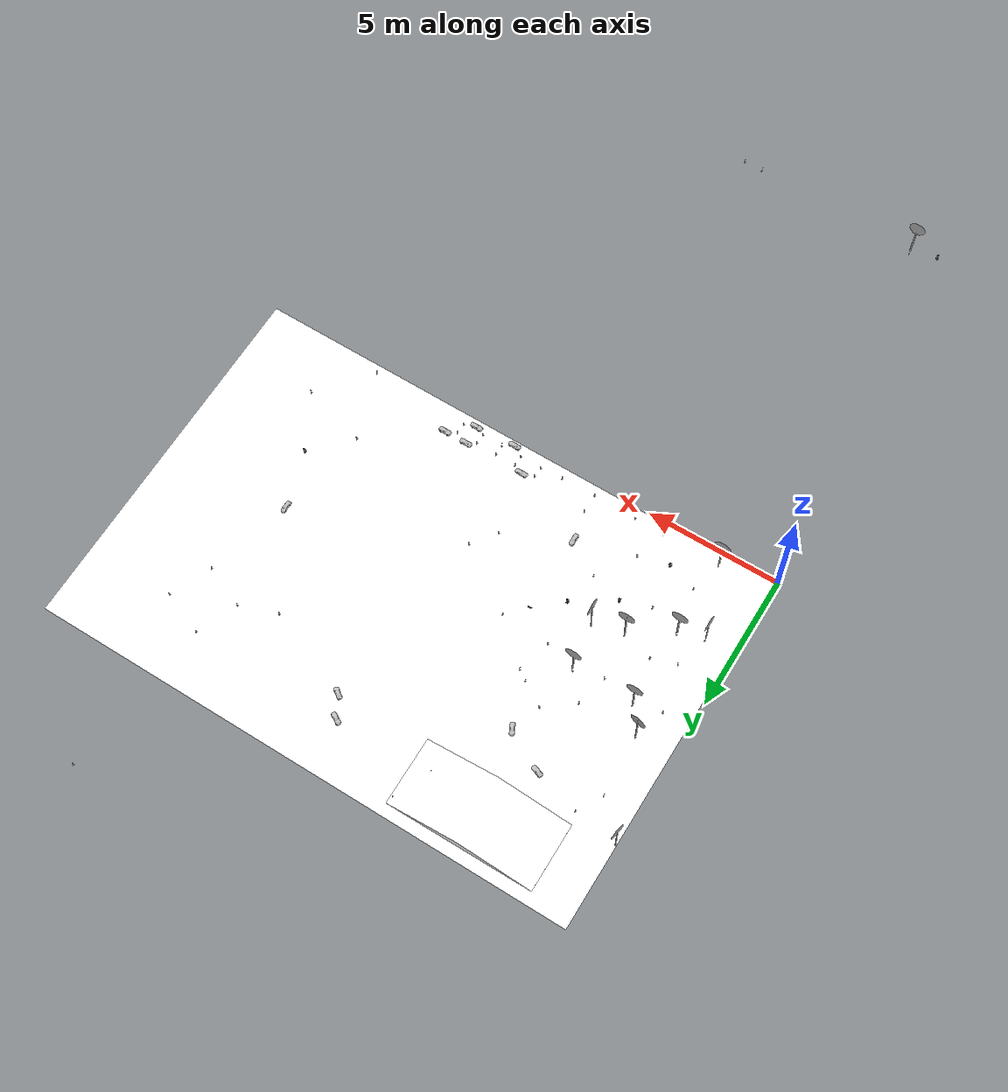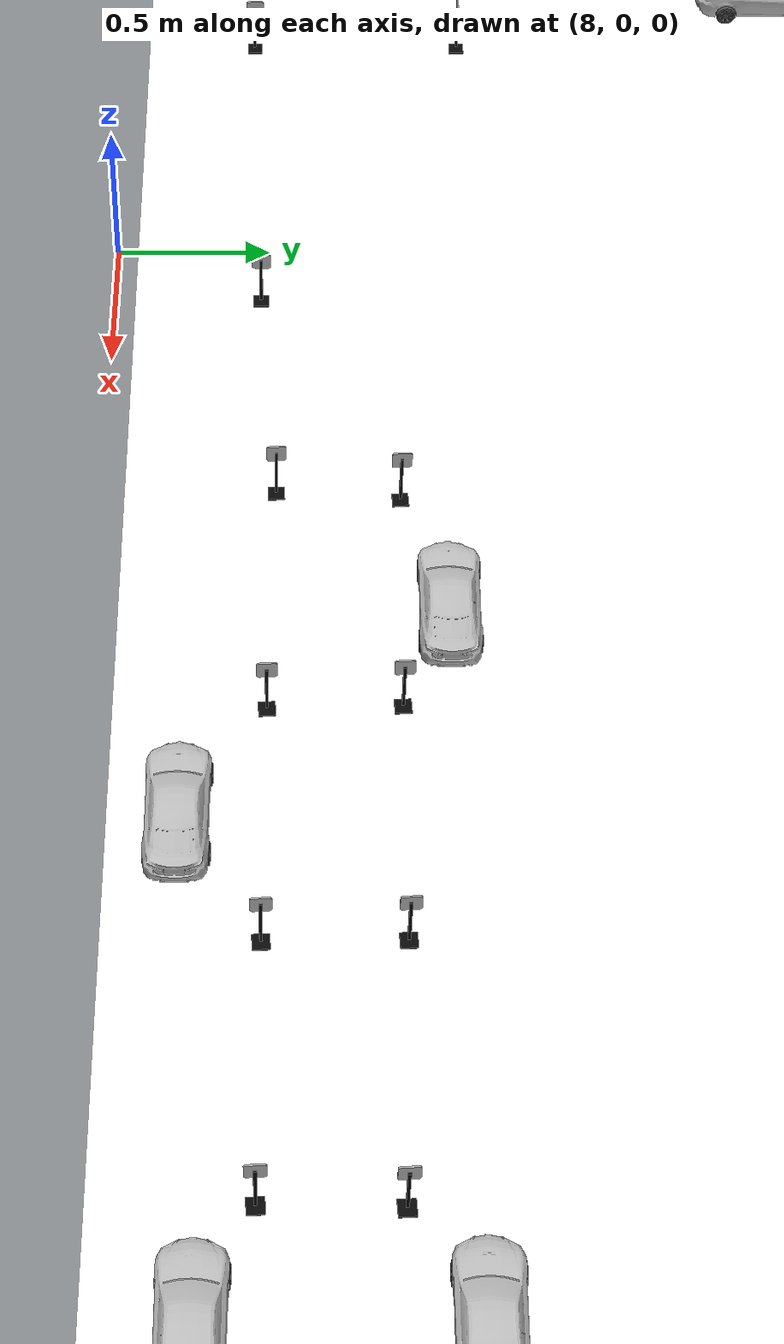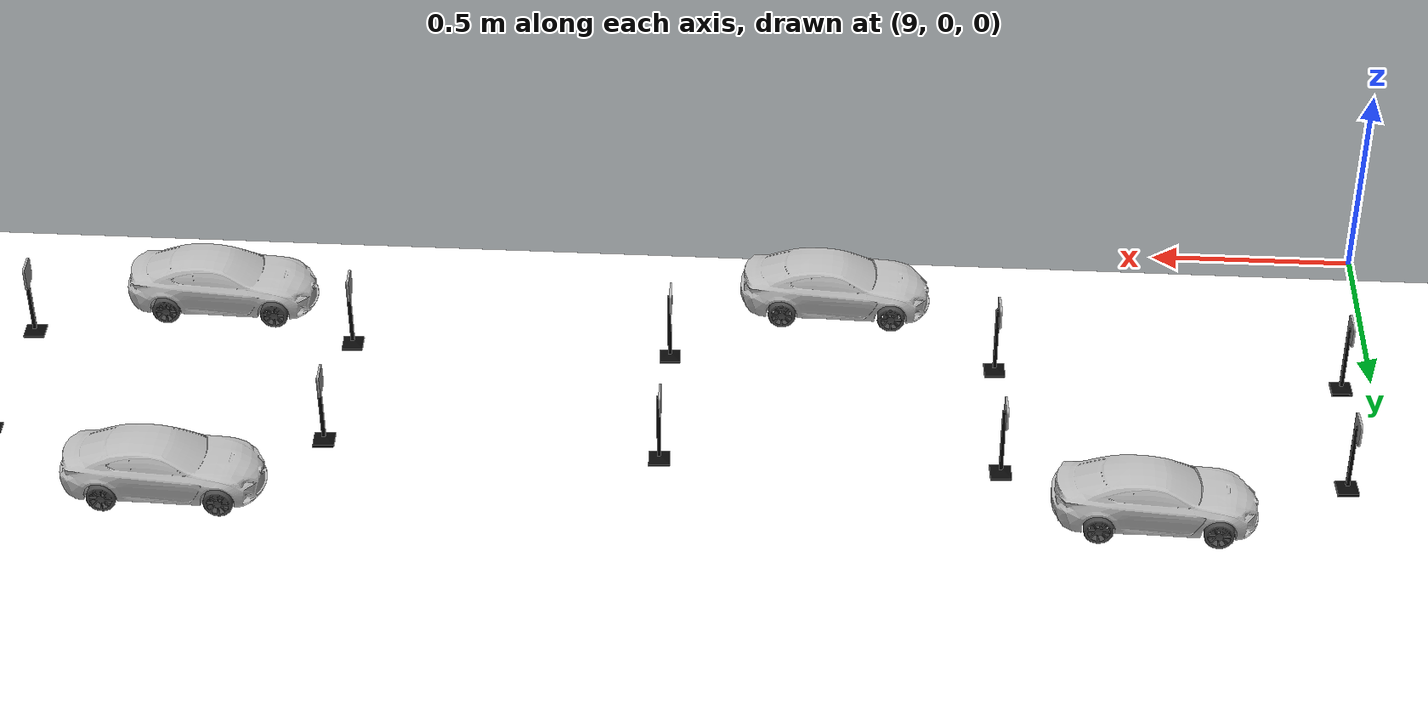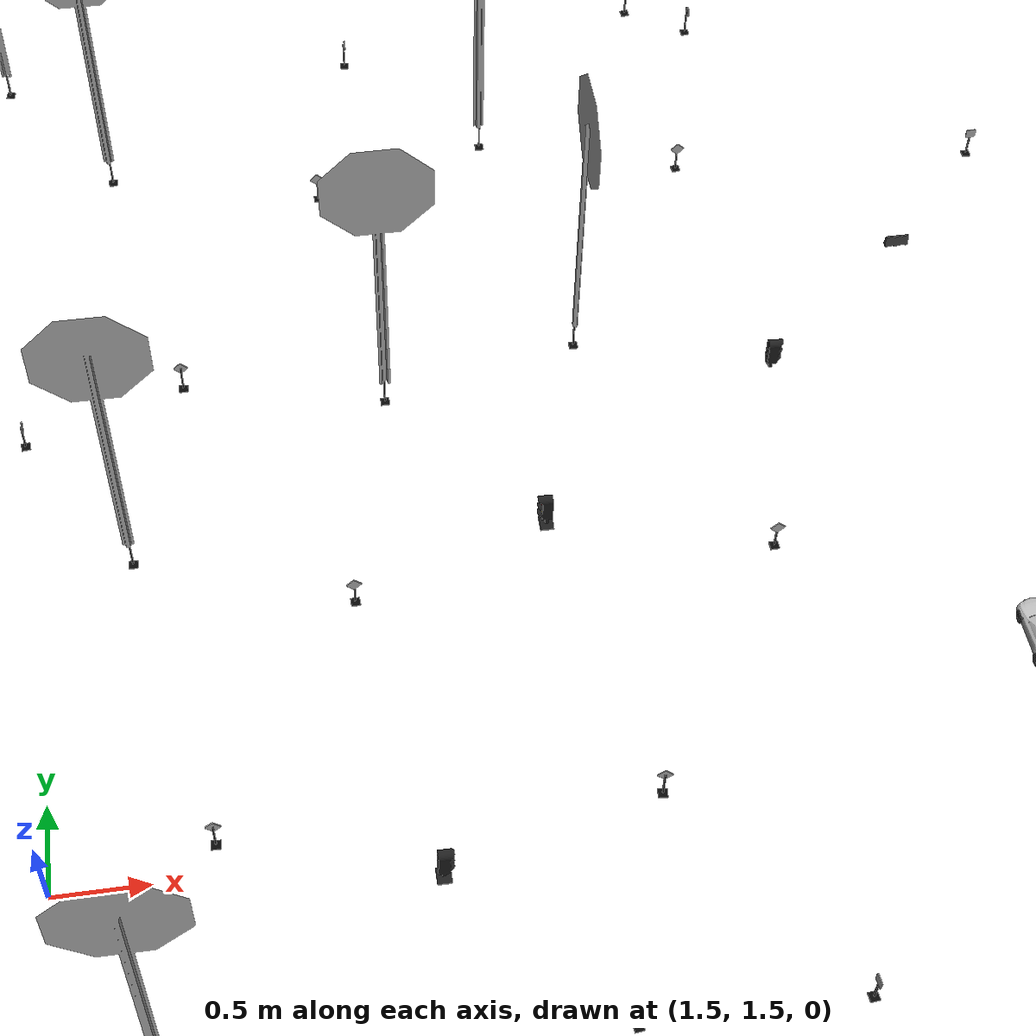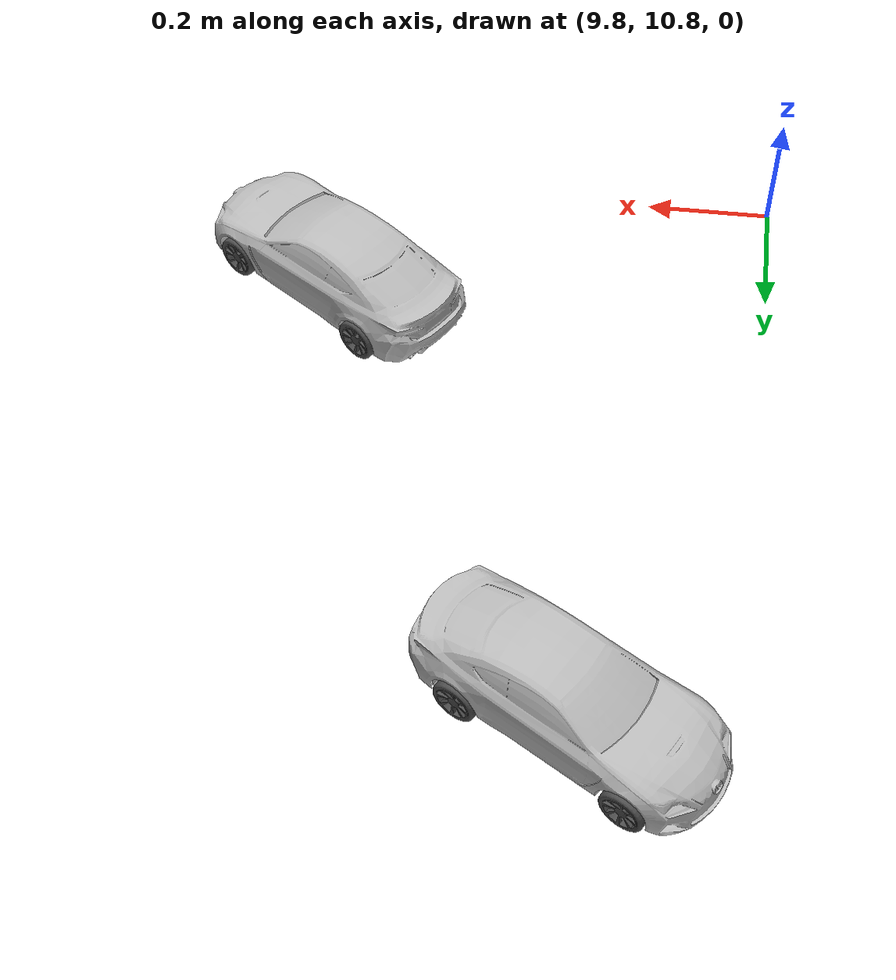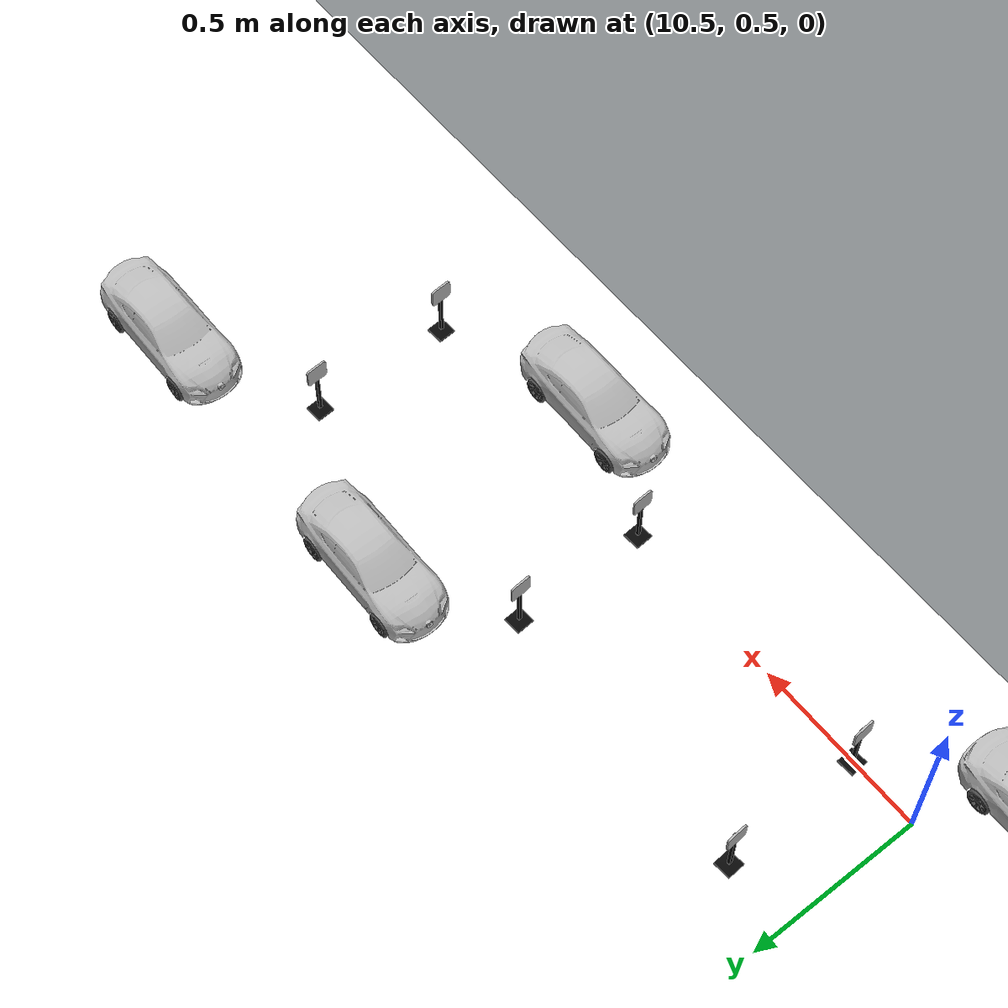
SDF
<sdf version="1.7">
 <world name="bfmc_official">
  <gravity>0 0 -9.8</gravity>
  <light name="c1" type="point">
   <pose>0 0 2 0 -0 0</pose>
   <diffuse>125 125 125 125</diffuse>
   <specular>50 50 50 50</specular>
   <attenuation><range>20</range><constant>0.3</constant><quadratic>0</quadratic><linear>0</linear></attenuation>
   <cast_shadows>0</cast_shadows>
   <direction>0 0 -1</direction>
   <spot><inner_angle>0</inner_angle><outer_angle>0</outer_angle><falloff>0</falloff></spot>
  </light>
  <light name="c2" type="point">
   <pose>15 0 2 0 -0 0</pose>
   <diffuse>125 125 125 125</diffuse>
   <specular>50 50 50 50</specular>
   <attenuation><range>20</range><constant>0.3</constant><quadratic>0</quadratic><linear>0</linear></attenuation>
   <cast_shadows>0</cast_shadows>
   <direction>0 0 -1</direction>
   <spot><inner_angle>0</inner_angle><outer_angle>0</outer_angle><falloff>0</falloff></spot>
  </light>
  <light name="c3" type="point">
   <pose>0 -15 2 0 -0 0</pose>
   <diffuse>125 125 125 125</diffuse>
   <specular>50 50 50 50</specular>
   <attenuation><range>20</range><constant>0.3</constant><quadratic>0</quadratic><linear>0</linear></attenuation>
   <cast_shadows>0</cast_shadows>
   <direction>0 0 -1</direction>
   <spot><inner_angle>0</inner_angle><outer_angle>0</outer_angle><falloff>0</falloff></spot>
  </light>
  <light name="c4" type="point">
   <pose>15 -15 2 0 -0 0</pose>
   <diffuse>125 125 125 125</diffuse>
   <specular>50 50 50 50</specular>
   <attenuation><range>50</range><constant>0.3</constant><quadratic>0</quadratic><linear>0</linear></attenuation>
   <cast_shadows>0</cast_shadows>
   <direction>0 0 -1</direction>
   <spot><inner_angle>0</inner_angle><outer_angle>0</outer_angle><falloff>0</falloff></spot>
  </light>
  <model name="track">
   <static>1</static>
   <link name="link">
    <collision name="collision">
     <geometry><plane><normal>0 0 1</normal><size>20.541 13.656</size></plane></geometry>
     <surface>
      <contact><collide_bitmask>65535</collide_bitmask></contact>
      <friction><ode><mu>1</mu><mu2>1</mu2></ode></friction>
     </surface>
    </collision>
    <visual name="visual">
     <geometry><plane><normal>0 0 1</normal><size>20.541 13.656</size></plane></geometry>
     <material>
      <ambient>1 1 1 1</ambient>
      <diffuse>1 1 1 1</diffuse>
      <specular>0 0 0 0</specular>
      <emissive>1 1 1 1</emissive>
      <script>
       <uri>model://track/materials/scripts</uri>
       <uri>model://track/materials/textures</uri>
       <name>BFMC_MATERIAL</name>
      </script>
     </material>
    </visual>
   </link>
   <pose>10.348 6.893 0 0 -0 0</pose>
  </model>
  <magnetic_field>6e-06 2.3e-05 -4.2e-05</magnetic_field>
  <atmosphere type="adiabatic"/>
  <physics name="default_physics" default="0" type="ode">
   <max_step_size>0.001</max_step_size>
   <real_time_factor>1</real_time_factor>
   <real_time_update_rate>1000</real_time_update_rate>
  </physics>
  <scene><ambient>0.4 0.4 0.4 1</ambient><background>0.7 0.7 0.7 1</background><shadows>1</shadows></scene>
  <audio><device>default</device></audio>
  <spherical_coordinates>
   <surface_model>EARTH_WGS84</surface_model>
   <latitude_deg>0</latitude_deg>
   <longitude_deg>0</longitude_deg>
   <elevation>0</elevation>
   <heading_deg>0</heading_deg>
  </spherical_coordinates>
  <model name="CWALK_M">
   <static>1</static>
   <link name="sign_leg">
    <inertial>
     <mass>0.5</mass>
     <inertia>
      <ixx>0.166667</ixx>
      <ixy>0</ixy>
      <ixz>0</ixz>
      <iyy>0.166667</iyy>
      <iyz>0</iyz>
      <izz>0.166667</izz>
     </inertia>
     <pose>0 0 -0.078998 0 -0 0</pose>
    </inertial>
    <pose>0.002193 -0.000682 -0.07606 0 -0 0</pose>
    <self_collide>1</self_collide>
    <enable_wind>1</enable_wind>
    <visual name="visual">
     <geometry><mesh><uri>model://subassembly/meshes/sign_leg.dae</uri><scale>1 1 1</scale></mesh></geometry>
    </visual>
    <collision name="collision">
     <geometry><mesh><uri>model://subassembly/meshes/sign_leg.dae</uri><scale>1 1 1</scale></mesh></geometry>
     <surface>
      <friction>
       <ode><mu>0.46</mu><mu2>1</mu2><fdir1>0 0 0</fdir1><slip1>0</slip1><slip2>0</slip2></ode>
       <torsional>
        <coefficient>1</coefficient>
        <patch_radius>0</patch_radius>
        <surface_radius>0</surface_radius>
        <use_patch_radius>1</use_patch_radius>
        <ode><slip>0</slip></ode>
       </torsional>
      </friction>
      <bounce><restitution_coefficient>0</restitution_coefficient><threshold>1e+06</threshold></bounce>
      <contact>
       <collide_without_contact>0</collide_without_contact>
       <collide_without_contact_bitmask>1</collide_without_contact_bitmask>
       <collide_bitmask>1</collide_bitmask>
       <ode>
        <soft_cfm>0</soft_cfm>
        <soft_erp>0.2</soft_erp>
        <kp>1e+13</kp>
        <kd>1</kd>
        <max_vel>0.01</max_vel>
        <min_depth>0</min_depth>
       </ode>
       <bullet>
        <split_impulse>1</split_impulse>
        <split_impulse_penetration_threshold>-0.01</split_impulse_penetration_threshold>
        <soft_cfm>0</soft_cfm>
        <soft_erp>0.2</soft_erp>
        <kp>1e+13</kp>
        <kd>1</kd>
       </bullet>
      </contact>
     </surface>
    </collision>
   </link>
   <link name="rectangular_support">
    <inertial>
     <mass>0.022</mass>
     <inertia>
      <ixx>0.166667</ixx>
      <ixy>0</ixy>
      <ixz>0</ixz>
      <iyy>0.166667</iyy>
      <iyz>0</iyz>
      <izz>0.166667</izz>
     </inertia>
    </inertial>
    <pose>-0 0.000682 0.09894 0 -0 3.14159</pose>
    <self_collide>1</self_collide>
    <enable_wind>1</enable_wind>
    <visual name="visual">
     <geometry>
      <mesh><uri>model://crosswalk_sign/meshes/pedestrian_sign.dae</uri><scale>10 10 10</scale></mesh>
     </geometry>
     <material>
      <lighting>1</lighting>
      <script>
       <uri>model://crosswalk_sign/materials/scripts</uri>
       <uri>model://crosswalk_sign/materials/textures</uri>
       <name>PEDESTRIAN_SIGN</name>
      </script>
      <shader type="vertex"><normal_map>__default__</normal_map></shader>
      <ambient>0.3 0.3 0.3 1</ambient>
      <diffuse>0.7 0.7 0.7 1</diffuse>
      <specular>0.01 0.01 0.01 1</specular>
      <emissive>0 0 0 1</emissive>
     </material>
    </visual>
    <collision name="collision">
     <geometry>
      <mesh><uri>model://crosswalk_sign/meshes/pedestrian_sign.dae</uri><scale>10 10 10</scale></mesh>
     </geometry>
     <surface>
      <friction>
       <ode><mu>0.46</mu><mu2>1</mu2><fdir1>0 0 0</fdir1><slip1>0</slip1><slip2>0</slip2></ode>
       <torsional>
        <coefficient>1</coefficient>
        <patch_radius>0</patch_radius>
        <surface_radius>0</surface_radius>
        <use_patch_radius>1</use_patch_radius>
        <ode><slip>0</slip></ode>
       </torsional>
      </friction>
      <bounce><restitution_coefficient>0</restitution_coefficient><threshold>1e+06</threshold></bounce>
      <contact>
       <collide_without_contact>0</collide_without_contact>
       <collide_without_contact_bitmask>1</collide_without_contact_bitmask>
       <collide_bitmask>1</collide_bitmask>
       <ode>
        <soft_cfm>0</soft_cfm>
        <soft_erp>0.2</soft_erp>
        <kp>1e+13</kp>
        <kd>1</kd>
        <max_vel>0.01</max_vel>
        <min_depth>0</min_depth>
       </ode>
       <bullet>
        <split_impulse>1</split_impulse>
        <split_impulse_penetration_threshold>-0.01</split_impulse_penetration_threshold>
        <soft_cfm>0</soft_cfm>
        <soft_erp>0.2</soft_erp>
        <kp>1e+13</kp>
        <kd>1</kd>
       </bullet>
      </contact>
     </surface>
    </collision>
   </link>
   <joint name="support_to_leg_joint" type="fixed">
    <parent>link_0</parent>
    <child>link_1</child>
    <physics>
     <ode><limit><cfm>0</cfm><erp>0.2</erp></limit><suspension><cfm>0</cfm><erp>0.2</erp></suspension></ode>
    </physics>
   </joint>
   <static>1</static>
   <pose>8.2305 0.47665 0.078998 0 0 -0.016495</pose>
  </model>
  <model name="PRK_P4">
   <static>1</static>
   <link name="sign_leg">
    <inertial>
     <mass>0.5</mass>
     <inertia>
      <ixx>0.166667</ixx>
      <ixy>0</ixy>
      <ixz>0</ixz>
      <iyy>0.166667</iyy>
      <iyz>0</iyz>
      <izz>0.166667</izz>
     </inertia>
     <pose>0 0 -0.078998 0 -0 0</pose>
    </inertial>
    <pose>0.002193 -0.000682 -0.07606 0 -0 0</pose>
    <self_collide>1</self_collide>
    <enable_wind>1</enable_wind>
    <visual name="visual">
     <geometry><mesh><uri>model://subassembly/meshes/sign_leg.dae</uri><scale>1 1 1</scale></mesh></geometry>
    </visual>
    <collision name="collision">
     <geometry><mesh><uri>model://subassembly/meshes/sign_leg.dae</uri><scale>1 1 1</scale></mesh></geometry>
     <surface>
      <friction>
       <ode><mu>0.46</mu><mu2>1</mu2><fdir1>0 0 0</fdir1><slip1>0</slip1><slip2>0</slip2></ode>
       <torsional>
        <coefficient>1</coefficient>
        <patch_radius>0</patch_radius>
        <surface_radius>0</surface_radius>
        <use_patch_radius>1</use_patch_radius>
        <ode><slip>0</slip></ode>
       </torsional>
      </friction>
      <bounce><restitution_coefficient>0</restitution_coefficient><threshold>1e+06</threshold></bounce>
      <contact>
       <collide_without_contact>0</collide_without_contact>
       <collide_without_contact_bitmask>1</collide_without_contact_bitmask>
       <collide_bitmask>1</collide_bitmask>
       <ode>
        <soft_cfm>0</soft_cfm>
        <soft_erp>0.2</soft_erp>
        <kp>1e+13</kp>
        <kd>1</kd>
        <max_vel>0.01</max_vel>
        <min_depth>0</min_depth>
       </ode>
       <bullet>
        <split_impulse>1</split_impulse>
        <split_impulse_penetration_threshold>-0.01</split_impulse_penetration_threshold>
        <soft_cfm>0</soft_cfm>
        <soft_erp>0.2</soft_erp>
        <kp>1e+13</kp>
        <kd>1</kd>
       </bullet>
      </contact>
     </surface>
    </collision>
   </link>
   <link name="rectangular_support">
    <inertial>
     <mass>0.022</mass>
     <inertia>
      <ixx>0.166667</ixx>
      <ixy>0</ixy>
      <ixz>0</ixz>
      <iyy>0.166667</iyy>
      <iyz>0</iyz>
      <izz>0.166667</izz>
     </inertia>
    </inertial>
    <pose>-0.002193 0.000682 0.09894 0 -0 3.14159</pose>
    <self_collide>1</self_collide>
    <enable_wind>1</enable_wind>
    <visual name="visual">
     <geometry>
      <mesh><uri>model://parking_sign/meshes/parking_sign.dae</uri><scale>10 10 10</scale></mesh>
     </geometry>
     <material>
      <lighting>1</lighting>
      <script>
       <uri>model://parking_sign/materials/scripts</uri>
       <uri>model://parking_sign/materials/textures</uri>
       <name>PARKING_SIGN</name>
      </script>
      <shader type="vertex"><normal_map>__default__</normal_map></shader>
      <ambient>0.3 0.3 0.3 1</ambient>
      <diffuse>0.7 0.7 0.7 1</diffuse>
      <specular>0.01 0.01 0.01 1</specular>
      <emissive>0 0 0 1</emissive>
     </material>
    </visual>
    <collision name="collision">
     <geometry>
      <mesh><uri>model://parking_sign/meshes/parking_sign.dae</uri><scale>10 10 10</scale></mesh>
     </geometry>
     <surface>
      <friction>
       <ode><mu>0.46</mu><mu2>1</mu2><fdir1>0 0 0</fdir1><slip1>0</slip1><slip2>0</slip2></ode>
       <torsional>
        <coefficient>1</coefficient>
        <patch_radius>0</patch_radius>
        <surface_radius>0</surface_radius>
        <use_patch_radius>1</use_patch_radius>
        <ode><slip>0</slip></ode>
       </torsional>
      </friction>
      <bounce><restitution_coefficient>0</restitution_coefficient><threshold>1e+06</threshold></bounce>
      <contact>
       <collide_without_contact>0</collide_without_contact>
       <collide_without_contact_bitmask>1</collide_without_contact_bitmask>
       <collide_bitmask>1</collide_bitmask>
       <ode>
        <soft_cfm>0</soft_cfm>
        <soft_erp>0.2</soft_erp>
        <kp>1e+13</kp>
        <kd>1</kd>
        <max_vel>0.01</max_vel>
        <min_depth>0</min_depth>
       </ode>
       <bullet>
        <split_impulse>1</split_impulse>
        <split_impulse_penetration_threshold>-0.01</split_impulse_penetration_threshold>
        <soft_cfm>0</soft_cfm>
        <soft_erp>0.2</soft_erp>
        <kp>1e+13</kp>
        <kd>1</kd>
       </bullet>
      </contact>
     </surface>
    </collision>
   </link>
   <joint name="support_to_leg_joint" type="fixed">
    <parent>link_0</parent>
    <child>link_1</child>
    <physics>
     <ode><limit><cfm>0</cfm><erp>0.2</erp></limit><suspension><cfm>0</cfm><erp>0.2</erp></suspension></ode>
    </physics>
   </joint>
   <static>1</static>
   <pose>9.07492 0.531686 0.078998 0 -0 0.059376</pose>
  </model>
  <model name="obstacle_rcCar_3">
   <static>1</static>
   <frame name="chassis::__model__" attached_to="chassis::link">
    <pose relative_to="__model__">0 0 0 0 -0 0</pose>
   </frame>
   <link name="chassis::link">
    <inertial>
     <mass>0.26244</mass>
     <inertia>
      <ixx>0.00283444</ixx>
      <ixy>0</ixy>
      <ixz>0</ixz>
      <iyy>0.00039867</iyy>
      <iyz>0</iyz>
      <izz>0.00323293</izz>
     </inertia>
    </inertial>
    <pose relative_to="chassis::__model__">0 0 0 0 -0 1.5708</pose>
    <visual name="visual">
     <pose>0 0 -0.0065 0 0 -1.57079</pose>
     <geometry><mesh><uri>model://chassis/meshes/chassisV5.dae</uri><scale>1 1 1</scale></mesh></geometry>
     <material>
      <lighting>1</lighting>
      <shader type="vertex"><normal_map>__default__</normal_map></shader>
      <ambient>0.6 0.6 0.6 1</ambient>
      <diffuse>0.85 0.85 0.85 1</diffuse>
      <specular>0.6 0.6 0.6 1</specular>
      <emissive>0 0 0 1</emissive>
     </material>
    </visual>
    <collision name="collision">
     <geometry><box><size>0.135 0.36 0.002</size></box></geometry>
     <surface>
      <friction>
       <ode><mu>1</mu><mu2>1</mu2><fdir1>0 0 0</fdir1><slip1>0</slip1><slip2>0</slip2></ode>
       <torsional>
        <coefficient>1</coefficient>
        <patch_radius>0</patch_radius>
        <surface_radius>0</surface_radius>
        <use_patch_radius>1</use_patch_radius>
        <ode><slip>0</slip></ode>
       </torsional>
      </friction>
      <bounce><restitution_coefficient>0</restitution_coefficient><threshold>1e+06</threshold></bounce>
      <contact>
       <collide_without_contact>0</collide_without_contact>
       <collide_without_contact_bitmask>1</collide_without_contact_bitmask>
       <collide_bitmask>1</collide_bitmask>
       <ode>
        <soft_cfm>0</soft_cfm>
        <soft_erp>0.2</soft_erp>
        <kp>1e+13</kp>
        <kd>1</kd>
        <max_vel>0.01</max_vel>
        <min_depth>0</min_depth>
       </ode>
       <bullet>
        <split_impulse>1</split_impulse>
        <split_impulse_penetration_threshold>-0.01</split_impulse_penetration_threshold>
        <soft_cfm>0</soft_cfm>
        <soft_erp>0.2</soft_erp>
        <kp>1e+13</kp>
        <kd>1</kd>
       </bullet>
      </contact>
     </surface>
    </collision>
   </link>
   <frame name="wheel_rear_left::__model__" attached_to="wheel_rear_left::link_rim">
    <pose relative_to="__model__">-0.152 0.081 0 0 -0 0</pose>
   </frame>
   <link name="wheel_rear_left::link_rim">
    <inertial>
     <mass>0.038</mass>
     <inertia>
      <ixx>1.283e-05</ixx>
      <ixy>0</ixy>
      <ixz>0</ixz>
      <iyy>1.283e-05</iyy>
      <iyz>0</iyz>
      <izz>2.069e-05</izz>
     </inertia>
    </inertial>
    <pose relative_to="wheel_rear_left::__model__">0 0 0 1.5708 -0 0</pose>
    <visual name="visual">
     <pose>0 0 0 -1.5708 0 0</pose>
     <geometry><mesh><uri>model://wheel_left/meshes/rim.dae</uri><scale>1 1 1</scale></mesh></geometry>
     <material>
      <lighting>1</lighting>
      <shader type="vertex"><normal_map>__default__</normal_map></shader>
      <ambient>0.2 0.2 0.2 1</ambient>
      <diffuse>0.3 0.3 0.3 1</diffuse>
      <specular>0.5 0.5 0.5 1</specular>
      <emissive>0 0 0 0</emissive>
     </material>
    </visual>
    <collision name="collision">
     <geometry><cylinder><radius>0.033</radius><length>0.028</length></cylinder></geometry>
     <surface>
      <friction>
       <ode><mu>0.7</mu><mu2>0.7</mu2><fdir1>0 0 0</fdir1><slip1>0</slip1><slip2>0</slip2></ode>
       <torsional>
        <coefficient>1</coefficient>
        <patch_radius>0</patch_radius>
        <surface_radius>0</surface_radius>
        <use_patch_radius>1</use_patch_radius>
        <ode><slip>0</slip></ode>
       </torsional>
      </friction>
      <bounce><restitution_coefficient>0</restitution_coefficient><threshold>1e+06</threshold></bounce>
      <contact>
       <collide_without_contact>0</collide_without_contact>
       <collide_without_contact_bitmask>1</collide_without_contact_bitmask>
       <collide_bitmask>1</collide_bitmask>
       <ode>
        <soft_cfm>0</soft_cfm>
        <soft_erp>0.2</soft_erp>
        <kp>1e+07</kp>
        <kd>1</kd>
        <max_vel>0.01</max_vel>
        <min_depth>0</min_depth>
       </ode>
       <bullet>
        <split_impulse>1</split_impulse>
        <split_impulse_penetration_threshold>-0.01</split_impulse_penetration_threshold>
        <soft_cfm>0</soft_cfm>
        <soft_erp>0.2</soft_erp>
        <kp>1e+07</kp>
        <kd>1</kd>
       </bullet>
      </contact>
     </surface>
    </collision>
   </link>
   <frame name="wheel_rear_right::__model__" attached_to="wheel_rear_right::link_rim">
    <pose relative_to="__model__">-0.152 -0.081 0 0 -0 0</pose>
   </frame>
   <link name="wheel_rear_right::link_rim">
    <inertial>
     <mass>0.038</mass>
     <inertia>
      <ixx>1.283e-05</ixx>
      <ixy>0</ixy>
      <ixz>0</ixz>
      <iyy>1.283e-05</iyy>
      <iyz>0</iyz>
      <izz>2.069e-05</izz>
     </inertia>
    </inertial>
    <pose relative_to="wheel_rear_right::__model__">0 0 0 1.5708 -0 0</pose>
    <visual name="visual">
     <pose>0 0 0 -1.5708 0 0</pose>
     <geometry><mesh><uri>model://wheel_right/meshes/rim.dae</uri><scale>1 1 1</scale></mesh></geometry>
     <material>
      <lighting>1</lighting>
      <shader type="vertex"><normal_map>__default__</normal_map></shader>
      <ambient>0.2 0.2 0.2 1</ambient>
      <diffuse>0.3 0.3 0.3 1</diffuse>
      <specular>0.5 0.5 0.5 1</specular>
      <emissive>0 0 0 0</emissive>
     </material>
    </visual>
    <collision name="collision">
     <geometry><cylinder><radius>0.033</radius><length>0.028</length></cylinder></geometry>
     <surface>
      <friction>
       <ode><mu>0.7</mu><mu2>0.7</mu2><fdir1>0 0 0</fdir1><slip1>0</slip1><slip2>0</slip2></ode>
       <torsional>
        <coefficient>1</coefficient>
        <patch_radius>0</patch_radius>
        <surface_radius>0</surface_radius>
        <use_patch_radius>1</use_patch_radius>
        <ode><slip>0</slip></ode>
       </torsional>
      </friction>
      <bounce><restitution_coefficient>0</restitution_coefficient><threshold>1e+06</threshold></bounce>
      <contact>
       <collide_without_contact>0</collide_without_contact>
       <collide_without_contact_bitmask>1</collide_without_contact_bitmask>
       <collide_bitmask>1</collide_bitmask>
       <ode>
        <soft_cfm>0</soft_cfm>
        <soft_erp>0.2</soft_erp>
        <kp>1e+07</kp>
        <kd>1</kd>
        <max_vel>0.01</max_vel>
        <min_depth>0</min_depth>
       </ode>
       <bullet>
        <split_impulse>1</split_impulse>
        <split_impulse_penetration_threshold>-0.01</split_impulse_penetration_threshold>
        <soft_cfm>0</soft_cfm>
        <soft_erp>0.2</soft_erp>
        <kp>1e+07</kp>
        <kd>1</kd>
       </bullet>
      </contact>
     </surface>
    </collision>
   </link>
   <frame name="steer_left::__model__" attached_to="steer_left::link_steer">
    <pose relative_to="__model__">0.112 0.0725 0 0 -0 0</pose>
   </frame>
   <link name="steer_left::link_steer">
    <inertial>
     <mass>0.001</mass>
     <inertia>
      <ixx>0.00014583</ixx>
      <ixy>0</ixy>
      <ixz>0</ixz>
      <iyy>0.00014583</iyy>
      <iyz>0</iyz>
      <izz>0.000125</izz>
     </inertia>
    </inertial>
    <pose relative_to="steer_left::__model__">0 0 0 1.5708 -0 0</pose>
    <visual name="visual">
     <geometry><cylinder><radius>0.001</radius><length>0.01</length></cylinder></geometry>
     <material>
      <lighting>1</lighting>
      <script><uri>file://media/materials/scripts/gazebo.material</uri><name>Gazebo/Grey</name></script>
      <shader type="vertex"><normal_map>__default__</normal_map></shader>
      <ambient>0.3 0.3 0.3 1</ambient>
      <diffuse>0.7 0.7 0.7 1</diffuse>
      <specular>0.01 0.01 0.01 1</specular>
      <emissive>0 0 0 1</emissive>
     </material>
    </visual>
    <collision name="collision">
     <geometry><cylinder><radius>0.001</radius><length>0.01</length></cylinder></geometry>
     <surface>
      <friction>
       <ode><mu>1</mu><mu2>1</mu2><fdir1>0 0 0</fdir1><slip1>0</slip1><slip2>0</slip2></ode>
       <torsional>
        <coefficient>1</coefficient>
        <patch_radius>0</patch_radius>
        <surface_radius>0</surface_radius>
        <use_patch_radius>1</use_patch_radius>
        <ode><slip>0</slip></ode>
       </torsional>
      </friction>
      <bounce><restitution_coefficient>0</restitution_coefficient><threshold>1e+06</threshold></bounce>
      <contact>
       <collide_without_contact>0</collide_without_contact>
       <collide_without_contact_bitmask>1</collide_without_contact_bitmask>
       <collide_bitmask>1</collide_bitmask>
       <ode>
        <soft_cfm>0</soft_cfm>
        <soft_erp>0.2</soft_erp>
        <kp>1e+13</kp>
        <kd>1</kd>
        <max_vel>0.01</max_vel>
        <min_depth>0</min_depth>
       </ode>
       <bullet>
        <split_impulse>1</split_impulse>
        <split_impulse_penetration_threshold>-0.01</split_impulse_penetration_threshold>
        <soft_cfm>0</soft_cfm>
        <soft_erp>0.2</soft_erp>
        <kp>1e+13</kp>
        <kd>1</kd>
       </bullet>
      </contact>
     </surface>
    </collision>
   </link>
   <frame name="steer_right::__model__" attached_to="steer_right::link_steer">
    <pose relative_to="__model__">0.112 -0.0725 0 0 -0 0</pose>
   </frame>
   <link name="steer_right::link_steer">
    <inertial>
     <mass>0.001</mass>
     <inertia>
      <ixx>0.00014583</ixx>
      <ixy>0</ixy>
      <ixz>0</ixz>
      <iyy>0.00014583</iyy>
      <iyz>0</iyz>
      <izz>0.000125</izz>
     </inertia>
    </inertial>
    <pose relative_to="steer_right::__model__">0 0 0 1.5708 -0 0</pose>
    <visual name="visual">
     <geometry><cylinder><radius>0.001</radius><length>0.01</length></cylinder></geometry>
     <material>
      <lighting>1</lighting>
      <script><uri>file://media/materials/scripts/gazebo.material</uri><name>Gazebo/Grey</name></script>
      <shader type="vertex"><normal_map>__default__</normal_map></shader>
      <ambient>0.3 0.3 0.3 1</ambient>
      <diffuse>0.7 0.7 0.7 1</diffuse>
      <specular>0.01 0.01 0.01 1</specular>
      <emissive>0 0 0 1</emissive>
     </material>
    </visual>
    <collision name="collision">
     <geometry><cylinder><radius>0.001</radius><length>0.01</length></cylinder></geometry>
     <surface>
      <friction>
       <ode><mu>1</mu><mu2>1</mu2><fdir1>0 0 0</fdir1><slip1>0</slip1><slip2>0</slip2></ode>
       <torsional>
        <coefficient>1</coefficient>
        <patch_radius>0</patch_radius>
        <surface_radius>0</surface_radius>
        <use_patch_radius>1</use_patch_radius>
        <ode><slip>0</slip></ode>
       </torsional>
      </friction>
      <bounce><restitution_coefficient>0</restitution_coefficient><threshold>1e+06</threshold></bounce>
      <contact>
       <collide_without_contact>0</collide_without_contact>
       <collide_without_contact_bitmask>1</collide_without_contact_bitmask>
       <collide_bitmask>1</collide_bitmask>
       <ode>
        <soft_cfm>0</soft_cfm>
        <soft_erp>0.2</soft_erp>
        <kp>1e+13</kp>
        <kd>1</kd>
        <max_vel>0.01</max_vel>
        <min_depth>0</min_depth>
       </ode>
       <bullet>
        <split_impulse>1</split_impulse>
        <split_impulse_penetration_threshold>-0.01</split_impulse_penetration_threshold>
        <soft_cfm>0</soft_cfm>
        <soft_erp>0.2</soft_erp>
        <kp>1e+13</kp>
        <kd>1</kd>
       </bullet>
      </contact>
     </surface>
    </collision>
   </link>
   <frame name="wheel_front_left::__model__" attached_to="wheel_front_left::link_rim">
    <pose relative_to="__model__">0.118 0.081 0 0 -0 0</pose>
   </frame>
   <link name="wheel_front_left::link_rim">
    <inertial>
     <mass>0.038</mass>
     <inertia>
      <ixx>1.283e-05</ixx>
      <ixy>0</ixy>
      <ixz>0</ixz>
      <iyy>1.283e-05</iyy>
      <iyz>0</iyz>
      <izz>2.069e-05</izz>
     </inertia>
    </inertial>
    <pose relative_to="wheel_front_left::__model__">0 0 0 1.5708 -0 0</pose>
    <visual name="visual">
     <pose>0 0 0 -1.5708 0 0</pose>
     <geometry><mesh><uri>model://wheel_left/meshes/rim.dae</uri><scale>1 1 1</scale></mesh></geometry>
     <material>
      <lighting>1</lighting>
      <shader type="vertex"><normal_map>__default__</normal_map></shader>
      <ambient>0.2 0.2 0.2 1</ambient>
      <diffuse>0.3 0.3 0.3 1</diffuse>
      <specular>0.5 0.5 0.5 1</specular>
      <emissive>0 0 0 0</emissive>
     </material>
    </visual>
    <collision name="collision">
     <geometry><cylinder><radius>0.033</radius><length>0.028</length></cylinder></geometry>
     <surface>
      <friction>
       <ode><mu>0.7</mu><mu2>0.7</mu2><fdir1>0 0 0</fdir1><slip1>0</slip1><slip2>0</slip2></ode>
       <torsional>
        <coefficient>1</coefficient>
        <patch_radius>0</patch_radius>
        <surface_radius>0</surface_radius>
        <use_patch_radius>1</use_patch_radius>
        <ode><slip>0</slip></ode>
       </torsional>
      </friction>
      <bounce><restitution_coefficient>0</restitution_coefficient><threshold>1e+06</threshold></bounce>
      <contact>
       <collide_without_contact>0</collide_without_contact>
       <collide_without_contact_bitmask>1</collide_without_contact_bitmask>
       <collide_bitmask>1</collide_bitmask>
       <ode>
        <soft_cfm>0</soft_cfm>
        <soft_erp>0.2</soft_erp>
        <kp>1e+07</kp>
        <kd>1</kd>
        <max_vel>0.01</max_vel>
        <min_depth>0</min_depth>
       </ode>
       <bullet>
        <split_impulse>1</split_impulse>
        <split_impulse_penetration_threshold>-0.01</split_impulse_penetration_threshold>
        <soft_cfm>0</soft_cfm>
        <soft_erp>0.2</soft_erp>
        <kp>1e+07</kp>
        <kd>1</kd>
       </bullet>
      </contact>
     </surface>
    </collision>
   </link>
   <frame name="wheel_front_right::__model__" attached_to="wheel_front_right::link_rim">
    <pose relative_to="__model__">0.118 -0.081 0 0 -0 0</pose>
   </frame>
   <link name="wheel_front_right::link_rim">
    <inertial>
     <mass>0.038</mass>
     <inertia>
      <ixx>1.283e-05</ixx>
      <ixy>0</ixy>
      <ixz>0</ixz>
      <iyy>1.283e-05</iyy>
      <iyz>0</iyz>
      <izz>2.069e-05</izz>
     </inertia>
    </inertial>
    <pose relative_to="wheel_front_right::__model__">0 0 0 1.5708 -0 0</pose>
    <visual name="visual">
     <pose>0 0 0 -1.5708 0 0</pose>
     <geometry><mesh><uri>model://wheel_right/meshes/rim.dae</uri><scale>1 1 1</scale></mesh></geometry>
     <material>
      <lighting>1</lighting>
      <shader type="vertex"><normal_map>__default__</normal_map></shader>
      <ambient>0.2 0.2 0.2 1</ambient>
      <diffuse>0.3 0.3 0.3 1</diffuse>
      <specular>0.5 0.5 0.5 1</specular>
      <emissive>0 0 0 0</emissive>
     </material>
    </visual>
    <collision name="collision">
     <geometry><cylinder><radius>0.033</radius><length>0.028</length></cylinder></geometry>
     <surface>
      <friction>
       <ode><mu>0.7</mu><mu2>0.7</mu2><fdir1>0 0 0</fdir1><slip1>0</slip1><slip2>0</slip2></ode>
       <torsional>
        <coefficient>1</coefficient>
        <patch_radius>0</patch_radius>
        <surface_radius>0</surface_radius>
        <use_patch_radius>1</use_patch_radius>
        <ode><slip>0</slip></ode>
       </torsional>
      </friction>
      <bounce><restitution_coefficient>0</restitution_coefficient><threshold>1e+06</threshold></bounce>
      <contact>
       <collide_without_contact>0</collide_without_contact>
       <collide_without_contact_bitmask>1</collide_without_contact_bitmask>
       <collide_bitmask>1</collide_bitmask>
       <ode>
        <soft_cfm>0</soft_cfm>
        <soft_erp>0.2</soft_erp>
        <kp>1e+07</kp>
        <kd>1</kd>
        <max_vel>0.01</max_vel>
        <min_depth>0</min_depth>
       </ode>
       <bullet>
        <split_impulse>1</split_impulse>
        <split_impulse_penetration_threshold>-0.01</split_impulse_penetration_threshold>
        <soft_cfm>0</soft_cfm>
        <soft_erp>0.2</soft_erp>
        <kp>1e+07</kp>
        <kd>1</kd>
       </bullet>
      </contact>
     </surface>
    </collision>
   </link>
   <frame name="car_body::__model__" attached_to="car_body::link">
    <pose relative_to="__model__">-0.024 0 -0.028 0 -0 0</pose>
   </frame>
   <link name="car_body::link">
    <inertial>
     <mass>1</mass>
     <inertia>
      <ixx>0.166667</ixx>
      <ixy>0</ixy>
      <ixz>0</ixz>
      <iyy>0.166667</iyy>
      <iyz>0</iyz>
      <izz>0.166667</izz>
     </inertia>
    </inertial>
    <pose relative_to="car_body::__model__">0 -0 0 0 -0 0</pose>
    <visual name="visual">
     <geometry><mesh><uri>model://car_body/meshes/CarBody.dae</uri><scale>1 1 1</scale></mesh></geometry>
     <material>
      <script>
       <uri>model://car_body/materials/scripts</uri>
       <uri>model://car_body/materials/textures</uri>
       <name>CarBody/Image</name>
      </script>
     </material>
    </visual>
   </link>
   <static>0</static>
   <joint name="joint_leftrear_rim" type="fixed">
    <parent>chassis::link</parent>
    <child>wheel_rear_left::link_rim</child>
   </joint>
   <joint name="joint_rightrear_rim" type="fixed">
    <parent>chassis::link</parent>
    <child>wheel_rear_right::link_rim</child>
   </joint>
   <joint name="joint_rightfront_rim" type="fixed">
    <parent>chassis::link</parent>
    <child>wheel_front_right::link_rim</child>
   </joint>
   <joint name="joint_leftfront_rim" type="fixed">
    <parent>chassis::link</parent>
    <child>wheel_front_left::link_rim</child>
   </joint>
   <joint name="joint_body" type="fixed"><parent>chassis::link</parent><child>car_body::link</child></joint>
   <pose>10.5171 11.0292 0.032939 0 0 -0.612112</pose>
  </model>
  <model name="LHIGH_H">
   <static>1</static>
   <link name="sign_leg">
    <inertial>
     <mass>0.5</mass>
     <inertia>
      <ixx>0.166667</ixx>
      <ixy>0</ixy>
      <ixz>0</ixz>
      <iyy>0.166667</iyy>
      <iyz>0</iyz>
      <izz>0.166667</izz>
     </inertia>
     <pose>0 0 -0.078998 0 -0 0</pose>
    </inertial>
    <pose>0.002193 -0.000682 -0.07606 0 -0 0</pose>
    <self_collide>1</self_collide>
    <enable_wind>1</enable_wind>
    <visual name="visual">
     <geometry><mesh><uri>model://subassembly/meshes/sign_leg.dae</uri><scale>1 1 1</scale></mesh></geometry>
    </visual>
    <collision name="collision">
     <geometry><mesh><uri>model://subassembly/meshes/sign_leg.dae</uri><scale>1 1 1</scale></mesh></geometry>
     <surface>
      <friction>
       <ode><mu>0.46</mu><mu2>1</mu2><fdir1>0 0 0</fdir1><slip1>0</slip1><slip2>0</slip2></ode>
       <torsional>
        <coefficient>1</coefficient>
        <patch_radius>0</patch_radius>
        <surface_radius>0</surface_radius>
        <use_patch_radius>1</use_patch_radius>
        <ode><slip>0</slip></ode>
       </torsional>
      </friction>
      <bounce><restitution_coefficient>0</restitution_coefficient><threshold>1e+06</threshold></bounce>
      <contact>
       <collide_without_contact>0</collide_without_contact>
       <collide_without_contact_bitmask>1</collide_without_contact_bitmask>
       <collide_bitmask>1</collide_bitmask>
       <ode>
        <soft_cfm>0</soft_cfm>
        <soft_erp>0.2</soft_erp>
        <kp>1e+13</kp>
        <kd>1</kd>
        <max_vel>0.01</max_vel>
        <min_depth>0</min_depth>
       </ode>
       <bullet>
        <split_impulse>1</split_impulse>
        <split_impulse_penetration_threshold>-0.01</split_impulse_penetration_threshold>
        <soft_cfm>0</soft_cfm>
        <soft_erp>0.2</soft_erp>
        <kp>1e+13</kp>
        <kd>1</kd>
       </bullet>
      </contact>
     </surface>
    </collision>
   </link>
   <link name="rectangular_support">
    <inertial>
     <mass>0.022</mass>
     <inertia>
      <ixx>0.166667</ixx>
      <ixy>0</ixy>
      <ixz>0</ixz>
      <iyy>0.166667</iyy>
      <iyz>0</iyz>
      <izz>0.166667</izz>
     </inertia>
    </inertial>
    <pose>-0 0 0.09894 0 -0 3.14159</pose>
    <self_collide>1</self_collide>
    <enable_wind>1</enable_wind>
    <visual name="visual">
     <pose>-0.002 0 0 0 -0 0</pose>
     <geometry>
      <mesh><uri>model://leave_highway_sign/meshes/leave_highway_sign.dae</uri><scale>1 1 1</scale></mesh>
     </geometry>
     <material>
      <lighting>1</lighting>
      <script>
       <uri>model://leave_highway_sign/materials/scripts</uri>
       <uri>model://leave_highway_sign/materials/textures</uri>
       <name>LEAVE_HIGHWAY_SIGN</name>
      </script>
      <shader type="vertex"><normal_map>__default__</normal_map></shader>
      <ambient>0.3 0.3 0.3 1</ambient>
      <diffuse>0.7 0.7 0.7 1</diffuse>
      <specular>0.01 0.01 0.01 1</specular>
      <emissive>0 0 0 1</emissive>
     </material>
    </visual>
    <collision name="collision">
     <pose>-0.002 0 0 0 -0 0</pose>
     <geometry>
      <mesh><uri>model://leave_highway_sign/meshes/leave_highway_sign.dae</uri><scale>1 1 1</scale></mesh>
     </geometry>
     <surface>
      <friction>
       <ode><mu>0.46</mu><mu2>1</mu2><fdir1>0 0 0</fdir1><slip1>0</slip1><slip2>0</slip2></ode>
       <torsional>
        <coefficient>1</coefficient>
        <patch_radius>0</patch_radius>
        <surface_radius>0</surface_radius>
        <use_patch_radius>1</use_patch_radius>
        <ode><slip>0</slip></ode>
       </torsional>
      </friction>
      <bounce><restitution_coefficient>0</restitution_coefficient><threshold>1e+06</threshold></bounce>
      <contact>
       <collide_without_contact>0</collide_without_contact>
       <collide_without_contact_bitmask>1</collide_without_contact_bitmask>
       <collide_bitmask>1</collide_bitmask>
       <ode>
        <soft_cfm>0</soft_cfm>
        <soft_erp>0.2</soft_erp>
        <kp>1e+13</kp>
        <kd>1</kd>
        <max_vel>0.01</max_vel>
        <min_depth>0</min_depth>
       </ode>
       <bullet>
        <split_impulse>1</split_impulse>
        <split_impulse_penetration_threshold>-0.01</split_impulse_penetration_threshold>
        <soft_cfm>0</soft_cfm>
        <soft_erp>0.2</soft_erp>
        <kp>1e+13</kp>
        <kd>1</kd>
       </bullet>
      </contact>
     </surface>
    </collision>
   </link>
   <joint name="support_to_leg_joint" type="fixed">
    <parent>link_0</parent>
    <child>link_1</child>
    <physics>
     <ode><limit><cfm>0</cfm><erp>0.2</erp></limit><suspension><cfm>0</cfm><erp>0.2</erp></suspension></ode>
    </physics>
   </joint>
   <static>1</static>
   <pose>8.458 -14.359 0.078998 0 -0 3.13319</pose>
  </model>
  <model name="obstacle_rcCar_2">
   <static>1</static>
   <frame name="chassis::__model__" attached_to="chassis::link">
    <pose relative_to="__model__">0 0 0 0 -0 0</pose>
   </frame>
   <link name="chassis::link">
    <inertial>
     <mass>0.26244</mass>
     <inertia>
      <ixx>0.00283444</ixx>
      <ixy>0</ixy>
      <ixz>0</ixz>
      <iyy>0.00039867</iyy>
      <iyz>0</iyz>
      <izz>0.00323293</izz>
     </inertia>
    </inertial>
    <pose relative_to="chassis::__model__">0 0 0 0 -0 1.5708</pose>
    <visual name="visual">
     <pose>0 0 -0.0065 0 0 -1.57079</pose>
     <geometry><mesh><uri>model://chassis/meshes/chassisV5.dae</uri><scale>1 1 1</scale></mesh></geometry>
     <material>
      <lighting>1</lighting>
      <shader type="vertex"><normal_map>__default__</normal_map></shader>
      <ambient>0.6 0.6 0.6 1</ambient>
      <diffuse>0.85 0.85 0.85 1</diffuse>
      <specular>0.6 0.6 0.6 1</specular>
      <emissive>0 0 0 1</emissive>
     </material>
    </visual>
    <collision name="collision">
     <geometry><box><size>0.135 0.36 0.002</size></box></geometry>
     <surface>
      <friction>
       <ode><mu>1</mu><mu2>1</mu2><fdir1>0 0 0</fdir1><slip1>0</slip1><slip2>0</slip2></ode>
       <torsional>
        <coefficient>1</coefficient>
        <patch_radius>0</patch_radius>
        <surface_radius>0</surface_radius>
        <use_patch_radius>1</use_patch_radius>
        <ode><slip>0</slip></ode>
       </torsional>
      </friction>
      <bounce><restitution_coefficient>0</restitution_coefficient><threshold>1e+06</threshold></bounce>
      <contact>
       <collide_without_contact>0</collide_without_contact>
       <collide_without_contact_bitmask>1</collide_without_contact_bitmask>
       <collide_bitmask>1</collide_bitmask>
       <ode>
        <soft_cfm>0</soft_cfm>
        <soft_erp>0.2</soft_erp>
        <kp>1e+13</kp>
        <kd>1</kd>
        <max_vel>0.01</max_vel>
        <min_depth>0</min_depth>
       </ode>
       <bullet>
        <split_impulse>1</split_impulse>
        <split_impulse_penetration_threshold>-0.01</split_impulse_penetration_threshold>
        <soft_cfm>0</soft_cfm>
        <soft_erp>0.2</soft_erp>
        <kp>1e+13</kp>
        <kd>1</kd>
       </bullet>
      </contact>
     </surface>
    </collision>
   </link>
   <frame name="wheel_rear_left::__model__" attached_to="wheel_rear_left::link_rim">
    <pose relative_to="__model__">-0.152 0.081 0 0 -0 0</pose>
   </frame>
   <link name="wheel_rear_left::link_rim">
    <inertial>
     <mass>0.038</mass>
     <inertia>
      <ixx>1.283e-05</ixx>
      <ixy>0</ixy>
      <ixz>0</ixz>
      <iyy>1.283e-05</iyy>
      <iyz>0</iyz>
      <izz>2.069e-05</izz>
     </inertia>
    </inertial>
    <pose relative_to="wheel_rear_left::__model__">0 0 0 1.5708 -0 0</pose>
    <visual name="visual">
     <pose>0 0 0 -1.5708 0 0</pose>
     <geometry><mesh><uri>model://wheel_left/meshes/rim.dae</uri><scale>1 1 1</scale></mesh></geometry>
     <material>
      <lighting>1</lighting>
      <shader type="vertex"><normal_map>__default__</normal_map></shader>
      <ambient>0.2 0.2 0.2 1</ambient>
      <diffuse>0.3 0.3 0.3 1</diffuse>
      <specular>0.5 0.5 0.5 1</specular>
      <emissive>0 0 0 0</emissive>
     </material>
    </visual>
    <collision name="collision">
     <geometry><cylinder><radius>0.033</radius><length>0.028</length></cylinder></geometry>
     <surface>
      <friction>
       <ode><mu>0.7</mu><mu2>0.7</mu2><fdir1>0 0 0</fdir1><slip1>0</slip1><slip2>0</slip2></ode>
       <torsional>
        <coefficient>1</coefficient>
        <patch_radius>0</patch_radius>
        <surface_radius>0</surface_radius>
        <use_patch_radius>1</use_patch_radius>
        <ode><slip>0</slip></ode>
       </torsional>
      </friction>
      <bounce><restitution_coefficient>0</restitution_coefficient><threshold>1e+06</threshold></bounce>
      <contact>
       <collide_without_contact>0</collide_without_contact>
       <collide_without_contact_bitmask>1</collide_without_contact_bitmask>
       <collide_bitmask>1</collide_bitmask>
       <ode>
        <soft_cfm>0</soft_cfm>
        <soft_erp>0.2</soft_erp>
        <kp>1e+07</kp>
        <kd>1</kd>
        <max_vel>0.01</max_vel>
        <min_depth>0</min_depth>
       </ode>
       <bullet>
        <split_impulse>1</split_impulse>
        <split_impulse_penetration_threshold>-0.01</split_impulse_penetration_threshold>
        <soft_cfm>0</soft_cfm>
        <soft_erp>0.2</soft_erp>
        <kp>1e+07</kp>
        <kd>1</kd>
       </bullet>
      </contact>
     </surface>
    </collision>
   </link>
   <frame name="wheel_rear_right::__model__" attached_to="wheel_rear_right::link_rim">
    <pose relative_to="__model__">-0.152 -0.081 0 0 -0 0</pose>
   </frame>
   <link name="wheel_rear_right::link_rim">
    <inertial>
     <mass>0.038</mass>
     <inertia>
      <ixx>1.283e-05</ixx>
      <ixy>0</ixy>
      <ixz>0</ixz>
      <iyy>1.283e-05</iyy>
      <iyz>0</iyz>
      <izz>2.069e-05</izz>
     </inertia>
    </inertial>
    <pose relative_to="wheel_rear_right::__model__">0 0 0 1.5708 -0 0</pose>
    <visual name="visual">
     <pose>0 0 0 -1.5708 0 0</pose>
     <geometry><mesh><uri>model://wheel_right/meshes/rim.dae</uri><scale>1 1 1</scale></mesh></geometry>
     <material>
      <lighting>1</lighting>
      <shader type="vertex"><normal_map>__default__</normal_map></shader>
      <ambient>0.2 0.2 0.2 1</ambient>
      <diffuse>0.3 0.3 0.3 1</diffuse>
      <specular>0.5 0.5 0.5 1</specular>
      <emissive>0 0 0 0</emissive>
     </material>
    </visual>
    <collision name="collision">
     <geometry><cylinder><radius>0.033</radius><length>0.028</length></cylinder></geometry>
     <surface>
      <friction>
       <ode><mu>0.7</mu><mu2>0.7</mu2><fdir1>0 0 0</fdir1><slip1>0</slip1><slip2>0</slip2></ode>
       <torsional>
        <coefficient>1</coefficient>
        <patch_radius>0</patch_radius>
        <surface_radius>0</surface_radius>
        <use_patch_radius>1</use_patch_radius>
        <ode><slip>0</slip></ode>
       </torsional>
      </friction>
      <bounce><restitution_coefficient>0</restitution_coefficient><threshold>1e+06</threshold></bounce>
      <contact>
       <collide_without_contact>0</collide_without_contact>
       <collide_without_contact_bitmask>1</collide_without_contact_bitmask>
       <collide_bitmask>1</collide_bitmask>
       <ode>
        <soft_cfm>0</soft_cfm>
        <soft_erp>0.2</soft_erp>
        <kp>1e+07</kp>
        <kd>1</kd>
        <max_vel>0.01</max_vel>
        <min_depth>0</min_depth>
       </ode>
       <bullet>
        <split_impulse>1</split_impulse>
        <split_impulse_penetration_threshold>-0.01</split_impulse_penetration_threshold>
        <soft_cfm>0</soft_cfm>
        <soft_erp>0.2</soft_erp>
        <kp>1e+07</kp>
        <kd>1</kd>
       </bullet>
      </contact>
     </surface>
    </collision>
   </link>
   <frame name="steer_left::__model__" attached_to="steer_left::link_steer">
    <pose relative_to="__model__">0.112 0.0725 0 0 -0 0</pose>
   </frame>
   <link name="steer_left::link_steer">
    <inertial>
     <mass>0.001</mass>
     <inertia>
      <ixx>0.00014583</ixx>
      <ixy>0</ixy>
      <ixz>0</ixz>
      <iyy>0.00014583</iyy>
      <iyz>0</iyz>
      <izz>0.000125</izz>
     </inertia>
    </inertial>
    <pose relative_to="steer_left::__model__">0 0 0 1.5708 -0 0</pose>
    <visual name="visual">
     <geometry><cylinder><radius>0.001</radius><length>0.01</length></cylinder></geometry>
     <material>
      <lighting>1</lighting>
      <script><uri>file://media/materials/scripts/gazebo.material</uri><name>Gazebo/Grey</name></script>
      <shader type="vertex"><normal_map>__default__</normal_map></shader>
      <ambient>0.3 0.3 0.3 1</ambient>
      <diffuse>0.7 0.7 0.7 1</diffuse>
      <specular>0.01 0.01 0.01 1</specular>
      <emissive>0 0 0 1</emissive>
     </material>
    </visual>
    <collision name="collision">
     <geometry><cylinder><radius>0.001</radius><length>0.01</length></cylinder></geometry>
     <surface>
      <friction>
       <ode><mu>1</mu><mu2>1</mu2><fdir1>0 0 0</fdir1><slip1>0</slip1><slip2>0</slip2></ode>
       <torsional>
        <coefficient>1</coefficient>
        <patch_radius>0</patch_radius>
        <surface_radius>0</surface_radius>
        <use_patch_radius>1</use_patch_radius>
        <ode><slip>0</slip></ode>
       </torsional>
      </friction>
      <bounce><restitution_coefficient>0</restitution_coefficient><threshold>1e+06</threshold></bounce>
      <contact>
       <collide_without_contact>0</collide_without_contact>
       <collide_without_contact_bitmask>1</collide_without_contact_bitmask>
       <collide_bitmask>1</collide_bitmask>
       <ode>
        <soft_cfm>0</soft_cfm>
        <soft_erp>0.2</soft_erp>
        <kp>1e+13</kp>
        <kd>1</kd>
        <max_vel>0.01</max_vel>
        <min_depth>0</min_depth>
       </ode>
       <bullet>
        <split_impulse>1</split_impulse>
        <split_impulse_penetration_threshold>-0.01</split_impulse_penetration_threshold>
        <soft_cfm>0</soft_cfm>
        <soft_erp>0.2</soft_erp>
        <kp>1e+13</kp>
        <kd>1</kd>
       </bullet>
      </contact>
     </surface>
    </collision>
   </link>
   <frame name="steer_right::__model__" attached_to="steer_right::link_steer">
    <pose relative_to="__model__">0.112 -0.0725 0 0 -0 0</pose>
   </frame>
   <link name="steer_right::link_steer">
    <inertial>
     <mass>0.001</mass>
     <inertia>
      <ixx>0.00014583</ixx>
      <ixy>0</ixy>
      <ixz>0</ixz>
      <iyy>0.00014583</iyy>
      <iyz>0</iyz>
      <izz>0.000125</izz>
     </inertia>
    </inertial>
    <pose relative_to="steer_right::__model__">0 0 0 1.5708 -0 0</pose>
    <visual name="visual">
     <geometry><cylinder><radius>0.001</radius><length>0.01</length></cylinder></geometry>
     <material>
      <lighting>1</lighting>
      <script><uri>file://media/materials/scripts/gazebo.material</uri><name>Gazebo/Grey</name></script>
      <shader type="vertex"><normal_map>__default__</normal_map></shader>
      <ambient>0.3 0.3 0.3 1</ambient>
      <diffuse>0.7 0.7 0.7 1</diffuse>
      <specular>0.01 0.01 0.01 1</specular>
      <emissive>0 0 0 1</emissive>
     </material>
    </visual>
    <collision name="collision">
     <geometry><cylinder><radius>0.001</radius><length>0.01</length></cylinder></geometry>
     <surface>
      <friction>
       <ode><mu>1</mu><mu2>1</mu2><fdir1>0 0 0</fdir1><slip1>0</slip1><slip2>0</slip2></ode>
       <torsional>
        <coefficient>1</coefficient>
        <patch_radius>0</patch_radius>
        <surface_radius>0</surface_radius>
        <use_patch_radius>1</use_patch_radius>
        <ode><slip>0</slip></ode>
       </torsional>
      </friction>
      <bounce><restitution_coefficient>0</restitution_coefficient><threshold>1e+06</threshold></bounce>
      <contact>
       <collide_without_contact>0</collide_without_contact>
       <collide_without_contact_bitmask>1</collide_without_contact_bitmask>
       <collide_bitmask>1</collide_bitmask>
       <ode>
        <soft_cfm>0</soft_cfm>
        <soft_erp>0.2</soft_erp>
        <kp>1e+13</kp>
        <kd>1</kd>
        <max_vel>0.01</max_vel>
        <min_depth>0</min_depth>
       </ode>
       <bullet>
        <split_impulse>1</split_impulse>
        <split_impulse_penetration_threshold>-0.01</split_impulse_penetration_threshold>
        <soft_cfm>0</soft_cfm>
        <soft_erp>0.2</soft_erp>
        <kp>1e+13</kp>
        <kd>1</kd>
       </bullet>
      </contact>
     </surface>
    </collision>
   </link>
   <frame name="wheel_front_left::__model__" attached_to="wheel_front_left::link_rim">
    <pose relative_to="__model__">0.118 0.081 0 0 -0 0</pose>
   </frame>
   <link name="wheel_front_left::link_rim">
    <inertial>
     <mass>0.038</mass>
     <inertia>
      <ixx>1.283e-05</ixx>
      <ixy>0</ixy>
      <ixz>0</ixz>
      <iyy>1.283e-05</iyy>
      <iyz>0</iyz>
      <izz>2.069e-05</izz>
     </inertia>
    </inertial>
    <pose relative_to="wheel_front_left::__model__">0 0 0 1.5708 -0 0</pose>
    <visual name="visual">
     <pose>0 0 0 -1.5708 0 0</pose>
     <geometry><mesh><uri>model://wheel_left/meshes/rim.dae</uri><scale>1 1 1</scale></mesh></geometry>
     <material>
      <lighting>1</lighting>
      <shader type="vertex"><normal_map>__default__</normal_map></shader>
      <ambient>0.2 0.2 0.2 1</ambient>
      <diffuse>0.3 0.3 0.3 1</diffuse>
      <specular>0.5 0.5 0.5 1</specular>
      <emissive>0 0 0 0</emissive>
     </material>
    </visual>
    <collision name="collision">
     <geometry><cylinder><radius>0.033</radius><length>0.028</length></cylinder></geometry>
     <surface>
      <friction>
       <ode><mu>0.7</mu><mu2>0.7</mu2><fdir1>0 0 0</fdir1><slip1>0</slip1><slip2>0</slip2></ode>
       <torsional>
        <coefficient>1</coefficient>
        <patch_radius>0</patch_radius>
        <surface_radius>0</surface_radius>
        <use_patch_radius>1</use_patch_radius>
        <ode><slip>0</slip></ode>
       </torsional>
      </friction>
      <bounce><restitution_coefficient>0</restitution_coefficient><threshold>1e+06</threshold></bounce>
      <contact>
       <collide_without_contact>0</collide_without_contact>
       <collide_without_contact_bitmask>1</collide_without_contact_bitmask>
       <collide_bitmask>1</collide_bitmask>
       <ode>
        <soft_cfm>0</soft_cfm>
        <soft_erp>0.2</soft_erp>
        <kp>1e+07</kp>
        <kd>1</kd>
        <max_vel>0.01</max_vel>
        <min_depth>0</min_depth>
       </ode>
       <bullet>
        <split_impulse>1</split_impulse>
        <split_impulse_penetration_threshold>-0.01</split_impulse_penetration_threshold>
        <soft_cfm>0</soft_cfm>
        <soft_erp>0.2</soft_erp>
        <kp>1e+07</kp>
        <kd>1</kd>
       </bullet>
      </contact>
     </surface>
    </collision>
   </link>
   <frame name="wheel_front_right::__model__" attached_to="wheel_front_right::link_rim">
    <pose relative_to="__model__">0.118 -0.081 0 0 -0 0</pose>
   </frame>
   <link name="wheel_front_right::link_rim">
    <inertial>
     <mass>0.038</mass>
     <inertia>
      <ixx>1.283e-05</ixx>
      <ixy>0</ixy>
      <ixz>0</ixz>
      <iyy>1.283e-05</iyy>
      <iyz>0</iyz>
      <izz>2.069e-05</izz>
     </inertia>
    </inertial>
    <pose relative_to="wheel_front_right::__model__">0 0 0 1.5708 -0 0</pose>
    <visual name="visual">
     <pose>0 0 0 -1.5708 0 0</pose>
     <geometry><mesh><uri>model://wheel_right/meshes/rim.dae</uri><scale>1 1 1</scale></mesh></geometry>
     <material>
      <lighting>1</lighting>
      <shader type="vertex"><normal_map>__default__</normal_map></shader>
      <ambient>0.2 0.2 0.2 1</ambient>
      <diffuse>0.3 0.3 0.3 1</diffuse>
      <specular>0.5 0.5 0.5 1</specular>
      <emissive>0 0 0 0</emissive>
     </material>
    </visual>
    <collision name="collision">
     <geometry><cylinder><radius>0.033</radius><length>0.028</length></cylinder></geometry>
     <surface>
      <friction>
       <ode><mu>0.7</mu><mu2>0.7</mu2><fdir1>0 0 0</fdir1><slip1>0</slip1><slip2>0</slip2></ode>
       <torsional>
        <coefficient>1</coefficient>
        <patch_radius>0</patch_radius>
        <surface_radius>0</surface_radius>
        <use_patch_radius>1</use_patch_radius>
        <ode><slip>0</slip></ode>
       </torsional>
      </friction>
      <bounce><restitution_coefficient>0</restitution_coefficient><threshold>1e+06</threshold></bounce>
      <contact>
       <collide_without_contact>0</collide_without_contact>
       <collide_without_contact_bitmask>1</collide_without_contact_bitmask>
       <collide_bitmask>1</collide_bitmask>
       <ode>
        <soft_cfm>0</soft_cfm>
        <soft_erp>0.2</soft_erp>
        <kp>1e+07</kp>
        <kd>1</kd>
        <max_vel>0.01</max_vel>
        <min_depth>0</min_depth>
       </ode>
       <bullet>
        <split_impulse>1</split_impulse>
        <split_impulse_penetration_threshold>-0.01</split_impulse_penetration_threshold>
        <soft_cfm>0</soft_cfm>
        <soft_erp>0.2</soft_erp>
        <kp>1e+07</kp>
        <kd>1</kd>
       </bullet>
      </contact>
     </surface>
    </collision>
   </link>
   <frame name="car_body::__model__" attached_to="car_body::link">
    <pose relative_to="__model__">-0.024 0 -0.028 0 -0 0</pose>
   </frame>
   <link name="car_body::link">
    <inertial>
     <mass>1</mass>
     <inertia>
      <ixx>0.166667</ixx>
      <ixy>0</ixy>
      <ixz>0</ixz>
      <iyy>0.166667</iyy>
      <iyz>0</iyz>
      <izz>0.166667</izz>
     </inertia>
    </inertial>
    <pose relative_to="car_body::__model__">0 -0 0 0 -0 0</pose>
    <visual name="visual">
     <geometry><mesh><uri>model://car_body/meshes/CarBody.dae</uri><scale>1 1 1</scale></mesh></geometry>
     <material>
      <script>
       <uri>model://car_body/materials/scripts</uri>
       <uri>model://car_body/materials/textures</uri>
       <name>CarBody/Image</name>
      </script>
     </material>
    </visual>
   </link>
   <static>0</static>
   <joint name="joint_leftrear_rim" type="fixed">
    <parent>chassis::link</parent>
    <child>wheel_rear_left::link_rim</child>
   </joint>
   <joint name="joint_rightrear_rim" type="fixed">
    <parent>chassis::link</parent>
    <child>wheel_rear_right::link_rim</child>
   </joint>
   <joint name="joint_rightfront_rim" type="fixed">
    <parent>chassis::link</parent>
    <child>wheel_front_right::link_rim</child>
   </joint>
   <joint name="joint_leftfront_rim" type="fixed">
    <parent>chassis::link</parent>
    <child>wheel_front_left::link_rim</child>
   </joint>
   <joint name="joint_body" type="fixed"><parent>chassis::link</parent><child>car_body::link</child></joint>
   <pose>9.53055 1.04426 0.032939 0 -0 3.137</pose>
  </model>
  <model name="ONEWAY_E">
   <static>1</static>
   <link name="sign_leg">
    <inertial>
     <mass>0.5</mass>
     <inertia>
      <ixx>0.166667</ixx>
      <ixy>0</ixy>
      <ixz>0</ixz>
      <iyy>0.166667</iyy>
      <iyz>0</iyz>
      <izz>0.166667</izz>
     </inertia>
     <pose>0 0 -0.078998 0 -0 0</pose>
    </inertial>
    <pose>0.002193 -0.000682 -0.07606 0 -0 0</pose>
    <self_collide>1</self_collide>
    <enable_wind>1</enable_wind>
    <visual name="visual">
     <geometry><mesh><uri>model://subassembly/meshes/sign_leg.dae</uri><scale>1 1 1</scale></mesh></geometry>
    </visual>
    <collision name="collision">
     <geometry><mesh><uri>model://subassembly/meshes/sign_leg.dae</uri><scale>1 1 1</scale></mesh></geometry>
     <surface>
      <friction>
       <ode><mu>0.46</mu><mu2>1</mu2><fdir1>0 0 0</fdir1><slip1>0</slip1><slip2>0</slip2></ode>
       <torsional>
        <coefficient>1</coefficient>
        <patch_radius>0</patch_radius>
        <surface_radius>0</surface_radius>
        <use_patch_radius>1</use_patch_radius>
        <ode><slip>0</slip></ode>
       </torsional>
      </friction>
      <bounce><restitution_coefficient>0</restitution_coefficient><threshold>1e+06</threshold></bounce>
      <contact>
       <collide_without_contact>0</collide_without_contact>
       <collide_without_contact_bitmask>1</collide_without_contact_bitmask>
       <collide_bitmask>1</collide_bitmask>
       <ode>
        <soft_cfm>0</soft_cfm>
        <soft_erp>0.2</soft_erp>
        <kp>1e+13</kp>
        <kd>1</kd>
        <max_vel>0.01</max_vel>
        <min_depth>0</min_depth>
       </ode>
       <bullet>
        <split_impulse>1</split_impulse>
        <split_impulse_penetration_threshold>-0.01</split_impulse_penetration_threshold>
        <soft_cfm>0</soft_cfm>
        <soft_erp>0.2</soft_erp>
        <kp>1e+13</kp>
        <kd>1</kd>
       </bullet>
      </contact>
     </surface>
    </collision>
   </link>
   <link name="rectangular_support">
    <inertial>
     <mass>0.022</mass>
     <inertia>
      <ixx>0.166667</ixx>
      <ixy>0</ixy>
      <ixz>0</ixz>
      <iyy>0.166667</iyy>
      <iyz>0</iyz>
      <izz>0.166667</izz>
     </inertia>
    </inertial>
    <pose>-0 0 0.09894 0 -0 3.14159</pose>
    <self_collide>1</self_collide>
    <enable_wind>1</enable_wind>
    <visual name="visual">
     <geometry><mesh><uri>model://oneway_sign/meshes/oneway_sign.dae</uri><scale>10 10 10</scale></mesh></geometry>
     <material>
      <lighting>1</lighting>
      <script>
       <uri>model://oneway_sign/materials/scripts</uri>
       <uri>model://oneway_sign/materials/textures</uri>
       <name>ONEWAY_SIGN</name>
      </script>
      <shader type="vertex"><normal_map>__default__</normal_map></shader>
      <ambient>0.3 0.3 0.3 1</ambient>
      <diffuse>0.7 0.7 0.7 1</diffuse>
      <specular>0.01 0.01 0.01 1</specular>
      <emissive>0 0 0 1</emissive>
     </material>
    </visual>
    <collision name="collision">
     <geometry><mesh><uri>model://oneway_sign/meshes/oneway_sign.dae</uri><scale>10 10 10</scale></mesh></geometry>
     <surface>
      <friction>
       <ode><mu>0.46</mu><mu2>1</mu2><fdir1>0 0 0</fdir1><slip1>0</slip1><slip2>0</slip2></ode>
       <torsional>
        <coefficient>1</coefficient>
        <patch_radius>0</patch_radius>
        <surface_radius>0</surface_radius>
        <use_patch_radius>1</use_patch_radius>
        <ode><slip>0</slip></ode>
       </torsional>
      </friction>
      <bounce><restitution_coefficient>0</restitution_coefficient><threshold>1e+06</threshold></bounce>
      <contact>
       <collide_without_contact>0</collide_without_contact>
       <collide_without_contact_bitmask>1</collide_without_contact_bitmask>
       <collide_bitmask>1</collide_bitmask>
       <ode>
        <soft_cfm>0</soft_cfm>
        <soft_erp>0.2</soft_erp>
        <kp>1e+13</kp>
        <kd>1</kd>
        <max_vel>0.01</max_vel>
        <min_depth>0</min_depth>
       </ode>
       <bullet>
        <split_impulse>1</split_impulse>
        <split_impulse_penetration_threshold>-0.01</split_impulse_penetration_threshold>
        <soft_cfm>0</soft_cfm>
        <soft_erp>0.2</soft_erp>
        <kp>1e+13</kp>
        <kd>1</kd>
       </bullet>
      </contact>
     </surface>
    </collision>
   </link>
   <joint name="support_to_leg_joint" type="fixed">
    <parent>link_0</parent>
    <child>link_1</child>
    <physics>
     <ode><limit><cfm>0</cfm><erp>0.2</erp></limit><suspension><cfm>0</cfm><erp>0.2</erp></suspension></ode>
    </physics>
   </joint>
   <static>1</static>
   <pose>9.196 -14.375 0.078998 0 -0 0</pose>
  </model>
  <model name="obstacle_rcCar_1">
   <static>1</static>
   <frame name="chassis::__model__" attached_to="chassis::link">
    <pose relative_to="__model__">0 0 0 0 -0 0</pose>
   </frame>
   <link name="chassis::link">
    <inertial>
     <mass>0.26244</mass>
     <inertia>
      <ixx>0.00283444</ixx>
      <ixy>0</ixy>
      <ixz>0</ixz>
      <iyy>0.00039867</iyy>
      <iyz>0</iyz>
      <izz>0.00323293</izz>
     </inertia>
    </inertial>
    <pose relative_to="chassis::__model__">0 0 0 0 -0 1.5708</pose>
    <visual name="visual">
     <pose>0 0 -0.0065 0 0 -1.57079</pose>
     <geometry><mesh><uri>model://chassis/meshes/chassisV5.dae</uri><scale>1 1 1</scale></mesh></geometry>
     <material>
      <lighting>1</lighting>
      <shader type="vertex"><normal_map>__default__</normal_map></shader>
      <ambient>0.6 0.6 0.6 1</ambient>
      <diffuse>0.85 0.85 0.85 1</diffuse>
      <specular>0.6 0.6 0.6 1</specular>
      <emissive>0 0 0 1</emissive>
     </material>
    </visual>
    <collision name="collision">
     <geometry><box><size>0.135 0.36 0.002</size></box></geometry>
     <surface>
      <friction>
       <ode><mu>1</mu><mu2>1</mu2><fdir1>0 0 0</fdir1><slip1>0</slip1><slip2>0</slip2></ode>
       <torsional>
        <coefficient>1</coefficient>
        <patch_radius>0</patch_radius>
        <surface_radius>0</surface_radius>
        <use_patch_radius>1</use_patch_radius>
        <ode><slip>0</slip></ode>
       </torsional>
      </friction>
      <bounce><restitution_coefficient>0</restitution_coefficient><threshold>1e+06</threshold></bounce>
      <contact>
       <collide_without_contact>0</collide_without_contact>
       <collide_without_contact_bitmask>1</collide_without_contact_bitmask>
       <collide_bitmask>1</collide_bitmask>
       <ode>
        <soft_cfm>0</soft_cfm>
        <soft_erp>0.2</soft_erp>
        <kp>1e+13</kp>
        <kd>1</kd>
        <max_vel>0.01</max_vel>
        <min_depth>0</min_depth>
       </ode>
       <bullet>
        <split_impulse>1</split_impulse>
        <split_impulse_penetration_threshold>-0.01</split_impulse_penetration_threshold>
        <soft_cfm>0</soft_cfm>
        <soft_erp>0.2</soft_erp>
        <kp>1e+13</kp>
        <kd>1</kd>
       </bullet>
      </contact>
     </surface>
    </collision>
   </link>
   <frame name="wheel_rear_left::__model__" attached_to="wheel_rear_left::link_rim">
    <pose relative_to="__model__">-0.152 0.081 0 0 -0 0</pose>
   </frame>
   <link name="wheel_rear_left::link_rim">
    <inertial>
     <mass>0.038</mass>
     <inertia>
      <ixx>1.283e-05</ixx>
      <ixy>0</ixy>
      <ixz>0</ixz>
      <iyy>1.283e-05</iyy>
      <iyz>0</iyz>
      <izz>2.069e-05</izz>
     </inertia>
    </inertial>
    <pose relative_to="wheel_rear_left::__model__">0 0 0 1.5708 -0 0</pose>
    <visual name="visual">
     <pose>0 0 0 -1.5708 0 0</pose>
     <geometry><mesh><uri>model://wheel_left/meshes/rim.dae</uri><scale>1 1 1</scale></mesh></geometry>
     <material>
      <lighting>1</lighting>
      <shader type="vertex"><normal_map>__default__</normal_map></shader>
      <ambient>0.2 0.2 0.2 1</ambient>
      <diffuse>0.3 0.3 0.3 1</diffuse>
      <specular>0.5 0.5 0.5 1</specular>
      <emissive>0 0 0 0</emissive>
     </material>
    </visual>
    <collision name="collision">
     <geometry><cylinder><radius>0.033</radius><length>0.028</length></cylinder></geometry>
     <surface>
      <friction>
       <ode><mu>0.7</mu><mu2>0.7</mu2><fdir1>0 0 0</fdir1><slip1>0</slip1><slip2>0</slip2></ode>
       <torsional>
        <coefficient>1</coefficient>
        <patch_radius>0</patch_radius>
        <surface_radius>0</surface_radius>
        <use_patch_radius>1</use_patch_radius>
        <ode><slip>0</slip></ode>
       </torsional>
      </friction>
      <bounce><restitution_coefficient>0</restitution_coefficient><threshold>1e+06</threshold></bounce>
      <contact>
       <collide_without_contact>0</collide_without_contact>
       <collide_without_contact_bitmask>1</collide_without_contact_bitmask>
       <collide_bitmask>1</collide_bitmask>
       <ode>
        <soft_cfm>0</soft_cfm>
        <soft_erp>0.2</soft_erp>
        <kp>1e+07</kp>
        <kd>1</kd>
        <max_vel>0.01</max_vel>
        <min_depth>0</min_depth>
       </ode>
       <bullet>
        <split_impulse>1</split_impulse>
        <split_impulse_penetration_threshold>-0.01</split_impulse_penetration_threshold>
        <soft_cfm>0</soft_cfm>
        <soft_erp>0.2</soft_erp>
        <kp>1e+07</kp>
        <kd>1</kd>
       </bullet>
      </contact>
     </surface>
    </collision>
   </link>
   <frame name="wheel_rear_right::__model__" attached_to="wheel_rear_right::link_rim">
    <pose relative_to="__model__">-0.152 -0.081 0 0 -0 0</pose>
   </frame>
   <link name="wheel_rear_right::link_rim">
    <inertial>
     <mass>0.038</mass>
     <inertia>
      <ixx>1.283e-05</ixx>
      <ixy>0</ixy>
      <ixz>0</ixz>
      <iyy>1.283e-05</iyy>
      <iyz>0</iyz>
      <izz>2.069e-05</izz>
     </inertia>
    </inertial>
    <pose relative_to="wheel_rear_right::__model__">0 0 0 1.5708 -0 0</pose>
    <visual name="visual">
     <pose>0 0 0 -1.5708 0 0</pose>
     <geometry><mesh><uri>model://wheel_right/meshes/rim.dae</uri><scale>1 1 1</scale></mesh></geometry>
     <material>
      <lighting>1</lighting>
      <shader type="vertex"><normal_map>__default__</normal_map></shader>
      <ambient>0.2 0.2 0.2 1</ambient>
      <diffuse>0.3 0.3 0.3 1</diffuse>
      <specular>0.5 0.5 0.5 1</specular>
      <emissive>0 0 0 0</emissive>
     </material>
    </visual>
    <collision name="collision">
     <geometry><cylinder><radius>0.033</radius><length>0.028</length></cylinder></geometry>
     <surface>
      <friction>
       <ode><mu>0.7</mu><mu2>0.7</mu2><fdir1>0 0 0</fdir1><slip1>0</slip1><slip2>0</slip2></ode>
       <torsional>
        <coefficient>1</coefficient>
        <patch_radius>0</patch_radius>
        <surface_radius>0</surface_radius>
        <use_patch_radius>1</use_patch_radius>
        <ode><slip>0</slip></ode>
       </torsional>
      </friction>
      <bounce><restitution_coefficient>0</restitution_coefficient><threshold>1e+06</threshold></bounce>
      <contact>
       <collide_without_contact>0</collide_without_contact>
       <collide_without_contact_bitmask>1</collide_without_contact_bitmask>
       <collide_bitmask>1</collide_bitmask>
       <ode>
        <soft_cfm>0</soft_cfm>
        <soft_erp>0.2</soft_erp>
        <kp>1e+07</kp>
        <kd>1</kd>
        <max_vel>0.01</max_vel>
        <min_depth>0</min_depth>
       </ode>
       <bullet>
        <split_impulse>1</split_impulse>
        <split_impulse_penetration_threshold>-0.01</split_impulse_penetration_threshold>
        <soft_cfm>0</soft_cfm>
        <soft_erp>0.2</soft_erp>
        <kp>1e+07</kp>
        <kd>1</kd>
       </bullet>
      </contact>
     </surface>
    </collision>
   </link>
   <frame name="steer_left::__model__" attached_to="steer_left::link_steer">
    <pose relative_to="__model__">0.112 0.0725 0 0 -0 0</pose>
   </frame>
   <link name="steer_left::link_steer">
    <inertial>
     <mass>0.001</mass>
     <inertia>
      <ixx>0.00014583</ixx>
      <ixy>0</ixy>
      <ixz>0</ixz>
      <iyy>0.00014583</iyy>
      <iyz>0</iyz>
      <izz>0.000125</izz>
     </inertia>
    </inertial>
    <pose relative_to="steer_left::__model__">0 0 0 1.5708 -0 0</pose>
    <visual name="visual">
     <geometry><cylinder><radius>0.001</radius><length>0.01</length></cylinder></geometry>
     <material>
      <lighting>1</lighting>
      <script><uri>file://media/materials/scripts/gazebo.material</uri><name>Gazebo/Grey</name></script>
      <shader type="vertex"><normal_map>__default__</normal_map></shader>
      <ambient>0.3 0.3 0.3 1</ambient>
      <diffuse>0.7 0.7 0.7 1</diffuse>
      <specular>0.01 0.01 0.01 1</specular>
      <emissive>0 0 0 1</emissive>
     </material>
    </visual>
    <collision name="collision">
     <geometry><cylinder><radius>0.001</radius><length>0.01</length></cylinder></geometry>
     <surface>
      <friction>
       <ode><mu>1</mu><mu2>1</mu2><fdir1>0 0 0</fdir1><slip1>0</slip1><slip2>0</slip2></ode>
       <torsional>
        <coefficient>1</coefficient>
        <patch_radius>0</patch_radius>
        <surface_radius>0</surface_radius>
        <use_patch_radius>1</use_patch_radius>
        <ode><slip>0</slip></ode>
       </torsional>
      </friction>
      <bounce><restitution_coefficient>0</restitution_coefficient><threshold>1e+06</threshold></bounce>
      <contact>
       <collide_without_contact>0</collide_without_contact>
       <collide_without_contact_bitmask>1</collide_without_contact_bitmask>
       <collide_bitmask>1</collide_bitmask>
       <ode>
        <soft_cfm>0</soft_cfm>
        <soft_erp>0.2</soft_erp>
        <kp>1e+13</kp>
        <kd>1</kd>
        <max_vel>0.01</max_vel>
        <min_depth>0</min_depth>
       </ode>
       <bullet>
        <split_impulse>1</split_impulse>
        <split_impulse_penetration_threshold>-0.01</split_impulse_penetration_threshold>
        <soft_cfm>0</soft_cfm>
        <soft_erp>0.2</soft_erp>
        <kp>1e+13</kp>
        <kd>1</kd>
       </bullet>
      </contact>
     </surface>
    </collision>
   </link>
   <frame name="steer_right::__model__" attached_to="steer_right::link_steer">
    <pose relative_to="__model__">0.112 -0.0725 0 0 -0 0</pose>
   </frame>
   <link name="steer_right::link_steer">
    <inertial>
     <mass>0.001</mass>
     <inertia>
      <ixx>0.00014583</ixx>
      <ixy>0</ixy>
      <ixz>0</ixz>
      <iyy>0.00014583</iyy>
      <iyz>0</iyz>
      <izz>0.000125</izz>
     </inertia>
    </inertial>
    <pose relative_to="steer_right::__model__">0 0 0 1.5708 -0 0</pose>
    <visual name="visual">
     <geometry><cylinder><radius>0.001</radius><length>0.01</length></cylinder></geometry>
     <material>
      <lighting>1</lighting>
      <script><uri>file://media/materials/scripts/gazebo.material</uri><name>Gazebo/Grey</name></script>
      <shader type="vertex"><normal_map>__default__</normal_map></shader>
      <ambient>0.3 0.3 0.3 1</ambient>
      <diffuse>0.7 0.7 0.7 1</diffuse>
      <specular>0.01 0.01 0.01 1</specular>
      <emissive>0 0 0 1</emissive>
     </material>
    </visual>
    <collision name="collision">
     <geometry><cylinder><radius>0.001</radius><length>0.01</length></cylinder></geometry>
     <surface>
      <friction>
       <ode><mu>1</mu><mu2>1</mu2><fdir1>0 0 0</fdir1><slip1>0</slip1><slip2>0</slip2></ode>
       <torsional>
        <coefficient>1</coefficient>
        <patch_radius>0</patch_radius>
        <surface_radius>0</surface_radius>
        <use_patch_radius>1</use_patch_radius>
        <ode><slip>0</slip></ode>
       </torsional>
      </friction>
      <bounce><restitution_coefficient>0</restitution_coefficient><threshold>1e+06</threshold></bounce>
      <contact>
       <collide_without_contact>0</collide_without_contact>
       <collide_without_contact_bitmask>1</collide_without_contact_bitmask>
       <collide_bitmask>1</collide_bitmask>
       <ode>
        <soft_cfm>0</soft_cfm>
        <soft_erp>0.2</soft_erp>
        <kp>1e+13</kp>
        <kd>1</kd>
        <max_vel>0.01</max_vel>
        <min_depth>0</min_depth>
       </ode>
       <bullet>
        <split_impulse>1</split_impulse>
        <split_impulse_penetration_threshold>-0.01</split_impulse_penetration_threshold>
        <soft_cfm>0</soft_cfm>
        <soft_erp>0.2</soft_erp>
        <kp>1e+13</kp>
        <kd>1</kd>
       </bullet>
      </contact>
     </surface>
    </collision>
   </link>
   <frame name="wheel_front_left::__model__" attached_to="wheel_front_left::link_rim">
    <pose relative_to="__model__">0.118 0.081 0 0 -0 0</pose>
   </frame>
   <link name="wheel_front_left::link_rim">
    <inertial>
     <mass>0.038</mass>
     <inertia>
      <ixx>1.283e-05</ixx>
      <ixy>0</ixy>
      <ixz>0</ixz>
      <iyy>1.283e-05</iyy>
      <iyz>0</iyz>
      <izz>2.069e-05</izz>
     </inertia>
    </inertial>
    <pose relative_to="wheel_front_left::__model__">0 0 0 1.5708 -0 0</pose>
    <visual name="visual">
     <pose>0 0 0 -1.5708 0 0</pose>
     <geometry><mesh><uri>model://wheel_left/meshes/rim.dae</uri><scale>1 1 1</scale></mesh></geometry>
     <material>
      <lighting>1</lighting>
      <shader type="vertex"><normal_map>__default__</normal_map></shader>
      <ambient>0.2 0.2 0.2 1</ambient>
      <diffuse>0.3 0.3 0.3 1</diffuse>
      <specular>0.5 0.5 0.5 1</specular>
      <emissive>0 0 0 0</emissive>
     </material>
    </visual>
    <collision name="collision">
     <geometry><cylinder><radius>0.033</radius><length>0.028</length></cylinder></geometry>
     <surface>
      <friction>
       <ode><mu>0.7</mu><mu2>0.7</mu2><fdir1>0 0 0</fdir1><slip1>0</slip1><slip2>0</slip2></ode>
       <torsional>
        <coefficient>1</coefficient>
        <patch_radius>0</patch_radius>
        <surface_radius>0</surface_radius>
        <use_patch_radius>1</use_patch_radius>
        <ode><slip>0</slip></ode>
       </torsional>
      </friction>
      <bounce><restitution_coefficient>0</restitution_coefficient><threshold>1e+06</threshold></bounce>
      <contact>
       <collide_without_contact>0</collide_without_contact>
       <collide_without_contact_bitmask>1</collide_without_contact_bitmask>
       <collide_bitmask>1</collide_bitmask>
       <ode>
        <soft_cfm>0</soft_cfm>
        <soft_erp>0.2</soft_erp>
        <kp>1e+07</kp>
        <kd>1</kd>
        <max_vel>0.01</max_vel>
        <min_depth>0</min_depth>
       </ode>
       <bullet>
        <split_impulse>1</split_impulse>
        <split_impulse_penetration_threshold>-0.01</split_impulse_penetration_threshold>
        <soft_cfm>0</soft_cfm>
        <soft_erp>0.2</soft_erp>
        <kp>1e+07</kp>
        <kd>1</kd>
       </bullet>
      </contact>
     </surface>
    </collision>
   </link>
   <frame name="wheel_front_right::__model__" attached_to="wheel_front_right::link_rim">
    <pose relative_to="__model__">0.118 -0.081 0 0 -0 0</pose>
   </frame>
   <link name="wheel_front_right::link_rim">
    <inertial>
     <mass>0.038</mass>
     <inertia>
      <ixx>1.283e-05</ixx>
      <ixy>0</ixy>
      <ixz>0</ixz>
      <iyy>1.283e-05</iyy>
      <iyz>0</iyz>
      <izz>2.069e-05</izz>
     </inertia>
    </inertial>
    <pose relative_to="wheel_front_right::__model__">0 0 0 1.5708 -0 0</pose>
    <visual name="visual">
     <pose>0 0 0 -1.5708 0 0</pose>
     <geometry><mesh><uri>model://wheel_right/meshes/rim.dae</uri><scale>1 1 1</scale></mesh></geometry>
     <material>
      <lighting>1</lighting>
      <shader type="vertex"><normal_map>__default__</normal_map></shader>
      <ambient>0.2 0.2 0.2 1</ambient>
      <diffuse>0.3 0.3 0.3 1</diffuse>
      <specular>0.5 0.5 0.5 1</specular>
      <emissive>0 0 0 0</emissive>
     </material>
    </visual>
    <collision name="collision">
     <geometry><cylinder><radius>0.033</radius><length>0.028</length></cylinder></geometry>
     <surface>
      <friction>
       <ode><mu>0.7</mu><mu2>0.7</mu2><fdir1>0 0 0</fdir1><slip1>0</slip1><slip2>0</slip2></ode>
       <torsional>
        <coefficient>1</coefficient>
        <patch_radius>0</patch_radius>
        <surface_radius>0</surface_radius>
        <use_patch_radius>1</use_patch_radius>
        <ode><slip>0</slip></ode>
       </torsional>
      </friction>
      <bounce><restitution_coefficient>0</restitution_coefficient><threshold>1e+06</threshold></bounce>
      <contact>
       <collide_without_contact>0</collide_without_contact>
       <collide_without_contact_bitmask>1</collide_without_contact_bitmask>
       <collide_bitmask>1</collide_bitmask>
       <ode>
        <soft_cfm>0</soft_cfm>
        <soft_erp>0.2</soft_erp>
        <kp>1e+07</kp>
        <kd>1</kd>
        <max_vel>0.01</max_vel>
        <min_depth>0</min_depth>
       </ode>
       <bullet>
        <split_impulse>1</split_impulse>
        <split_impulse_penetration_threshold>-0.01</split_impulse_penetration_threshold>
        <soft_cfm>0</soft_cfm>
        <soft_erp>0.2</soft_erp>
        <kp>1e+07</kp>
        <kd>1</kd>
       </bullet>
      </contact>
     </surface>
    </collision>
   </link>
   <frame name="car_body::__model__" attached_to="car_body::link">
    <pose relative_to="__model__">-0.024 0 -0.028 0 -0 0</pose>
   </frame>
   <link name="car_body::link">
    <inertial>
     <mass>1</mass>
     <inertia>
      <ixx>0.166667</ixx>
      <ixy>0</ixy>
      <ixz>0</ixz>
      <iyy>0.166667</iyy>
      <iyz>0</iyz>
      <izz>0.166667</izz>
     </inertia>
    </inertial>
    <pose relative_to="car_body::__model__">0 -0 0 0 -0 0</pose>
    <visual name="visual">
     <geometry><mesh><uri>model://car_body/meshes/CarBody.dae</uri><scale>1 1 1</scale></mesh></geometry>
     <material>
      <script>
       <uri>model://car_body/materials/scripts</uri>
       <uri>model://car_body/materials/textures</uri>
       <name>CarBody/Image</name>
      </script>
     </material>
    </visual>
   </link>
   <static>0</static>
   <joint name="joint_leftrear_rim" type="fixed">
    <parent>chassis::link</parent>
    <child>wheel_rear_left::link_rim</child>
   </joint>
   <joint name="joint_rightrear_rim" type="fixed">
    <parent>chassis::link</parent>
    <child>wheel_rear_right::link_rim</child>
   </joint>
   <joint name="joint_rightfront_rim" type="fixed">
    <parent>chassis::link</parent>
    <child>wheel_front_right::link_rim</child>
   </joint>
   <joint name="joint_leftfront_rim" type="fixed">
    <parent>chassis::link</parent>
    <child>wheel_front_left::link_rim</child>
   </joint>
   <joint name="joint_body" type="fixed"><parent>chassis::link</parent><child>car_body::link</child></joint>
   <pose>15.7952 6.42496 0.032939 0 -0 1.567</pose>
  </model>
  <model name="start">
   <link name="case">
    <inertial>
     <mass>0.5</mass>
     <inertia><ixx>0.166667</ixx><ixy>0</ixy><ixz>0</ixz><iyy>0</iyy><iyz>0</iyz><izz>0</izz></inertia>
    </inertial>
    <pose>-0.048681 0.002156 0 0 -0 0</pose>
    <visual name="visual">
     <geometry>
      <mesh><uri>model://traffic_light/meshes/traffic_light_case.dae</uri><scale>1 1 1</scale></mesh>
     </geometry>
     <material>
      <script><uri>file://media/materials/scripts/gazebo.material</uri><name>PR2/Black</name></script>
      <shader type="vertex"><normal_map>__default__</normal_map></shader>
      <ambient>0.2 0.2 0.2 1</ambient>
      <diffuse>0.2 0.2 0.2 1</diffuse>
      <specular>0.01 0.01 0.01 1</specular>
      <emissive>0 0 0 1</emissive>
     </material>
     <cast_shadows>0</cast_shadows>
    </visual>
    <collision name="collision">
     <geometry>
      <mesh><uri>model://traffic_light/meshes/traffic_light_case.dae</uri><scale>1 1 1</scale></mesh>
     </geometry>
     <surface>
      <friction>
       <ode><mu>1</mu><mu2>1</mu2><fdir1>0 0 0</fdir1><slip1>0</slip1><slip2>0</slip2></ode>
       <torsional>
        <coefficient>1</coefficient>
        <patch_radius>0</patch_radius>
        <surface_radius>0</surface_radius>
        <use_patch_radius>1</use_patch_radius>
        <ode><slip>0</slip></ode>
       </torsional>
      </friction>
      <bounce><restitution_coefficient>0</restitution_coefficient><threshold>1e+06</threshold></bounce>
      <contact>
       <collide_without_contact>0</collide_without_contact>
       <collide_without_contact_bitmask>1</collide_without_contact_bitmask>
       <collide_bitmask>1</collide_bitmask>
       <ode>
        <soft_cfm>0</soft_cfm>
        <soft_erp>0.2</soft_erp>
        <kp>1e+13</kp>
        <kd>1</kd>
        <max_vel>0.01</max_vel>
        <min_depth>0</min_depth>
       </ode>
       <bullet>
        <split_impulse>1</split_impulse>
        <split_impulse_penetration_threshold>-0.01</split_impulse_penetration_threshold>
        <soft_cfm>0</soft_cfm>
        <soft_erp>0.2</soft_erp>
        <kp>1e+13</kp>
        <kd>1</kd>
       </bullet>
      </contact>
     </surface>
    </collision>
   </link>
   <link name="green_lens">
    <light name="green_lens_light" type="spot">
     <pose relative_to="green_lens">4 0.001819 1 0 1.32589 0</pose>
     <diffuse>0 1 0 0</diffuse>
     <specular>0 1 0 0</specular>
     <attenuation><range>5</range><linear>0</linear><constant>0.08</constant><quadratic>0</quadratic></attenuation>
     <spot><inner_angle>0</inner_angle><outer_angle>0.01</outer_angle><falloff>1</falloff></spot>
     <cast_shadows>0</cast_shadows>
     <direction>0 0 -1</direction>
    </light>
    <inertial>
     <mass>1</mass>
     <inertia>
      <ixx>0.166667</ixx>
      <ixy>0</ixy>
      <ixz>0</ixz>
      <iyy>0.166667</iyy>
      <iyz>0</iyz>
      <izz>0.166667</izz>
     </inertia>
    </inertial>
    <pose>-0.018681 -0.000719 0.09102 0 -0 0</pose>
    <visual name="visual">
     <geometry>
      <mesh><uri>model://traffic_light/meshes/traffic_light_lens.dae</uri><scale>1 1 1</scale></mesh>
     </geometry>
     <material>
      <script>
       <uri>model://traffic_light/materials/scripts</uri>
       <uri>model://traffic_light/materials/textures</uri>
       <name>GREEN_LENS</name>
      </script>
      <emissive>0 0 0 1</emissive>
     </material>
     <cast_shadows>0</cast_shadows>
    </visual>
   </link>
   <link name="yellow_lens">
    <light name="yellow_lens_light" type="spot">
     <pose relative_to="yellow_lens">4 0.001819 1 0 1.32589 0</pose>
     <diffuse>1 1 0 0</diffuse>
     <specular>1 1 0 0</specular>
     <attenuation><range>5</range><linear>0</linear><constant>0.08</constant><quadratic>0</quadratic></attenuation>
     <spot><inner_angle>0</inner_angle><outer_angle>0.01</outer_angle><falloff>1</falloff></spot>
     <cast_shadows>0</cast_shadows>
     <direction>0 0 -1</direction>
    </light>
    <inertial>
     <mass>1</mass>
     <inertia>
      <ixx>0.166667</ixx>
      <ixy>0</ixy>
      <ixz>0</ixz>
      <iyy>0.166667</iyy>
      <iyz>0</iyz>
      <izz>0.166667</izz>
     </inertia>
    </inertial>
    <pose>-0.018681 -0.000719 0.15 0 -0 0</pose>
    <visual name="visual">
     <geometry>
      <mesh><uri>model://traffic_light/meshes/traffic_light_lens.dae</uri><scale>1 1 1</scale></mesh>
     </geometry>
     <material>
      <script>
       <uri>model://traffic_light/materials/scripts</uri>
       <uri>model://traffic_light/materials/textures</uri>
       <name>YELLOW_LENS</name>
      </script>
      <emissive>0 0 0 1</emissive>
     </material>
     <cast_shadows>0</cast_shadows>
    </visual>
   </link>
   <link name="red_lens">
    <light name="red_lens_light" type="spot">
     <pose relative_to="red_lens">4 0.001819 1 0 1.32589 0</pose>
     <diffuse>1 0 0 0</diffuse>
     <specular>1 0 0 0</specular>
     <attenuation><range>5</range><linear>0</linear><constant>0.08</constant><quadratic>0</quadratic></attenuation>
     <spot><inner_angle>0</inner_angle><outer_angle>0.01</outer_angle><falloff>1</falloff></spot>
     <cast_shadows>0</cast_shadows>
     <direction>0 0 -1</direction>
    </light>
    <inertial>
     <mass>1</mass>
     <inertia>
      <ixx>0.166667</ixx>
      <ixy>0</ixy>
      <ixz>0</ixz>
      <iyy>0.166667</iyy>
      <iyz>0</iyz>
      <izz>0.166667</izz>
     </inertia>
    </inertial>
    <pose>-0.018681 -0.000719 0.21022 0 -0 0</pose>
    <visual name="visual">
     <geometry>
      <mesh><uri>model://traffic_light/meshes/traffic_light_lens.dae</uri><scale>1 1 1</scale></mesh>
     </geometry>
     <material>
      <script>
       <uri>model://traffic_light/materials/scripts</uri>
       <uri>model://traffic_light/materials/textures</uri>
       <name>RED_LENS</name>
      </script>
      <emissive>0 0 0 1</emissive>
     </material>
     <cast_shadows>0</cast_shadows>
    </visual>
   </link>
   <joint name="link_1_JOINT_0" type="fixed">
    <parent>case</parent>
    <child>red_lens</child>
    <physics>
     <ode><limit><cfm>0</cfm><erp>0.2</erp></limit><suspension><cfm>0</cfm><erp>0.2</erp></suspension></ode>
    </physics>
   </joint>
   <joint name="link_1_JOINT_1" type="fixed">
    <parent>case</parent>
    <child>yellow_lens</child>
    <physics>
     <ode><limit><cfm>0</cfm><erp>0.2</erp></limit><suspension><cfm>0</cfm><erp>0.2</erp></suspension></ode>
    </physics>
   </joint>
   <joint name="link_1_JOINT_2" type="fixed">
    <parent>case</parent>
    <child>green_lens</child>
    <physics>
     <ode><limit><cfm>0</cfm><erp>0.2</erp></limit><suspension><cfm>0</cfm><erp>0.2</erp></suspension></ode>
    </physics>
   </joint>
   <static>1</static>
   <plugin name="traffic_light_plugin" filename="libtraffic_light_plugin.so">
    <robotNamespace>/</robotNamespace>
   </plugin>
   <pose>1.132 -14.403 0 0 0 -1.5708</pose>
  </model>
  <model name="obstacle_rcCar_4">
   <static>1</static>
   <frame name="chassis::__model__" attached_to="chassis::link">
    <pose relative_to="__model__">0 0 0 0 -0 0</pose>
   </frame>
   <link name="chassis::link">
    <inertial>
     <mass>0.26244</mass>
     <inertia>
      <ixx>0.00283444</ixx>
      <ixy>0</ixy>
      <ixz>0</ixz>
      <iyy>0.00039867</iyy>
      <iyz>0</iyz>
      <izz>0.00323293</izz>
     </inertia>
    </inertial>
    <pose relative_to="chassis::__model__">0 0 0 0 -0 1.5708</pose>
    <visual name="visual">
     <pose>0 0 -0.0065 0 0 -1.57079</pose>
     <geometry><mesh><uri>model://chassis/meshes/chassisV5.dae</uri><scale>1 1 1</scale></mesh></geometry>
     <material>
      <lighting>1</lighting>
      <shader type="vertex"><normal_map>__default__</normal_map></shader>
      <ambient>0.6 0.6 0.6 1</ambient>
      <diffuse>0.85 0.85 0.85 1</diffuse>
      <specular>0.6 0.6 0.6 1</specular>
      <emissive>0 0 0 1</emissive>
     </material>
    </visual>
    <collision name="collision">
     <geometry><box><size>0.135 0.36 0.002</size></box></geometry>
     <surface>
      <friction>
       <ode><mu>1</mu><mu2>1</mu2><fdir1>0 0 0</fdir1><slip1>0</slip1><slip2>0</slip2></ode>
       <torsional>
        <coefficient>1</coefficient>
        <patch_radius>0</patch_radius>
        <surface_radius>0</surface_radius>
        <use_patch_radius>1</use_patch_radius>
        <ode><slip>0</slip></ode>
       </torsional>
      </friction>
      <bounce><restitution_coefficient>0</restitution_coefficient><threshold>1e+06</threshold></bounce>
      <contact>
       <collide_without_contact>0</collide_without_contact>
       <collide_without_contact_bitmask>1</collide_without_contact_bitmask>
       <collide_bitmask>1</collide_bitmask>
       <ode>
        <soft_cfm>0</soft_cfm>
        <soft_erp>0.2</soft_erp>
        <kp>1e+13</kp>
        <kd>1</kd>
        <max_vel>0.01</max_vel>
        <min_depth>0</min_depth>
       </ode>
       <bullet>
        <split_impulse>1</split_impulse>
        <split_impulse_penetration_threshold>-0.01</split_impulse_penetration_threshold>
        <soft_cfm>0</soft_cfm>
        <soft_erp>0.2</soft_erp>
        <kp>1e+13</kp>
        <kd>1</kd>
       </bullet>
      </contact>
     </surface>
    </collision>
   </link>
   <frame name="wheel_rear_left::__model__" attached_to="wheel_rear_left::link_rim">
    <pose relative_to="__model__">-0.152 0.081 0 0 -0 0</pose>
   </frame>
   <link name="wheel_rear_left::link_rim">
    <inertial>
     <mass>0.038</mass>
     <inertia>
      <ixx>1.283e-05</ixx>
      <ixy>0</ixy>
      <ixz>0</ixz>
      <iyy>1.283e-05</iyy>
      <iyz>0</iyz>
      <izz>2.069e-05</izz>
     </inertia>
    </inertial>
    <pose relative_to="wheel_rear_left::__model__">0 0 0 1.5708 -0 0</pose>
    <visual name="visual">
     <pose>0 0 0 -1.5708 0 0</pose>
     <geometry><mesh><uri>model://wheel_left/meshes/rim.dae</uri><scale>1 1 1</scale></mesh></geometry>
     <material>
      <lighting>1</lighting>
      <shader type="vertex"><normal_map>__default__</normal_map></shader>
      <ambient>0.2 0.2 0.2 1</ambient>
      <diffuse>0.3 0.3 0.3 1</diffuse>
      <specular>0.5 0.5 0.5 1</specular>
      <emissive>0 0 0 0</emissive>
     </material>
    </visual>
    <collision name="collision">
     <geometry><cylinder><radius>0.033</radius><length>0.028</length></cylinder></geometry>
     <surface>
      <friction>
       <ode><mu>0.7</mu><mu2>0.7</mu2><fdir1>0 0 0</fdir1><slip1>0</slip1><slip2>0</slip2></ode>
       <torsional>
        <coefficient>1</coefficient>
        <patch_radius>0</patch_radius>
        <surface_radius>0</surface_radius>
        <use_patch_radius>1</use_patch_radius>
        <ode><slip>0</slip></ode>
       </torsional>
      </friction>
      <bounce><restitution_coefficient>0</restitution_coefficient><threshold>1e+06</threshold></bounce>
      <contact>
       <collide_without_contact>0</collide_without_contact>
       <collide_without_contact_bitmask>1</collide_without_contact_bitmask>
       <collide_bitmask>1</collide_bitmask>
       <ode>
        <soft_cfm>0</soft_cfm>
        <soft_erp>0.2</soft_erp>
        <kp>1e+07</kp>
        <kd>1</kd>
        <max_vel>0.01</max_vel>
        <min_depth>0</min_depth>
       </ode>
       <bullet>
        <split_impulse>1</split_impulse>
        <split_impulse_penetration_threshold>-0.01</split_impulse_penetration_threshold>
        <soft_cfm>0</soft_cfm>
        <soft_erp>0.2</soft_erp>
        <kp>1e+07</kp>
        <kd>1</kd>
       </bullet>
      </contact>
     </surface>
    </collision>
   </link>
   <frame name="wheel_rear_right::__model__" attached_to="wheel_rear_right::link_rim">
    <pose relative_to="__model__">-0.152 -0.081 0 0 -0 0</pose>
   </frame>
   <link name="wheel_rear_right::link_rim">
    <inertial>
     <mass>0.038</mass>
     <inertia>
      <ixx>1.283e-05</ixx>
      <ixy>0</ixy>
      <ixz>0</ixz>
      <iyy>1.283e-05</iyy>
      <iyz>0</iyz>
      <izz>2.069e-05</izz>
     </inertia>
    </inertial>
    <pose relative_to="wheel_rear_right::__model__">0 0 0 1.5708 -0 0</pose>
    <visual name="visual">
     <pose>0 0 0 -1.5708 0 0</pose>
     <geometry><mesh><uri>model://wheel_right/meshes/rim.dae</uri><scale>1 1 1</scale></mesh></geometry>
     <material>
      <lighting>1</lighting>
      <shader type="vertex"><normal_map>__default__</normal_map></shader>
      <ambient>0.2 0.2 0.2 1</ambient>
      <diffuse>0.3 0.3 0.3 1</diffuse>
      <specular>0.5 0.5 0.5 1</specular>
      <emissive>0 0 0 0</emissive>
     </material>
    </visual>
    <collision name="collision">
     <geometry><cylinder><radius>0.033</radius><length>0.028</length></cylinder></geometry>
     <surface>
      <friction>
       <ode><mu>0.7</mu><mu2>0.7</mu2><fdir1>0 0 0</fdir1><slip1>0</slip1><slip2>0</slip2></ode>
       <torsional>
        <coefficient>1</coefficient>
        <patch_radius>0</patch_radius>
        <surface_radius>0</surface_radius>
        <use_patch_radius>1</use_patch_radius>
        <ode><slip>0</slip></ode>
       </torsional>
      </friction>
      <bounce><restitution_coefficient>0</restitution_coefficient><threshold>1e+06</threshold></bounce>
      <contact>
       <collide_without_contact>0</collide_without_contact>
       <collide_without_contact_bitmask>1</collide_without_contact_bitmask>
       <collide_bitmask>1</collide_bitmask>
       <ode>
        <soft_cfm>0</soft_cfm>
        <soft_erp>0.2</soft_erp>
        <kp>1e+07</kp>
        <kd>1</kd>
        <max_vel>0.01</max_vel>
        <min_depth>0</min_depth>
       </ode>
       <bullet>
        <split_impulse>1</split_impulse>
        <split_impulse_penetration_threshold>-0.01</split_impulse_penetration_threshold>
        <soft_cfm>0</soft_cfm>
        <soft_erp>0.2</soft_erp>
        <kp>1e+07</kp>
        <kd>1</kd>
       </bullet>
      </contact>
     </surface>
    </collision>
   </link>
   <frame name="steer_left::__model__" attached_to="steer_left::link_steer">
    <pose relative_to="__model__">0.112 0.0725 0 0 -0 0</pose>
   </frame>
   <link name="steer_left::link_steer">
    <inertial>
     <mass>0.001</mass>
     <inertia>
      <ixx>0.00014583</ixx>
      <ixy>0</ixy>
      <ixz>0</ixz>
      <iyy>0.00014583</iyy>
      <iyz>0</iyz>
      <izz>0.000125</izz>
     </inertia>
    </inertial>
    <pose relative_to="steer_left::__model__">0 0 0 1.5708 -0 0</pose>
    <visual name="visual">
     <geometry><cylinder><radius>0.001</radius><length>0.01</length></cylinder></geometry>
     <material>
      <lighting>1</lighting>
      <script><uri>file://media/materials/scripts/gazebo.material</uri><name>Gazebo/Grey</name></script>
      <shader type="vertex"><normal_map>__default__</normal_map></shader>
      <ambient>0.3 0.3 0.3 1</ambient>
      <diffuse>0.7 0.7 0.7 1</diffuse>
      <specular>0.01 0.01 0.01 1</specular>
      <emissive>0 0 0 1</emissive>
     </material>
    </visual>
    <collision name="collision">
     <geometry><cylinder><radius>0.001</radius><length>0.01</length></cylinder></geometry>
     <surface>
      <friction>
       <ode><mu>1</mu><mu2>1</mu2><fdir1>0 0 0</fdir1><slip1>0</slip1><slip2>0</slip2></ode>
       <torsional>
        <coefficient>1</coefficient>
        <patch_radius>0</patch_radius>
        <surface_radius>0</surface_radius>
        <use_patch_radius>1</use_patch_radius>
        <ode><slip>0</slip></ode>
       </torsional>
      </friction>
      <bounce><restitution_coefficient>0</restitution_coefficient><threshold>1e+06</threshold></bounce>
      <contact>
       <collide_without_contact>0</collide_without_contact>
       <collide_without_contact_bitmask>1</collide_without_contact_bitmask>
       <collide_bitmask>1</collide_bitmask>
       <ode>
        <soft_cfm>0</soft_cfm>
        <soft_erp>0.2</soft_erp>
        <kp>1e+13</kp>
        <kd>1</kd>
        <max_vel>0.01</max_vel>
        <min_depth>0</min_depth>
       </ode>
       <bullet>
        <split_impulse>1</split_impulse>
        <split_impulse_penetration_threshold>-0.01</split_impulse_penetration_threshold>
        <soft_cfm>0</soft_cfm>
        <soft_erp>0.2</soft_erp>
        <kp>1e+13</kp>
        <kd>1</kd>
       </bullet>
      </contact>
     </surface>
    </collision>
   </link>
   <frame name="steer_right::__model__" attached_to="steer_right::link_steer">
    <pose relative_to="__model__">0.112 -0.0725 0 0 -0 0</pose>
   </frame>
   <link name="steer_right::link_steer">
    <inertial>
     <mass>0.001</mass>
     <inertia>
      <ixx>0.00014583</ixx>
      <ixy>0</ixy>
      <ixz>0</ixz>
      <iyy>0.00014583</iyy>
      <iyz>0</iyz>
      <izz>0.000125</izz>
     </inertia>
    </inertial>
    <pose relative_to="steer_right::__model__">0 0 0 1.5708 -0 0</pose>
    <visual name="visual">
     <geometry><cylinder><radius>0.001</radius><length>0.01</length></cylinder></geometry>
     <material>
      <lighting>1</lighting>
      <script><uri>file://media/materials/scripts/gazebo.material</uri><name>Gazebo/Grey</name></script>
      <shader type="vertex"><normal_map>__default__</normal_map></shader>
      <ambient>0.3 0.3 0.3 1</ambient>
      <diffuse>0.7 0.7 0.7 1</diffuse>
      <specular>0.01 0.01 0.01 1</specular>
      <emissive>0 0 0 1</emissive>
     </material>
    </visual>
    <collision name="collision">
     <geometry><cylinder><radius>0.001</radius><length>0.01</length></cylinder></geometry>
     <surface>
      <friction>
       <ode><mu>1</mu><mu2>1</mu2><fdir1>0 0 0</fdir1><slip1>0</slip1><slip2>0</slip2></ode>
       <torsional>
        <coefficient>1</coefficient>
        <patch_radius>0</patch_radius>
        <surface_radius>0</surface_radius>
        <use_patch_radius>1</use_patch_radius>
        <ode><slip>0</slip></ode>
       </torsional>
      </friction>
      <bounce><restitution_coefficient>0</restitution_coefficient><threshold>1e+06</threshold></bounce>
      <contact>
       <collide_without_contact>0</collide_without_contact>
       <collide_without_contact_bitmask>1</collide_without_contact_bitmask>
       <collide_bitmask>1</collide_bitmask>
       <ode>
        <soft_cfm>0</soft_cfm>
        <soft_erp>0.2</soft_erp>
        <kp>1e+13</kp>
        <kd>1</kd>
        <max_vel>0.01</max_vel>
        <min_depth>0</min_depth>
       </ode>
       <bullet>
        <split_impulse>1</split_impulse>
        <split_impulse_penetration_threshold>-0.01</split_impulse_penetration_threshold>
        <soft_cfm>0</soft_cfm>
        <soft_erp>0.2</soft_erp>
        <kp>1e+13</kp>
        <kd>1</kd>
       </bullet>
      </contact>
     </surface>
    </collision>
   </link>
   <frame name="wheel_front_left::__model__" attached_to="wheel_front_left::link_rim">
    <pose relative_to="__model__">0.118 0.081 0 0 -0 0</pose>
   </frame>
   <link name="wheel_front_left::link_rim">
    <inertial>
     <mass>0.038</mass>
     <inertia>
      <ixx>1.283e-05</ixx>
      <ixy>0</ixy>
      <ixz>0</ixz>
      <iyy>1.283e-05</iyy>
      <iyz>0</iyz>
      <izz>2.069e-05</izz>
     </inertia>
    </inertial>
    <pose relative_to="wheel_front_left::__model__">0 0 0 1.5708 -0 0</pose>
    <visual name="visual">
     <pose>0 0 0 -1.5708 0 0</pose>
     <geometry><mesh><uri>model://wheel_left/meshes/rim.dae</uri><scale>1 1 1</scale></mesh></geometry>
     <material>
      <lighting>1</lighting>
      <shader type="vertex"><normal_map>__default__</normal_map></shader>
      <ambient>0.2 0.2 0.2 1</ambient>
      <diffuse>0.3 0.3 0.3 1</diffuse>
      <specular>0.5 0.5 0.5 1</specular>
      <emissive>0 0 0 0</emissive>
     </material>
    </visual>
    <collision name="collision">
     <geometry><cylinder><radius>0.033</radius><length>0.028</length></cylinder></geometry>
     <surface>
      <friction>
       <ode><mu>0.7</mu><mu2>0.7</mu2><fdir1>0 0 0</fdir1><slip1>0</slip1><slip2>0</slip2></ode>
       <torsional>
        <coefficient>1</coefficient>
        <patch_radius>0</patch_radius>
        <surface_radius>0</surface_radius>
        <use_patch_radius>1</use_patch_radius>
        <ode><slip>0</slip></ode>
       </torsional>
      </friction>
      <bounce><restitution_coefficient>0</restitution_coefficient><threshold>1e+06</threshold></bounce>
      <contact>
       <collide_without_contact>0</collide_without_contact>
       <collide_without_contact_bitmask>1</collide_without_contact_bitmask>
       <collide_bitmask>1</collide_bitmask>
       <ode>
        <soft_cfm>0</soft_cfm>
        <soft_erp>0.2</soft_erp>
        <kp>1e+07</kp>
        <kd>1</kd>
        <max_vel>0.01</max_vel>
        <min_depth>0</min_depth>
       </ode>
       <bullet>
        <split_impulse>1</split_impulse>
        <split_impulse_penetration_threshold>-0.01</split_impulse_penetration_threshold>
        <soft_cfm>0</soft_cfm>
        <soft_erp>0.2</soft_erp>
        <kp>1e+07</kp>
        <kd>1</kd>
       </bullet>
      </contact>
     </surface>
    </collision>
   </link>
   <frame name="wheel_front_right::__model__" attached_to="wheel_front_right::link_rim">
    <pose relative_to="__model__">0.118 -0.081 0 0 -0 0</pose>
   </frame>
   <link name="wheel_front_right::link_rim">
    <inertial>
     <mass>0.038</mass>
     <inertia>
      <ixx>1.283e-05</ixx>
      <ixy>0</ixy>
      <ixz>0</ixz>
      <iyy>1.283e-05</iyy>
      <iyz>0</iyz>
      <izz>2.069e-05</izz>
     </inertia>
    </inertial>
    <pose relative_to="wheel_front_right::__model__">0 0 0 1.5708 -0 0</pose>
    <visual name="visual">
     <pose>0 0 0 -1.5708 0 0</pose>
     <geometry><mesh><uri>model://wheel_right/meshes/rim.dae</uri><scale>1 1 1</scale></mesh></geometry>
     <material>
      <lighting>1</lighting>
      <shader type="vertex"><normal_map>__default__</normal_map></shader>
      <ambient>0.2 0.2 0.2 1</ambient>
      <diffuse>0.3 0.3 0.3 1</diffuse>
      <specular>0.5 0.5 0.5 1</specular>
      <emissive>0 0 0 0</emissive>
     </material>
    </visual>
    <collision name="collision">
     <geometry><cylinder><radius>0.033</radius><length>0.028</length></cylinder></geometry>
     <surface>
      <friction>
       <ode><mu>0.7</mu><mu2>0.7</mu2><fdir1>0 0 0</fdir1><slip1>0</slip1><slip2>0</slip2></ode>
       <torsional>
        <coefficient>1</coefficient>
        <patch_radius>0</patch_radius>
        <surface_radius>0</surface_radius>
        <use_patch_radius>1</use_patch_radius>
        <ode><slip>0</slip></ode>
       </torsional>
      </friction>
      <bounce><restitution_coefficient>0</restitution_coefficient><threshold>1e+06</threshold></bounce>
      <contact>
       <collide_without_contact>0</collide_without_contact>
       <collide_without_contact_bitmask>1</collide_without_contact_bitmask>
       <collide_bitmask>1</collide_bitmask>
       <ode>
        <soft_cfm>0</soft_cfm>
        <soft_erp>0.2</soft_erp>
        <kp>1e+07</kp>
        <kd>1</kd>
        <max_vel>0.01</max_vel>
        <min_depth>0</min_depth>
       </ode>
       <bullet>
        <split_impulse>1</split_impulse>
        <split_impulse_penetration_threshold>-0.01</split_impulse_penetration_threshold>
        <soft_cfm>0</soft_cfm>
        <soft_erp>0.2</soft_erp>
        <kp>1e+07</kp>
        <kd>1</kd>
       </bullet>
      </contact>
     </surface>
    </collision>
   </link>
   <frame name="car_body::__model__" attached_to="car_body::link">
    <pose relative_to="__model__">-0.024 0 -0.028 0 -0 0</pose>
   </frame>
   <link name="car_body::link">
    <inertial>
     <mass>1</mass>
     <inertia>
      <ixx>0.166667</ixx>
      <ixy>0</ixy>
      <ixz>0</ixz>
      <iyy>0.166667</iyy>
      <iyz>0</iyz>
      <izz>0.166667</izz>
     </inertia>
    </inertial>
    <pose relative_to="car_body::__model__">0 -0 0 0 -0 0</pose>
    <visual name="visual">
     <geometry><mesh><uri>model://car_body/meshes/CarBody.dae</uri><scale>1 1 1</scale></mesh></geometry>
     <material>
      <script>
       <uri>model://car_body/materials/scripts</uri>
       <uri>model://car_body/materials/textures</uri>
       <name>CarBody/Image</name>
      </script>
     </material>
    </visual>
   </link>
   <static>0</static>
   <joint name="joint_leftrear_rim" type="fixed">
    <parent>chassis::link</parent>
    <child>wheel_rear_left::link_rim</child>
   </joint>
   <joint name="joint_rightrear_rim" type="fixed">
    <parent>chassis::link</parent>
    <child>wheel_rear_right::link_rim</child>
   </joint>
   <joint name="joint_rightfront_rim" type="fixed">
    <parent>chassis::link</parent>
    <child>wheel_front_right::link_rim</child>
   </joint>
   <joint name="joint_leftfront_rim" type="fixed">
    <parent>chassis::link</parent>
    <child>wheel_front_left::link_rim</child>
   </joint>
   <joint name="joint_body" type="fixed"><parent>chassis::link</parent><child>car_body::link</child></joint>
   <pose>10.2829 0.267428 0.032939 0 -0 3.137</pose>
  </model>
  <model name="STOP_A">
   <static>1</static>
   <link name="sign_leg">
    <inertial>
     <mass>0.5</mass>
     <inertia>
      <ixx>0.166667</ixx>
      <ixy>0</ixy>
      <ixz>0</ixz>
      <iyy>0.166667</iyy>
      <iyz>0</iyz>
      <izz>0.166667</izz>
     </inertia>
     <pose>0 0 -0.078998 0 -0 0</pose>
    </inertial>
    <pose>0.002193 -0.000682 -0.07606 0 -0 0</pose>
    <self_collide>1</self_collide>
    <enable_wind>1</enable_wind>
    <visual name="visual">
     <geometry><mesh><uri>model://subassembly/meshes/sign_leg.dae</uri><scale>1 1 1</scale></mesh></geometry>
    </visual>
    <collision name="collision">
     <geometry><mesh><uri>model://subassembly/meshes/sign_leg.dae</uri><scale>1 1 1</scale></mesh></geometry>
     <surface>
      <friction>
       <ode><mu>0.46</mu><mu2>1</mu2><fdir1>0 0 0</fdir1><slip1>0</slip1><slip2>0</slip2></ode>
       <torsional>
        <coefficient>1</coefficient>
        <patch_radius>0</patch_radius>
        <surface_radius>0</surface_radius>
        <use_patch_radius>1</use_patch_radius>
        <ode><slip>0</slip></ode>
       </torsional>
      </friction>
      <bounce><restitution_coefficient>0</restitution_coefficient><threshold>1e+06</threshold></bounce>
      <contact>
       <collide_without_contact>0</collide_without_contact>
       <collide_without_contact_bitmask>1</collide_without_contact_bitmask>
       <collide_bitmask>1</collide_bitmask>
       <ode>
        <soft_cfm>0</soft_cfm>
        <soft_erp>0.2</soft_erp>
        <kp>1e+13</kp>
        <kd>1</kd>
        <max_vel>0.01</max_vel>
        <min_depth>0</min_depth>
       </ode>
       <bullet>
        <split_impulse>1</split_impulse>
        <split_impulse_penetration_threshold>-0.01</split_impulse_penetration_threshold>
        <soft_cfm>0</soft_cfm>
        <soft_erp>0.2</soft_erp>
        <kp>1e+13</kp>
        <kd>1</kd>
       </bullet>
      </contact>
     </surface>
    </collision>
   </link>
   <link name="octagonal_support">
    <inertial>
     <mass>0.022</mass>
     <inertia>
      <ixx>0.166667</ixx>
      <ixy>0</ixy>
      <ixz>0</ixz>
      <iyy>0.166667</iyy>
      <iyz>0</iyz>
      <izz>0.166667</izz>
     </inertia>
    </inertial>
    <pose>-0.002193 0.000682 0.09894 0 -0 3.14159</pose>
    <self_collide>1</self_collide>
    <enable_wind>1</enable_wind>
    <visual name="visual">
     <geometry><mesh><uri>model://stop_sign/meshes/stop_sign.dae</uri><scale>1 1 1</scale></mesh></geometry>
     <material>
      <lighting>1</lighting>
      <script>
       <uri>model://stop_sign/materials/scripts</uri>
       <uri>model://stop_sign/materials/textures</uri>
       <name>STOP_SIGN</name>
      </script>
      <shader type="vertex"><normal_map>__default__</normal_map></shader>
      <ambient>0.3 0.3 0.3 1</ambient>
      <diffuse>0.7 0.7 0.7 1</diffuse>
      <specular>0.01 0.01 0.01 1</specular>
      <emissive>0 0 0 1</emissive>
     </material>
    </visual>
    <collision name="collision">
     <geometry><mesh><uri>model://stop_sign/meshes/stop_sign.dae</uri><scale>1 1 1</scale></mesh></geometry>
     <surface>
      <friction>
       <ode><mu>0.46</mu><mu2>1</mu2><fdir1>0 0 0</fdir1><slip1>0</slip1><slip2>0</slip2></ode>
       <torsional>
        <coefficient>1</coefficient>
        <patch_radius>0</patch_radius>
        <surface_radius>0</surface_radius>
        <use_patch_radius>1</use_patch_radius>
        <ode><slip>0</slip></ode>
       </torsional>
      </friction>
      <bounce><restitution_coefficient>0</restitution_coefficient><threshold>1e+06</threshold></bounce>
      <contact>
       <collide_without_contact>0</collide_without_contact>
       <collide_without_contact_bitmask>1</collide_without_contact_bitmask>
       <collide_bitmask>1</collide_bitmask>
       <ode>
        <soft_cfm>0</soft_cfm>
        <soft_erp>0.2</soft_erp>
        <kp>1e+13</kp>
        <kd>1</kd>
        <max_vel>0.01</max_vel>
        <min_depth>0</min_depth>
       </ode>
       <bullet>
        <split_impulse>1</split_impulse>
        <split_impulse_penetration_threshold>-0.01</split_impulse_penetration_threshold>
        <soft_cfm>0</soft_cfm>
        <soft_erp>0.2</soft_erp>
        <kp>1e+13</kp>
        <kd>1</kd>
       </bullet>
      </contact>
     </surface>
    </collision>
   </link>
   <joint name="support_to_leg_joint" type="fixed">
    <parent>link_0</parent>
    <child>link_1</child>
    <physics>
     <ode><limit><cfm>0</cfm><erp>0.2</erp></limit><suspension><cfm>0</cfm><erp>0.2</erp></suspension></ode>
    </physics>
   </joint>
   <static>1</static>
   <pose>2.103 -14.004 0.079 0 -0 0</pose>
  </model>
  <model name="obstacle_rcCar_3_clone">
   <static>1</static>
   <frame name="chassis::__model__" attached_to="chassis::link">
    <pose relative_to="__model__">0 0 0 0 -0 0</pose>
   </frame>
   <link name="chassis::link">
    <inertial>
     <mass>0.26244</mass>
     <inertia>
      <ixx>0.00283444</ixx>
      <ixy>0</ixy>
      <ixz>0</ixz>
      <iyy>0.00039867</iyy>
      <iyz>0</iyz>
      <izz>0.00323293</izz>
     </inertia>
    </inertial>
    <pose relative_to="chassis::__model__">0 0 0 0 -0 1.5708</pose>
    <visual name="visual">
     <pose>0 0 -0.0065 0 0 -1.57079</pose>
     <geometry><mesh><uri>model://chassis/meshes/chassisV5.dae</uri><scale>1 1 1</scale></mesh></geometry>
     <material>
      <lighting>1</lighting>
      <shader type="vertex"><normal_map>__default__</normal_map></shader>
      <ambient>0.6 0.6 0.6 1</ambient>
      <diffuse>0.85 0.85 0.85 1</diffuse>
      <specular>0.6 0.6 0.6 1</specular>
      <emissive>0 0 0 1</emissive>
     </material>
    </visual>
    <collision name="collision">
     <geometry><box><size>0.135 0.36 0.002</size></box></geometry>
     <surface>
      <friction>
       <ode><mu>1</mu><mu2>1</mu2><fdir1>0 0 0</fdir1><slip1>0</slip1><slip2>0</slip2></ode>
       <torsional>
        <coefficient>1</coefficient>
        <patch_radius>0</patch_radius>
        <surface_radius>0</surface_radius>
        <use_patch_radius>1</use_patch_radius>
        <ode><slip>0</slip></ode>
       </torsional>
      </friction>
      <bounce><restitution_coefficient>0</restitution_coefficient><threshold>1e+06</threshold></bounce>
      <contact>
       <collide_without_contact>0</collide_without_contact>
       <collide_without_contact_bitmask>1</collide_without_contact_bitmask>
       <collide_bitmask>1</collide_bitmask>
       <ode>
        <soft_cfm>0</soft_cfm>
        <soft_erp>0.2</soft_erp>
        <kp>1e+13</kp>
        <kd>1</kd>
        <max_vel>0.01</max_vel>
        <min_depth>0</min_depth>
       </ode>
       <bullet>
        <split_impulse>1</split_impulse>
        <split_impulse_penetration_threshold>-0.01</split_impulse_penetration_threshold>
        <soft_cfm>0</soft_cfm>
        <soft_erp>0.2</soft_erp>
        <kp>1e+13</kp>
        <kd>1</kd>
       </bullet>
      </contact>
     </surface>
    </collision>
   </link>
   <frame name="wheel_rear_left::__model__" attached_to="wheel_rear_left::link_rim">
    <pose relative_to="__model__">-0.152 0.081 0 0 -0 0</pose>
   </frame>
   <link name="wheel_rear_left::link_rim">
    <inertial>
     <mass>0.038</mass>
     <inertia>
      <ixx>1.283e-05</ixx>
      <ixy>0</ixy>
      <ixz>0</ixz>
      <iyy>1.283e-05</iyy>
      <iyz>0</iyz>
      <izz>2.069e-05</izz>
     </inertia>
    </inertial>
    <pose relative_to="wheel_rear_left::__model__">0 0 0 1.5708 -0 0</pose>
    <visual name="visual">
     <pose>0 0 0 -1.5708 0 0</pose>
     <geometry><mesh><uri>model://wheel_left/meshes/rim.dae</uri><scale>1 1 1</scale></mesh></geometry>
     <material>
      <lighting>1</lighting>
      <shader type="vertex"><normal_map>__default__</normal_map></shader>
      <ambient>0.2 0.2 0.2 1</ambient>
      <diffuse>0.3 0.3 0.3 1</diffuse>
      <specular>0.5 0.5 0.5 1</specular>
      <emissive>0 0 0 0</emissive>
     </material>
    </visual>
    <collision name="collision">
     <geometry><cylinder><radius>0.033</radius><length>0.028</length></cylinder></geometry>
     <surface>
      <friction>
       <ode><mu>0.7</mu><mu2>0.7</mu2><fdir1>0 0 0</fdir1><slip1>0</slip1><slip2>0</slip2></ode>
       <torsional>
        <coefficient>1</coefficient>
        <patch_radius>0</patch_radius>
        <surface_radius>0</surface_radius>
        <use_patch_radius>1</use_patch_radius>
        <ode><slip>0</slip></ode>
       </torsional>
      </friction>
      <bounce><restitution_coefficient>0</restitution_coefficient><threshold>1e+06</threshold></bounce>
      <contact>
       <collide_without_contact>0</collide_without_contact>
       <collide_without_contact_bitmask>1</collide_without_contact_bitmask>
       <collide_bitmask>1</collide_bitmask>
       <ode>
        <soft_cfm>0</soft_cfm>
        <soft_erp>0.2</soft_erp>
        <kp>1e+07</kp>
        <kd>1</kd>
        <max_vel>0.01</max_vel>
        <min_depth>0</min_depth>
       </ode>
       <bullet>
        <split_impulse>1</split_impulse>
        <split_impulse_penetration_threshold>-0.01</split_impulse_penetration_threshold>
        <soft_cfm>0</soft_cfm>
        <soft_erp>0.2</soft_erp>
        <kp>1e+07</kp>
        <kd>1</kd>
       </bullet>
      </contact>
     </surface>
    </collision>
   </link>
   <frame name="wheel_rear_right::__model__" attached_to="wheel_rear_right::link_rim">
    <pose relative_to="__model__">-0.152 -0.081 0 0 -0 0</pose>
   </frame>
   <link name="wheel_rear_right::link_rim">
    <inertial>
     <mass>0.038</mass>
     <inertia>
      <ixx>1.283e-05</ixx>
      <ixy>0</ixy>
      <ixz>0</ixz>
      <iyy>1.283e-05</iyy>
      <iyz>0</iyz>
      <izz>2.069e-05</izz>
     </inertia>
    </inertial>
    <pose relative_to="wheel_rear_right::__model__">0 0 0 1.5708 -0 0</pose>
    <visual name="visual">
     <pose>0 0 0 -1.5708 0 0</pose>
     <geometry><mesh><uri>model://wheel_right/meshes/rim.dae</uri><scale>1 1 1</scale></mesh></geometry>
     <material>
      <lighting>1</lighting>
      <shader type="vertex"><normal_map>__default__</normal_map></shader>
      <ambient>0.2 0.2 0.2 1</ambient>
      <diffuse>0.3 0.3 0.3 1</diffuse>
      <specular>0.5 0.5 0.5 1</specular>
      <emissive>0 0 0 0</emissive>
     </material>
    </visual>
    <collision name="collision">
     <geometry><cylinder><radius>0.033</radius><length>0.028</length></cylinder></geometry>
     <surface>
      <friction>
       <ode><mu>0.7</mu><mu2>0.7</mu2><fdir1>0 0 0</fdir1><slip1>0</slip1><slip2>0</slip2></ode>
       <torsional>
        <coefficient>1</coefficient>
        <patch_radius>0</patch_radius>
        <surface_radius>0</surface_radius>
        <use_patch_radius>1</use_patch_radius>
        <ode><slip>0</slip></ode>
       </torsional>
      </friction>
      <bounce><restitution_coefficient>0</restitution_coefficient><threshold>1e+06</threshold></bounce>
      <contact>
       <collide_without_contact>0</collide_without_contact>
       <collide_without_contact_bitmask>1</collide_without_contact_bitmask>
       <collide_bitmask>1</collide_bitmask>
       <ode>
        <soft_cfm>0</soft_cfm>
        <soft_erp>0.2</soft_erp>
        <kp>1e+07</kp>
        <kd>1</kd>
        <max_vel>0.01</max_vel>
        <min_depth>0</min_depth>
       </ode>
       <bullet>
        <split_impulse>1</split_impulse>
        <split_impulse_penetration_threshold>-0.01</split_impulse_penetration_threshold>
        <soft_cfm>0</soft_cfm>
        <soft_erp>0.2</soft_erp>
        <kp>1e+07</kp>
        <kd>1</kd>
       </bullet>
      </contact>
     </surface>
    </collision>
   </link>
   <frame name="steer_left::__model__" attached_to="steer_left::link_steer">
    <pose relative_to="__model__">0.112 0.0725 0 0 -0 0</pose>
   </frame>
   <link name="steer_left::link_steer">
    <inertial>
     <mass>0.001</mass>
     <inertia>
      <ixx>0.00014583</ixx>
      <ixy>0</ixy>
      <ixz>0</ixz>
      <iyy>0.00014583</iyy>
      <iyz>0</iyz>
      <izz>0.000125</izz>
     </inertia>
    </inertial>
    <pose relative_to="steer_left::__model__">0 0 0 1.5708 -0 0</pose>
    <visual name="visual">
     <geometry><cylinder><radius>0.001</radius><length>0.01</length></cylinder></geometry>
     <material>
      <lighting>1</lighting>
      <script><uri>file://media/materials/scripts/gazebo.material</uri><name>Gazebo/Grey</name></script>
      <shader type="vertex"><normal_map>__default__</normal_map></shader>
      <ambient>0.3 0.3 0.3 1</ambient>
      <diffuse>0.7 0.7 0.7 1</diffuse>
      <specular>0.01 0.01 0.01 1</specular>
      <emissive>0 0 0 1</emissive>
     </material>
    </visual>
    <collision name="collision">
     <geometry><cylinder><radius>0.001</radius><length>0.01</length></cylinder></geometry>
     <surface>
      <friction>
       <ode><mu>1</mu><mu2>1</mu2><fdir1>0 0 0</fdir1><slip1>0</slip1><slip2>0</slip2></ode>
       <torsional>
        <coefficient>1</coefficient>
        <patch_radius>0</patch_radius>
        <surface_radius>0</surface_radius>
        <use_patch_radius>1</use_patch_radius>
        <ode><slip>0</slip></ode>
       </torsional>
      </friction>
      <bounce><restitution_coefficient>0</restitution_coefficient><threshold>1e+06</threshold></bounce>
      <contact>
       <collide_without_contact>0</collide_without_contact>
       <collide_without_contact_bitmask>1</collide_without_contact_bitmask>
       <collide_bitmask>1</collide_bitmask>
       <ode>
        <soft_cfm>0</soft_cfm>
        <soft_erp>0.2</soft_erp>
        <kp>1e+13</kp>
        <kd>1</kd>
        <max_vel>0.01</max_vel>
        <min_depth>0</min_depth>
       </ode>
       <bullet>
        <split_impulse>1</split_impulse>
        <split_impulse_penetration_threshold>-0.01</split_impulse_penetration_threshold>
        <soft_cfm>0</soft_cfm>
        <soft_erp>0.2</soft_erp>
        <kp>1e+13</kp>
        <kd>1</kd>
       </bullet>
      </contact>
     </surface>
    </collision>
   </link>
   <frame name="steer_right::__model__" attached_to="steer_right::link_steer">
    <pose relative_to="__model__">0.112 -0.0725 0 0 -0 0</pose>
   </frame>
   <link name="steer_right::link_steer">
    <inertial>
     <mass>0.001</mass>
     <inertia>
      <ixx>0.00014583</ixx>
      <ixy>0</ixy>
      <ixz>0</ixz>
      <iyy>0.00014583</iyy>
      <iyz>0</iyz>
      <izz>0.000125</izz>
     </inertia>
    </inertial>
    <pose relative_to="steer_right::__model__">0 0 0 1.5708 -0 0</pose>
    <visual name="visual">
     <geometry><cylinder><radius>0.001</radius><length>0.01</length></cylinder></geometry>
     <material>
      <lighting>1</lighting>
      <script><uri>file://media/materials/scripts/gazebo.material</uri><name>Gazebo/Grey</name></script>
      <shader type="vertex"><normal_map>__default__</normal_map></shader>
      <ambient>0.3 0.3 0.3 1</ambient>
      <diffuse>0.7 0.7 0.7 1</diffuse>
      <specular>0.01 0.01 0.01 1</specular>
      <emissive>0 0 0 1</emissive>
     </material>
    </visual>
    <collision name="collision">
     <geometry><cylinder><radius>0.001</radius><length>0.01</length></cylinder></geometry>
     <surface>
      <friction>
       <ode><mu>1</mu><mu2>1</mu2><fdir1>0 0 0</fdir1><slip1>0</slip1><slip2>0</slip2></ode>
       <torsional>
        <coefficient>1</coefficient>
        <patch_radius>0</patch_radius>
        <surface_radius>0</surface_radius>
        <use_patch_radius>1</use_patch_radius>
        <ode><slip>0</slip></ode>
       </torsional>
      </friction>
      <bounce><restitution_coefficient>0</restitution_coefficient><threshold>1e+06</threshold></bounce>
      <contact>
       <collide_without_contact>0</collide_without_contact>
       <collide_without_contact_bitmask>1</collide_without_contact_bitmask>
       <collide_bitmask>1</collide_bitmask>
       <ode>
        <soft_cfm>0</soft_cfm>
        <soft_erp>0.2</soft_erp>
        <kp>1e+13</kp>
        <kd>1</kd>
        <max_vel>0.01</max_vel>
        <min_depth>0</min_depth>
       </ode>
       <bullet>
        <split_impulse>1</split_impulse>
        <split_impulse_penetration_threshold>-0.01</split_impulse_penetration_threshold>
        <soft_cfm>0</soft_cfm>
        <soft_erp>0.2</soft_erp>
        <kp>1e+13</kp>
        <kd>1</kd>
       </bullet>
      </contact>
     </surface>
    </collision>
   </link>
   <frame name="wheel_front_left::__model__" attached_to="wheel_front_left::link_rim">
    <pose relative_to="__model__">0.118 0.081 0 0 -0 0</pose>
   </frame>
   <link name="wheel_front_left::link_rim">
    <inertial>
     <mass>0.038</mass>
     <inertia>
      <ixx>1.283e-05</ixx>
      <ixy>0</ixy>
      <ixz>0</ixz>
      <iyy>1.283e-05</iyy>
      <iyz>0</iyz>
      <izz>2.069e-05</izz>
     </inertia>
    </inertial>
    <pose relative_to="wheel_front_left::__model__">0 0 0 1.5708 -0 0</pose>
    <visual name="visual">
     <pose>0 0 0 -1.5708 0 0</pose>
     <geometry><mesh><uri>model://wheel_left/meshes/rim.dae</uri><scale>1 1 1</scale></mesh></geometry>
     <material>
      <lighting>1</lighting>
      <shader type="vertex"><normal_map>__default__</normal_map></shader>
      <ambient>0.2 0.2 0.2 1</ambient>
      <diffuse>0.3 0.3 0.3 1</diffuse>
      <specular>0.5 0.5 0.5 1</specular>
      <emissive>0 0 0 0</emissive>
     </material>
    </visual>
    <collision name="collision">
     <geometry><cylinder><radius>0.033</radius><length>0.028</length></cylinder></geometry>
     <surface>
      <friction>
       <ode><mu>0.7</mu><mu2>0.7</mu2><fdir1>0 0 0</fdir1><slip1>0</slip1><slip2>0</slip2></ode>
       <torsional>
        <coefficient>1</coefficient>
        <patch_radius>0</patch_radius>
        <surface_radius>0</surface_radius>
        <use_patch_radius>1</use_patch_radius>
        <ode><slip>0</slip></ode>
       </torsional>
      </friction>
      <bounce><restitution_coefficient>0</restitution_coefficient><threshold>1e+06</threshold></bounce>
      <contact>
       <collide_without_contact>0</collide_without_contact>
       <collide_without_contact_bitmask>1</collide_without_contact_bitmask>
       <collide_bitmask>1</collide_bitmask>
       <ode>
        <soft_cfm>0</soft_cfm>
        <soft_erp>0.2</soft_erp>
        <kp>1e+07</kp>
        <kd>1</kd>
        <max_vel>0.01</max_vel>
        <min_depth>0</min_depth>
       </ode>
       <bullet>
        <split_impulse>1</split_impulse>
        <split_impulse_penetration_threshold>-0.01</split_impulse_penetration_threshold>
        <soft_cfm>0</soft_cfm>
        <soft_erp>0.2</soft_erp>
        <kp>1e+07</kp>
        <kd>1</kd>
       </bullet>
      </contact>
     </surface>
    </collision>
   </link>
   <frame name="wheel_front_right::__model__" attached_to="wheel_front_right::link_rim">
    <pose relative_to="__model__">0.118 -0.081 0 0 -0 0</pose>
   </frame>
   <link name="wheel_front_right::link_rim">
    <inertial>
     <mass>0.038</mass>
     <inertia>
      <ixx>1.283e-05</ixx>
      <ixy>0</ixy>
      <ixz>0</ixz>
      <iyy>1.283e-05</iyy>
      <iyz>0</iyz>
      <izz>2.069e-05</izz>
     </inertia>
    </inertial>
    <pose relative_to="wheel_front_right::__model__">0 0 0 1.5708 -0 0</pose>
    <visual name="visual">
     <pose>0 0 0 -1.5708 0 0</pose>
     <geometry><mesh><uri>model://wheel_right/meshes/rim.dae</uri><scale>1 1 1</scale></mesh></geometry>
     <material>
      <lighting>1</lighting>
      <shader type="vertex"><normal_map>__default__</normal_map></shader>
      <ambient>0.2 0.2 0.2 1</ambient>
      <diffuse>0.3 0.3 0.3 1</diffuse>
      <specular>0.5 0.5 0.5 1</specular>
      <emissive>0 0 0 0</emissive>
     </material>
    </visual>
    <collision name="collision">
     <geometry><cylinder><radius>0.033</radius><length>0.028</length></cylinder></geometry>
     <surface>
      <friction>
       <ode><mu>0.7</mu><mu2>0.7</mu2><fdir1>0 0 0</fdir1><slip1>0</slip1><slip2>0</slip2></ode>
       <torsional>
        <coefficient>1</coefficient>
        <patch_radius>0</patch_radius>
        <surface_radius>0</surface_radius>
        <use_patch_radius>1</use_patch_radius>
        <ode><slip>0</slip></ode>
       </torsional>
      </friction>
      <bounce><restitution_coefficient>0</restitution_coefficient><threshold>1e+06</threshold></bounce>
      <contact>
       <collide_without_contact>0</collide_without_contact>
       <collide_without_contact_bitmask>1</collide_without_contact_bitmask>
       <collide_bitmask>1</collide_bitmask>
       <ode>
        <soft_cfm>0</soft_cfm>
        <soft_erp>0.2</soft_erp>
        <kp>1e+07</kp>
        <kd>1</kd>
        <max_vel>0.01</max_vel>
        <min_depth>0</min_depth>
       </ode>
       <bullet>
        <split_impulse>1</split_impulse>
        <split_impulse_penetration_threshold>-0.01</split_impulse_penetration_threshold>
        <soft_cfm>0</soft_cfm>
        <soft_erp>0.2</soft_erp>
        <kp>1e+07</kp>
        <kd>1</kd>
       </bullet>
      </contact>
     </surface>
    </collision>
   </link>
   <frame name="car_body::__model__" attached_to="car_body::link">
    <pose relative_to="__model__">-0.024 0 -0.028 0 -0 0</pose>
   </frame>
   <link name="car_body::link">
    <inertial>
     <mass>1</mass>
     <inertia>
      <ixx>0.166667</ixx>
      <ixy>0</ixy>
      <ixz>0</ixz>
      <iyy>0.166667</iyy>
      <iyz>0</iyz>
      <izz>0.166667</izz>
     </inertia>
    </inertial>
    <pose relative_to="car_body::__model__">0 -0 0 0 -0 0</pose>
    <visual name="visual">
     <geometry><mesh><uri>model://car_body/meshes/CarBody.dae</uri><scale>1 1 1</scale></mesh></geometry>
     <material>
      <script>
       <uri>model://car_body/materials/scripts</uri>
       <uri>model://car_body/materials/textures</uri>
       <name>CarBody/Image</name>
      </script>
     </material>
    </visual>
   </link>
   <static>0</static>
   <joint name="joint_leftrear_rim" type="fixed">
    <parent>chassis::link</parent>
    <child>wheel_rear_left::link_rim</child>
   </joint>
   <joint name="joint_rightrear_rim" type="fixed">
    <parent>chassis::link</parent>
    <child>wheel_rear_right::link_rim</child>
   </joint>
   <joint name="joint_rightfront_rim" type="fixed">
    <parent>chassis::link</parent>
    <child>wheel_front_right::link_rim</child>
   </joint>
   <joint name="joint_leftfront_rim" type="fixed">
    <parent>chassis::link</parent>
    <child>wheel_front_left::link_rim</child>
   </joint>
   <joint name="joint_body" type="fixed"><parent>chassis::link</parent><child>car_body::link</child></joint>
   <pose>10.0332 11.8109 0.032939 0 -0 2.62236</pose>
  </model>
  <model name="CWALK_M_clone">
   <static>1</static>
   <link name="sign_leg">
    <inertial>
     <mass>0.5</mass>
     <inertia>
      <ixx>0.166667</ixx>
      <ixy>0</ixy>
      <ixz>0</ixz>
      <iyy>0.166667</iyy>
      <iyz>0</iyz>
      <izz>0.166667</izz>
     </inertia>
     <pose>0 0 -0.078998 0 -0 0</pose>
    </inertial>
    <pose>0.002193 -0.000682 -0.07606 0 -0 0</pose>
    <self_collide>1</self_collide>
    <enable_wind>1</enable_wind>
    <visual name="visual">
     <geometry><mesh><uri>model://subassembly/meshes/sign_leg.dae</uri><scale>1 1 1</scale></mesh></geometry>
    </visual>
    <collision name="collision">
     <geometry><mesh><uri>model://subassembly/meshes/sign_leg.dae</uri><scale>1 1 1</scale></mesh></geometry>
     <surface>
      <friction>
       <ode><mu>0.46</mu><mu2>1</mu2><fdir1>0 0 0</fdir1><slip1>0</slip1><slip2>0</slip2></ode>
       <torsional>
        <coefficient>1</coefficient>
        <patch_radius>0</patch_radius>
        <surface_radius>0</surface_radius>
        <use_patch_radius>1</use_patch_radius>
        <ode><slip>0</slip></ode>
       </torsional>
      </friction>
      <bounce><restitution_coefficient>0</restitution_coefficient><threshold>1e+06</threshold></bounce>
      <contact>
       <collide_without_contact>0</collide_without_contact>
       <collide_without_contact_bitmask>1</collide_without_contact_bitmask>
       <collide_bitmask>1</collide_bitmask>
       <ode>
        <soft_cfm>0</soft_cfm>
        <soft_erp>0.2</soft_erp>
        <kp>1e+13</kp>
        <kd>1</kd>
        <max_vel>0.01</max_vel>
        <min_depth>0</min_depth>
       </ode>
       <bullet>
        <split_impulse>1</split_impulse>
        <split_impulse_penetration_threshold>-0.01</split_impulse_penetration_threshold>
        <soft_cfm>0</soft_cfm>
        <soft_erp>0.2</soft_erp>
        <kp>1e+13</kp>
        <kd>1</kd>
       </bullet>
      </contact>
     </surface>
    </collision>
   </link>
   <link name="rectangular_support">
    <inertial>
     <mass>0.022</mass>
     <inertia>
      <ixx>0.166667</ixx>
      <ixy>0</ixy>
      <ixz>0</ixz>
      <iyy>0.166667</iyy>
      <iyz>0</iyz>
      <izz>0.166667</izz>
     </inertia>
    </inertial>
    <pose>-0 0.000682 0.09894 0 -0 3.14159</pose>
    <self_collide>1</self_collide>
    <enable_wind>1</enable_wind>
    <visual name="visual">
     <geometry>
      <mesh><uri>model://crosswalk_sign/meshes/pedestrian_sign.dae</uri><scale>10 10 10</scale></mesh>
     </geometry>
     <material>
      <lighting>1</lighting>
      <script>
       <uri>model://crosswalk_sign/materials/scripts</uri>
       <uri>model://crosswalk_sign/materials/textures</uri>
       <name>PEDESTRIAN_SIGN</name>
      </script>
      <shader type="vertex"><normal_map>__default__</normal_map></shader>
      <ambient>0.3 0.3 0.3 1</ambient>
      <diffuse>0.7 0.7 0.7 1</diffuse>
      <specular>0.01 0.01 0.01 1</specular>
      <emissive>0 0 0 1</emissive>
     </material>
    </visual>
    <collision name="collision">
     <geometry>
      <mesh><uri>model://crosswalk_sign/meshes/pedestrian_sign.dae</uri><scale>10 10 10</scale></mesh>
     </geometry>
     <surface>
      <friction>
       <ode><mu>0.46</mu><mu2>1</mu2><fdir1>0 0 0</fdir1><slip1>0</slip1><slip2>0</slip2></ode>
       <torsional>
        <coefficient>1</coefficient>
        <patch_radius>0</patch_radius>
        <surface_radius>0</surface_radius>
        <use_patch_radius>1</use_patch_radius>
        <ode><slip>0</slip></ode>
       </torsional>
      </friction>
      <bounce><restitution_coefficient>0</restitution_coefficient><threshold>1e+06</threshold></bounce>
      <contact>
       <collide_without_contact>0</collide_without_contact>
       <collide_without_contact_bitmask>1</collide_without_contact_bitmask>
       <collide_bitmask>1</collide_bitmask>
       <ode>
        <soft_cfm>0</soft_cfm>
        <soft_erp>0.2</soft_erp>
        <kp>1e+13</kp>
        <kd>1</kd>
        <max_vel>0.01</max_vel>
        <min_depth>0</min_depth>
       </ode>
       <bullet>
        <split_impulse>1</split_impulse>
        <split_impulse_penetration_threshold>-0.01</split_impulse_penetration_threshold>
        <soft_cfm>0</soft_cfm>
        <soft_erp>0.2</soft_erp>
        <kp>1e+13</kp>
        <kd>1</kd>
       </bullet>
      </contact>
     </surface>
    </collision>
   </link>
   <joint name="support_to_leg_joint" type="fixed">
    <parent>link_0</parent>
    <child>link_1</child>
    <physics>
     <ode><limit><cfm>0</cfm><erp>0.2</erp></limit><suspension><cfm>0</cfm><erp>0.2</erp></suspension></ode>
    </physics>
   </joint>
   <static>1</static>
   <pose>17.5736 2.26272 0.078998 0 -0 1.54939</pose>
  </model>
  <model name="CWALK_M_clone_0">
   <static>1</static>
   <link name="sign_leg">
    <inertial>
     <mass>0.5</mass>
     <inertia>
      <ixx>0.166667</ixx>
      <ixy>0</ixy>
      <ixz>0</ixz>
      <iyy>0.166667</iyy>
      <iyz>0</iyz>
      <izz>0.166667</izz>
     </inertia>
     <pose>0 0 -0.078998 0 -0 0</pose>
    </inertial>
    <pose>0.002193 -0.000682 -0.07606 0 -0 0</pose>
    <self_collide>1</self_collide>
    <enable_wind>1</enable_wind>
    <visual name="visual">
     <geometry><mesh><uri>model://subassembly/meshes/sign_leg.dae</uri><scale>1 1 1</scale></mesh></geometry>
    </visual>
    <collision name="collision">
     <geometry><mesh><uri>model://subassembly/meshes/sign_leg.dae</uri><scale>1 1 1</scale></mesh></geometry>
     <surface>
      <friction>
       <ode><mu>0.46</mu><mu2>1</mu2><fdir1>0 0 0</fdir1><slip1>0</slip1><slip2>0</slip2></ode>
       <torsional>
        <coefficient>1</coefficient>
        <patch_radius>0</patch_radius>
        <surface_radius>0</surface_radius>
        <use_patch_radius>1</use_patch_radius>
        <ode><slip>0</slip></ode>
       </torsional>
      </friction>
      <bounce><restitution_coefficient>0</restitution_coefficient><threshold>1e+06</threshold></bounce>
      <contact>
       <collide_without_contact>0</collide_without_contact>
       <collide_without_contact_bitmask>1</collide_without_contact_bitmask>
       <collide_bitmask>1</collide_bitmask>
       <ode>
        <soft_cfm>0</soft_cfm>
        <soft_erp>0.2</soft_erp>
        <kp>1e+13</kp>
        <kd>1</kd>
        <max_vel>0.01</max_vel>
        <min_depth>0</min_depth>
       </ode>
       <bullet>
        <split_impulse>1</split_impulse>
        <split_impulse_penetration_threshold>-0.01</split_impulse_penetration_threshold>
        <soft_cfm>0</soft_cfm>
        <soft_erp>0.2</soft_erp>
        <kp>1e+13</kp>
        <kd>1</kd>
       </bullet>
      </contact>
     </surface>
    </collision>
   </link>
   <link name="rectangular_support">
    <inertial>
     <mass>0.022</mass>
     <inertia>
      <ixx>0.166667</ixx>
      <ixy>0</ixy>
      <ixz>0</ixz>
      <iyy>0.166667</iyy>
      <iyz>0</iyz>
      <izz>0.166667</izz>
     </inertia>
    </inertial>
    <pose>-0 0.000682 0.09894 0 -0 3.14159</pose>
    <self_collide>1</self_collide>
    <enable_wind>1</enable_wind>
    <visual name="visual">
     <geometry>
      <mesh><uri>model://crosswalk_sign/meshes/pedestrian_sign.dae</uri><scale>10 10 10</scale></mesh>
     </geometry>
     <material>
      <lighting>1</lighting>
      <script>
       <uri>model://crosswalk_sign/materials/scripts</uri>
       <uri>model://crosswalk_sign/materials/textures</uri>
       <name>PEDESTRIAN_SIGN</name>
      </script>
      <shader type="vertex"><normal_map>__default__</normal_map></shader>
      <ambient>0.3 0.3 0.3 1</ambient>
      <diffuse>0.7 0.7 0.7 1</diffuse>
      <specular>0.01 0.01 0.01 1</specular>
      <emissive>0 0 0 1</emissive>
     </material>
    </visual>
    <collision name="collision">
     <geometry>
      <mesh><uri>model://crosswalk_sign/meshes/pedestrian_sign.dae</uri><scale>10 10 10</scale></mesh>
     </geometry>
     <surface>
      <friction>
       <ode><mu>0.46</mu><mu2>1</mu2><fdir1>0 0 0</fdir1><slip1>0</slip1><slip2>0</slip2></ode>
       <torsional>
        <coefficient>1</coefficient>
        <patch_radius>0</patch_radius>
        <surface_radius>0</surface_radius>
        <use_patch_radius>1</use_patch_radius>
        <ode><slip>0</slip></ode>
       </torsional>
      </friction>
      <bounce><restitution_coefficient>0</restitution_coefficient><threshold>1e+06</threshold></bounce>
      <contact>
       <collide_without_contact>0</collide_without_contact>
       <collide_without_contact_bitmask>1</collide_without_contact_bitmask>
       <collide_bitmask>1</collide_bitmask>
       <ode>
        <soft_cfm>0</soft_cfm>
        <soft_erp>0.2</soft_erp>
        <kp>1e+13</kp>
        <kd>1</kd>
        <max_vel>0.01</max_vel>
        <min_depth>0</min_depth>
       </ode>
       <bullet>
        <split_impulse>1</split_impulse>
        <split_impulse_penetration_threshold>-0.01</split_impulse_penetration_threshold>
        <soft_cfm>0</soft_cfm>
        <soft_erp>0.2</soft_erp>
        <kp>1e+13</kp>
        <kd>1</kd>
       </bullet>
      </contact>
     </surface>
    </collision>
   </link>
   <joint name="support_to_leg_joint" type="fixed">
    <parent>link_0</parent>
    <child>link_1</child>
    <physics>
     <ode><limit><cfm>0</cfm><erp>0.2</erp></limit><suspension><cfm>0</cfm><erp>0.2</erp></suspension></ode>
    </physics>
   </joint>
   <static>1</static>
   <pose>15.1695 2.94233 0.078998 0 0 -1.52584</pose>
  </model>
  <model name="CWALK_M_clone_0_clone">
   <static>1</static>
   <link name="sign_leg">
    <inertial>
     <mass>0.5</mass>
     <inertia>
      <ixx>0.166667</ixx>
      <ixy>0</ixy>
      <ixz>0</ixz>
      <iyy>0.166667</iyy>
      <iyz>0</iyz>
      <izz>0.166667</izz>
     </inertia>
     <pose>0 0 -0.078998 0 -0 0</pose>
    </inertial>
    <pose>0.002193 -0.000682 -0.07606 0 -0 0</pose>
    <self_collide>1</self_collide>
    <enable_wind>1</enable_wind>
    <visual name="visual">
     <geometry><mesh><uri>model://subassembly/meshes/sign_leg.dae</uri><scale>1 1 1</scale></mesh></geometry>
    </visual>
    <collision name="collision">
     <geometry><mesh><uri>model://subassembly/meshes/sign_leg.dae</uri><scale>1 1 1</scale></mesh></geometry>
     <surface>
      <friction>
       <ode><mu>0.46</mu><mu2>1</mu2><fdir1>0 0 0</fdir1><slip1>0</slip1><slip2>0</slip2></ode>
       <torsional>
        <coefficient>1</coefficient>
        <patch_radius>0</patch_radius>
        <surface_radius>0</surface_radius>
        <use_patch_radius>1</use_patch_radius>
        <ode><slip>0</slip></ode>
       </torsional>
      </friction>
      <bounce><restitution_coefficient>0</restitution_coefficient><threshold>1e+06</threshold></bounce>
      <contact>
       <collide_without_contact>0</collide_without_contact>
       <collide_without_contact_bitmask>1</collide_without_contact_bitmask>
       <collide_bitmask>1</collide_bitmask>
       <ode>
        <soft_cfm>0</soft_cfm>
        <soft_erp>0.2</soft_erp>
        <kp>1e+13</kp>
        <kd>1</kd>
        <max_vel>0.01</max_vel>
        <min_depth>0</min_depth>
       </ode>
       <bullet>
        <split_impulse>1</split_impulse>
        <split_impulse_penetration_threshold>-0.01</split_impulse_penetration_threshold>
        <soft_cfm>0</soft_cfm>
        <soft_erp>0.2</soft_erp>
        <kp>1e+13</kp>
        <kd>1</kd>
       </bullet>
      </contact>
     </surface>
    </collision>
   </link>
   <link name="rectangular_support">
    <inertial>
     <mass>0.022</mass>
     <inertia>
      <ixx>0.166667</ixx>
      <ixy>0</ixy>
      <ixz>0</ixz>
      <iyy>0.166667</iyy>
      <iyz>0</iyz>
      <izz>0.166667</izz>
     </inertia>
    </inertial>
    <pose>-0 0.000682 0.09894 0 -0 3.14159</pose>
    <self_collide>1</self_collide>
    <enable_wind>1</enable_wind>
    <visual name="visual">
     <geometry>
      <mesh><uri>model://crosswalk_sign/meshes/pedestrian_sign.dae</uri><scale>10 10 10</scale></mesh>
     </geometry>
     <material>
      <lighting>1</lighting>
      <script>
       <uri>model://crosswalk_sign/materials/scripts</uri>
       <uri>model://crosswalk_sign/materials/textures</uri>
       <name>PEDESTRIAN_SIGN</name>
      </script>
      <shader type="vertex"><normal_map>__default__</normal_map></shader>
      <ambient>0.3 0.3 0.3 1</ambient>
      <diffuse>0.7 0.7 0.7 1</diffuse>
      <specular>0.01 0.01 0.01 1</specular>
      <emissive>0 0 0 1</emissive>
     </material>
    </visual>
    <collision name="collision">
     <geometry>
      <mesh><uri>model://crosswalk_sign/meshes/pedestrian_sign.dae</uri><scale>10 10 10</scale></mesh>
     </geometry>
     <surface>
      <friction>
       <ode><mu>0.46</mu><mu2>1</mu2><fdir1>0 0 0</fdir1><slip1>0</slip1><slip2>0</slip2></ode>
       <torsional>
        <coefficient>1</coefficient>
        <patch_radius>0</patch_radius>
        <surface_radius>0</surface_radius>
        <use_patch_radius>1</use_patch_radius>
        <ode><slip>0</slip></ode>
       </torsional>
      </friction>
      <bounce><restitution_coefficient>0</restitution_coefficient><threshold>1e+06</threshold></bounce>
      <contact>
       <collide_without_contact>0</collide_without_contact>
       <collide_without_contact_bitmask>1</collide_without_contact_bitmask>
       <collide_bitmask>1</collide_bitmask>
       <ode>
        <soft_cfm>0</soft_cfm>
        <soft_erp>0.2</soft_erp>
        <kp>1e+13</kp>
        <kd>1</kd>
        <max_vel>0.01</max_vel>
        <min_depth>0</min_depth>
       </ode>
       <bullet>
        <split_impulse>1</split_impulse>
        <split_impulse_penetration_threshold>-0.01</split_impulse_penetration_threshold>
        <soft_cfm>0</soft_cfm>
        <soft_erp>0.2</soft_erp>
        <kp>1e+13</kp>
        <kd>1</kd>
       </bullet>
      </contact>
     </surface>
    </collision>
   </link>
   <joint name="support_to_leg_joint" type="fixed">
    <parent>link_0</parent>
    <child>link_1</child>
    <physics>
     <ode><limit><cfm>0</cfm><erp>0.2</erp></limit><suspension><cfm>0</cfm><erp>0.2</erp></suspension></ode>
    </physics>
   </joint>
   <static>1</static>
   <pose>9.67234 4.27004 0.078998 0 0 -3.11853</pose>
  </model>
  <model name="CWALK_M_clone_0_clone_0">
   <static>1</static>
   <link name="sign_leg">
    <inertial>
     <mass>0.5</mass>
     <inertia>
      <ixx>0.166667</ixx>
      <ixy>0</ixy>
      <ixz>0</ixz>
      <iyy>0.166667</iyy>
      <iyz>0</iyz>
      <izz>0.166667</izz>
     </inertia>
     <pose>0 0 -0.078998 0 -0 0</pose>
    </inertial>
    <pose>0.002193 -0.000682 -0.07606 0 -0 0</pose>
    <self_collide>1</self_collide>
    <enable_wind>1</enable_wind>
    <visual name="visual">
     <geometry><mesh><uri>model://subassembly/meshes/sign_leg.dae</uri><scale>1 1 1</scale></mesh></geometry>
    </visual>
    <collision name="collision">
     <geometry><mesh><uri>model://subassembly/meshes/sign_leg.dae</uri><scale>1 1 1</scale></mesh></geometry>
     <surface>
      <friction>
       <ode><mu>0.46</mu><mu2>1</mu2><fdir1>0 0 0</fdir1><slip1>0</slip1><slip2>0</slip2></ode>
       <torsional>
        <coefficient>1</coefficient>
        <patch_radius>0</patch_radius>
        <surface_radius>0</surface_radius>
        <use_patch_radius>1</use_patch_radius>
        <ode><slip>0</slip></ode>
       </torsional>
      </friction>
      <bounce><restitution_coefficient>0</restitution_coefficient><threshold>1e+06</threshold></bounce>
      <contact>
       <collide_without_contact>0</collide_without_contact>
       <collide_without_contact_bitmask>1</collide_without_contact_bitmask>
       <collide_bitmask>1</collide_bitmask>
       <ode>
        <soft_cfm>0</soft_cfm>
        <soft_erp>0.2</soft_erp>
        <kp>1e+13</kp>
        <kd>1</kd>
        <max_vel>0.01</max_vel>
        <min_depth>0</min_depth>
       </ode>
       <bullet>
        <split_impulse>1</split_impulse>
        <split_impulse_penetration_threshold>-0.01</split_impulse_penetration_threshold>
        <soft_cfm>0</soft_cfm>
        <soft_erp>0.2</soft_erp>
        <kp>1e+13</kp>
        <kd>1</kd>
       </bullet>
      </contact>
     </surface>
    </collision>
   </link>
   <link name="rectangular_support">
    <inertial>
     <mass>0.022</mass>
     <inertia>
      <ixx>0.166667</ixx>
      <ixy>0</ixy>
      <ixz>0</ixz>
      <iyy>0.166667</iyy>
      <iyz>0</iyz>
      <izz>0.166667</izz>
     </inertia>
    </inertial>
    <pose>-0 0.000682 0.09894 0 -0 3.14159</pose>
    <self_collide>1</self_collide>
    <enable_wind>1</enable_wind>
    <visual name="visual">
     <geometry>
      <mesh><uri>model://crosswalk_sign/meshes/pedestrian_sign.dae</uri><scale>10 10 10</scale></mesh>
     </geometry>
     <material>
      <lighting>1</lighting>
      <script>
       <uri>model://crosswalk_sign/materials/scripts</uri>
       <uri>model://crosswalk_sign/materials/textures</uri>
       <name>PEDESTRIAN_SIGN</name>
      </script>
      <shader type="vertex"><normal_map>__default__</normal_map></shader>
      <ambient>0.3 0.3 0.3 1</ambient>
      <diffuse>0.7 0.7 0.7 1</diffuse>
      <specular>0.01 0.01 0.01 1</specular>
      <emissive>0 0 0 1</emissive>
     </material>
    </visual>
    <collision name="collision">
     <geometry>
      <mesh><uri>model://crosswalk_sign/meshes/pedestrian_sign.dae</uri><scale>10 10 10</scale></mesh>
     </geometry>
     <surface>
      <friction>
       <ode><mu>0.46</mu><mu2>1</mu2><fdir1>0 0 0</fdir1><slip1>0</slip1><slip2>0</slip2></ode>
       <torsional>
        <coefficient>1</coefficient>
        <patch_radius>0</patch_radius>
        <surface_radius>0</surface_radius>
        <use_patch_radius>1</use_patch_radius>
        <ode><slip>0</slip></ode>
       </torsional>
      </friction>
      <bounce><restitution_coefficient>0</restitution_coefficient><threshold>1e+06</threshold></bounce>
      <contact>
       <collide_without_contact>0</collide_without_contact>
       <collide_without_contact_bitmask>1</collide_without_contact_bitmask>
       <collide_bitmask>1</collide_bitmask>
       <ode>
        <soft_cfm>0</soft_cfm>
        <soft_erp>0.2</soft_erp>
        <kp>1e+13</kp>
        <kd>1</kd>
        <max_vel>0.01</max_vel>
        <min_depth>0</min_depth>
       </ode>
       <bullet>
        <split_impulse>1</split_impulse>
        <split_impulse_penetration_threshold>-0.01</split_impulse_penetration_threshold>
        <soft_cfm>0</soft_cfm>
        <soft_erp>0.2</soft_erp>
        <kp>1e+13</kp>
        <kd>1</kd>
       </bullet>
      </contact>
     </surface>
    </collision>
   </link>
   <joint name="support_to_leg_joint" type="fixed">
    <parent>link_0</parent>
    <child>link_1</child>
    <physics>
     <ode><limit><cfm>0</cfm><erp>0.2</erp></limit><suspension><cfm>0</cfm><erp>0.2</erp></suspension></ode>
    </physics>
   </joint>
   <static>1</static>
   <pose>9.02401 3.36927 0.078998 0 -0 0.06294</pose>
  </model>
  <model name="PRK_P4_clone">
   <static>1</static>
   <link name="sign_leg">
    <inertial>
     <mass>0.5</mass>
     <inertia>
      <ixx>0.166667</ixx>
      <ixy>0</ixy>
      <ixz>0</ixz>
      <iyy>0.166667</iyy>
      <iyz>0</iyz>
      <izz>0.166667</izz>
     </inertia>
     <pose>0 0 -0.078998 0 -0 0</pose>
    </inertial>
    <pose>0.002193 -0.000682 -0.07606 0 -0 0</pose>
    <self_collide>1</self_collide>
    <enable_wind>1</enable_wind>
    <visual name="visual">
     <geometry><mesh><uri>model://subassembly/meshes/sign_leg.dae</uri><scale>1 1 1</scale></mesh></geometry>
    </visual>
    <collision name="collision">
     <geometry><mesh><uri>model://subassembly/meshes/sign_leg.dae</uri><scale>1 1 1</scale></mesh></geometry>
     <surface>
      <friction>
       <ode><mu>0.46</mu><mu2>1</mu2><fdir1>0 0 0</fdir1><slip1>0</slip1><slip2>0</slip2></ode>
       <torsional>
        <coefficient>1</coefficient>
        <patch_radius>0</patch_radius>
        <surface_radius>0</surface_radius>
        <use_patch_radius>1</use_patch_radius>
        <ode><slip>0</slip></ode>
       </torsional>
      </friction>
      <bounce><restitution_coefficient>0</restitution_coefficient><threshold>1e+06</threshold></bounce>
      <contact>
       <collide_without_contact>0</collide_without_contact>
       <collide_without_contact_bitmask>1</collide_without_contact_bitmask>
       <collide_bitmask>1</collide_bitmask>
       <ode>
        <soft_cfm>0</soft_cfm>
        <soft_erp>0.2</soft_erp>
        <kp>1e+13</kp>
        <kd>1</kd>
        <max_vel>0.01</max_vel>
        <min_depth>0</min_depth>
       </ode>
       <bullet>
        <split_impulse>1</split_impulse>
        <split_impulse_penetration_threshold>-0.01</split_impulse_penetration_threshold>
        <soft_cfm>0</soft_cfm>
        <soft_erp>0.2</soft_erp>
        <kp>1e+13</kp>
        <kd>1</kd>
       </bullet>
      </contact>
     </surface>
    </collision>
   </link>
   <link name="rectangular_support">
    <inertial>
     <mass>0.022</mass>
     <inertia>
      <ixx>0.166667</ixx>
      <ixy>0</ixy>
      <ixz>0</ixz>
      <iyy>0.166667</iyy>
      <iyz>0</iyz>
      <izz>0.166667</izz>
     </inertia>
    </inertial>
    <pose>-0.002193 0.000682 0.09894 0 -0 3.14159</pose>
    <self_collide>1</self_collide>
    <enable_wind>1</enable_wind>
    <visual name="visual">
     <geometry>
      <mesh><uri>model://parking_sign/meshes/parking_sign.dae</uri><scale>10 10 10</scale></mesh>
     </geometry>
     <material>
      <lighting>1</lighting>
      <script>
       <uri>model://parking_sign/materials/scripts</uri>
       <uri>model://parking_sign/materials/textures</uri>
       <name>PARKING_SIGN</name>
      </script>
      <shader type="vertex"><normal_map>__default__</normal_map></shader>
      <ambient>0.3 0.3 0.3 1</ambient>
      <diffuse>0.7 0.7 0.7 1</diffuse>
      <specular>0.01 0.01 0.01 1</specular>
      <emissive>0 0 0 1</emissive>
     </material>
    </visual>
    <collision name="collision">
     <geometry>
      <mesh><uri>model://parking_sign/meshes/parking_sign.dae</uri><scale>10 10 10</scale></mesh>
     </geometry>
     <surface>
      <friction>
       <ode><mu>0.46</mu><mu2>1</mu2><fdir1>0 0 0</fdir1><slip1>0</slip1><slip2>0</slip2></ode>
       <torsional>
        <coefficient>1</coefficient>
        <patch_radius>0</patch_radius>
        <surface_radius>0</surface_radius>
        <use_patch_radius>1</use_patch_radius>
        <ode><slip>0</slip></ode>
       </torsional>
      </friction>
      <bounce><restitution_coefficient>0</restitution_coefficient><threshold>1e+06</threshold></bounce>
      <contact>
       <collide_without_contact>0</collide_without_contact>
       <collide_without_contact_bitmask>1</collide_without_contact_bitmask>
       <collide_bitmask>1</collide_bitmask>
       <ode>
        <soft_cfm>0</soft_cfm>
        <soft_erp>0.2</soft_erp>
        <kp>1e+13</kp>
        <kd>1</kd>
        <max_vel>0.01</max_vel>
        <min_depth>0</min_depth>
       </ode>
       <bullet>
        <split_impulse>1</split_impulse>
        <split_impulse_penetration_threshold>-0.01</split_impulse_penetration_threshold>
        <soft_cfm>0</soft_cfm>
        <soft_erp>0.2</soft_erp>
        <kp>1e+13</kp>
        <kd>1</kd>
       </bullet>
      </contact>
     </surface>
    </collision>
   </link>
   <joint name="support_to_leg_joint" type="fixed">
    <parent>link_0</parent>
    <child>link_1</child>
    <physics>
     <ode><limit><cfm>0</cfm><erp>0.2</erp></limit><suspension><cfm>0</cfm><erp>0.2</erp></suspension></ode>
    </physics>
   </joint>
   <static>1</static>
   <pose>9.10012 0.910419 0.078998 0 -0 0.059376</pose>
  </model>
  <model name="PRK_P4_clone_0">
   <static>1</static>
   <link name="sign_leg">
    <inertial>
     <mass>0.5</mass>
     <inertia>
      <ixx>0.166667</ixx>
      <ixy>0</ixy>
      <ixz>0</ixz>
      <iyy>0.166667</iyy>
      <iyz>0</iyz>
      <izz>0.166667</izz>
     </inertia>
     <pose>0 0 -0.078998 0 -0 0</pose>
    </inertial>
    <pose>0.002193 -0.000682 -0.07606 0 -0 0</pose>
    <self_collide>1</self_collide>
    <enable_wind>1</enable_wind>
    <visual name="visual">
     <geometry><mesh><uri>model://subassembly/meshes/sign_leg.dae</uri><scale>1 1 1</scale></mesh></geometry>
    </visual>
    <collision name="collision">
     <geometry><mesh><uri>model://subassembly/meshes/sign_leg.dae</uri><scale>1 1 1</scale></mesh></geometry>
     <surface>
      <friction>
       <ode><mu>0.46</mu><mu2>1</mu2><fdir1>0 0 0</fdir1><slip1>0</slip1><slip2>0</slip2></ode>
       <torsional>
        <coefficient>1</coefficient>
        <patch_radius>0</patch_radius>
        <surface_radius>0</surface_radius>
        <use_patch_radius>1</use_patch_radius>
        <ode><slip>0</slip></ode>
       </torsional>
      </friction>
      <bounce><restitution_coefficient>0</restitution_coefficient><threshold>1e+06</threshold></bounce>
      <contact>
       <collide_without_contact>0</collide_without_contact>
       <collide_without_contact_bitmask>1</collide_without_contact_bitmask>
       <collide_bitmask>1</collide_bitmask>
       <ode>
        <soft_cfm>0</soft_cfm>
        <soft_erp>0.2</soft_erp>
        <kp>1e+13</kp>
        <kd>1</kd>
        <max_vel>0.01</max_vel>
        <min_depth>0</min_depth>
       </ode>
       <bullet>
        <split_impulse>1</split_impulse>
        <split_impulse_penetration_threshold>-0.01</split_impulse_penetration_threshold>
        <soft_cfm>0</soft_cfm>
        <soft_erp>0.2</soft_erp>
        <kp>1e+13</kp>
        <kd>1</kd>
       </bullet>
      </contact>
     </surface>
    </collision>
   </link>
   <link name="rectangular_support">
    <inertial>
     <mass>0.022</mass>
     <inertia>
      <ixx>0.166667</ixx>
      <ixy>0</ixy>
      <ixz>0</ixz>
      <iyy>0.166667</iyy>
      <iyz>0</iyz>
      <izz>0.166667</izz>
     </inertia>
    </inertial>
    <pose>-0.002193 0.000682 0.09894 0 -0 3.14159</pose>
    <self_collide>1</self_collide>
    <enable_wind>1</enable_wind>
    <visual name="visual">
     <geometry>
      <mesh><uri>model://parking_sign/meshes/parking_sign.dae</uri><scale>10 10 10</scale></mesh>
     </geometry>
     <material>
      <lighting>1</lighting>
      <script>
       <uri>model://parking_sign/materials/scripts</uri>
       <uri>model://parking_sign/materials/textures</uri>
       <name>PARKING_SIGN</name>
      </script>
      <shader type="vertex"><normal_map>__default__</normal_map></shader>
      <ambient>0.3 0.3 0.3 1</ambient>
      <diffuse>0.7 0.7 0.7 1</diffuse>
      <specular>0.01 0.01 0.01 1</specular>
      <emissive>0 0 0 1</emissive>
     </material>
    </visual>
    <collision name="collision">
     <geometry>
      <mesh><uri>model://parking_sign/meshes/parking_sign.dae</uri><scale>10 10 10</scale></mesh>
     </geometry>
     <surface>
      <friction>
       <ode><mu>0.46</mu><mu2>1</mu2><fdir1>0 0 0</fdir1><slip1>0</slip1><slip2>0</slip2></ode>
       <torsional>
        <coefficient>1</coefficient>
        <patch_radius>0</patch_radius>
        <surface_radius>0</surface_radius>
        <use_patch_radius>1</use_patch_radius>
        <ode><slip>0</slip></ode>
       </torsional>
      </friction>
      <bounce><restitution_coefficient>0</restitution_coefficient><threshold>1e+06</threshold></bounce>
      <contact>
       <collide_without_contact>0</collide_without_contact>
       <collide_without_contact_bitmask>1</collide_without_contact_bitmask>
       <collide_bitmask>1</collide_bitmask>
       <ode>
        <soft_cfm>0</soft_cfm>
        <soft_erp>0.2</soft_erp>
        <kp>1e+13</kp>
        <kd>1</kd>
        <max_vel>0.01</max_vel>
        <min_depth>0</min_depth>
       </ode>
       <bullet>
        <split_impulse>1</split_impulse>
        <split_impulse_penetration_threshold>-0.01</split_impulse_penetration_threshold>
        <soft_cfm>0</soft_cfm>
        <soft_erp>0.2</soft_erp>
        <kp>1e+13</kp>
        <kd>1</kd>
       </bullet>
      </contact>
     </surface>
    </collision>
   </link>
   <joint name="support_to_leg_joint" type="fixed">
    <parent>link_0</parent>
    <child>link_1</child>
    <physics>
     <ode><limit><cfm>0</cfm><erp>0.2</erp></limit><suspension><cfm>0</cfm><erp>0.2</erp></suspension></ode>
    </physics>
   </joint>
   <static>1</static>
   <pose>9.89715 0.902458 0.078998 0 -0 0.059376</pose>
  </model>
  <model name="PRK_P4_clone_1">
   <static>1</static>
   <link name="sign_leg">
    <inertial>
     <mass>0.5</mass>
     <inertia>
      <ixx>0.166667</ixx>
      <ixy>0</ixy>
      <ixz>0</ixz>
      <iyy>0.166667</iyy>
      <iyz>0</iyz>
      <izz>0.166667</izz>
     </inertia>
     <pose>0 0 -0.078998 0 -0 0</pose>
    </inertial>
    <pose>0.002193 -0.000682 -0.07606 0 -0 0</pose>
    <self_collide>1</self_collide>
    <enable_wind>1</enable_wind>
    <visual name="visual">
     <geometry><mesh><uri>model://subassembly/meshes/sign_leg.dae</uri><scale>1 1 1</scale></mesh></geometry>
    </visual>
    <collision name="collision">
     <geometry><mesh><uri>model://subassembly/meshes/sign_leg.dae</uri><scale>1 1 1</scale></mesh></geometry>
     <surface>
      <friction>
       <ode><mu>0.46</mu><mu2>1</mu2><fdir1>0 0 0</fdir1><slip1>0</slip1><slip2>0</slip2></ode>
       <torsional>
        <coefficient>1</coefficient>
        <patch_radius>0</patch_radius>
        <surface_radius>0</surface_radius>
        <use_patch_radius>1</use_patch_radius>
        <ode><slip>0</slip></ode>
       </torsional>
      </friction>
      <bounce><restitution_coefficient>0</restitution_coefficient><threshold>1e+06</threshold></bounce>
      <contact>
       <collide_without_contact>0</collide_without_contact>
       <collide_without_contact_bitmask>1</collide_without_contact_bitmask>
       <collide_bitmask>1</collide_bitmask>
       <ode>
        <soft_cfm>0</soft_cfm>
        <soft_erp>0.2</soft_erp>
        <kp>1e+13</kp>
        <kd>1</kd>
        <max_vel>0.01</max_vel>
        <min_depth>0</min_depth>
       </ode>
       <bullet>
        <split_impulse>1</split_impulse>
        <split_impulse_penetration_threshold>-0.01</split_impulse_penetration_threshold>
        <soft_cfm>0</soft_cfm>
        <soft_erp>0.2</soft_erp>
        <kp>1e+13</kp>
        <kd>1</kd>
       </bullet>
      </contact>
     </surface>
    </collision>
   </link>
   <link name="rectangular_support">
    <inertial>
     <mass>0.022</mass>
     <inertia>
      <ixx>0.166667</ixx>
      <ixy>0</ixy>
      <ixz>0</ixz>
      <iyy>0.166667</iyy>
      <iyz>0</iyz>
      <izz>0.166667</izz>
     </inertia>
    </inertial>
    <pose>-0.002193 0.000682 0.09894 0 -0 3.14159</pose>
    <self_collide>1</self_collide>
    <enable_wind>1</enable_wind>
    <visual name="visual">
     <geometry>
      <mesh><uri>model://parking_sign/meshes/parking_sign.dae</uri><scale>10 10 10</scale></mesh>
     </geometry>
     <material>
      <lighting>1</lighting>
      <script>
       <uri>model://parking_sign/materials/scripts</uri>
       <uri>model://parking_sign/materials/textures</uri>
       <name>PARKING_SIGN</name>
      </script>
      <shader type="vertex"><normal_map>__default__</normal_map></shader>
      <ambient>0.3 0.3 0.3 1</ambient>
      <diffuse>0.7 0.7 0.7 1</diffuse>
      <specular>0.01 0.01 0.01 1</specular>
      <emissive>0 0 0 1</emissive>
     </material>
    </visual>
    <collision name="collision">
     <geometry>
      <mesh><uri>model://parking_sign/meshes/parking_sign.dae</uri><scale>10 10 10</scale></mesh>
     </geometry>
     <surface>
      <friction>
       <ode><mu>0.46</mu><mu2>1</mu2><fdir1>0 0 0</fdir1><slip1>0</slip1><slip2>0</slip2></ode>
       <torsional>
        <coefficient>1</coefficient>
        <patch_radius>0</patch_radius>
        <surface_radius>0</surface_radius>
        <use_patch_radius>1</use_patch_radius>
        <ode><slip>0</slip></ode>
       </torsional>
      </friction>
      <bounce><restitution_coefficient>0</restitution_coefficient><threshold>1e+06</threshold></bounce>
      <contact>
       <collide_without_contact>0</collide_without_contact>
       <collide_without_contact_bitmask>1</collide_without_contact_bitmask>
       <collide_bitmask>1</collide_bitmask>
       <ode>
        <soft_cfm>0</soft_cfm>
        <soft_erp>0.2</soft_erp>
        <kp>1e+13</kp>
        <kd>1</kd>
        <max_vel>0.01</max_vel>
        <min_depth>0</min_depth>
       </ode>
       <bullet>
        <split_impulse>1</split_impulse>
        <split_impulse_penetration_threshold>-0.01</split_impulse_penetration_threshold>
        <soft_cfm>0</soft_cfm>
        <soft_erp>0.2</soft_erp>
        <kp>1e+13</kp>
        <kd>1</kd>
       </bullet>
      </contact>
     </surface>
    </collision>
   </link>
   <joint name="support_to_leg_joint" type="fixed">
    <parent>link_0</parent>
    <child>link_1</child>
    <physics>
     <ode><limit><cfm>0</cfm><erp>0.2</erp></limit><suspension><cfm>0</cfm><erp>0.2</erp></suspension></ode>
    </physics>
   </joint>
   <static>1</static>
   <pose>10.6923 0.901269 0.078998 0 -0 0.059376</pose>
  </model>
  <model name="PRK_P4_clone_2">
   <static>1</static>
   <link name="sign_leg">
    <inertial>
     <mass>0.5</mass>
     <inertia>
      <ixx>0.166667</ixx>
      <ixy>0</ixy>
      <ixz>0</ixz>
      <iyy>0.166667</iyy>
      <iyz>0</iyz>
      <izz>0.166667</izz>
     </inertia>
     <pose>0 0 -0.078998 0 -0 0</pose>
    </inertial>
    <pose>0.002193 -0.000682 -0.07606 0 -0 0</pose>
    <self_collide>1</self_collide>
    <enable_wind>1</enable_wind>
    <visual name="visual">
     <geometry><mesh><uri>model://subassembly/meshes/sign_leg.dae</uri><scale>1 1 1</scale></mesh></geometry>
    </visual>
    <collision name="collision">
     <geometry><mesh><uri>model://subassembly/meshes/sign_leg.dae</uri><scale>1 1 1</scale></mesh></geometry>
     <surface>
      <friction>
       <ode><mu>0.46</mu><mu2>1</mu2><fdir1>0 0 0</fdir1><slip1>0</slip1><slip2>0</slip2></ode>
       <torsional>
        <coefficient>1</coefficient>
        <patch_radius>0</patch_radius>
        <surface_radius>0</surface_radius>
        <use_patch_radius>1</use_patch_radius>
        <ode><slip>0</slip></ode>
       </torsional>
      </friction>
      <bounce><restitution_coefficient>0</restitution_coefficient><threshold>1e+06</threshold></bounce>
      <contact>
       <collide_without_contact>0</collide_without_contact>
       <collide_without_contact_bitmask>1</collide_without_contact_bitmask>
       <collide_bitmask>1</collide_bitmask>
       <ode>
        <soft_cfm>0</soft_cfm>
        <soft_erp>0.2</soft_erp>
        <kp>1e+13</kp>
        <kd>1</kd>
        <max_vel>0.01</max_vel>
        <min_depth>0</min_depth>
       </ode>
       <bullet>
        <split_impulse>1</split_impulse>
        <split_impulse_penetration_threshold>-0.01</split_impulse_penetration_threshold>
        <soft_cfm>0</soft_cfm>
        <soft_erp>0.2</soft_erp>
        <kp>1e+13</kp>
        <kd>1</kd>
       </bullet>
      </contact>
     </surface>
    </collision>
   </link>
   <link name="rectangular_support">
    <inertial>
     <mass>0.022</mass>
     <inertia>
      <ixx>0.166667</ixx>
      <ixy>0</ixy>
      <ixz>0</ixz>
      <iyy>0.166667</iyy>
      <iyz>0</iyz>
      <izz>0.166667</izz>
     </inertia>
    </inertial>
    <pose>-0.002193 0.000682 0.09894 0 -0 3.14159</pose>
    <self_collide>1</self_collide>
    <enable_wind>1</enable_wind>
    <visual name="visual">
     <geometry>
      <mesh><uri>model://parking_sign/meshes/parking_sign.dae</uri><scale>10 10 10</scale></mesh>
     </geometry>
     <material>
      <lighting>1</lighting>
      <script>
       <uri>model://parking_sign/materials/scripts</uri>
       <uri>model://parking_sign/materials/textures</uri>
       <name>PARKING_SIGN</name>
      </script>
      <shader type="vertex"><normal_map>__default__</normal_map></shader>
      <ambient>0.3 0.3 0.3 1</ambient>
      <diffuse>0.7 0.7 0.7 1</diffuse>
      <specular>0.01 0.01 0.01 1</specular>
      <emissive>0 0 0 1</emissive>
     </material>
    </visual>
    <collision name="collision">
     <geometry>
      <mesh><uri>model://parking_sign/meshes/parking_sign.dae</uri><scale>10 10 10</scale></mesh>
     </geometry>
     <surface>
      <friction>
       <ode><mu>0.46</mu><mu2>1</mu2><fdir1>0 0 0</fdir1><slip1>0</slip1><slip2>0</slip2></ode>
       <torsional>
        <coefficient>1</coefficient>
        <patch_radius>0</patch_radius>
        <surface_radius>0</surface_radius>
        <use_patch_radius>1</use_patch_radius>
        <ode><slip>0</slip></ode>
       </torsional>
      </friction>
      <bounce><restitution_coefficient>0</restitution_coefficient><threshold>1e+06</threshold></bounce>
      <contact>
       <collide_without_contact>0</collide_without_contact>
       <collide_without_contact_bitmask>1</collide_without_contact_bitmask>
       <collide_bitmask>1</collide_bitmask>
       <ode>
        <soft_cfm>0</soft_cfm>
        <soft_erp>0.2</soft_erp>
        <kp>1e+13</kp>
        <kd>1</kd>
        <max_vel>0.01</max_vel>
        <min_depth>0</min_depth>
       </ode>
       <bullet>
        <split_impulse>1</split_impulse>
        <split_impulse_penetration_threshold>-0.01</split_impulse_penetration_threshold>
        <soft_cfm>0</soft_cfm>
        <soft_erp>0.2</soft_erp>
        <kp>1e+13</kp>
        <kd>1</kd>
       </bullet>
      </contact>
     </surface>
    </collision>
   </link>
   <joint name="support_to_leg_joint" type="fixed">
    <parent>link_0</parent>
    <child>link_1</child>
    <physics>
     <ode><limit><cfm>0</cfm><erp>0.2</erp></limit><suspension><cfm>0</cfm><erp>0.2</erp></suspension></ode>
    </physics>
   </joint>
   <static>1</static>
   <pose>9.90815 0.511288 0.078998 0 -0 0.059376</pose>
  </model>
  <model name="PRK_P4_clone_3">
   <static>1</static>
   <link name="sign_leg">
    <inertial>
     <mass>0.5</mass>
     <inertia>
      <ixx>0.166667</ixx>
      <ixy>0</ixy>
      <ixz>0</ixz>
      <iyy>0.166667</iyy>
      <iyz>0</iyz>
      <izz>0.166667</izz>
     </inertia>
     <pose>0 0 -0.078998 0 -0 0</pose>
    </inertial>
    <pose>0.002193 -0.000682 -0.07606 0 -0 0</pose>
    <self_collide>1</self_collide>
    <enable_wind>1</enable_wind>
    <visual name="visual">
     <geometry><mesh><uri>model://subassembly/meshes/sign_leg.dae</uri><scale>1 1 1</scale></mesh></geometry>
    </visual>
    <collision name="collision">
     <geometry><mesh><uri>model://subassembly/meshes/sign_leg.dae</uri><scale>1 1 1</scale></mesh></geometry>
     <surface>
      <friction>
       <ode><mu>0.46</mu><mu2>1</mu2><fdir1>0 0 0</fdir1><slip1>0</slip1><slip2>0</slip2></ode>
       <torsional>
        <coefficient>1</coefficient>
        <patch_radius>0</patch_radius>
        <surface_radius>0</surface_radius>
        <use_patch_radius>1</use_patch_radius>
        <ode><slip>0</slip></ode>
       </torsional>
      </friction>
      <bounce><restitution_coefficient>0</restitution_coefficient><threshold>1e+06</threshold></bounce>
      <contact>
       <collide_without_contact>0</collide_without_contact>
       <collide_without_contact_bitmask>1</collide_without_contact_bitmask>
       <collide_bitmask>1</collide_bitmask>
       <ode>
        <soft_cfm>0</soft_cfm>
        <soft_erp>0.2</soft_erp>
        <kp>1e+13</kp>
        <kd>1</kd>
        <max_vel>0.01</max_vel>
        <min_depth>0</min_depth>
       </ode>
       <bullet>
        <split_impulse>1</split_impulse>
        <split_impulse_penetration_threshold>-0.01</split_impulse_penetration_threshold>
        <soft_cfm>0</soft_cfm>
        <soft_erp>0.2</soft_erp>
        <kp>1e+13</kp>
        <kd>1</kd>
       </bullet>
      </contact>
     </surface>
    </collision>
   </link>
   <link name="rectangular_support">
    <inertial>
     <mass>0.022</mass>
     <inertia>
      <ixx>0.166667</ixx>
      <ixy>0</ixy>
      <ixz>0</ixz>
      <iyy>0.166667</iyy>
      <iyz>0</iyz>
      <izz>0.166667</izz>
     </inertia>
    </inertial>
    <pose>-0.002193 0.000682 0.09894 0 -0 3.14159</pose>
    <self_collide>1</self_collide>
    <enable_wind>1</enable_wind>
    <visual name="visual">
     <geometry>
      <mesh><uri>model://parking_sign/meshes/parking_sign.dae</uri><scale>10 10 10</scale></mesh>
     </geometry>
     <material>
      <lighting>1</lighting>
      <script>
       <uri>model://parking_sign/materials/scripts</uri>
       <uri>model://parking_sign/materials/textures</uri>
       <name>PARKING_SIGN</name>
      </script>
      <shader type="vertex"><normal_map>__default__</normal_map></shader>
      <ambient>0.3 0.3 0.3 1</ambient>
      <diffuse>0.7 0.7 0.7 1</diffuse>
      <specular>0.01 0.01 0.01 1</specular>
      <emissive>0 0 0 1</emissive>
     </material>
    </visual>
    <collision name="collision">
     <geometry>
      <mesh><uri>model://parking_sign/meshes/parking_sign.dae</uri><scale>10 10 10</scale></mesh>
     </geometry>
     <surface>
      <friction>
       <ode><mu>0.46</mu><mu2>1</mu2><fdir1>0 0 0</fdir1><slip1>0</slip1><slip2>0</slip2></ode>
       <torsional>
        <coefficient>1</coefficient>
        <patch_radius>0</patch_radius>
        <surface_radius>0</surface_radius>
        <use_patch_radius>1</use_patch_radius>
        <ode><slip>0</slip></ode>
       </torsional>
      </friction>
      <bounce><restitution_coefficient>0</restitution_coefficient><threshold>1e+06</threshold></bounce>
      <contact>
       <collide_without_contact>0</collide_without_contact>
       <collide_without_contact_bitmask>1</collide_without_contact_bitmask>
       <collide_bitmask>1</collide_bitmask>
       <ode>
        <soft_cfm>0</soft_cfm>
        <soft_erp>0.2</soft_erp>
        <kp>1e+13</kp>
        <kd>1</kd>
        <max_vel>0.01</max_vel>
        <min_depth>0</min_depth>
       </ode>
       <bullet>
        <split_impulse>1</split_impulse>
        <split_impulse_penetration_threshold>-0.01</split_impulse_penetration_threshold>
        <soft_cfm>0</soft_cfm>
        <soft_erp>0.2</soft_erp>
        <kp>1e+13</kp>
        <kd>1</kd>
       </bullet>
      </contact>
     </surface>
    </collision>
   </link>
   <joint name="support_to_leg_joint" type="fixed">
    <parent>link_0</parent>
    <child>link_1</child>
    <physics>
     <ode><limit><cfm>0</cfm><erp>0.2</erp></limit><suspension><cfm>0</cfm><erp>0.2</erp></suspension></ode>
    </physics>
   </joint>
   <static>1</static>
   <pose>10.6995 0.503066 0.078998 0 -0 0.059376</pose>
  </model>
  <model name="PRK_P4_clone_4">
   <static>1</static>
   <link name="sign_leg">
    <inertial>
     <mass>0.5</mass>
     <inertia>
      <ixx>0.166667</ixx>
      <ixy>0</ixy>
      <ixz>0</ixz>
      <iyy>0.166667</iyy>
      <iyz>0</iyz>
      <izz>0.166667</izz>
     </inertia>
     <pose>0 0 -0.078998 0 -0 0</pose>
    </inertial>
    <pose>0.002193 -0.000682 -0.07606 0 -0 0</pose>
    <self_collide>1</self_collide>
    <enable_wind>1</enable_wind>
    <visual name="visual">
     <geometry><mesh><uri>model://subassembly/meshes/sign_leg.dae</uri><scale>1 1 1</scale></mesh></geometry>
    </visual>
    <collision name="collision">
     <geometry><mesh><uri>model://subassembly/meshes/sign_leg.dae</uri><scale>1 1 1</scale></mesh></geometry>
     <surface>
      <friction>
       <ode><mu>0.46</mu><mu2>1</mu2><fdir1>0 0 0</fdir1><slip1>0</slip1><slip2>0</slip2></ode>
       <torsional>
        <coefficient>1</coefficient>
        <patch_radius>0</patch_radius>
        <surface_radius>0</surface_radius>
        <use_patch_radius>1</use_patch_radius>
        <ode><slip>0</slip></ode>
       </torsional>
      </friction>
      <bounce><restitution_coefficient>0</restitution_coefficient><threshold>1e+06</threshold></bounce>
      <contact>
       <collide_without_contact>0</collide_without_contact>
       <collide_without_contact_bitmask>1</collide_without_contact_bitmask>
       <collide_bitmask>1</collide_bitmask>
       <ode>
        <soft_cfm>0</soft_cfm>
        <soft_erp>0.2</soft_erp>
        <kp>1e+13</kp>
        <kd>1</kd>
        <max_vel>0.01</max_vel>
        <min_depth>0</min_depth>
       </ode>
       <bullet>
        <split_impulse>1</split_impulse>
        <split_impulse_penetration_threshold>-0.01</split_impulse_penetration_threshold>
        <soft_cfm>0</soft_cfm>
        <soft_erp>0.2</soft_erp>
        <kp>1e+13</kp>
        <kd>1</kd>
       </bullet>
      </contact>
     </surface>
    </collision>
   </link>
   <link name="rectangular_support">
    <inertial>
     <mass>0.022</mass>
     <inertia>
      <ixx>0.166667</ixx>
      <ixy>0</ixy>
      <ixz>0</ixz>
      <iyy>0.166667</iyy>
      <iyz>0</iyz>
      <izz>0.166667</izz>
     </inertia>
    </inertial>
    <pose>-0.002193 0.000682 0.09894 0 -0 3.14159</pose>
    <self_collide>1</self_collide>
    <enable_wind>1</enable_wind>
    <visual name="visual">
     <geometry>
      <mesh><uri>model://parking_sign/meshes/parking_sign.dae</uri><scale>10 10 10</scale></mesh>
     </geometry>
     <material>
      <lighting>1</lighting>
      <script>
       <uri>model://parking_sign/materials/scripts</uri>
       <uri>model://parking_sign/materials/textures</uri>
       <name>PARKING_SIGN</name>
      </script>
      <shader type="vertex"><normal_map>__default__</normal_map></shader>
      <ambient>0.3 0.3 0.3 1</ambient>
      <diffuse>0.7 0.7 0.7 1</diffuse>
      <specular>0.01 0.01 0.01 1</specular>
      <emissive>0 0 0 1</emissive>
     </material>
    </visual>
    <collision name="collision">
     <geometry>
      <mesh><uri>model://parking_sign/meshes/parking_sign.dae</uri><scale>10 10 10</scale></mesh>
     </geometry>
     <surface>
      <friction>
       <ode><mu>0.46</mu><mu2>1</mu2><fdir1>0 0 0</fdir1><slip1>0</slip1><slip2>0</slip2></ode>
       <torsional>
        <coefficient>1</coefficient>
        <patch_radius>0</patch_radius>
        <surface_radius>0</surface_radius>
        <use_patch_radius>1</use_patch_radius>
        <ode><slip>0</slip></ode>
       </torsional>
      </friction>
      <bounce><restitution_coefficient>0</restitution_coefficient><threshold>1e+06</threshold></bounce>
      <contact>
       <collide_without_contact>0</collide_without_contact>
       <collide_without_contact_bitmask>1</collide_without_contact_bitmask>
       <collide_bitmask>1</collide_bitmask>
       <ode>
        <soft_cfm>0</soft_cfm>
        <soft_erp>0.2</soft_erp>
        <kp>1e+13</kp>
        <kd>1</kd>
        <max_vel>0.01</max_vel>
        <min_depth>0</min_depth>
       </ode>
       <bullet>
        <split_impulse>1</split_impulse>
        <split_impulse_penetration_threshold>-0.01</split_impulse_penetration_threshold>
        <soft_cfm>0</soft_cfm>
        <soft_erp>0.2</soft_erp>
        <kp>1e+13</kp>
        <kd>1</kd>
       </bullet>
      </contact>
     </surface>
    </collision>
   </link>
   <joint name="support_to_leg_joint" type="fixed">
    <parent>link_0</parent>
    <child>link_1</child>
    <physics>
     <ode><limit><cfm>0</cfm><erp>0.2</erp></limit><suspension><cfm>0</cfm><erp>0.2</erp></suspension></ode>
    </physics>
   </joint>
   <static>1</static>
   <pose>11.4825 0.498265 0.078998 0 -0 0.059376</pose>
  </model>
  <model name="PRK_P4_clone_5">
   <static>1</static>
   <link name="sign_leg">
    <inertial>
     <mass>0.5</mass>
     <inertia>
      <ixx>0.166667</ixx>
      <ixy>0</ixy>
      <ixz>0</ixz>
      <iyy>0.166667</iyy>
      <iyz>0</iyz>
      <izz>0.166667</izz>
     </inertia>
     <pose>0 0 -0.078998 0 -0 0</pose>
    </inertial>
    <pose>0.002193 -0.000682 -0.07606 0 -0 0</pose>
    <self_collide>1</self_collide>
    <enable_wind>1</enable_wind>
    <visual name="visual">
     <geometry><mesh><uri>model://subassembly/meshes/sign_leg.dae</uri><scale>1 1 1</scale></mesh></geometry>
    </visual>
    <collision name="collision">
     <geometry><mesh><uri>model://subassembly/meshes/sign_leg.dae</uri><scale>1 1 1</scale></mesh></geometry>
     <surface>
      <friction>
       <ode><mu>0.46</mu><mu2>1</mu2><fdir1>0 0 0</fdir1><slip1>0</slip1><slip2>0</slip2></ode>
       <torsional>
        <coefficient>1</coefficient>
        <patch_radius>0</patch_radius>
        <surface_radius>0</surface_radius>
        <use_patch_radius>1</use_patch_radius>
        <ode><slip>0</slip></ode>
       </torsional>
      </friction>
      <bounce><restitution_coefficient>0</restitution_coefficient><threshold>1e+06</threshold></bounce>
      <contact>
       <collide_without_contact>0</collide_without_contact>
       <collide_without_contact_bitmask>1</collide_without_contact_bitmask>
       <collide_bitmask>1</collide_bitmask>
       <ode>
        <soft_cfm>0</soft_cfm>
        <soft_erp>0.2</soft_erp>
        <kp>1e+13</kp>
        <kd>1</kd>
        <max_vel>0.01</max_vel>
        <min_depth>0</min_depth>
       </ode>
       <bullet>
        <split_impulse>1</split_impulse>
        <split_impulse_penetration_threshold>-0.01</split_impulse_penetration_threshold>
        <soft_cfm>0</soft_cfm>
        <soft_erp>0.2</soft_erp>
        <kp>1e+13</kp>
        <kd>1</kd>
       </bullet>
      </contact>
     </surface>
    </collision>
   </link>
   <link name="rectangular_support">
    <inertial>
     <mass>0.022</mass>
     <inertia>
      <ixx>0.166667</ixx>
      <ixy>0</ixy>
      <ixz>0</ixz>
      <iyy>0.166667</iyy>
      <iyz>0</iyz>
      <izz>0.166667</izz>
     </inertia>
    </inertial>
    <pose>-0.002193 0.000682 0.09894 0 -0 3.14159</pose>
    <self_collide>1</self_collide>
    <enable_wind>1</enable_wind>
    <visual name="visual">
     <geometry>
      <mesh><uri>model://parking_sign/meshes/parking_sign.dae</uri><scale>10 10 10</scale></mesh>
     </geometry>
     <material>
      <lighting>1</lighting>
      <script>
       <uri>model://parking_sign/materials/scripts</uri>
       <uri>model://parking_sign/materials/textures</uri>
       <name>PARKING_SIGN</name>
      </script>
      <shader type="vertex"><normal_map>__default__</normal_map></shader>
      <ambient>0.3 0.3 0.3 1</ambient>
      <diffuse>0.7 0.7 0.7 1</diffuse>
      <specular>0.01 0.01 0.01 1</specular>
      <emissive>0 0 0 1</emissive>
     </material>
    </visual>
    <collision name="collision">
     <geometry>
      <mesh><uri>model://parking_sign/meshes/parking_sign.dae</uri><scale>10 10 10</scale></mesh>
     </geometry>
     <surface>
      <friction>
       <ode><mu>0.46</mu><mu2>1</mu2><fdir1>0 0 0</fdir1><slip1>0</slip1><slip2>0</slip2></ode>
       <torsional>
        <coefficient>1</coefficient>
        <patch_radius>0</patch_radius>
        <surface_radius>0</surface_radius>
        <use_patch_radius>1</use_patch_radius>
        <ode><slip>0</slip></ode>
       </torsional>
      </friction>
      <bounce><restitution_coefficient>0</restitution_coefficient><threshold>1e+06</threshold></bounce>
      <contact>
       <collide_without_contact>0</collide_without_contact>
       <collide_without_contact_bitmask>1</collide_without_contact_bitmask>
       <collide_bitmask>1</collide_bitmask>
       <ode>
        <soft_cfm>0</soft_cfm>
        <soft_erp>0.2</soft_erp>
        <kp>1e+13</kp>
        <kd>1</kd>
        <max_vel>0.01</max_vel>
        <min_depth>0</min_depth>
       </ode>
       <bullet>
        <split_impulse>1</split_impulse>
        <split_impulse_penetration_threshold>-0.01</split_impulse_penetration_threshold>
        <soft_cfm>0</soft_cfm>
        <soft_erp>0.2</soft_erp>
        <kp>1e+13</kp>
        <kd>1</kd>
       </bullet>
      </contact>
     </surface>
    </collision>
   </link>
   <joint name="support_to_leg_joint" type="fixed">
    <parent>link_0</parent>
    <child>link_1</child>
    <physics>
     <ode><limit><cfm>0</cfm><erp>0.2</erp></limit><suspension><cfm>0</cfm><erp>0.2</erp></suspension></ode>
    </physics>
   </joint>
   <static>1</static>
   <pose>11.4863 0.878924 0.078998 0 -0 0.059376</pose>
  </model>
  <model name="PRK_P4_clone_6">
   <static>1</static>
   <link name="sign_leg">
    <inertial>
     <mass>0.5</mass>
     <inertia>
      <ixx>0.166667</ixx>
      <ixy>0</ixy>
      <ixz>0</ixz>
      <iyy>0.166667</iyy>
      <iyz>0</iyz>
      <izz>0.166667</izz>
     </inertia>
     <pose>0 0 -0.078998 0 -0 0</pose>
    </inertial>
    <pose>0.002193 -0.000682 -0.07606 0 -0 0</pose>
    <self_collide>1</self_collide>
    <enable_wind>1</enable_wind>
    <visual name="visual">
     <geometry><mesh><uri>model://subassembly/meshes/sign_leg.dae</uri><scale>1 1 1</scale></mesh></geometry>
    </visual>
    <collision name="collision">
     <geometry><mesh><uri>model://subassembly/meshes/sign_leg.dae</uri><scale>1 1 1</scale></mesh></geometry>
     <surface>
      <friction>
       <ode><mu>0.46</mu><mu2>1</mu2><fdir1>0 0 0</fdir1><slip1>0</slip1><slip2>0</slip2></ode>
       <torsional>
        <coefficient>1</coefficient>
        <patch_radius>0</patch_radius>
        <surface_radius>0</surface_radius>
        <use_patch_radius>1</use_patch_radius>
        <ode><slip>0</slip></ode>
       </torsional>
      </friction>
      <bounce><restitution_coefficient>0</restitution_coefficient><threshold>1e+06</threshold></bounce>
      <contact>
       <collide_without_contact>0</collide_without_contact>
       <collide_without_contact_bitmask>1</collide_without_contact_bitmask>
       <collide_bitmask>1</collide_bitmask>
       <ode>
        <soft_cfm>0</soft_cfm>
        <soft_erp>0.2</soft_erp>
        <kp>1e+13</kp>
        <kd>1</kd>
        <max_vel>0.01</max_vel>
        <min_depth>0</min_depth>
       </ode>
       <bullet>
        <split_impulse>1</split_impulse>
        <split_impulse_penetration_threshold>-0.01</split_impulse_penetration_threshold>
        <soft_cfm>0</soft_cfm>
        <soft_erp>0.2</soft_erp>
        <kp>1e+13</kp>
        <kd>1</kd>
       </bullet>
      </contact>
     </surface>
    </collision>
   </link>
   <link name="rectangular_support">
    <inertial>
     <mass>0.022</mass>
     <inertia>
      <ixx>0.166667</ixx>
      <ixy>0</ixy>
      <ixz>0</ixz>
      <iyy>0.166667</iyy>
      <iyz>0</iyz>
      <izz>0.166667</izz>
     </inertia>
    </inertial>
    <pose>-0.002193 0.000682 0.09894 0 -0 3.14159</pose>
    <self_collide>1</self_collide>
    <enable_wind>1</enable_wind>
    <visual name="visual">
     <geometry>
      <mesh><uri>model://parking_sign/meshes/parking_sign.dae</uri><scale>10 10 10</scale></mesh>
     </geometry>
     <material>
      <lighting>1</lighting>
      <script>
       <uri>model://parking_sign/materials/scripts</uri>
       <uri>model://parking_sign/materials/textures</uri>
       <name>PARKING_SIGN</name>
      </script>
      <shader type="vertex"><normal_map>__default__</normal_map></shader>
      <ambient>0.3 0.3 0.3 1</ambient>
      <diffuse>0.7 0.7 0.7 1</diffuse>
      <specular>0.01 0.01 0.01 1</specular>
      <emissive>0 0 0 1</emissive>
     </material>
    </visual>
    <collision name="collision">
     <geometry>
      <mesh><uri>model://parking_sign/meshes/parking_sign.dae</uri><scale>10 10 10</scale></mesh>
     </geometry>
     <surface>
      <friction>
       <ode><mu>0.46</mu><mu2>1</mu2><fdir1>0 0 0</fdir1><slip1>0</slip1><slip2>0</slip2></ode>
       <torsional>
        <coefficient>1</coefficient>
        <patch_radius>0</patch_radius>
        <surface_radius>0</surface_radius>
        <use_patch_radius>1</use_patch_radius>
        <ode><slip>0</slip></ode>
       </torsional>
      </friction>
      <bounce><restitution_coefficient>0</restitution_coefficient><threshold>1e+06</threshold></bounce>
      <contact>
       <collide_without_contact>0</collide_without_contact>
       <collide_without_contact_bitmask>1</collide_without_contact_bitmask>
       <collide_bitmask>1</collide_bitmask>
       <ode>
        <soft_cfm>0</soft_cfm>
        <soft_erp>0.2</soft_erp>
        <kp>1e+13</kp>
        <kd>1</kd>
        <max_vel>0.01</max_vel>
        <min_depth>0</min_depth>
       </ode>
       <bullet>
        <split_impulse>1</split_impulse>
        <split_impulse_penetration_threshold>-0.01</split_impulse_penetration_threshold>
        <soft_cfm>0</soft_cfm>
        <soft_erp>0.2</soft_erp>
        <kp>1e+13</kp>
        <kd>1</kd>
       </bullet>
      </contact>
     </surface>
    </collision>
   </link>
   <joint name="support_to_leg_joint" type="fixed">
    <parent>link_0</parent>
    <child>link_1</child>
    <physics>
     <ode><limit><cfm>0</cfm><erp>0.2</erp></limit><suspension><cfm>0</cfm><erp>0.2</erp></suspension></ode>
    </physics>
   </joint>
   <static>1</static>
   <pose>12.276 0.497026 0.078998 0 -0 0.059376</pose>
  </model>
  <model name="PRK_P4_clone_7">
   <static>1</static>
   <link name="sign_leg">
    <inertial>
     <mass>0.5</mass>
     <inertia>
      <ixx>0.166667</ixx>
      <ixy>0</ixy>
      <ixz>0</ixz>
      <iyy>0.166667</iyy>
      <iyz>0</iyz>
      <izz>0.166667</izz>
     </inertia>
     <pose>0 0 -0.078998 0 -0 0</pose>
    </inertial>
    <pose>0.002193 -0.000682 -0.07606 0 -0 0</pose>
    <self_collide>1</self_collide>
    <enable_wind>1</enable_wind>
    <visual name="visual">
     <geometry><mesh><uri>model://subassembly/meshes/sign_leg.dae</uri><scale>1 1 1</scale></mesh></geometry>
    </visual>
    <collision name="collision">
     <geometry><mesh><uri>model://subassembly/meshes/sign_leg.dae</uri><scale>1 1 1</scale></mesh></geometry>
     <surface>
      <friction>
       <ode><mu>0.46</mu><mu2>1</mu2><fdir1>0 0 0</fdir1><slip1>0</slip1><slip2>0</slip2></ode>
       <torsional>
        <coefficient>1</coefficient>
        <patch_radius>0</patch_radius>
        <surface_radius>0</surface_radius>
        <use_patch_radius>1</use_patch_radius>
        <ode><slip>0</slip></ode>
       </torsional>
      </friction>
      <bounce><restitution_coefficient>0</restitution_coefficient><threshold>1e+06</threshold></bounce>
      <contact>
       <collide_without_contact>0</collide_without_contact>
       <collide_without_contact_bitmask>1</collide_without_contact_bitmask>
       <collide_bitmask>1</collide_bitmask>
       <ode>
        <soft_cfm>0</soft_cfm>
        <soft_erp>0.2</soft_erp>
        <kp>1e+13</kp>
        <kd>1</kd>
        <max_vel>0.01</max_vel>
        <min_depth>0</min_depth>
       </ode>
       <bullet>
        <split_impulse>1</split_impulse>
        <split_impulse_penetration_threshold>-0.01</split_impulse_penetration_threshold>
        <soft_cfm>0</soft_cfm>
        <soft_erp>0.2</soft_erp>
        <kp>1e+13</kp>
        <kd>1</kd>
       </bullet>
      </contact>
     </surface>
    </collision>
   </link>
   <link name="rectangular_support">
    <inertial>
     <mass>0.022</mass>
     <inertia>
      <ixx>0.166667</ixx>
      <ixy>0</ixy>
      <ixz>0</ixz>
      <iyy>0.166667</iyy>
      <iyz>0</iyz>
      <izz>0.166667</izz>
     </inertia>
    </inertial>
    <pose>-0.002193 0.000682 0.09894 0 -0 3.14159</pose>
    <self_collide>1</self_collide>
    <enable_wind>1</enable_wind>
    <visual name="visual">
     <geometry>
      <mesh><uri>model://parking_sign/meshes/parking_sign.dae</uri><scale>10 10 10</scale></mesh>
     </geometry>
     <material>
      <lighting>1</lighting>
      <script>
       <uri>model://parking_sign/materials/scripts</uri>
       <uri>model://parking_sign/materials/textures</uri>
       <name>PARKING_SIGN</name>
      </script>
      <shader type="vertex"><normal_map>__default__</normal_map></shader>
      <ambient>0.3 0.3 0.3 1</ambient>
      <diffuse>0.7 0.7 0.7 1</diffuse>
      <specular>0.01 0.01 0.01 1</specular>
      <emissive>0 0 0 1</emissive>
     </material>
    </visual>
    <collision name="collision">
     <geometry>
      <mesh><uri>model://parking_sign/meshes/parking_sign.dae</uri><scale>10 10 10</scale></mesh>
     </geometry>
     <surface>
      <friction>
       <ode><mu>0.46</mu><mu2>1</mu2><fdir1>0 0 0</fdir1><slip1>0</slip1><slip2>0</slip2></ode>
       <torsional>
        <coefficient>1</coefficient>
        <patch_radius>0</patch_radius>
        <surface_radius>0</surface_radius>
        <use_patch_radius>1</use_patch_radius>
        <ode><slip>0</slip></ode>
       </torsional>
      </friction>
      <bounce><restitution_coefficient>0</restitution_coefficient><threshold>1e+06</threshold></bounce>
      <contact>
       <collide_without_contact>0</collide_without_contact>
       <collide_without_contact_bitmask>1</collide_without_contact_bitmask>
       <collide_bitmask>1</collide_bitmask>
       <ode>
        <soft_cfm>0</soft_cfm>
        <soft_erp>0.2</soft_erp>
        <kp>1e+13</kp>
        <kd>1</kd>
        <max_vel>0.01</max_vel>
        <min_depth>0</min_depth>
       </ode>
       <bullet>
        <split_impulse>1</split_impulse>
        <split_impulse_penetration_threshold>-0.01</split_impulse_penetration_threshold>
        <soft_cfm>0</soft_cfm>
        <soft_erp>0.2</soft_erp>
        <kp>1e+13</kp>
        <kd>1</kd>
       </bullet>
      </contact>
     </surface>
    </collision>
   </link>
   <joint name="support_to_leg_joint" type="fixed">
    <parent>link_0</parent>
    <child>link_1</child>
    <physics>
     <ode><limit><cfm>0</cfm><erp>0.2</erp></limit><suspension><cfm>0</cfm><erp>0.2</erp></suspension></ode>
    </physics>
   </joint>
   <static>1</static>
   <pose>12.2813 0.890814 0.078998 0 -0 0.059376</pose>
  </model>
  <model name="GIR_S_clone">
   <static>1</static>
   <link name="sign_leg">
    <inertial>
     <mass>0.5</mass>
     <inertia>
      <ixx>0.166667</ixx>
      <ixy>0</ixy>
      <ixz>0</ixz>
      <iyy>0.166667</iyy>
      <iyz>0</iyz>
      <izz>0.166667</izz>
     </inertia>
     <pose>0 0 -0.078998 0 -0 0</pose>
    </inertial>
    <pose>0.002193 -0.000682 -0.07606 0 -0 0</pose>
    <self_collide>1</self_collide>
    <enable_wind>1</enable_wind>
    <visual name="visual">
     <geometry><mesh><uri>model://subassembly/meshes/sign_leg.dae</uri><scale>1 1 1</scale></mesh></geometry>
    </visual>
    <collision name="collision">
     <geometry><mesh><uri>model://subassembly/meshes/sign_leg.dae</uri><scale>1 1 1</scale></mesh></geometry>
     <surface>
      <friction>
       <ode><mu>0.46</mu><mu2>1</mu2><fdir1>0 0 0</fdir1><slip1>0</slip1><slip2>0</slip2></ode>
       <torsional>
        <coefficient>1</coefficient>
        <patch_radius>0</patch_radius>
        <surface_radius>0</surface_radius>
        <use_patch_radius>1</use_patch_radius>
        <ode><slip>0</slip></ode>
       </torsional>
      </friction>
      <bounce><restitution_coefficient>0</restitution_coefficient><threshold>1e+06</threshold></bounce>
      <contact>
       <collide_without_contact>0</collide_without_contact>
       <collide_without_contact_bitmask>1</collide_without_contact_bitmask>
       <collide_bitmask>1</collide_bitmask>
       <ode>
        <soft_cfm>0</soft_cfm>
        <soft_erp>0.2</soft_erp>
        <kp>1e+13</kp>
        <kd>1</kd>
        <max_vel>0.01</max_vel>
        <min_depth>0</min_depth>
       </ode>
       <bullet>
        <split_impulse>1</split_impulse>
        <split_impulse_penetration_threshold>-0.01</split_impulse_penetration_threshold>
        <soft_cfm>0</soft_cfm>
        <soft_erp>0.2</soft_erp>
        <kp>1e+13</kp>
        <kd>1</kd>
       </bullet>
      </contact>
     </surface>
    </collision>
   </link>
   <link name="triangular_support">
    <inertial>
     <mass>0.022</mass>
     <inertia>
      <ixx>0.166667</ixx>
      <ixy>0</ixy>
      <ixz>0</ixz>
      <iyy>0.166667</iyy>
      <iyz>0</iyz>
      <izz>0.166667</izz>
     </inertia>
    </inertial>
    <pose>-0.002193 0.000682 0.09894 0 -0 3.14159</pose>
    <self_collide>1</self_collide>
    <enable_wind>1</enable_wind>
    <visual name="visual">
     <geometry>
      <mesh><uri>model://roundabout_sign/meshes/roundabout_sign.dae</uri><scale>1 1 1</scale></mesh>
     </geometry>
     <material>
      <lighting>1</lighting>
      <script>
       <uri>model://roundabout_sign/materials/scripts</uri>
       <uri>model://roundabout_sign/materials/textures</uri>
       <name>ROUNDABOUT_SIGN</name>
      </script>
      <shader type="vertex"><normal_map>__default__</normal_map></shader>
      <ambient>0.3 0.3 0.3 1</ambient>
      <diffuse>0.7 0.7 0.7 1</diffuse>
      <specular>0.01 0.01 0.01 1</specular>
      <emissive>0 0 0 1</emissive>
     </material>
    </visual>
    <collision name="collision">
     <geometry>
      <mesh><uri>model://roundabout_sign/meshes/roundabout_sign.dae</uri><scale>1 1 1</scale></mesh>
     </geometry>
     <surface>
      <friction>
       <ode><mu>0.46</mu><mu2>1</mu2><fdir1>0 0 0</fdir1><slip1>0</slip1><slip2>0</slip2></ode>
       <torsional>
        <coefficient>1</coefficient>
        <patch_radius>0</patch_radius>
        <surface_radius>0</surface_radius>
        <use_patch_radius>1</use_patch_radius>
        <ode><slip>0</slip></ode>
       </torsional>
      </friction>
      <bounce><restitution_coefficient>0</restitution_coefficient><threshold>1e+06</threshold></bounce>
      <contact>
       <collide_without_contact>0</collide_without_contact>
       <collide_without_contact_bitmask>1</collide_without_contact_bitmask>
       <collide_bitmask>1</collide_bitmask>
       <ode>
        <soft_cfm>0</soft_cfm>
        <soft_erp>0.2</soft_erp>
        <kp>1e+13</kp>
        <kd>1</kd>
        <max_vel>0.01</max_vel>
        <min_depth>0</min_depth>
       </ode>
       <bullet>
        <split_impulse>1</split_impulse>
        <split_impulse_penetration_threshold>-0.01</split_impulse_penetration_threshold>
        <soft_cfm>0</soft_cfm>
        <soft_erp>0.2</soft_erp>
        <kp>1e+13</kp>
        <kd>1</kd>
       </bullet>
      </contact>
     </surface>
    </collision>
   </link>
   <joint name="support_to_leg_joint" type="fixed">
    <parent>link_0</parent>
    <child>link_1</child>
    <physics>
     <ode><limit><cfm>0</cfm><erp>0.2</erp></limit><suspension><cfm>0</cfm><erp>0.2</erp></suspension></ode>
    </physics>
   </joint>
   <static>1</static>
   <pose>17.3021 11.1168 0.078998 0 -0 3.14159</pose>
  </model>
  <model name="GIR_S_clone_0">
   <static>1</static>
   <link name="sign_leg">
    <inertial>
     <mass>0.5</mass>
     <inertia>
      <ixx>0.166667</ixx>
      <ixy>0</ixy>
      <ixz>0</ixz>
      <iyy>0.166667</iyy>
      <iyz>0</iyz>
      <izz>0.166667</izz>
     </inertia>
     <pose>0 0 -0.078998 0 -0 0</pose>
    </inertial>
    <pose>0.002193 -0.000682 -0.07606 0 -0 0</pose>
    <self_collide>1</self_collide>
    <enable_wind>1</enable_wind>
    <visual name="visual">
     <geometry><mesh><uri>model://subassembly/meshes/sign_leg.dae</uri><scale>1 1 1</scale></mesh></geometry>
    </visual>
    <collision name="collision">
     <geometry><mesh><uri>model://subassembly/meshes/sign_leg.dae</uri><scale>1 1 1</scale></mesh></geometry>
     <surface>
      <friction>
       <ode><mu>0.46</mu><mu2>1</mu2><fdir1>0 0 0</fdir1><slip1>0</slip1><slip2>0</slip2></ode>
       <torsional>
        <coefficient>1</coefficient>
        <patch_radius>0</patch_radius>
        <surface_radius>0</surface_radius>
        <use_patch_radius>1</use_patch_radius>
        <ode><slip>0</slip></ode>
       </torsional>
      </friction>
      <bounce><restitution_coefficient>0</restitution_coefficient><threshold>1e+06</threshold></bounce>
      <contact>
       <collide_without_contact>0</collide_without_contact>
       <collide_without_contact_bitmask>1</collide_without_contact_bitmask>
       <collide_bitmask>1</collide_bitmask>
       <ode>
        <soft_cfm>0</soft_cfm>
        <soft_erp>0.2</soft_erp>
        <kp>1e+13</kp>
        <kd>1</kd>
        <max_vel>0.01</max_vel>
        <min_depth>0</min_depth>
       </ode>
       <bullet>
        <split_impulse>1</split_impulse>
        <split_impulse_penetration_threshold>-0.01</split_impulse_penetration_threshold>
        <soft_cfm>0</soft_cfm>
        <soft_erp>0.2</soft_erp>
        <kp>1e+13</kp>
        <kd>1</kd>
       </bullet>
      </contact>
     </surface>
    </collision>
   </link>
   <link name="triangular_support">
    <inertial>
     <mass>0.022</mass>
     <inertia>
      <ixx>0.166667</ixx>
      <ixy>0</ixy>
      <ixz>0</ixz>
      <iyy>0.166667</iyy>
      <iyz>0</iyz>
      <izz>0.166667</izz>
     </inertia>
    </inertial>
    <pose>-0.002193 0.000682 0.09894 0 -0 3.14159</pose>
    <self_collide>1</self_collide>
    <enable_wind>1</enable_wind>
    <visual name="visual">
     <geometry>
      <mesh><uri>model://roundabout_sign/meshes/roundabout_sign.dae</uri><scale>1 1 1</scale></mesh>
     </geometry>
     <material>
      <lighting>1</lighting>
      <script>
       <uri>model://roundabout_sign/materials/scripts</uri>
       <uri>model://roundabout_sign/materials/textures</uri>
       <name>ROUNDABOUT_SIGN</name>
      </script>
      <shader type="vertex"><normal_map>__default__</normal_map></shader>
      <ambient>0.3 0.3 0.3 1</ambient>
      <diffuse>0.7 0.7 0.7 1</diffuse>
      <specular>0.01 0.01 0.01 1</specular>
      <emissive>0 0 0 1</emissive>
     </material>
    </visual>
    <collision name="collision">
     <geometry>
      <mesh><uri>model://roundabout_sign/meshes/roundabout_sign.dae</uri><scale>1 1 1</scale></mesh>
     </geometry>
     <surface>
      <friction>
       <ode><mu>0.46</mu><mu2>1</mu2><fdir1>0 0 0</fdir1><slip1>0</slip1><slip2>0</slip2></ode>
       <torsional>
        <coefficient>1</coefficient>
        <patch_radius>0</patch_radius>
        <surface_radius>0</surface_radius>
        <use_patch_radius>1</use_patch_radius>
        <ode><slip>0</slip></ode>
       </torsional>
      </friction>
      <bounce><restitution_coefficient>0</restitution_coefficient><threshold>1e+06</threshold></bounce>
      <contact>
       <collide_without_contact>0</collide_without_contact>
       <collide_without_contact_bitmask>1</collide_without_contact_bitmask>
       <collide_bitmask>1</collide_bitmask>
       <ode>
        <soft_cfm>0</soft_cfm>
        <soft_erp>0.2</soft_erp>
        <kp>1e+13</kp>
        <kd>1</kd>
        <max_vel>0.01</max_vel>
        <min_depth>0</min_depth>
       </ode>
       <bullet>
        <split_impulse>1</split_impulse>
        <split_impulse_penetration_threshold>-0.01</split_impulse_penetration_threshold>
        <soft_cfm>0</soft_cfm>
        <soft_erp>0.2</soft_erp>
        <kp>1e+13</kp>
        <kd>1</kd>
       </bullet>
      </contact>
     </surface>
    </collision>
   </link>
   <joint name="support_to_leg_joint" type="fixed">
    <parent>link_0</parent>
    <child>link_1</child>
    <physics>
     <ode><limit><cfm>0</cfm><erp>0.2</erp></limit><suspension><cfm>0</cfm><erp>0.2</erp></suspension></ode>
    </physics>
   </joint>
   <static>1</static>
   <pose>15.7445 11.742 0.078998 0 0 -1.52948</pose>
  </model>
  <model name="GIR_S_clone_1">
   <static>1</static>
   <link name="sign_leg">
    <inertial>
     <mass>0.5</mass>
     <inertia>
      <ixx>0.166667</ixx>
      <ixy>0</ixy>
      <ixz>0</ixz>
      <iyy>0.166667</iyy>
      <iyz>0</iyz>
      <izz>0.166667</izz>
     </inertia>
     <pose>0 0 -0.078998 0 -0 0</pose>
    </inertial>
    <pose>0.002193 -0.000682 -0.07606 0 -0 0</pose>
    <self_collide>1</self_collide>
    <enable_wind>1</enable_wind>
    <visual name="visual">
     <geometry><mesh><uri>model://subassembly/meshes/sign_leg.dae</uri><scale>1 1 1</scale></mesh></geometry>
    </visual>
    <collision name="collision">
     <geometry><mesh><uri>model://subassembly/meshes/sign_leg.dae</uri><scale>1 1 1</scale></mesh></geometry>
     <surface>
      <friction>
       <ode><mu>0.46</mu><mu2>1</mu2><fdir1>0 0 0</fdir1><slip1>0</slip1><slip2>0</slip2></ode>
       <torsional>
        <coefficient>1</coefficient>
        <patch_radius>0</patch_radius>
        <surface_radius>0</surface_radius>
        <use_patch_radius>1</use_patch_radius>
        <ode><slip>0</slip></ode>
       </torsional>
      </friction>
      <bounce><restitution_coefficient>0</restitution_coefficient><threshold>1e+06</threshold></bounce>
      <contact>
       <collide_without_contact>0</collide_without_contact>
       <collide_without_contact_bitmask>1</collide_without_contact_bitmask>
       <collide_bitmask>1</collide_bitmask>
       <ode>
        <soft_cfm>0</soft_cfm>
        <soft_erp>0.2</soft_erp>
        <kp>1e+13</kp>
        <kd>1</kd>
        <max_vel>0.01</max_vel>
        <min_depth>0</min_depth>
       </ode>
       <bullet>
        <split_impulse>1</split_impulse>
        <split_impulse_penetration_threshold>-0.01</split_impulse_penetration_threshold>
        <soft_cfm>0</soft_cfm>
        <soft_erp>0.2</soft_erp>
        <kp>1e+13</kp>
        <kd>1</kd>
       </bullet>
      </contact>
     </surface>
    </collision>
   </link>
   <link name="triangular_support">
    <inertial>
     <mass>0.022</mass>
     <inertia>
      <ixx>0.166667</ixx>
      <ixy>0</ixy>
      <ixz>0</ixz>
      <iyy>0.166667</iyy>
      <iyz>0</iyz>
      <izz>0.166667</izz>
     </inertia>
    </inertial>
    <pose>-0.002193 0.000682 0.09894 0 -0 3.14159</pose>
    <self_collide>1</self_collide>
    <enable_wind>1</enable_wind>
    <visual name="visual">
     <geometry>
      <mesh><uri>model://roundabout_sign/meshes/roundabout_sign.dae</uri><scale>1 1 1</scale></mesh>
     </geometry>
     <material>
      <lighting>1</lighting>
      <script>
       <uri>model://roundabout_sign/materials/scripts</uri>
       <uri>model://roundabout_sign/materials/textures</uri>
       <name>ROUNDABOUT_SIGN</name>
      </script>
      <shader type="vertex"><normal_map>__default__</normal_map></shader>
      <ambient>0.3 0.3 0.3 1</ambient>
      <diffuse>0.7 0.7 0.7 1</diffuse>
      <specular>0.01 0.01 0.01 1</specular>
      <emissive>0 0 0 1</emissive>
     </material>
    </visual>
    <collision name="collision">
     <geometry>
      <mesh><uri>model://roundabout_sign/meshes/roundabout_sign.dae</uri><scale>1 1 1</scale></mesh>
     </geometry>
     <surface>
      <friction>
       <ode><mu>0.46</mu><mu2>1</mu2><fdir1>0 0 0</fdir1><slip1>0</slip1><slip2>0</slip2></ode>
       <torsional>
        <coefficient>1</coefficient>
        <patch_radius>0</patch_radius>
        <surface_radius>0</surface_radius>
        <use_patch_radius>1</use_patch_radius>
        <ode><slip>0</slip></ode>
       </torsional>
      </friction>
      <bounce><restitution_coefficient>0</restitution_coefficient><threshold>1e+06</threshold></bounce>
      <contact>
       <collide_without_contact>0</collide_without_contact>
       <collide_without_contact_bitmask>1</collide_without_contact_bitmask>
       <collide_bitmask>1</collide_bitmask>
       <ode>
        <soft_cfm>0</soft_cfm>
        <soft_erp>0.2</soft_erp>
        <kp>1e+13</kp>
        <kd>1</kd>
        <max_vel>0.01</max_vel>
        <min_depth>0</min_depth>
       </ode>
       <bullet>
        <split_impulse>1</split_impulse>
        <split_impulse_penetration_threshold>-0.01</split_impulse_penetration_threshold>
        <soft_cfm>0</soft_cfm>
        <soft_erp>0.2</soft_erp>
        <kp>1e+13</kp>
        <kd>1</kd>
       </bullet>
      </contact>
     </surface>
    </collision>
   </link>
   <joint name="support_to_leg_joint" type="fixed">
    <parent>link_0</parent>
    <child>link_1</child>
    <physics>
     <ode><limit><cfm>0</cfm><erp>0.2</erp></limit><suspension><cfm>0</cfm><erp>0.2</erp></suspension></ode>
    </physics>
   </joint>
   <static>1</static>
   <pose>15.126 10.2264 0.078998 0 0 -0.013638</pose>
  </model>
  <model name="GIR_S_clone_2">
   <static>1</static>
   <link name="sign_leg">
    <inertial>
     <mass>0.5</mass>
     <inertia>
      <ixx>0.166667</ixx>
      <ixy>0</ixy>
      <ixz>0</ixz>
      <iyy>0.166667</iyy>
      <iyz>0</iyz>
      <izz>0.166667</izz>
     </inertia>
     <pose>0 0 -0.078998 0 -0 0</pose>
    </inertial>
    <pose>0.002193 -0.000682 -0.07606 0 -0 0</pose>
    <self_collide>1</self_collide>
    <enable_wind>1</enable_wind>
    <visual name="visual">
     <geometry><mesh><uri>model://subassembly/meshes/sign_leg.dae</uri><scale>1 1 1</scale></mesh></geometry>
    </visual>
    <collision name="collision">
     <geometry><mesh><uri>model://subassembly/meshes/sign_leg.dae</uri><scale>1 1 1</scale></mesh></geometry>
     <surface>
      <friction>
       <ode><mu>0.46</mu><mu2>1</mu2><fdir1>0 0 0</fdir1><slip1>0</slip1><slip2>0</slip2></ode>
       <torsional>
        <coefficient>1</coefficient>
        <patch_radius>0</patch_radius>
        <surface_radius>0</surface_radius>
        <use_patch_radius>1</use_patch_radius>
        <ode><slip>0</slip></ode>
       </torsional>
      </friction>
      <bounce><restitution_coefficient>0</restitution_coefficient><threshold>1e+06</threshold></bounce>
      <contact>
       <collide_without_contact>0</collide_without_contact>
       <collide_without_contact_bitmask>1</collide_without_contact_bitmask>
       <collide_bitmask>1</collide_bitmask>
       <ode>
        <soft_cfm>0</soft_cfm>
        <soft_erp>0.2</soft_erp>
        <kp>1e+13</kp>
        <kd>1</kd>
        <max_vel>0.01</max_vel>
        <min_depth>0</min_depth>
       </ode>
       <bullet>
        <split_impulse>1</split_impulse>
        <split_impulse_penetration_threshold>-0.01</split_impulse_penetration_threshold>
        <soft_cfm>0</soft_cfm>
        <soft_erp>0.2</soft_erp>
        <kp>1e+13</kp>
        <kd>1</kd>
       </bullet>
      </contact>
     </surface>
    </collision>
   </link>
   <link name="triangular_support">
    <inertial>
     <mass>0.022</mass>
     <inertia>
      <ixx>0.166667</ixx>
      <ixy>0</ixy>
      <ixz>0</ixz>
      <iyy>0.166667</iyy>
      <iyz>0</iyz>
      <izz>0.166667</izz>
     </inertia>
    </inertial>
    <pose>-0.002193 0.000682 0.09894 0 -0 3.14159</pose>
    <self_collide>1</self_collide>
    <enable_wind>1</enable_wind>
    <visual name="visual">
     <geometry>
      <mesh><uri>model://roundabout_sign/meshes/roundabout_sign.dae</uri><scale>1 1 1</scale></mesh>
     </geometry>
     <material>
      <lighting>1</lighting>
      <script>
       <uri>model://roundabout_sign/materials/scripts</uri>
       <uri>model://roundabout_sign/materials/textures</uri>
       <name>ROUNDABOUT_SIGN</name>
      </script>
      <shader type="vertex"><normal_map>__default__</normal_map></shader>
      <ambient>0.3 0.3 0.3 1</ambient>
      <diffuse>0.7 0.7 0.7 1</diffuse>
      <specular>0.01 0.01 0.01 1</specular>
      <emissive>0 0 0 1</emissive>
     </material>
    </visual>
    <collision name="collision">
     <geometry>
      <mesh><uri>model://roundabout_sign/meshes/roundabout_sign.dae</uri><scale>1 1 1</scale></mesh>
     </geometry>
     <surface>
      <friction>
       <ode><mu>0.46</mu><mu2>1</mu2><fdir1>0 0 0</fdir1><slip1>0</slip1><slip2>0</slip2></ode>
       <torsional>
        <coefficient>1</coefficient>
        <patch_radius>0</patch_radius>
        <surface_radius>0</surface_radius>
        <use_patch_radius>1</use_patch_radius>
        <ode><slip>0</slip></ode>
       </torsional>
      </friction>
      <bounce><restitution_coefficient>0</restitution_coefficient><threshold>1e+06</threshold></bounce>
      <contact>
       <collide_without_contact>0</collide_without_contact>
       <collide_without_contact_bitmask>1</collide_without_contact_bitmask>
       <collide_bitmask>1</collide_bitmask>
       <ode>
        <soft_cfm>0</soft_cfm>
        <soft_erp>0.2</soft_erp>
        <kp>1e+13</kp>
        <kd>1</kd>
        <max_vel>0.01</max_vel>
        <min_depth>0</min_depth>
       </ode>
       <bullet>
        <split_impulse>1</split_impulse>
        <split_impulse_penetration_threshold>-0.01</split_impulse_penetration_threshold>
        <soft_cfm>0</soft_cfm>
        <soft_erp>0.2</soft_erp>
        <kp>1e+13</kp>
        <kd>1</kd>
       </bullet>
      </contact>
     </surface>
    </collision>
   </link>
   <joint name="support_to_leg_joint" type="fixed">
    <parent>link_0</parent>
    <child>link_1</child>
    <physics>
     <ode><limit><cfm>0</cfm><erp>0.2</erp></limit><suspension><cfm>0</cfm><erp>0.2</erp></suspension></ode>
    </physics>
   </joint>
   <static>1</static>
   <pose>16.6425 9.59879 0.078998 0 -0 1.63117</pose>
  </model>
  <model name="STOP_I_clone">
   <static>1</static>
   <link name="sign_leg">
    <inertial>
     <mass>0.5</mass>
     <inertia>
      <ixx>0.166667</ixx>
      <ixy>0</ixy>
      <ixz>0</ixz>
      <iyy>0.166667</iyy>
      <iyz>0</iyz>
      <izz>0.166667</izz>
     </inertia>
     <pose>0 0 -0.078998 0 -0 0</pose>
    </inertial>
    <pose>0.002193 -0.000682 -0.07606 0 -0 0</pose>
    <self_collide>1</self_collide>
    <enable_wind>1</enable_wind>
    <visual name="visual">
     <geometry><mesh><uri>model://subassembly/meshes/sign_leg.dae</uri><scale>1 1 1</scale></mesh></geometry>
    </visual>
    <collision name="collision">
     <geometry><mesh><uri>model://subassembly/meshes/sign_leg.dae</uri><scale>1 1 1</scale></mesh></geometry>
     <surface>
      <friction>
       <ode><mu>0.46</mu><mu2>1</mu2><fdir1>0 0 0</fdir1><slip1>0</slip1><slip2>0</slip2></ode>
       <torsional>
        <coefficient>1</coefficient>
        <patch_radius>0</patch_radius>
        <surface_radius>0</surface_radius>
        <use_patch_radius>1</use_patch_radius>
        <ode><slip>0</slip></ode>
       </torsional>
      </friction>
      <bounce><restitution_coefficient>0</restitution_coefficient><threshold>1e+06</threshold></bounce>
      <contact>
       <collide_without_contact>0</collide_without_contact>
       <collide_without_contact_bitmask>1</collide_without_contact_bitmask>
       <collide_bitmask>1</collide_bitmask>
       <ode>
        <soft_cfm>0</soft_cfm>
        <soft_erp>0.2</soft_erp>
        <kp>1e+13</kp>
        <kd>1</kd>
        <max_vel>0.01</max_vel>
        <min_depth>0</min_depth>
       </ode>
       <bullet>
        <split_impulse>1</split_impulse>
        <split_impulse_penetration_threshold>-0.01</split_impulse_penetration_threshold>
        <soft_cfm>0</soft_cfm>
        <soft_erp>0.2</soft_erp>
        <kp>1e+13</kp>
        <kd>1</kd>
       </bullet>
      </contact>
     </surface>
    </collision>
   </link>
   <link name="octagonal_support">
    <inertial>
     <mass>0.022</mass>
     <inertia>
      <ixx>0.166667</ixx>
      <ixy>0</ixy>
      <ixz>0</ixz>
      <iyy>0.166667</iyy>
      <iyz>0</iyz>
      <izz>0.166667</izz>
     </inertia>
    </inertial>
    <pose>-0.002193 0.000682 0.09894 0 -0 3.14159</pose>
    <self_collide>1</self_collide>
    <enable_wind>1</enable_wind>
    <visual name="visual">
     <geometry><mesh><uri>model://stop_sign/meshes/stop_sign.dae</uri><scale>1 1 1</scale></mesh></geometry>
     <material>
      <lighting>1</lighting>
      <script>
       <uri>model://stop_sign/materials/scripts</uri>
       <uri>model://stop_sign/materials/textures</uri>
       <name>STOP_SIGN</name>
      </script>
      <shader type="vertex"><normal_map>__default__</normal_map></shader>
      <ambient>0.3 0.3 0.3 1</ambient>
      <diffuse>0.7 0.7 0.7 1</diffuse>
      <specular>0.01 0.01 0.01 1</specular>
      <emissive>0 0 0 1</emissive>
     </material>
    </visual>
    <collision name="collision">
     <geometry><mesh><uri>model://stop_sign/meshes/stop_sign.dae</uri><scale>1 1 1</scale></mesh></geometry>
     <surface>
      <friction>
       <ode><mu>0.46</mu><mu2>1</mu2><fdir1>0 0 0</fdir1><slip1>0</slip1><slip2>0</slip2></ode>
       <torsional>
        <coefficient>1</coefficient>
        <patch_radius>0</patch_radius>
        <surface_radius>0</surface_radius>
        <use_patch_radius>1</use_patch_radius>
        <ode><slip>0</slip></ode>
       </torsional>
      </friction>
      <bounce><restitution_coefficient>0</restitution_coefficient><threshold>1e+06</threshold></bounce>
      <contact>
       <collide_without_contact>0</collide_without_contact>
       <collide_without_contact_bitmask>1</collide_without_contact_bitmask>
       <collide_bitmask>1</collide_bitmask>
       <ode>
        <soft_cfm>0</soft_cfm>
        <soft_erp>0.2</soft_erp>
        <kp>1e+13</kp>
        <kd>1</kd>
        <max_vel>0.01</max_vel>
        <min_depth>0</min_depth>
       </ode>
       <bullet>
        <split_impulse>1</split_impulse>
        <split_impulse_penetration_threshold>-0.01</split_impulse_penetration_threshold>
        <soft_cfm>0</soft_cfm>
        <soft_erp>0.2</soft_erp>
        <kp>1e+13</kp>
        <kd>1</kd>
       </bullet>
      </contact>
     </surface>
    </collision>
   </link>
   <joint name="support_to_leg_joint" type="fixed">
    <parent>link_0</parent>
    <child>link_1</child>
    <physics>
     <ode><limit><cfm>0</cfm><erp>0.2</erp></limit><suspension><cfm>0</cfm><erp>0.2</erp></suspension></ode>
    </physics>
   </joint>
   <static>1</static>
   <pose>3.47037 4.33239 0.078998 0 -0 3.14159</pose>
  </model>
  <model name="STOP_I_clone_0">
   <static>1</static>
   <link name="sign_leg">
    <inertial>
     <mass>0.5</mass>
     <inertia>
      <ixx>0.166667</ixx>
      <ixy>0</ixy>
      <ixz>0</ixz>
      <iyy>0.166667</iyy>
      <iyz>0</iyz>
      <izz>0.166667</izz>
     </inertia>
     <pose>0 0 -0.078998 0 -0 0</pose>
    </inertial>
    <pose>0.002193 -0.000682 -0.07606 0 -0 0</pose>
    <self_collide>1</self_collide>
    <enable_wind>1</enable_wind>
    <visual name="visual">
     <geometry><mesh><uri>model://subassembly/meshes/sign_leg.dae</uri><scale>1 1 1</scale></mesh></geometry>
    </visual>
    <collision name="collision">
     <geometry><mesh><uri>model://subassembly/meshes/sign_leg.dae</uri><scale>1 1 1</scale></mesh></geometry>
     <surface>
      <friction>
       <ode><mu>0.46</mu><mu2>1</mu2><fdir1>0 0 0</fdir1><slip1>0</slip1><slip2>0</slip2></ode>
       <torsional>
        <coefficient>1</coefficient>
        <patch_radius>0</patch_radius>
        <surface_radius>0</surface_radius>
        <use_patch_radius>1</use_patch_radius>
        <ode><slip>0</slip></ode>
       </torsional>
      </friction>
      <bounce><restitution_coefficient>0</restitution_coefficient><threshold>1e+06</threshold></bounce>
      <contact>
       <collide_without_contact>0</collide_without_contact>
       <collide_without_contact_bitmask>1</collide_without_contact_bitmask>
       <collide_bitmask>1</collide_bitmask>
       <ode>
        <soft_cfm>0</soft_cfm>
        <soft_erp>0.2</soft_erp>
        <kp>1e+13</kp>
        <kd>1</kd>
        <max_vel>0.01</max_vel>
        <min_depth>0</min_depth>
       </ode>
       <bullet>
        <split_impulse>1</split_impulse>
        <split_impulse_penetration_threshold>-0.01</split_impulse_penetration_threshold>
        <soft_cfm>0</soft_cfm>
        <soft_erp>0.2</soft_erp>
        <kp>1e+13</kp>
        <kd>1</kd>
       </bullet>
      </contact>
     </surface>
    </collision>
   </link>
   <link name="octagonal_support">
    <inertial>
     <mass>0.022</mass>
     <inertia>
      <ixx>0.166667</ixx>
      <ixy>0</ixy>
      <ixz>0</ixz>
      <iyy>0.166667</iyy>
      <iyz>0</iyz>
      <izz>0.166667</izz>
     </inertia>
    </inertial>
    <pose>-0.002193 0.000682 0.09894 0 -0 3.14159</pose>
    <self_collide>1</self_collide>
    <enable_wind>1</enable_wind>
    <visual name="visual">
     <geometry><mesh><uri>model://stop_sign/meshes/stop_sign.dae</uri><scale>1 1 1</scale></mesh></geometry>
     <material>
      <lighting>1</lighting>
      <script>
       <uri>model://stop_sign/materials/scripts</uri>
       <uri>model://stop_sign/materials/textures</uri>
       <name>STOP_SIGN</name>
      </script>
      <shader type="vertex"><normal_map>__default__</normal_map></shader>
      <ambient>0.3 0.3 0.3 1</ambient>
      <diffuse>0.7 0.7 0.7 1</diffuse>
      <specular>0.01 0.01 0.01 1</specular>
      <emissive>0 0 0 1</emissive>
     </material>
    </visual>
    <collision name="collision">
     <geometry><mesh><uri>model://stop_sign/meshes/stop_sign.dae</uri><scale>1 1 1</scale></mesh></geometry>
     <surface>
      <friction>
       <ode><mu>0.46</mu><mu2>1</mu2><fdir1>0 0 0</fdir1><slip1>0</slip1><slip2>0</slip2></ode>
       <torsional>
        <coefficient>1</coefficient>
        <patch_radius>0</patch_radius>
        <surface_radius>0</surface_radius>
        <use_patch_radius>1</use_patch_radius>
        <ode><slip>0</slip></ode>
       </torsional>
      </friction>
      <bounce><restitution_coefficient>0</restitution_coefficient><threshold>1e+06</threshold></bounce>
      <contact>
       <collide_without_contact>0</collide_without_contact>
       <collide_without_contact_bitmask>1</collide_without_contact_bitmask>
       <collide_bitmask>1</collide_bitmask>
       <ode>
        <soft_cfm>0</soft_cfm>
        <soft_erp>0.2</soft_erp>
        <kp>1e+13</kp>
        <kd>1</kd>
        <max_vel>0.01</max_vel>
        <min_depth>0</min_depth>
       </ode>
       <bullet>
        <split_impulse>1</split_impulse>
        <split_impulse_penetration_threshold>-0.01</split_impulse_penetration_threshold>
        <soft_cfm>0</soft_cfm>
        <soft_erp>0.2</soft_erp>
        <kp>1e+13</kp>
        <kd>1</kd>
       </bullet>
      </contact>
     </surface>
    </collision>
   </link>
   <joint name="support_to_leg_joint" type="fixed">
    <parent>link_0</parent>
    <child>link_1</child>
    <physics>
     <ode><limit><cfm>0</cfm><erp>0.2</erp></limit><suspension><cfm>0</cfm><erp>0.2</erp></suspension></ode>
    </physics>
   </joint>
   <static>1</static>
   <pose>1.07546 3.07474 0.078998 0 -0 1.53451</pose>
  </model>
  <model name="STOP_I_clone_1">
   <static>1</static>
   <link name="sign_leg">
    <inertial>
     <mass>0.5</mass>
     <inertia>
      <ixx>0.166667</ixx>
      <ixy>0</ixy>
      <ixz>0</ixz>
      <iyy>0.166667</iyy>
      <iyz>0</iyz>
      <izz>0.166667</izz>
     </inertia>
     <pose>0 0 -0.078998 0 -0 0</pose>
    </inertial>
    <pose>0.002193 -0.000682 -0.07606 0 -0 0</pose>
    <self_collide>1</self_collide>
    <enable_wind>1</enable_wind>
    <visual name="visual">
     <geometry><mesh><uri>model://subassembly/meshes/sign_leg.dae</uri><scale>1 1 1</scale></mesh></geometry>
    </visual>
    <collision name="collision">
     <geometry><mesh><uri>model://subassembly/meshes/sign_leg.dae</uri><scale>1 1 1</scale></mesh></geometry>
     <surface>
      <friction>
       <ode><mu>0.46</mu><mu2>1</mu2><fdir1>0 0 0</fdir1><slip1>0</slip1><slip2>0</slip2></ode>
       <torsional>
        <coefficient>1</coefficient>
        <patch_radius>0</patch_radius>
        <surface_radius>0</surface_radius>
        <use_patch_radius>1</use_patch_radius>
        <ode><slip>0</slip></ode>
       </torsional>
      </friction>
      <bounce><restitution_coefficient>0</restitution_coefficient><threshold>1e+06</threshold></bounce>
      <contact>
       <collide_without_contact>0</collide_without_contact>
       <collide_without_contact_bitmask>1</collide_without_contact_bitmask>
       <collide_bitmask>1</collide_bitmask>
       <ode>
        <soft_cfm>0</soft_cfm>
        <soft_erp>0.2</soft_erp>
        <kp>1e+13</kp>
        <kd>1</kd>
        <max_vel>0.01</max_vel>
        <min_depth>0</min_depth>
       </ode>
       <bullet>
        <split_impulse>1</split_impulse>
        <split_impulse_penetration_threshold>-0.01</split_impulse_penetration_threshold>
        <soft_cfm>0</soft_cfm>
        <soft_erp>0.2</soft_erp>
        <kp>1e+13</kp>
        <kd>1</kd>
       </bullet>
      </contact>
     </surface>
    </collision>
   </link>
   <link name="octagonal_support">
    <inertial>
     <mass>0.022</mass>
     <inertia>
      <ixx>0.166667</ixx>
      <ixy>0</ixy>
      <ixz>0</ixz>
      <iyy>0.166667</iyy>
      <iyz>0</iyz>
      <izz>0.166667</izz>
     </inertia>
    </inertial>
    <pose>-0.002193 0.000682 0.09894 0 -0 3.14159</pose>
    <self_collide>1</self_collide>
    <enable_wind>1</enable_wind>
    <visual name="visual">
     <geometry><mesh><uri>model://stop_sign/meshes/stop_sign.dae</uri><scale>1 1 1</scale></mesh></geometry>
     <material>
      <lighting>1</lighting>
      <script>
       <uri>model://stop_sign/materials/scripts</uri>
       <uri>model://stop_sign/materials/textures</uri>
       <name>STOP_SIGN</name>
      </script>
      <shader type="vertex"><normal_map>__default__</normal_map></shader>
      <ambient>0.3 0.3 0.3 1</ambient>
      <diffuse>0.7 0.7 0.7 1</diffuse>
      <specular>0.01 0.01 0.01 1</specular>
      <emissive>0 0 0 1</emissive>
     </material>
    </visual>
    <collision name="collision">
     <geometry><mesh><uri>model://stop_sign/meshes/stop_sign.dae</uri><scale>1 1 1</scale></mesh></geometry>
     <surface>
      <friction>
       <ode><mu>0.46</mu><mu2>1</mu2><fdir1>0 0 0</fdir1><slip1>0</slip1><slip2>0</slip2></ode>
       <torsional>
        <coefficient>1</coefficient>
        <patch_radius>0</patch_radius>
        <surface_radius>0</surface_radius>
        <use_patch_radius>1</use_patch_radius>
        <ode><slip>0</slip></ode>
       </torsional>
      </friction>
      <bounce><restitution_coefficient>0</restitution_coefficient><threshold>1e+06</threshold></bounce>
      <contact>
       <collide_without_contact>0</collide_without_contact>
       <collide_without_contact_bitmask>1</collide_without_contact_bitmask>
       <collide_bitmask>1</collide_bitmask>
       <ode>
        <soft_cfm>0</soft_cfm>
        <soft_erp>0.2</soft_erp>
        <kp>1e+13</kp>
        <kd>1</kd>
        <max_vel>0.01</max_vel>
        <min_depth>0</min_depth>
       </ode>
       <bullet>
        <split_impulse>1</split_impulse>
        <split_impulse_penetration_threshold>-0.01</split_impulse_penetration_threshold>
        <soft_cfm>0</soft_cfm>
        <soft_erp>0.2</soft_erp>
        <kp>1e+13</kp>
        <kd>1</kd>
       </bullet>
      </contact>
     </surface>
    </collision>
   </link>
   <joint name="support_to_leg_joint" type="fixed">
    <parent>link_0</parent>
    <child>link_1</child>
    <physics>
     <ode><limit><cfm>0</cfm><erp>0.2</erp></limit><suspension><cfm>0</cfm><erp>0.2</erp></suspension></ode>
    </physics>
   </joint>
   <static>1</static>
   <pose>1.99589 6.30885 0.078998 0 0 -0.007385</pose>
  </model>
  <model name="master_clone">
   <link name="case">
    <inertial>
     <mass>0.5</mass>
     <inertia><ixx>0.166667</ixx><ixy>0</ixy><ixz>0</ixz><iyy>0</iyy><iyz>0</iyz><izz>0</izz></inertia>
    </inertial>
    <pose>-0.048681 0.002156 0 0 -0 0</pose>
    <visual name="visual">
     <geometry>
      <mesh><uri>model://traffic_light/meshes/traffic_light_case.dae</uri><scale>1 1 1</scale></mesh>
     </geometry>
     <material>
      <script><uri>file://media/materials/scripts/gazebo.material</uri><name>PR2/Black</name></script>
      <shader type="vertex"><normal_map>__default__</normal_map></shader>
      <ambient>0.2 0.2 0.2 1</ambient>
      <diffuse>0.2 0.2 0.2 1</diffuse>
      <specular>0.01 0.01 0.01 1</specular>
      <emissive>0 0 0 1</emissive>
     </material>
     <cast_shadows>0</cast_shadows>
    </visual>
    <collision name="collision">
     <geometry>
      <mesh><uri>model://traffic_light/meshes/traffic_light_case.dae</uri><scale>1 1 1</scale></mesh>
     </geometry>
     <surface>
      <friction>
       <ode><mu>1</mu><mu2>1</mu2><fdir1>0 0 0</fdir1><slip1>0</slip1><slip2>0</slip2></ode>
       <torsional>
        <coefficient>1</coefficient>
        <patch_radius>0</patch_radius>
        <surface_radius>0</surface_radius>
        <use_patch_radius>1</use_patch_radius>
        <ode><slip>0</slip></ode>
       </torsional>
      </friction>
      <bounce><restitution_coefficient>0</restitution_coefficient><threshold>1e+06</threshold></bounce>
      <contact>
       <collide_without_contact>0</collide_without_contact>
       <collide_without_contact_bitmask>1</collide_without_contact_bitmask>
       <collide_bitmask>1</collide_bitmask>
       <ode>
        <soft_cfm>0</soft_cfm>
        <soft_erp>0.2</soft_erp>
        <kp>1e+13</kp>
        <kd>1</kd>
        <max_vel>0.01</max_vel>
        <min_depth>0</min_depth>
       </ode>
       <bullet>
        <split_impulse>1</split_impulse>
        <split_impulse_penetration_threshold>-0.01</split_impulse_penetration_threshold>
        <soft_cfm>0</soft_cfm>
        <soft_erp>0.2</soft_erp>
        <kp>1e+13</kp>
        <kd>1</kd>
       </bullet>
      </contact>
     </surface>
    </collision>
   </link>
   <link name="green_lens">
    <light name="green_lens_light" type="spot">
     <pose relative_to="green_lens">4 0.001819 1 0 1.32589 0</pose>
     <diffuse>0 1 0 0</diffuse>
     <specular>0 1 0 0</specular>
     <attenuation><range>5</range><linear>0</linear><constant>0.08</constant><quadratic>0</quadratic></attenuation>
     <spot><inner_angle>0</inner_angle><outer_angle>0.01</outer_angle><falloff>1</falloff></spot>
     <cast_shadows>0</cast_shadows>
     <direction>0 0 -1</direction>
    </light>
    <inertial>
     <mass>1</mass>
     <inertia>
      <ixx>0.166667</ixx>
      <ixy>0</ixy>
      <ixz>0</ixz>
      <iyy>0.166667</iyy>
      <iyz>0</iyz>
      <izz>0.166667</izz>
     </inertia>
    </inertial>
    <pose>-0.018681 -0.000719 0.09102 0 -0 0</pose>
    <visual name="visual">
     <geometry>
      <mesh><uri>model://traffic_light/meshes/traffic_light_lens.dae</uri><scale>1 1 1</scale></mesh>
     </geometry>
     <material>
      <script>
       <uri>model://traffic_light/materials/scripts</uri>
       <uri>model://traffic_light/materials/textures</uri>
       <name>GREEN_LENS</name>
      </script>
      <emissive>0 0 0 1</emissive>
     </material>
     <cast_shadows>0</cast_shadows>
    </visual>
   </link>
   <link name="yellow_lens">
    <light name="yellow_lens_light" type="spot">
     <pose relative_to="yellow_lens">4 0.001819 1 0 1.32589 0</pose>
     <diffuse>1 1 0 0</diffuse>
     <specular>1 1 0 0</specular>
     <attenuation><range>5</range><linear>0</linear><constant>0.08</constant><quadratic>0</quadratic></attenuation>
     <spot><inner_angle>0</inner_angle><outer_angle>0.01</outer_angle><falloff>1</falloff></spot>
     <cast_shadows>0</cast_shadows>
     <direction>0 0 -1</direction>
    </light>
    <inertial>
     <mass>1</mass>
     <inertia>
      <ixx>0.166667</ixx>
      <ixy>0</ixy>
      <ixz>0</ixz>
      <iyy>0.166667</iyy>
      <iyz>0</iyz>
      <izz>0.166667</izz>
     </inertia>
    </inertial>
    <pose>-0.018681 -0.000719 0.15 0 -0 0</pose>
    <visual name="visual">
     <geometry>
      <mesh><uri>model://traffic_light/meshes/traffic_light_lens.dae</uri><scale>1 1 1</scale></mesh>
     </geometry>
     <material>
      <script>
       <uri>model://traffic_light/materials/scripts</uri>
       <uri>model://traffic_light/materials/textures</uri>
       <name>YELLOW_LENS</name>
      </script>
      <emissive>0 0 0 1</emissive>
     </material>
     <cast_shadows>0</cast_shadows>
    </visual>
   </link>
   <link name="red_lens">
    <light name="red_lens_light" type="spot">
     <pose relative_to="red_lens">4 0.001819 1 0 1.32589 0</pose>
     <diffuse>1 0 0 0</diffuse>
     <specular>1 0 0 0</specular>
     <attenuation><range>5</range><linear>0</linear><constant>0.08</constant><quadratic>0</quadratic></attenuation>
     <spot><inner_angle>0</inner_angle><outer_angle>0.01</outer_angle><falloff>1</falloff></spot>
     <cast_shadows>0</cast_shadows>
     <direction>0 0 -1</direction>
    </light>
    <inertial>
     <mass>1</mass>
     <inertia>
      <ixx>0.166667</ixx>
      <ixy>0</ixy>
      <ixz>0</ixz>
      <iyy>0.166667</iyy>
      <iyz>0</iyz>
      <izz>0.166667</izz>
     </inertia>
    </inertial>
    <pose>-0.018681 -0.000719 0.21022 0 -0 0</pose>
    <visual name="visual">
     <geometry>
      <mesh><uri>model://traffic_light/meshes/traffic_light_lens.dae</uri><scale>1 1 1</scale></mesh>
     </geometry>
     <material>
      <script>
       <uri>model://traffic_light/materials/scripts</uri>
       <uri>model://traffic_light/materials/textures</uri>
       <name>RED_LENS</name>
      </script>
      <emissive>0 0 0 1</emissive>
     </material>
     <cast_shadows>0</cast_shadows>
    </visual>
   </link>
   <joint name="link_1_JOINT_0" type="fixed">
    <parent>case</parent>
    <child>red_lens</child>
    <physics>
     <ode><limit><cfm>0</cfm><erp>0.2</erp></limit><suspension><cfm>0</cfm><erp>0.2</erp></suspension></ode>
    </physics>
   </joint>
   <joint name="link_1_JOINT_1" type="fixed">
    <parent>case</parent>
    <child>yellow_lens</child>
    <physics>
     <ode><limit><cfm>0</cfm><erp>0.2</erp></limit><suspension><cfm>0</cfm><erp>0.2</erp></suspension></ode>
    </physics>
   </joint>
   <joint name="link_1_JOINT_2" type="fixed">
    <parent>case</parent>
    <child>green_lens</child>
    <physics>
     <ode><limit><cfm>0</cfm><erp>0.2</erp></limit><suspension><cfm>0</cfm><erp>0.2</erp></suspension></ode>
    </physics>
   </joint>
   <static>1</static>
   <plugin name="traffic_light_plugin" filename="libtraffic_light_plugin.so">
    <robotNamespace>/</robotNamespace>
   </plugin>
   <pose>4.19146 3.36163 0 0 -0 3.14159</pose>
  </model>
  <model name="master_clone_0">
   <link name="case">
    <inertial>
     <mass>0.5</mass>
     <inertia><ixx>0.166667</ixx><ixy>0</ixy><ixz>0</ixz><iyy>0</iyy><iyz>0</iyz><izz>0</izz></inertia>
    </inertial>
    <pose>-0.048681 0.002156 0 0 -0 0</pose>
    <visual name="visual">
     <geometry>
      <mesh><uri>model://traffic_light/meshes/traffic_light_case.dae</uri><scale>1 1 1</scale></mesh>
     </geometry>
     <material>
      <script><uri>file://media/materials/scripts/gazebo.material</uri><name>PR2/Black</name></script>
      <shader type="vertex"><normal_map>__default__</normal_map></shader>
      <ambient>0.2 0.2 0.2 1</ambient>
      <diffuse>0.2 0.2 0.2 1</diffuse>
      <specular>0.01 0.01 0.01 1</specular>
      <emissive>0 0 0 1</emissive>
     </material>
     <cast_shadows>0</cast_shadows>
    </visual>
    <collision name="collision">
     <geometry>
      <mesh><uri>model://traffic_light/meshes/traffic_light_case.dae</uri><scale>1 1 1</scale></mesh>
     </geometry>
     <surface>
      <friction>
       <ode><mu>1</mu><mu2>1</mu2><fdir1>0 0 0</fdir1><slip1>0</slip1><slip2>0</slip2></ode>
       <torsional>
        <coefficient>1</coefficient>
        <patch_radius>0</patch_radius>
        <surface_radius>0</surface_radius>
        <use_patch_radius>1</use_patch_radius>
        <ode><slip>0</slip></ode>
       </torsional>
      </friction>
      <bounce><restitution_coefficient>0</restitution_coefficient><threshold>1e+06</threshold></bounce>
      <contact>
       <collide_without_contact>0</collide_without_contact>
       <collide_without_contact_bitmask>1</collide_without_contact_bitmask>
       <collide_bitmask>1</collide_bitmask>
       <ode>
        <soft_cfm>0</soft_cfm>
        <soft_erp>0.2</soft_erp>
        <kp>1e+13</kp>
        <kd>1</kd>
        <max_vel>0.01</max_vel>
        <min_depth>0</min_depth>
       </ode>
       <bullet>
        <split_impulse>1</split_impulse>
        <split_impulse_penetration_threshold>-0.01</split_impulse_penetration_threshold>
        <soft_cfm>0</soft_cfm>
        <soft_erp>0.2</soft_erp>
        <kp>1e+13</kp>
        <kd>1</kd>
       </bullet>
      </contact>
     </surface>
    </collision>
   </link>
   <link name="green_lens">
    <light name="green_lens_light" type="spot">
     <pose relative_to="green_lens">4 0.001819 1 0 1.32589 0</pose>
     <diffuse>0 1 0 0</diffuse>
     <specular>0 1 0 0</specular>
     <attenuation><range>5</range><linear>0</linear><constant>0.08</constant><quadratic>0</quadratic></attenuation>
     <spot><inner_angle>0</inner_angle><outer_angle>0.01</outer_angle><falloff>1</falloff></spot>
     <cast_shadows>0</cast_shadows>
     <direction>0 0 -1</direction>
    </light>
    <inertial>
     <mass>1</mass>
     <inertia>
      <ixx>0.166667</ixx>
      <ixy>0</ixy>
      <ixz>0</ixz>
      <iyy>0.166667</iyy>
      <iyz>0</iyz>
      <izz>0.166667</izz>
     </inertia>
    </inertial>
    <pose>-0.018681 -0.000719 0.09102 0 -0 0</pose>
    <visual name="visual">
     <geometry>
      <mesh><uri>model://traffic_light/meshes/traffic_light_lens.dae</uri><scale>1 1 1</scale></mesh>
     </geometry>
     <material>
      <script>
       <uri>model://traffic_light/materials/scripts</uri>
       <uri>model://traffic_light/materials/textures</uri>
       <name>GREEN_LENS</name>
      </script>
      <emissive>0 0 0 1</emissive>
     </material>
     <cast_shadows>0</cast_shadows>
    </visual>
   </link>
   <link name="yellow_lens">
    <light name="yellow_lens_light" type="spot">
     <pose relative_to="yellow_lens">4 0.001819 1 0 1.32589 0</pose>
     <diffuse>1 1 0 0</diffuse>
     <specular>1 1 0 0</specular>
     <attenuation><range>5</range><linear>0</linear><constant>0.08</constant><quadratic>0</quadratic></attenuation>
     <spot><inner_angle>0</inner_angle><outer_angle>0.01</outer_angle><falloff>1</falloff></spot>
     <cast_shadows>0</cast_shadows>
     <direction>0 0 -1</direction>
    </light>
    <inertial>
     <mass>1</mass>
     <inertia>
      <ixx>0.166667</ixx>
      <ixy>0</ixy>
      <ixz>0</ixz>
      <iyy>0.166667</iyy>
      <iyz>0</iyz>
      <izz>0.166667</izz>
     </inertia>
    </inertial>
    <pose>-0.018681 -0.000719 0.15 0 -0 0</pose>
    <visual name="visual">
     <geometry>
      <mesh><uri>model://traffic_light/meshes/traffic_light_lens.dae</uri><scale>1 1 1</scale></mesh>
     </geometry>
     <material>
      <script>
       <uri>model://traffic_light/materials/scripts</uri>
       <uri>model://traffic_light/materials/textures</uri>
       <name>YELLOW_LENS</name>
      </script>
      <emissive>0 0 0 1</emissive>
     </material>
     <cast_shadows>0</cast_shadows>
    </visual>
   </link>
   <link name="red_lens">
    <light name="red_lens_light" type="spot">
     <pose relative_to="red_lens">4 0.001819 1 0 1.32589 0</pose>
     <diffuse>1 0 0 0</diffuse>
     <specular>1 0 0 0</specular>
     <attenuation><range>5</range><linear>0</linear><constant>0.08</constant><quadratic>0</quadratic></attenuation>
     <spot><inner_angle>0</inner_angle><outer_angle>0.01</outer_angle><falloff>1</falloff></spot>
     <cast_shadows>0</cast_shadows>
     <direction>0 0 -1</direction>
    </light>
    <inertial>
     <mass>1</mass>
     <inertia>
      <ixx>0.166667</ixx>
      <ixy>0</ixy>
      <ixz>0</ixz>
      <iyy>0.166667</iyy>
      <iyz>0</iyz>
      <izz>0.166667</izz>
     </inertia>
    </inertial>
    <pose>-0.018681 -0.000719 0.21022 0 -0 0</pose>
    <visual name="visual">
     <geometry>
      <mesh><uri>model://traffic_light/meshes/traffic_light_lens.dae</uri><scale>1 1 1</scale></mesh>
     </geometry>
     <material>
      <script>
       <uri>model://traffic_light/materials/scripts</uri>
       <uri>model://traffic_light/materials/textures</uri>
       <name>RED_LENS</name>
      </script>
      <emissive>0 0 0 1</emissive>
     </material>
     <cast_shadows>0</cast_shadows>
    </visual>
   </link>
   <joint name="link_1_JOINT_0" type="fixed">
    <parent>case</parent>
    <child>red_lens</child>
    <physics>
     <ode><limit><cfm>0</cfm><erp>0.2</erp></limit><suspension><cfm>0</cfm><erp>0.2</erp></suspension></ode>
    </physics>
   </joint>
   <joint name="link_1_JOINT_1" type="fixed">
    <parent>case</parent>
    <child>yellow_lens</child>
    <physics>
     <ode><limit><cfm>0</cfm><erp>0.2</erp></limit><suspension><cfm>0</cfm><erp>0.2</erp></suspension></ode>
    </physics>
   </joint>
   <joint name="link_1_JOINT_2" type="fixed">
    <parent>case</parent>
    <child>green_lens</child>
    <physics>
     <ode><limit><cfm>0</cfm><erp>0.2</erp></limit><suspension><cfm>0</cfm><erp>0.2</erp></suspension></ode>
    </physics>
   </joint>
   <static>1</static>
   <plugin name="traffic_light_plugin" filename="libtraffic_light_plugin.so">
    <robotNamespace>/</robotNamespace>
   </plugin>
   <pose>5.76212 4.291 -0.032336 0 0 -0.034506</pose>
  </model>
  <model name="CWALK_M_clone_1">
   <static>1</static>
   <link name="sign_leg">
    <inertial>
     <mass>0.5</mass>
     <inertia>
      <ixx>0.166667</ixx>
      <ixy>0</ixy>
      <ixz>0</ixz>
      <iyy>0.166667</iyy>
      <iyz>0</iyz>
      <izz>0.166667</izz>
     </inertia>
     <pose>0 0 -0.078998 0 -0 0</pose>
    </inertial>
    <pose>0.002193 -0.000682 -0.07606 0 -0 0</pose>
    <self_collide>1</self_collide>
    <enable_wind>1</enable_wind>
    <visual name="visual">
     <geometry><mesh><uri>model://subassembly/meshes/sign_leg.dae</uri><scale>1 1 1</scale></mesh></geometry>
    </visual>
    <collision name="collision">
     <geometry><mesh><uri>model://subassembly/meshes/sign_leg.dae</uri><scale>1 1 1</scale></mesh></geometry>
     <surface>
      <friction>
       <ode><mu>0.46</mu><mu2>1</mu2><fdir1>0 0 0</fdir1><slip1>0</slip1><slip2>0</slip2></ode>
       <torsional>
        <coefficient>1</coefficient>
        <patch_radius>0</patch_radius>
        <surface_radius>0</surface_radius>
        <use_patch_radius>1</use_patch_radius>
        <ode><slip>0</slip></ode>
       </torsional>
      </friction>
      <bounce><restitution_coefficient>0</restitution_coefficient><threshold>1e+06</threshold></bounce>
      <contact>
       <collide_without_contact>0</collide_without_contact>
       <collide_without_contact_bitmask>1</collide_without_contact_bitmask>
       <collide_bitmask>1</collide_bitmask>
       <ode>
        <soft_cfm>0</soft_cfm>
        <soft_erp>0.2</soft_erp>
        <kp>1e+13</kp>
        <kd>1</kd>
        <max_vel>0.01</max_vel>
        <min_depth>0</min_depth>
       </ode>
       <bullet>
        <split_impulse>1</split_impulse>
        <split_impulse_penetration_threshold>-0.01</split_impulse_penetration_threshold>
        <soft_cfm>0</soft_cfm>
        <soft_erp>0.2</soft_erp>
        <kp>1e+13</kp>
        <kd>1</kd>
       </bullet>
      </contact>
     </surface>
    </collision>
   </link>
   <link name="rectangular_support">
    <inertial>
     <mass>0.022</mass>
     <inertia>
      <ixx>0.166667</ixx>
      <ixy>0</ixy>
      <ixz>0</ixz>
      <iyy>0.166667</iyy>
      <iyz>0</iyz>
      <izz>0.166667</izz>
     </inertia>
    </inertial>
    <pose>-0 0.000682 0.09894 0 -0 3.14159</pose>
    <self_collide>1</self_collide>
    <enable_wind>1</enable_wind>
    <visual name="visual">
     <geometry>
      <mesh><uri>model://crosswalk_sign/meshes/pedestrian_sign.dae</uri><scale>10 10 10</scale></mesh>
     </geometry>
     <material>
      <lighting>1</lighting>
      <script>
       <uri>model://crosswalk_sign/materials/scripts</uri>
       <uri>model://crosswalk_sign/materials/textures</uri>
       <name>PEDESTRIAN_SIGN</name>
      </script>
      <shader type="vertex"><normal_map>__default__</normal_map></shader>
      <ambient>0.3 0.3 0.3 1</ambient>
      <diffuse>0.7 0.7 0.7 1</diffuse>
      <specular>0.01 0.01 0.01 1</specular>
      <emissive>0 0 0 1</emissive>
     </material>
    </visual>
    <collision name="collision">
     <geometry>
      <mesh><uri>model://crosswalk_sign/meshes/pedestrian_sign.dae</uri><scale>10 10 10</scale></mesh>
     </geometry>
     <surface>
      <friction>
       <ode><mu>0.46</mu><mu2>1</mu2><fdir1>0 0 0</fdir1><slip1>0</slip1><slip2>0</slip2></ode>
       <torsional>
        <coefficient>1</coefficient>
        <patch_radius>0</patch_radius>
        <surface_radius>0</surface_radius>
        <use_patch_radius>1</use_patch_radius>
        <ode><slip>0</slip></ode>
       </torsional>
      </friction>
      <bounce><restitution_coefficient>0</restitution_coefficient><threshold>1e+06</threshold></bounce>
      <contact>
       <collide_without_contact>0</collide_without_contact>
       <collide_without_contact_bitmask>1</collide_without_contact_bitmask>
       <collide_bitmask>1</collide_bitmask>
       <ode>
        <soft_cfm>0</soft_cfm>
        <soft_erp>0.2</soft_erp>
        <kp>1e+13</kp>
        <kd>1</kd>
        <max_vel>0.01</max_vel>
        <min_depth>0</min_depth>
       </ode>
       <bullet>
        <split_impulse>1</split_impulse>
        <split_impulse_penetration_threshold>-0.01</split_impulse_penetration_threshold>
        <soft_cfm>0</soft_cfm>
        <soft_erp>0.2</soft_erp>
        <kp>1e+13</kp>
        <kd>1</kd>
       </bullet>
      </contact>
     </surface>
    </collision>
   </link>
   <joint name="support_to_leg_joint" type="fixed">
    <parent>link_0</parent>
    <child>link_1</child>
    <physics>
     <ode><limit><cfm>0</cfm><erp>0.2</erp></limit><suspension><cfm>0</cfm><erp>0.2</erp></suspension></ode>
    </physics>
   </joint>
   <static>1</static>
   <pose>5.4472 7.42782 0.078998 0 -0 1.68353</pose>
  </model>
  <model name="CWALK_M_clone_2">
   <static>1</static>
   <link name="sign_leg">
    <inertial>
     <mass>0.5</mass>
     <inertia>
      <ixx>0.166667</ixx>
      <ixy>0</ixy>
      <ixz>0</ixz>
      <iyy>0.166667</iyy>
      <iyz>0</iyz>
      <izz>0.166667</izz>
     </inertia>
     <pose>0 0 -0.078998 0 -0 0</pose>
    </inertial>
    <pose>0.002193 -0.000682 -0.07606 0 -0 0</pose>
    <self_collide>1</self_collide>
    <enable_wind>1</enable_wind>
    <visual name="visual">
     <geometry><mesh><uri>model://subassembly/meshes/sign_leg.dae</uri><scale>1 1 1</scale></mesh></geometry>
    </visual>
    <collision name="collision">
     <geometry><mesh><uri>model://subassembly/meshes/sign_leg.dae</uri><scale>1 1 1</scale></mesh></geometry>
     <surface>
      <friction>
       <ode><mu>0.46</mu><mu2>1</mu2><fdir1>0 0 0</fdir1><slip1>0</slip1><slip2>0</slip2></ode>
       <torsional>
        <coefficient>1</coefficient>
        <patch_radius>0</patch_radius>
        <surface_radius>0</surface_radius>
        <use_patch_radius>1</use_patch_radius>
        <ode><slip>0</slip></ode>
       </torsional>
      </friction>
      <bounce><restitution_coefficient>0</restitution_coefficient><threshold>1e+06</threshold></bounce>
      <contact>
       <collide_without_contact>0</collide_without_contact>
       <collide_without_contact_bitmask>1</collide_without_contact_bitmask>
       <collide_bitmask>1</collide_bitmask>
       <ode>
        <soft_cfm>0</soft_cfm>
        <soft_erp>0.2</soft_erp>
        <kp>1e+13</kp>
        <kd>1</kd>
        <max_vel>0.01</max_vel>
        <min_depth>0</min_depth>
       </ode>
       <bullet>
        <split_impulse>1</split_impulse>
        <split_impulse_penetration_threshold>-0.01</split_impulse_penetration_threshold>
        <soft_cfm>0</soft_cfm>
        <soft_erp>0.2</soft_erp>
        <kp>1e+13</kp>
        <kd>1</kd>
       </bullet>
      </contact>
     </surface>
    </collision>
   </link>
   <link name="rectangular_support">
    <inertial>
     <mass>0.022</mass>
     <inertia>
      <ixx>0.166667</ixx>
      <ixy>0</ixy>
      <ixz>0</ixz>
      <iyy>0.166667</iyy>
      <iyz>0</iyz>
      <izz>0.166667</izz>
     </inertia>
    </inertial>
    <pose>-0 0.000682 0.09894 0 -0 3.14159</pose>
    <self_collide>1</self_collide>
    <enable_wind>1</enable_wind>
    <visual name="visual">
     <geometry>
      <mesh><uri>model://crosswalk_sign/meshes/pedestrian_sign.dae</uri><scale>10 10 10</scale></mesh>
     </geometry>
     <material>
      <lighting>1</lighting>
      <script>
       <uri>model://crosswalk_sign/materials/scripts</uri>
       <uri>model://crosswalk_sign/materials/textures</uri>
       <name>PEDESTRIAN_SIGN</name>
      </script>
      <shader type="vertex"><normal_map>__default__</normal_map></shader>
      <ambient>0.3 0.3 0.3 1</ambient>
      <diffuse>0.7 0.7 0.7 1</diffuse>
      <specular>0.01 0.01 0.01 1</specular>
      <emissive>0 0 0 1</emissive>
     </material>
    </visual>
    <collision name="collision">
     <geometry>
      <mesh><uri>model://crosswalk_sign/meshes/pedestrian_sign.dae</uri><scale>10 10 10</scale></mesh>
     </geometry>
     <surface>
      <friction>
       <ode><mu>0.46</mu><mu2>1</mu2><fdir1>0 0 0</fdir1><slip1>0</slip1><slip2>0</slip2></ode>
       <torsional>
        <coefficient>1</coefficient>
        <patch_radius>0</patch_radius>
        <surface_radius>0</surface_radius>
        <use_patch_radius>1</use_patch_radius>
        <ode><slip>0</slip></ode>
       </torsional>
      </friction>
      <bounce><restitution_coefficient>0</restitution_coefficient><threshold>1e+06</threshold></bounce>
      <contact>
       <collide_without_contact>0</collide_without_contact>
       <collide_without_contact_bitmask>1</collide_without_contact_bitmask>
       <collide_bitmask>1</collide_bitmask>
       <ode>
        <soft_cfm>0</soft_cfm>
        <soft_erp>0.2</soft_erp>
        <kp>1e+13</kp>
        <kd>1</kd>
        <max_vel>0.01</max_vel>
        <min_depth>0</min_depth>
       </ode>
       <bullet>
        <split_impulse>1</split_impulse>
        <split_impulse_penetration_threshold>-0.01</split_impulse_penetration_threshold>
        <soft_cfm>0</soft_cfm>
        <soft_erp>0.2</soft_erp>
        <kp>1e+13</kp>
        <kd>1</kd>
       </bullet>
      </contact>
     </surface>
    </collision>
   </link>
   <joint name="support_to_leg_joint" type="fixed">
    <parent>link_0</parent>
    <child>link_1</child>
    <physics>
     <ode><limit><cfm>0</cfm><erp>0.2</erp></limit><suspension><cfm>0</cfm><erp>0.2</erp></suspension></ode>
    </physics>
   </joint>
   <static>1</static>
   <pose>4.57009 7.97806 0.078998 0 0 -1.56272</pose>
  </model>
  <model name="CWALK_M_clone_3">
   <static>1</static>
   <link name="sign_leg">
    <inertial>
     <mass>0.5</mass>
     <inertia>
      <ixx>0.166667</ixx>
      <ixy>0</ixy>
      <ixz>0</ixz>
      <iyy>0.166667</iyy>
      <iyz>0</iyz>
      <izz>0.166667</izz>
     </inertia>
     <pose>0 0 -0.078998 0 -0 0</pose>
    </inertial>
    <pose>0.002193 -0.000682 -0.07606 0 -0 0</pose>
    <self_collide>1</self_collide>
    <enable_wind>1</enable_wind>
    <visual name="visual">
     <geometry><mesh><uri>model://subassembly/meshes/sign_leg.dae</uri><scale>1 1 1</scale></mesh></geometry>
    </visual>
    <collision name="collision">
     <geometry><mesh><uri>model://subassembly/meshes/sign_leg.dae</uri><scale>1 1 1</scale></mesh></geometry>
     <surface>
      <friction>
       <ode><mu>0.46</mu><mu2>1</mu2><fdir1>0 0 0</fdir1><slip1>0</slip1><slip2>0</slip2></ode>
       <torsional>
        <coefficient>1</coefficient>
        <patch_radius>0</patch_radius>
        <surface_radius>0</surface_radius>
        <use_patch_radius>1</use_patch_radius>
        <ode><slip>0</slip></ode>
       </torsional>
      </friction>
      <bounce><restitution_coefficient>0</restitution_coefficient><threshold>1e+06</threshold></bounce>
      <contact>
       <collide_without_contact>0</collide_without_contact>
       <collide_without_contact_bitmask>1</collide_without_contact_bitmask>
       <collide_bitmask>1</collide_bitmask>
       <ode>
        <soft_cfm>0</soft_cfm>
        <soft_erp>0.2</soft_erp>
        <kp>1e+13</kp>
        <kd>1</kd>
        <max_vel>0.01</max_vel>
        <min_depth>0</min_depth>
       </ode>
       <bullet>
        <split_impulse>1</split_impulse>
        <split_impulse_penetration_threshold>-0.01</split_impulse_penetration_threshold>
        <soft_cfm>0</soft_cfm>
        <soft_erp>0.2</soft_erp>
        <kp>1e+13</kp>
        <kd>1</kd>
       </bullet>
      </contact>
     </surface>
    </collision>
   </link>
   <link name="rectangular_support">
    <inertial>
     <mass>0.022</mass>
     <inertia>
      <ixx>0.166667</ixx>
      <ixy>0</ixy>
      <ixz>0</ixz>
      <iyy>0.166667</iyy>
      <iyz>0</iyz>
      <izz>0.166667</izz>
     </inertia>
    </inertial>
    <pose>-0 0.000682 0.09894 0 -0 3.14159</pose>
    <self_collide>1</self_collide>
    <enable_wind>1</enable_wind>
    <visual name="visual">
     <geometry>
      <mesh><uri>model://crosswalk_sign/meshes/pedestrian_sign.dae</uri><scale>10 10 10</scale></mesh>
     </geometry>
     <material>
      <lighting>1</lighting>
      <script>
       <uri>model://crosswalk_sign/materials/scripts</uri>
       <uri>model://crosswalk_sign/materials/textures</uri>
       <name>PEDESTRIAN_SIGN</name>
      </script>
      <shader type="vertex"><normal_map>__default__</normal_map></shader>
      <ambient>0.3 0.3 0.3 1</ambient>
      <diffuse>0.7 0.7 0.7 1</diffuse>
      <specular>0.01 0.01 0.01 1</specular>
      <emissive>0 0 0 1</emissive>
     </material>
    </visual>
    <collision name="collision">
     <geometry>
      <mesh><uri>model://crosswalk_sign/meshes/pedestrian_sign.dae</uri><scale>10 10 10</scale></mesh>
     </geometry>
     <surface>
      <friction>
       <ode><mu>0.46</mu><mu2>1</mu2><fdir1>0 0 0</fdir1><slip1>0</slip1><slip2>0</slip2></ode>
       <torsional>
        <coefficient>1</coefficient>
        <patch_radius>0</patch_radius>
        <surface_radius>0</surface_radius>
        <use_patch_radius>1</use_patch_radius>
        <ode><slip>0</slip></ode>
       </torsional>
      </friction>
      <bounce><restitution_coefficient>0</restitution_coefficient><threshold>1e+06</threshold></bounce>
      <contact>
       <collide_without_contact>0</collide_without_contact>
       <collide_without_contact_bitmask>1</collide_without_contact_bitmask>
       <collide_bitmask>1</collide_bitmask>
       <ode>
        <soft_cfm>0</soft_cfm>
        <soft_erp>0.2</soft_erp>
        <kp>1e+13</kp>
        <kd>1</kd>
        <max_vel>0.01</max_vel>
        <min_depth>0</min_depth>
       </ode>
       <bullet>
        <split_impulse>1</split_impulse>
        <split_impulse_penetration_threshold>-0.01</split_impulse_penetration_threshold>
        <soft_cfm>0</soft_cfm>
        <soft_erp>0.2</soft_erp>
        <kp>1e+13</kp>
        <kd>1</kd>
       </bullet>
      </contact>
     </surface>
    </collision>
   </link>
   <joint name="support_to_leg_joint" type="fixed">
    <parent>link_0</parent>
    <child>link_1</child>
    <physics>
     <ode><limit><cfm>0</cfm><erp>0.2</erp></limit><suspension><cfm>0</cfm><erp>0.2</erp></suspension></ode>
    </physics>
   </joint>
   <static>1</static>
   <pose>1.76809 10.3316 0.078998 0 0 -3.01621</pose>
  </model>
  <model name="CWALK_M_clone_4">
   <static>1</static>
   <link name="sign_leg">
    <inertial>
     <mass>0.5</mass>
     <inertia>
      <ixx>0.166667</ixx>
      <ixy>0</ixy>
      <ixz>0</ixz>
      <iyy>0.166667</iyy>
      <iyz>0</iyz>
      <izz>0.166667</izz>
     </inertia>
     <pose>0 0 -0.078998 0 -0 0</pose>
    </inertial>
    <pose>0.002193 -0.000682 -0.07606 0 -0 0</pose>
    <self_collide>1</self_collide>
    <enable_wind>1</enable_wind>
    <visual name="visual">
     <geometry><mesh><uri>model://subassembly/meshes/sign_leg.dae</uri><scale>1 1 1</scale></mesh></geometry>
    </visual>
    <collision name="collision">
     <geometry><mesh><uri>model://subassembly/meshes/sign_leg.dae</uri><scale>1 1 1</scale></mesh></geometry>
     <surface>
      <friction>
       <ode><mu>0.46</mu><mu2>1</mu2><fdir1>0 0 0</fdir1><slip1>0</slip1><slip2>0</slip2></ode>
       <torsional>
        <coefficient>1</coefficient>
        <patch_radius>0</patch_radius>
        <surface_radius>0</surface_radius>
        <use_patch_radius>1</use_patch_radius>
        <ode><slip>0</slip></ode>
       </torsional>
      </friction>
      <bounce><restitution_coefficient>0</restitution_coefficient><threshold>1e+06</threshold></bounce>
      <contact>
       <collide_without_contact>0</collide_without_contact>
       <collide_without_contact_bitmask>1</collide_without_contact_bitmask>
       <collide_bitmask>1</collide_bitmask>
       <ode>
        <soft_cfm>0</soft_cfm>
        <soft_erp>0.2</soft_erp>
        <kp>1e+13</kp>
        <kd>1</kd>
        <max_vel>0.01</max_vel>
        <min_depth>0</min_depth>
       </ode>
       <bullet>
        <split_impulse>1</split_impulse>
        <split_impulse_penetration_threshold>-0.01</split_impulse_penetration_threshold>
        <soft_cfm>0</soft_cfm>
        <soft_erp>0.2</soft_erp>
        <kp>1e+13</kp>
        <kd>1</kd>
       </bullet>
      </contact>
     </surface>
    </collision>
   </link>
   <link name="rectangular_support">
    <inertial>
     <mass>0.022</mass>
     <inertia>
      <ixx>0.166667</ixx>
      <ixy>0</ixy>
      <ixz>0</ixz>
      <iyy>0.166667</iyy>
      <iyz>0</iyz>
      <izz>0.166667</izz>
     </inertia>
    </inertial>
    <pose>-0 0.000682 0.09894 0 -0 3.14159</pose>
    <self_collide>1</self_collide>
    <enable_wind>1</enable_wind>
    <visual name="visual">
     <geometry>
      <mesh><uri>model://crosswalk_sign/meshes/pedestrian_sign.dae</uri><scale>10 10 10</scale></mesh>
     </geometry>
     <material>
      <lighting>1</lighting>
      <script>
       <uri>model://crosswalk_sign/materials/scripts</uri>
       <uri>model://crosswalk_sign/materials/textures</uri>
       <name>PEDESTRIAN_SIGN</name>
      </script>
      <shader type="vertex"><normal_map>__default__</normal_map></shader>
      <ambient>0.3 0.3 0.3 1</ambient>
      <diffuse>0.7 0.7 0.7 1</diffuse>
      <specular>0.01 0.01 0.01 1</specular>
      <emissive>0 0 0 1</emissive>
     </material>
    </visual>
    <collision name="collision">
     <geometry>
      <mesh><uri>model://crosswalk_sign/meshes/pedestrian_sign.dae</uri><scale>10 10 10</scale></mesh>
     </geometry>
     <surface>
      <friction>
       <ode><mu>0.46</mu><mu2>1</mu2><fdir1>0 0 0</fdir1><slip1>0</slip1><slip2>0</slip2></ode>
       <torsional>
        <coefficient>1</coefficient>
        <patch_radius>0</patch_radius>
        <surface_radius>0</surface_radius>
        <use_patch_radius>1</use_patch_radius>
        <ode><slip>0</slip></ode>
       </torsional>
      </friction>
      <bounce><restitution_coefficient>0</restitution_coefficient><threshold>1e+06</threshold></bounce>
      <contact>
       <collide_without_contact>0</collide_without_contact>
       <collide_without_contact_bitmask>1</collide_without_contact_bitmask>
       <collide_bitmask>1</collide_bitmask>
       <ode>
        <soft_cfm>0</soft_cfm>
        <soft_erp>0.2</soft_erp>
        <kp>1e+13</kp>
        <kd>1</kd>
        <max_vel>0.01</max_vel>
        <min_depth>0</min_depth>
       </ode>
       <bullet>
        <split_impulse>1</split_impulse>
        <split_impulse_penetration_threshold>-0.01</split_impulse_penetration_threshold>
        <soft_cfm>0</soft_cfm>
        <soft_erp>0.2</soft_erp>
        <kp>1e+13</kp>
        <kd>1</kd>
       </bullet>
      </contact>
     </surface>
    </collision>
   </link>
   <joint name="support_to_leg_joint" type="fixed">
    <parent>link_0</parent>
    <child>link_1</child>
    <physics>
     <ode><limit><cfm>0</cfm><erp>0.2</erp></limit><suspension><cfm>0</cfm><erp>0.2</erp></suspension></ode>
    </physics>
   </joint>
   <static>1</static>
   <pose>1.24262 9.43427 0.078998 0 0 -0.016495</pose>
  </model>
  <model name="STOP_I_clone_1_clone">
   <static>1</static>
   <link name="sign_leg">
    <inertial>
     <mass>0.5</mass>
     <inertia>
      <ixx>0.166667</ixx>
      <ixy>0</ixy>
      <ixz>0</ixz>
      <iyy>0.166667</iyy>
      <iyz>0</iyz>
      <izz>0.166667</izz>
     </inertia>
     <pose>0 0 -0.078998 0 -0 0</pose>
    </inertial>
    <pose>0.002193 -0.000682 -0.07606 0 -0 0</pose>
    <self_collide>1</self_collide>
    <enable_wind>1</enable_wind>
    <visual name="visual">
     <geometry><mesh><uri>model://subassembly/meshes/sign_leg.dae</uri><scale>1 1 1</scale></mesh></geometry>
    </visual>
    <collision name="collision">
     <geometry><mesh><uri>model://subassembly/meshes/sign_leg.dae</uri><scale>1 1 1</scale></mesh></geometry>
     <surface>
      <friction>
       <ode><mu>0.46</mu><mu2>1</mu2><fdir1>0 0 0</fdir1><slip1>0</slip1><slip2>0</slip2></ode>
       <torsional>
        <coefficient>1</coefficient>
        <patch_radius>0</patch_radius>
        <surface_radius>0</surface_radius>
        <use_patch_radius>1</use_patch_radius>
        <ode><slip>0</slip></ode>
       </torsional>
      </friction>
      <bounce><restitution_coefficient>0</restitution_coefficient><threshold>1e+06</threshold></bounce>
      <contact>
       <collide_without_contact>0</collide_without_contact>
       <collide_without_contact_bitmask>1</collide_without_contact_bitmask>
       <collide_bitmask>1</collide_bitmask>
       <ode>
        <soft_cfm>0</soft_cfm>
        <soft_erp>0.2</soft_erp>
        <kp>1e+13</kp>
        <kd>1</kd>
        <max_vel>0.01</max_vel>
        <min_depth>0</min_depth>
       </ode>
       <bullet>
        <split_impulse>1</split_impulse>
        <split_impulse_penetration_threshold>-0.01</split_impulse_penetration_threshold>
        <soft_cfm>0</soft_cfm>
        <soft_erp>0.2</soft_erp>
        <kp>1e+13</kp>
        <kd>1</kd>
       </bullet>
      </contact>
     </surface>
    </collision>
   </link>
   <link name="octagonal_support">
    <inertial>
     <mass>0.022</mass>
     <inertia>
      <ixx>0.166667</ixx>
      <ixy>0</ixy>
      <ixz>0</ixz>
      <iyy>0.166667</iyy>
      <iyz>0</iyz>
      <izz>0.166667</izz>
     </inertia>
    </inertial>
    <pose>-0.002193 0.000682 0.09894 0 -0 3.14159</pose>
    <self_collide>1</self_collide>
    <enable_wind>1</enable_wind>
    <visual name="visual">
     <geometry><mesh><uri>model://stop_sign/meshes/stop_sign.dae</uri><scale>1 1 1</scale></mesh></geometry>
     <material>
      <lighting>1</lighting>
      <script>
       <uri>model://stop_sign/materials/scripts</uri>
       <uri>model://stop_sign/materials/textures</uri>
       <name>STOP_SIGN</name>
      </script>
      <shader type="vertex"><normal_map>__default__</normal_map></shader>
      <ambient>0.3 0.3 0.3 1</ambient>
      <diffuse>0.7 0.7 0.7 1</diffuse>
      <specular>0.01 0.01 0.01 1</specular>
      <emissive>0 0 0 1</emissive>
     </material>
    </visual>
    <collision name="collision">
     <geometry><mesh><uri>model://stop_sign/meshes/stop_sign.dae</uri><scale>1 1 1</scale></mesh></geometry>
     <surface>
      <friction>
       <ode><mu>0.46</mu><mu2>1</mu2><fdir1>0 0 0</fdir1><slip1>0</slip1><slip2>0</slip2></ode>
       <torsional>
        <coefficient>1</coefficient>
        <patch_radius>0</patch_radius>
        <surface_radius>0</surface_radius>
        <use_patch_radius>1</use_patch_radius>
        <ode><slip>0</slip></ode>
       </torsional>
      </friction>
      <bounce><restitution_coefficient>0</restitution_coefficient><threshold>1e+06</threshold></bounce>
      <contact>
       <collide_without_contact>0</collide_without_contact>
       <collide_without_contact_bitmask>1</collide_without_contact_bitmask>
       <collide_bitmask>1</collide_bitmask>
       <ode>
        <soft_cfm>0</soft_cfm>
        <soft_erp>0.2</soft_erp>
        <kp>1e+13</kp>
        <kd>1</kd>
        <max_vel>0.01</max_vel>
        <min_depth>0</min_depth>
       </ode>
       <bullet>
        <split_impulse>1</split_impulse>
        <split_impulse_penetration_threshold>-0.01</split_impulse_penetration_threshold>
        <soft_cfm>0</soft_cfm>
        <soft_erp>0.2</soft_erp>
        <kp>1e+13</kp>
        <kd>1</kd>
       </bullet>
      </contact>
     </surface>
    </collision>
   </link>
   <joint name="support_to_leg_joint" type="fixed">
    <parent>link_0</parent>
    <child>link_1</child>
    <physics>
     <ode><limit><cfm>0</cfm><erp>0.2</erp></limit><suspension><cfm>0</cfm><erp>0.2</erp></suspension></ode>
    </physics>
   </joint>
   <static>1</static>
   <pose>0.106874 10.6053 0.078998 0 0 -1.74334</pose>
  </model>
  <model name="obstacle_rcCar_2_clone">
   <static>1</static>
   <frame name="chassis::__model__" attached_to="chassis::link">
    <pose relative_to="__model__">0 0 0 0 -0 0</pose>
   </frame>
   <link name="chassis::link">
    <inertial>
     <mass>0.26244</mass>
     <inertia>
      <ixx>0.00283444</ixx>
      <ixy>0</ixy>
      <ixz>0</ixz>
      <iyy>0.00039867</iyy>
      <iyz>0</iyz>
      <izz>0.00323293</izz>
     </inertia>
    </inertial>
    <pose relative_to="chassis::__model__">0 0 0 0 -0 1.5708</pose>
    <visual name="visual">
     <pose>0 0 -0.0065 0 0 -1.57079</pose>
     <geometry><mesh><uri>model://chassis/meshes/chassisV5.dae</uri><scale>1 1 1</scale></mesh></geometry>
     <material>
      <lighting>1</lighting>
      <shader type="vertex"><normal_map>__default__</normal_map></shader>
      <ambient>0.6 0.6 0.6 1</ambient>
      <diffuse>0.85 0.85 0.85 1</diffuse>
      <specular>0.6 0.6 0.6 1</specular>
      <emissive>0 0 0 1</emissive>
     </material>
    </visual>
    <collision name="collision">
     <geometry><box><size>0.135 0.36 0.002</size></box></geometry>
     <surface>
      <friction>
       <ode><mu>1</mu><mu2>1</mu2><fdir1>0 0 0</fdir1><slip1>0</slip1><slip2>0</slip2></ode>
       <torsional>
        <coefficient>1</coefficient>
        <patch_radius>0</patch_radius>
        <surface_radius>0</surface_radius>
        <use_patch_radius>1</use_patch_radius>
        <ode><slip>0</slip></ode>
       </torsional>
      </friction>
      <bounce><restitution_coefficient>0</restitution_coefficient><threshold>1e+06</threshold></bounce>
      <contact>
       <collide_without_contact>0</collide_without_contact>
       <collide_without_contact_bitmask>1</collide_without_contact_bitmask>
       <collide_bitmask>1</collide_bitmask>
       <ode>
        <soft_cfm>0</soft_cfm>
        <soft_erp>0.2</soft_erp>
        <kp>1e+13</kp>
        <kd>1</kd>
        <max_vel>0.01</max_vel>
        <min_depth>0</min_depth>
       </ode>
       <bullet>
        <split_impulse>1</split_impulse>
        <split_impulse_penetration_threshold>-0.01</split_impulse_penetration_threshold>
        <soft_cfm>0</soft_cfm>
        <soft_erp>0.2</soft_erp>
        <kp>1e+13</kp>
        <kd>1</kd>
       </bullet>
      </contact>
     </surface>
    </collision>
   </link>
   <frame name="wheel_rear_left::__model__" attached_to="wheel_rear_left::link_rim">
    <pose relative_to="__model__">-0.152 0.081 0 0 -0 0</pose>
   </frame>
   <link name="wheel_rear_left::link_rim">
    <inertial>
     <mass>0.038</mass>
     <inertia>
      <ixx>1.283e-05</ixx>
      <ixy>0</ixy>
      <ixz>0</ixz>
      <iyy>1.283e-05</iyy>
      <iyz>0</iyz>
      <izz>2.069e-05</izz>
     </inertia>
    </inertial>
    <pose relative_to="wheel_rear_left::__model__">0 0 0 1.5708 -0 0</pose>
    <visual name="visual">
     <pose>0 0 0 -1.5708 0 0</pose>
     <geometry><mesh><uri>model://wheel_left/meshes/rim.dae</uri><scale>1 1 1</scale></mesh></geometry>
     <material>
      <lighting>1</lighting>
      <shader type="vertex"><normal_map>__default__</normal_map></shader>
      <ambient>0.2 0.2 0.2 1</ambient>
      <diffuse>0.3 0.3 0.3 1</diffuse>
      <specular>0.5 0.5 0.5 1</specular>
      <emissive>0 0 0 0</emissive>
     </material>
    </visual>
    <collision name="collision">
     <geometry><cylinder><radius>0.033</radius><length>0.028</length></cylinder></geometry>
     <surface>
      <friction>
       <ode><mu>0.7</mu><mu2>0.7</mu2><fdir1>0 0 0</fdir1><slip1>0</slip1><slip2>0</slip2></ode>
       <torsional>
        <coefficient>1</coefficient>
        <patch_radius>0</patch_radius>
        <surface_radius>0</surface_radius>
        <use_patch_radius>1</use_patch_radius>
        <ode><slip>0</slip></ode>
       </torsional>
      </friction>
      <bounce><restitution_coefficient>0</restitution_coefficient><threshold>1e+06</threshold></bounce>
      <contact>
       <collide_without_contact>0</collide_without_contact>
       <collide_without_contact_bitmask>1</collide_without_contact_bitmask>
       <collide_bitmask>1</collide_bitmask>
       <ode>
        <soft_cfm>0</soft_cfm>
        <soft_erp>0.2</soft_erp>
        <kp>1e+07</kp>
        <kd>1</kd>
        <max_vel>0.01</max_vel>
        <min_depth>0</min_depth>
       </ode>
       <bullet>
        <split_impulse>1</split_impulse>
        <split_impulse_penetration_threshold>-0.01</split_impulse_penetration_threshold>
        <soft_cfm>0</soft_cfm>
        <soft_erp>0.2</soft_erp>
        <kp>1e+07</kp>
        <kd>1</kd>
       </bullet>
      </contact>
     </surface>
    </collision>
   </link>
   <frame name="wheel_rear_right::__model__" attached_to="wheel_rear_right::link_rim">
    <pose relative_to="__model__">-0.152 -0.081 0 0 -0 0</pose>
   </frame>
   <link name="wheel_rear_right::link_rim">
    <inertial>
     <mass>0.038</mass>
     <inertia>
      <ixx>1.283e-05</ixx>
      <ixy>0</ixy>
      <ixz>0</ixz>
      <iyy>1.283e-05</iyy>
      <iyz>0</iyz>
      <izz>2.069e-05</izz>
     </inertia>
    </inertial>
    <pose relative_to="wheel_rear_right::__model__">0 0 0 1.5708 -0 0</pose>
    <visual name="visual">
     <pose>0 0 0 -1.5708 0 0</pose>
     <geometry><mesh><uri>model://wheel_right/meshes/rim.dae</uri><scale>1 1 1</scale></mesh></geometry>
     <material>
      <lighting>1</lighting>
      <shader type="vertex"><normal_map>__default__</normal_map></shader>
      <ambient>0.2 0.2 0.2 1</ambient>
      <diffuse>0.3 0.3 0.3 1</diffuse>
      <specular>0.5 0.5 0.5 1</specular>
      <emissive>0 0 0 0</emissive>
     </material>
    </visual>
    <collision name="collision">
     <geometry><cylinder><radius>0.033</radius><length>0.028</length></cylinder></geometry>
     <surface>
      <friction>
       <ode><mu>0.7</mu><mu2>0.7</mu2><fdir1>0 0 0</fdir1><slip1>0</slip1><slip2>0</slip2></ode>
       <torsional>
        <coefficient>1</coefficient>
        <patch_radius>0</patch_radius>
        <surface_radius>0</surface_radius>
        <use_patch_radius>1</use_patch_radius>
        <ode><slip>0</slip></ode>
       </torsional>
      </friction>
      <bounce><restitution_coefficient>0</restitution_coefficient><threshold>1e+06</threshold></bounce>
      <contact>
       <collide_without_contact>0</collide_without_contact>
       <collide_without_contact_bitmask>1</collide_without_contact_bitmask>
       <collide_bitmask>1</collide_bitmask>
       <ode>
        <soft_cfm>0</soft_cfm>
        <soft_erp>0.2</soft_erp>
        <kp>1e+07</kp>
        <kd>1</kd>
        <max_vel>0.01</max_vel>
        <min_depth>0</min_depth>
       </ode>
       <bullet>
        <split_impulse>1</split_impulse>
        <split_impulse_penetration_threshold>-0.01</split_impulse_penetration_threshold>
        <soft_cfm>0</soft_cfm>
        <soft_erp>0.2</soft_erp>
        <kp>1e+07</kp>
        <kd>1</kd>
       </bullet>
      </contact>
     </surface>
    </collision>
   </link>
   <frame name="steer_left::__model__" attached_to="steer_left::link_steer">
    <pose relative_to="__model__">0.112 0.0725 0 0 -0 0</pose>
   </frame>
   <link name="steer_left::link_steer">
    <inertial>
     <mass>0.001</mass>
     <inertia>
      <ixx>0.00014583</ixx>
      <ixy>0</ixy>
      <ixz>0</ixz>
      <iyy>0.00014583</iyy>
      <iyz>0</iyz>
      <izz>0.000125</izz>
     </inertia>
    </inertial>
    <pose relative_to="steer_left::__model__">0 0 0 1.5708 -0 0</pose>
    <visual name="visual">
     <geometry><cylinder><radius>0.001</radius><length>0.01</length></cylinder></geometry>
     <material>
      <lighting>1</lighting>
      <script><uri>file://media/materials/scripts/gazebo.material</uri><name>Gazebo/Grey</name></script>
      <shader type="vertex"><normal_map>__default__</normal_map></shader>
      <ambient>0.3 0.3 0.3 1</ambient>
      <diffuse>0.7 0.7 0.7 1</diffuse>
      <specular>0.01 0.01 0.01 1</specular>
      <emissive>0 0 0 1</emissive>
     </material>
    </visual>
    <collision name="collision">
     <geometry><cylinder><radius>0.001</radius><length>0.01</length></cylinder></geometry>
     <surface>
      <friction>
       <ode><mu>1</mu><mu2>1</mu2><fdir1>0 0 0</fdir1><slip1>0</slip1><slip2>0</slip2></ode>
       <torsional>
        <coefficient>1</coefficient>
        <patch_radius>0</patch_radius>
        <surface_radius>0</surface_radius>
        <use_patch_radius>1</use_patch_radius>
        <ode><slip>0</slip></ode>
       </torsional>
      </friction>
      <bounce><restitution_coefficient>0</restitution_coefficient><threshold>1e+06</threshold></bounce>
      <contact>
       <collide_without_contact>0</collide_without_contact>
       <collide_without_contact_bitmask>1</collide_without_contact_bitmask>
       <collide_bitmask>1</collide_bitmask>
       <ode>
        <soft_cfm>0</soft_cfm>
        <soft_erp>0.2</soft_erp>
        <kp>1e+13</kp>
        <kd>1</kd>
        <max_vel>0.01</max_vel>
        <min_depth>0</min_depth>
       </ode>
       <bullet>
        <split_impulse>1</split_impulse>
        <split_impulse_penetration_threshold>-0.01</split_impulse_penetration_threshold>
        <soft_cfm>0</soft_cfm>
        <soft_erp>0.2</soft_erp>
        <kp>1e+13</kp>
        <kd>1</kd>
       </bullet>
      </contact>
     </surface>
    </collision>
   </link>
   <frame name="steer_right::__model__" attached_to="steer_right::link_steer">
    <pose relative_to="__model__">0.112 -0.0725 0 0 -0 0</pose>
   </frame>
   <link name="steer_right::link_steer">
    <inertial>
     <mass>0.001</mass>
     <inertia>
      <ixx>0.00014583</ixx>
      <ixy>0</ixy>
      <ixz>0</ixz>
      <iyy>0.00014583</iyy>
      <iyz>0</iyz>
      <izz>0.000125</izz>
     </inertia>
    </inertial>
    <pose relative_to="steer_right::__model__">0 0 0 1.5708 -0 0</pose>
    <visual name="visual">
     <geometry><cylinder><radius>0.001</radius><length>0.01</length></cylinder></geometry>
     <material>
      <lighting>1</lighting>
      <script><uri>file://media/materials/scripts/gazebo.material</uri><name>Gazebo/Grey</name></script>
      <shader type="vertex"><normal_map>__default__</normal_map></shader>
      <ambient>0.3 0.3 0.3 1</ambient>
      <diffuse>0.7 0.7 0.7 1</diffuse>
      <specular>0.01 0.01 0.01 1</specular>
      <emissive>0 0 0 1</emissive>
     </material>
    </visual>
    <collision name="collision">
     <geometry><cylinder><radius>0.001</radius><length>0.01</length></cylinder></geometry>
     <surface>
      <friction>
       <ode><mu>1</mu><mu2>1</mu2><fdir1>0 0 0</fdir1><slip1>0</slip1><slip2>0</slip2></ode>
       <torsional>
        <coefficient>1</coefficient>
        <patch_radius>0</patch_radius>
        <surface_radius>0</surface_radius>
        <use_patch_radius>1</use_patch_radius>
        <ode><slip>0</slip></ode>
       </torsional>
      </friction>
      <bounce><restitution_coefficient>0</restitution_coefficient><threshold>1e+06</threshold></bounce>
      <contact>
       <collide_without_contact>0</collide_without_contact>
       <collide_without_contact_bitmask>1</collide_without_contact_bitmask>
       <collide_bitmask>1</collide_bitmask>
       <ode>
        <soft_cfm>0</soft_cfm>
        <soft_erp>0.2</soft_erp>
        <kp>1e+13</kp>
        <kd>1</kd>
        <max_vel>0.01</max_vel>
        <min_depth>0</min_depth>
       </ode>
       <bullet>
        <split_impulse>1</split_impulse>
        <split_impulse_penetration_threshold>-0.01</split_impulse_penetration_threshold>
        <soft_cfm>0</soft_cfm>
        <soft_erp>0.2</soft_erp>
        <kp>1e+13</kp>
        <kd>1</kd>
       </bullet>
      </contact>
     </surface>
    </collision>
   </link>
   <frame name="wheel_front_left::__model__" attached_to="wheel_front_left::link_rim">
    <pose relative_to="__model__">0.118 0.081 0 0 -0 0</pose>
   </frame>
   <link name="wheel_front_left::link_rim">
    <inertial>
     <mass>0.038</mass>
     <inertia>
      <ixx>1.283e-05</ixx>
      <ixy>0</ixy>
      <ixz>0</ixz>
      <iyy>1.283e-05</iyy>
      <iyz>0</iyz>
      <izz>2.069e-05</izz>
     </inertia>
    </inertial>
    <pose relative_to="wheel_front_left::__model__">0 0 0 1.5708 -0 0</pose>
    <visual name="visual">
     <pose>0 0 0 -1.5708 0 0</pose>
     <geometry><mesh><uri>model://wheel_left/meshes/rim.dae</uri><scale>1 1 1</scale></mesh></geometry>
     <material>
      <lighting>1</lighting>
      <shader type="vertex"><normal_map>__default__</normal_map></shader>
      <ambient>0.2 0.2 0.2 1</ambient>
      <diffuse>0.3 0.3 0.3 1</diffuse>
      <specular>0.5 0.5 0.5 1</specular>
      <emissive>0 0 0 0</emissive>
     </material>
    </visual>
    <collision name="collision">
     <geometry><cylinder><radius>0.033</radius><length>0.028</length></cylinder></geometry>
     <surface>
      <friction>
       <ode><mu>0.7</mu><mu2>0.7</mu2><fdir1>0 0 0</fdir1><slip1>0</slip1><slip2>0</slip2></ode>
       <torsional>
        <coefficient>1</coefficient>
        <patch_radius>0</patch_radius>
        <surface_radius>0</surface_radius>
        <use_patch_radius>1</use_patch_radius>
        <ode><slip>0</slip></ode>
       </torsional>
      </friction>
      <bounce><restitution_coefficient>0</restitution_coefficient><threshold>1e+06</threshold></bounce>
      <contact>
       <collide_without_contact>0</collide_without_contact>
       <collide_without_contact_bitmask>1</collide_without_contact_bitmask>
       <collide_bitmask>1</collide_bitmask>
       <ode>
        <soft_cfm>0</soft_cfm>
        <soft_erp>0.2</soft_erp>
        <kp>1e+07</kp>
        <kd>1</kd>
        <max_vel>0.01</max_vel>
        <min_depth>0</min_depth>
       </ode>
       <bullet>
        <split_impulse>1</split_impulse>
        <split_impulse_penetration_threshold>-0.01</split_impulse_penetration_threshold>
        <soft_cfm>0</soft_cfm>
        <soft_erp>0.2</soft_erp>
        <kp>1e+07</kp>
        <kd>1</kd>
       </bullet>
      </contact>
     </surface>
    </collision>
   </link>
   <frame name="wheel_front_right::__model__" attached_to="wheel_front_right::link_rim">
    <pose relative_to="__model__">0.118 -0.081 0 0 -0 0</pose>
   </frame>
   <link name="wheel_front_right::link_rim">
    <inertial>
     <mass>0.038</mass>
     <inertia>
      <ixx>1.283e-05</ixx>
      <ixy>0</ixy>
      <ixz>0</ixz>
      <iyy>1.283e-05</iyy>
      <iyz>0</iyz>
      <izz>2.069e-05</izz>
     </inertia>
    </inertial>
    <pose relative_to="wheel_front_right::__model__">0 0 0 1.5708 -0 0</pose>
    <visual name="visual">
     <pose>0 0 0 -1.5708 0 0</pose>
     <geometry><mesh><uri>model://wheel_right/meshes/rim.dae</uri><scale>1 1 1</scale></mesh></geometry>
     <material>
      <lighting>1</lighting>
      <shader type="vertex"><normal_map>__default__</normal_map></shader>
      <ambient>0.2 0.2 0.2 1</ambient>
      <diffuse>0.3 0.3 0.3 1</diffuse>
      <specular>0.5 0.5 0.5 1</specular>
      <emissive>0 0 0 0</emissive>
     </material>
    </visual>
    <collision name="collision">
     <geometry><cylinder><radius>0.033</radius><length>0.028</length></cylinder></geometry>
     <surface>
      <friction>
       <ode><mu>0.7</mu><mu2>0.7</mu2><fdir1>0 0 0</fdir1><slip1>0</slip1><slip2>0</slip2></ode>
       <torsional>
        <coefficient>1</coefficient>
        <patch_radius>0</patch_radius>
        <surface_radius>0</surface_radius>
        <use_patch_radius>1</use_patch_radius>
        <ode><slip>0</slip></ode>
       </torsional>
      </friction>
      <bounce><restitution_coefficient>0</restitution_coefficient><threshold>1e+06</threshold></bounce>
      <contact>
       <collide_without_contact>0</collide_without_contact>
       <collide_without_contact_bitmask>1</collide_without_contact_bitmask>
       <collide_bitmask>1</collide_bitmask>
       <ode>
        <soft_cfm>0</soft_cfm>
        <soft_erp>0.2</soft_erp>
        <kp>1e+07</kp>
        <kd>1</kd>
        <max_vel>0.01</max_vel>
        <min_depth>0</min_depth>
       </ode>
       <bullet>
        <split_impulse>1</split_impulse>
        <split_impulse_penetration_threshold>-0.01</split_impulse_penetration_threshold>
        <soft_cfm>0</soft_cfm>
        <soft_erp>0.2</soft_erp>
        <kp>1e+07</kp>
        <kd>1</kd>
       </bullet>
      </contact>
     </surface>
    </collision>
   </link>
   <frame name="car_body::__model__" attached_to="car_body::link">
    <pose relative_to="__model__">-0.024 0 -0.028 0 -0 0</pose>
   </frame>
   <link name="car_body::link">
    <inertial>
     <mass>1</mass>
     <inertia>
      <ixx>0.166667</ixx>
      <ixy>0</ixy>
      <ixz>0</ixz>
      <iyy>0.166667</iyy>
      <iyz>0</iyz>
      <izz>0.166667</izz>
     </inertia>
    </inertial>
    <pose relative_to="car_body::__model__">0 -0 0 0 -0 0</pose>
    <visual name="visual">
     <geometry><mesh><uri>model://car_body/meshes/CarBody.dae</uri><scale>1 1 1</scale></mesh></geometry>
     <material>
      <script>
       <uri>model://car_body/materials/scripts</uri>
       <uri>model://car_body/materials/textures</uri>
       <name>CarBody/Image</name>
      </script>
     </material>
    </visual>
   </link>
   <static>0</static>
   <joint name="joint_leftrear_rim" type="fixed">
    <parent>chassis::link</parent>
    <child>wheel_rear_left::link_rim</child>
   </joint>
   <joint name="joint_rightrear_rim" type="fixed">
    <parent>chassis::link</parent>
    <child>wheel_rear_right::link_rim</child>
   </joint>
   <joint name="joint_rightfront_rim" type="fixed">
    <parent>chassis::link</parent>
    <child>wheel_front_right::link_rim</child>
   </joint>
   <joint name="joint_leftfront_rim" type="fixed">
    <parent>chassis::link</parent>
    <child>wheel_front_left::link_rim</child>
   </joint>
   <joint name="joint_body" type="fixed"><parent>chassis::link</parent><child>car_body::link</child></joint>
   <pose>11.7977 1.07255 0.032939 0 -0 3.137</pose>
  </model>
  <model name="obstacle_rcCar_2_clone_0">
   <static>1</static>
   <frame name="chassis::__model__" attached_to="chassis::link">
    <pose relative_to="__model__">0 0 0 0 -0 0</pose>
   </frame>
   <link name="chassis::link">
    <inertial>
     <mass>0.26244</mass>
     <inertia>
      <ixx>0.00283444</ixx>
      <ixy>0</ixy>
      <ixz>0</ixz>
      <iyy>0.00039867</iyy>
      <iyz>0</iyz>
      <izz>0.00323293</izz>
     </inertia>
    </inertial>
    <pose relative_to="chassis::__model__">0 0 0 0 -0 1.5708</pose>
    <visual name="visual">
     <pose>0 0 -0.0065 0 0 -1.57079</pose>
     <geometry><mesh><uri>model://chassis/meshes/chassisV5.dae</uri><scale>1 1 1</scale></mesh></geometry>
     <material>
      <lighting>1</lighting>
      <shader type="vertex"><normal_map>__default__</normal_map></shader>
      <ambient>0.6 0.6 0.6 1</ambient>
      <diffuse>0.85 0.85 0.85 1</diffuse>
      <specular>0.6 0.6 0.6 1</specular>
      <emissive>0 0 0 1</emissive>
     </material>
    </visual>
    <collision name="collision">
     <geometry><box><size>0.135 0.36 0.002</size></box></geometry>
     <surface>
      <friction>
       <ode><mu>1</mu><mu2>1</mu2><fdir1>0 0 0</fdir1><slip1>0</slip1><slip2>0</slip2></ode>
       <torsional>
        <coefficient>1</coefficient>
        <patch_radius>0</patch_radius>
        <surface_radius>0</surface_radius>
        <use_patch_radius>1</use_patch_radius>
        <ode><slip>0</slip></ode>
       </torsional>
      </friction>
      <bounce><restitution_coefficient>0</restitution_coefficient><threshold>1e+06</threshold></bounce>
      <contact>
       <collide_without_contact>0</collide_without_contact>
       <collide_without_contact_bitmask>1</collide_without_contact_bitmask>
       <collide_bitmask>1</collide_bitmask>
       <ode>
        <soft_cfm>0</soft_cfm>
        <soft_erp>0.2</soft_erp>
        <kp>1e+13</kp>
        <kd>1</kd>
        <max_vel>0.01</max_vel>
        <min_depth>0</min_depth>
       </ode>
       <bullet>
        <split_impulse>1</split_impulse>
        <split_impulse_penetration_threshold>-0.01</split_impulse_penetration_threshold>
        <soft_cfm>0</soft_cfm>
        <soft_erp>0.2</soft_erp>
        <kp>1e+13</kp>
        <kd>1</kd>
       </bullet>
      </contact>
     </surface>
    </collision>
   </link>
   <frame name="wheel_rear_left::__model__" attached_to="wheel_rear_left::link_rim">
    <pose relative_to="__model__">-0.152 0.081 0 0 -0 0</pose>
   </frame>
   <link name="wheel_rear_left::link_rim">
    <inertial>
     <mass>0.038</mass>
     <inertia>
      <ixx>1.283e-05</ixx>
      <ixy>0</ixy>
      <ixz>0</ixz>
      <iyy>1.283e-05</iyy>
      <iyz>0</iyz>
      <izz>2.069e-05</izz>
     </inertia>
    </inertial>
    <pose relative_to="wheel_rear_left::__model__">0 0 0 1.5708 -0 0</pose>
    <visual name="visual">
     <pose>0 0 0 -1.5708 0 0</pose>
     <geometry><mesh><uri>model://wheel_left/meshes/rim.dae</uri><scale>1 1 1</scale></mesh></geometry>
     <material>
      <lighting>1</lighting>
      <shader type="vertex"><normal_map>__default__</normal_map></shader>
      <ambient>0.2 0.2 0.2 1</ambient>
      <diffuse>0.3 0.3 0.3 1</diffuse>
      <specular>0.5 0.5 0.5 1</specular>
      <emissive>0 0 0 0</emissive>
     </material>
    </visual>
    <collision name="collision">
     <geometry><cylinder><radius>0.033</radius><length>0.028</length></cylinder></geometry>
     <surface>
      <friction>
       <ode><mu>0.7</mu><mu2>0.7</mu2><fdir1>0 0 0</fdir1><slip1>0</slip1><slip2>0</slip2></ode>
       <torsional>
        <coefficient>1</coefficient>
        <patch_radius>0</patch_radius>
        <surface_radius>0</surface_radius>
        <use_patch_radius>1</use_patch_radius>
        <ode><slip>0</slip></ode>
       </torsional>
      </friction>
      <bounce><restitution_coefficient>0</restitution_coefficient><threshold>1e+06</threshold></bounce>
      <contact>
       <collide_without_contact>0</collide_without_contact>
       <collide_without_contact_bitmask>1</collide_without_contact_bitmask>
       <collide_bitmask>1</collide_bitmask>
       <ode>
        <soft_cfm>0</soft_cfm>
        <soft_erp>0.2</soft_erp>
        <kp>1e+07</kp>
        <kd>1</kd>
        <max_vel>0.01</max_vel>
        <min_depth>0</min_depth>
       </ode>
       <bullet>
        <split_impulse>1</split_impulse>
        <split_impulse_penetration_threshold>-0.01</split_impulse_penetration_threshold>
        <soft_cfm>0</soft_cfm>
        <soft_erp>0.2</soft_erp>
        <kp>1e+07</kp>
        <kd>1</kd>
       </bullet>
      </contact>
     </surface>
    </collision>
   </link>
   <frame name="wheel_rear_right::__model__" attached_to="wheel_rear_right::link_rim">
    <pose relative_to="__model__">-0.152 -0.081 0 0 -0 0</pose>
   </frame>
   <link name="wheel_rear_right::link_rim">
    <inertial>
     <mass>0.038</mass>
     <inertia>
      <ixx>1.283e-05</ixx>
      <ixy>0</ixy>
      <ixz>0</ixz>
      <iyy>1.283e-05</iyy>
      <iyz>0</iyz>
      <izz>2.069e-05</izz>
     </inertia>
    </inertial>
    <pose relative_to="wheel_rear_right::__model__">0 0 0 1.5708 -0 0</pose>
    <visual name="visual">
     <pose>0 0 0 -1.5708 0 0</pose>
     <geometry><mesh><uri>model://wheel_right/meshes/rim.dae</uri><scale>1 1 1</scale></mesh></geometry>
     <material>
      <lighting>1</lighting>
      <shader type="vertex"><normal_map>__default__</normal_map></shader>
      <ambient>0.2 0.2 0.2 1</ambient>
      <diffuse>0.3 0.3 0.3 1</diffuse>
      <specular>0.5 0.5 0.5 1</specular>
      <emissive>0 0 0 0</emissive>
     </material>
    </visual>
    <collision name="collision">
     <geometry><cylinder><radius>0.033</radius><length>0.028</length></cylinder></geometry>
     <surface>
      <friction>
       <ode><mu>0.7</mu><mu2>0.7</mu2><fdir1>0 0 0</fdir1><slip1>0</slip1><slip2>0</slip2></ode>
       <torsional>
        <coefficient>1</coefficient>
        <patch_radius>0</patch_radius>
        <surface_radius>0</surface_radius>
        <use_patch_radius>1</use_patch_radius>
        <ode><slip>0</slip></ode>
       </torsional>
      </friction>
      <bounce><restitution_coefficient>0</restitution_coefficient><threshold>1e+06</threshold></bounce>
      <contact>
       <collide_without_contact>0</collide_without_contact>
       <collide_without_contact_bitmask>1</collide_without_contact_bitmask>
       <collide_bitmask>1</collide_bitmask>
       <ode>
        <soft_cfm>0</soft_cfm>
        <soft_erp>0.2</soft_erp>
        <kp>1e+07</kp>
        <kd>1</kd>
        <max_vel>0.01</max_vel>
        <min_depth>0</min_depth>
       </ode>
       <bullet>
        <split_impulse>1</split_impulse>
        <split_impulse_penetration_threshold>-0.01</split_impulse_penetration_threshold>
        <soft_cfm>0</soft_cfm>
        <soft_erp>0.2</soft_erp>
        <kp>1e+07</kp>
        <kd>1</kd>
       </bullet>
      </contact>
     </surface>
    </collision>
   </link>
   <frame name="steer_left::__model__" attached_to="steer_left::link_steer">
    <pose relative_to="__model__">0.112 0.0725 0 0 -0 0</pose>
   </frame>
   <link name="steer_left::link_steer">
    <inertial>
     <mass>0.001</mass>
     <inertia>
      <ixx>0.00014583</ixx>
      <ixy>0</ixy>
      <ixz>0</ixz>
      <iyy>0.00014583</iyy>
      <iyz>0</iyz>
      <izz>0.000125</izz>
     </inertia>
    </inertial>
    <pose relative_to="steer_left::__model__">0 0 0 1.5708 -0 0</pose>
    <visual name="visual">
     <geometry><cylinder><radius>0.001</radius><length>0.01</length></cylinder></geometry>
     <material>
      <lighting>1</lighting>
      <script><uri>file://media/materials/scripts/gazebo.material</uri><name>Gazebo/Grey</name></script>
      <shader type="vertex"><normal_map>__default__</normal_map></shader>
      <ambient>0.3 0.3 0.3 1</ambient>
      <diffuse>0.7 0.7 0.7 1</diffuse>
      <specular>0.01 0.01 0.01 1</specular>
      <emissive>0 0 0 1</emissive>
     </material>
    </visual>
    <collision name="collision">
     <geometry><cylinder><radius>0.001</radius><length>0.01</length></cylinder></geometry>
     <surface>
      <friction>
       <ode><mu>1</mu><mu2>1</mu2><fdir1>0 0 0</fdir1><slip1>0</slip1><slip2>0</slip2></ode>
       <torsional>
        <coefficient>1</coefficient>
        <patch_radius>0</patch_radius>
        <surface_radius>0</surface_radius>
        <use_patch_radius>1</use_patch_radius>
        <ode><slip>0</slip></ode>
       </torsional>
      </friction>
      <bounce><restitution_coefficient>0</restitution_coefficient><threshold>1e+06</threshold></bounce>
      <contact>
       <collide_without_contact>0</collide_without_contact>
       <collide_without_contact_bitmask>1</collide_without_contact_bitmask>
       <collide_bitmask>1</collide_bitmask>
       <ode>
        <soft_cfm>0</soft_cfm>
        <soft_erp>0.2</soft_erp>
        <kp>1e+13</kp>
        <kd>1</kd>
        <max_vel>0.01</max_vel>
        <min_depth>0</min_depth>
       </ode>
       <bullet>
        <split_impulse>1</split_impulse>
        <split_impulse_penetration_threshold>-0.01</split_impulse_penetration_threshold>
        <soft_cfm>0</soft_cfm>
        <soft_erp>0.2</soft_erp>
        <kp>1e+13</kp>
        <kd>1</kd>
       </bullet>
      </contact>
     </surface>
    </collision>
   </link>
   <frame name="steer_right::__model__" attached_to="steer_right::link_steer">
    <pose relative_to="__model__">0.112 -0.0725 0 0 -0 0</pose>
   </frame>
   <link name="steer_right::link_steer">
    <inertial>
     <mass>0.001</mass>
     <inertia>
      <ixx>0.00014583</ixx>
      <ixy>0</ixy>
      <ixz>0</ixz>
      <iyy>0.00014583</iyy>
      <iyz>0</iyz>
      <izz>0.000125</izz>
     </inertia>
    </inertial>
    <pose relative_to="steer_right::__model__">0 0 0 1.5708 -0 0</pose>
    <visual name="visual">
     <geometry><cylinder><radius>0.001</radius><length>0.01</length></cylinder></geometry>
     <material>
      <lighting>1</lighting>
      <script><uri>file://media/materials/scripts/gazebo.material</uri><name>Gazebo/Grey</name></script>
      <shader type="vertex"><normal_map>__default__</normal_map></shader>
      <ambient>0.3 0.3 0.3 1</ambient>
      <diffuse>0.7 0.7 0.7 1</diffuse>
      <specular>0.01 0.01 0.01 1</specular>
      <emissive>0 0 0 1</emissive>
     </material>
    </visual>
    <collision name="collision">
     <geometry><cylinder><radius>0.001</radius><length>0.01</length></cylinder></geometry>
     <surface>
      <friction>
       <ode><mu>1</mu><mu2>1</mu2><fdir1>0 0 0</fdir1><slip1>0</slip1><slip2>0</slip2></ode>
       <torsional>
        <coefficient>1</coefficient>
        <patch_radius>0</patch_radius>
        <surface_radius>0</surface_radius>
        <use_patch_radius>1</use_patch_radius>
        <ode><slip>0</slip></ode>
       </torsional>
      </friction>
      <bounce><restitution_coefficient>0</restitution_coefficient><threshold>1e+06</threshold></bounce>
      <contact>
       <collide_without_contact>0</collide_without_contact>
       <collide_without_contact_bitmask>1</collide_without_contact_bitmask>
       <collide_bitmask>1</collide_bitmask>
       <ode>
        <soft_cfm>0</soft_cfm>
        <soft_erp>0.2</soft_erp>
        <kp>1e+13</kp>
        <kd>1</kd>
        <max_vel>0.01</max_vel>
        <min_depth>0</min_depth>
       </ode>
       <bullet>
        <split_impulse>1</split_impulse>
        <split_impulse_penetration_threshold>-0.01</split_impulse_penetration_threshold>
        <soft_cfm>0</soft_cfm>
        <soft_erp>0.2</soft_erp>
        <kp>1e+13</kp>
        <kd>1</kd>
       </bullet>
      </contact>
     </surface>
    </collision>
   </link>
   <frame name="wheel_front_left::__model__" attached_to="wheel_front_left::link_rim">
    <pose relative_to="__model__">0.118 0.081 0 0 -0 0</pose>
   </frame>
   <link name="wheel_front_left::link_rim">
    <inertial>
     <mass>0.038</mass>
     <inertia>
      <ixx>1.283e-05</ixx>
      <ixy>0</ixy>
      <ixz>0</ixz>
      <iyy>1.283e-05</iyy>
      <iyz>0</iyz>
      <izz>2.069e-05</izz>
     </inertia>
    </inertial>
    <pose relative_to="wheel_front_left::__model__">0 0 0 1.5708 -0 0</pose>
    <visual name="visual">
     <pose>0 0 0 -1.5708 0 0</pose>
     <geometry><mesh><uri>model://wheel_left/meshes/rim.dae</uri><scale>1 1 1</scale></mesh></geometry>
     <material>
      <lighting>1</lighting>
      <shader type="vertex"><normal_map>__default__</normal_map></shader>
      <ambient>0.2 0.2 0.2 1</ambient>
      <diffuse>0.3 0.3 0.3 1</diffuse>
      <specular>0.5 0.5 0.5 1</specular>
      <emissive>0 0 0 0</emissive>
     </material>
    </visual>
    <collision name="collision">
     <geometry><cylinder><radius>0.033</radius><length>0.028</length></cylinder></geometry>
     <surface>
      <friction>
       <ode><mu>0.7</mu><mu2>0.7</mu2><fdir1>0 0 0</fdir1><slip1>0</slip1><slip2>0</slip2></ode>
       <torsional>
        <coefficient>1</coefficient>
        <patch_radius>0</patch_radius>
        <surface_radius>0</surface_radius>
        <use_patch_radius>1</use_patch_radius>
        <ode><slip>0</slip></ode>
       </torsional>
      </friction>
      <bounce><restitution_coefficient>0</restitution_coefficient><threshold>1e+06</threshold></bounce>
      <contact>
       <collide_without_contact>0</collide_without_contact>
       <collide_without_contact_bitmask>1</collide_without_contact_bitmask>
       <collide_bitmask>1</collide_bitmask>
       <ode>
        <soft_cfm>0</soft_cfm>
        <soft_erp>0.2</soft_erp>
        <kp>1e+07</kp>
        <kd>1</kd>
        <max_vel>0.01</max_vel>
        <min_depth>0</min_depth>
       </ode>
       <bullet>
        <split_impulse>1</split_impulse>
        <split_impulse_penetration_threshold>-0.01</split_impulse_penetration_threshold>
        <soft_cfm>0</soft_cfm>
        <soft_erp>0.2</soft_erp>
        <kp>1e+07</kp>
        <kd>1</kd>
       </bullet>
      </contact>
     </surface>
    </collision>
   </link>
   <frame name="wheel_front_right::__model__" attached_to="wheel_front_right::link_rim">
    <pose relative_to="__model__">0.118 -0.081 0 0 -0 0</pose>
   </frame>
   <link name="wheel_front_right::link_rim">
    <inertial>
     <mass>0.038</mass>
     <inertia>
      <ixx>1.283e-05</ixx>
      <ixy>0</ixy>
      <ixz>0</ixz>
      <iyy>1.283e-05</iyy>
      <iyz>0</iyz>
      <izz>2.069e-05</izz>
     </inertia>
    </inertial>
    <pose relative_to="wheel_front_right::__model__">0 0 0 1.5708 -0 0</pose>
    <visual name="visual">
     <pose>0 0 0 -1.5708 0 0</pose>
     <geometry><mesh><uri>model://wheel_right/meshes/rim.dae</uri><scale>1 1 1</scale></mesh></geometry>
     <material>
      <lighting>1</lighting>
      <shader type="vertex"><normal_map>__default__</normal_map></shader>
      <ambient>0.2 0.2 0.2 1</ambient>
      <diffuse>0.3 0.3 0.3 1</diffuse>
      <specular>0.5 0.5 0.5 1</specular>
      <emissive>0 0 0 0</emissive>
     </material>
    </visual>
    <collision name="collision">
     <geometry><cylinder><radius>0.033</radius><length>0.028</length></cylinder></geometry>
     <surface>
      <friction>
       <ode><mu>0.7</mu><mu2>0.7</mu2><fdir1>0 0 0</fdir1><slip1>0</slip1><slip2>0</slip2></ode>
       <torsional>
        <coefficient>1</coefficient>
        <patch_radius>0</patch_radius>
        <surface_radius>0</surface_radius>
        <use_patch_radius>1</use_patch_radius>
        <ode><slip>0</slip></ode>
       </torsional>
      </friction>
      <bounce><restitution_coefficient>0</restitution_coefficient><threshold>1e+06</threshold></bounce>
      <contact>
       <collide_without_contact>0</collide_without_contact>
       <collide_without_contact_bitmask>1</collide_without_contact_bitmask>
       <collide_bitmask>1</collide_bitmask>
       <ode>
        <soft_cfm>0</soft_cfm>
        <soft_erp>0.2</soft_erp>
        <kp>1e+07</kp>
        <kd>1</kd>
        <max_vel>0.01</max_vel>
        <min_depth>0</min_depth>
       </ode>
       <bullet>
        <split_impulse>1</split_impulse>
        <split_impulse_penetration_threshold>-0.01</split_impulse_penetration_threshold>
        <soft_cfm>0</soft_cfm>
        <soft_erp>0.2</soft_erp>
        <kp>1e+07</kp>
        <kd>1</kd>
       </bullet>
      </contact>
     </surface>
    </collision>
   </link>
   <frame name="car_body::__model__" attached_to="car_body::link">
    <pose relative_to="__model__">-0.024 0 -0.028 0 -0 0</pose>
   </frame>
   <link name="car_body::link">
    <inertial>
     <mass>1</mass>
     <inertia>
      <ixx>0.166667</ixx>
      <ixy>0</ixy>
      <ixz>0</ixz>
      <iyy>0.166667</iyy>
      <iyz>0</iyz>
      <izz>0.166667</izz>
     </inertia>
    </inertial>
    <pose relative_to="car_body::__model__">0 -0 0 0 -0 0</pose>
    <visual name="visual">
     <geometry><mesh><uri>model://car_body/meshes/CarBody.dae</uri><scale>1 1 1</scale></mesh></geometry>
     <material>
      <script>
       <uri>model://car_body/materials/scripts</uri>
       <uri>model://car_body/materials/textures</uri>
       <name>CarBody/Image</name>
      </script>
     </material>
    </visual>
   </link>
   <static>0</static>
   <joint name="joint_leftrear_rim" type="fixed">
    <parent>chassis::link</parent>
    <child>wheel_rear_left::link_rim</child>
   </joint>
   <joint name="joint_rightrear_rim" type="fixed">
    <parent>chassis::link</parent>
    <child>wheel_rear_right::link_rim</child>
   </joint>
   <joint name="joint_rightfront_rim" type="fixed">
    <parent>chassis::link</parent>
    <child>wheel_front_right::link_rim</child>
   </joint>
   <joint name="joint_leftfront_rim" type="fixed">
    <parent>chassis::link</parent>
    <child>wheel_front_left::link_rim</child>
   </joint>
   <joint name="joint_body" type="fixed"><parent>chassis::link</parent><child>car_body::link</child></joint>
   <pose>12.6689 1.06576 0.032939 0 -0 3.137</pose>
  </model>
  <model name="obstacle_rcCar_2_clone_1">
   <static>1</static>
   <frame name="chassis::__model__" attached_to="chassis::link">
    <pose relative_to="__model__">0 0 0 0 -0 0</pose>
   </frame>
   <link name="chassis::link">
    <inertial>
     <mass>0.26244</mass>
     <inertia>
      <ixx>0.00283444</ixx>
      <ixy>0</ixy>
      <ixz>0</ixz>
      <iyy>0.00039867</iyy>
      <iyz>0</iyz>
      <izz>0.00323293</izz>
     </inertia>
    </inertial>
    <pose relative_to="chassis::__model__">0 0 0 0 -0 1.5708</pose>
    <visual name="visual">
     <pose>0 0 -0.0065 0 0 -1.57079</pose>
     <geometry><mesh><uri>model://chassis/meshes/chassisV5.dae</uri><scale>1 1 1</scale></mesh></geometry>
     <material>
      <lighting>1</lighting>
      <shader type="vertex"><normal_map>__default__</normal_map></shader>
      <ambient>0.6 0.6 0.6 1</ambient>
      <diffuse>0.85 0.85 0.85 1</diffuse>
      <specular>0.6 0.6 0.6 1</specular>
      <emissive>0 0 0 1</emissive>
     </material>
    </visual>
    <collision name="collision">
     <geometry><box><size>0.135 0.36 0.002</size></box></geometry>
     <surface>
      <friction>
       <ode><mu>1</mu><mu2>1</mu2><fdir1>0 0 0</fdir1><slip1>0</slip1><slip2>0</slip2></ode>
       <torsional>
        <coefficient>1</coefficient>
        <patch_radius>0</patch_radius>
        <surface_radius>0</surface_radius>
        <use_patch_radius>1</use_patch_radius>
        <ode><slip>0</slip></ode>
       </torsional>
      </friction>
      <bounce><restitution_coefficient>0</restitution_coefficient><threshold>1e+06</threshold></bounce>
      <contact>
       <collide_without_contact>0</collide_without_contact>
       <collide_without_contact_bitmask>1</collide_without_contact_bitmask>
       <collide_bitmask>1</collide_bitmask>
       <ode>
        <soft_cfm>0</soft_cfm>
        <soft_erp>0.2</soft_erp>
        <kp>1e+13</kp>
        <kd>1</kd>
        <max_vel>0.01</max_vel>
        <min_depth>0</min_depth>
       </ode>
       <bullet>
        <split_impulse>1</split_impulse>
        <split_impulse_penetration_threshold>-0.01</split_impulse_penetration_threshold>
        <soft_cfm>0</soft_cfm>
        <soft_erp>0.2</soft_erp>
        <kp>1e+13</kp>
        <kd>1</kd>
       </bullet>
      </contact>
     </surface>
    </collision>
   </link>
   <frame name="wheel_rear_left::__model__" attached_to="wheel_rear_left::link_rim">
    <pose relative_to="__model__">-0.152 0.081 0 0 -0 0</pose>
   </frame>
   <link name="wheel_rear_left::link_rim">
    <inertial>
     <mass>0.038</mass>
     <inertia>
      <ixx>1.283e-05</ixx>
      <ixy>0</ixy>
      <ixz>0</ixz>
      <iyy>1.283e-05</iyy>
      <iyz>0</iyz>
      <izz>2.069e-05</izz>
     </inertia>
    </inertial>
    <pose relative_to="wheel_rear_left::__model__">0 0 0 1.5708 -0 0</pose>
    <visual name="visual">
     <pose>0 0 0 -1.5708 0 0</pose>
     <geometry><mesh><uri>model://wheel_left/meshes/rim.dae</uri><scale>1 1 1</scale></mesh></geometry>
     <material>
      <lighting>1</lighting>
      <shader type="vertex"><normal_map>__default__</normal_map></shader>
      <ambient>0.2 0.2 0.2 1</ambient>
      <diffuse>0.3 0.3 0.3 1</diffuse>
      <specular>0.5 0.5 0.5 1</specular>
      <emissive>0 0 0 0</emissive>
     </material>
    </visual>
    <collision name="collision">
     <geometry><cylinder><radius>0.033</radius><length>0.028</length></cylinder></geometry>
     <surface>
      <friction>
       <ode><mu>0.7</mu><mu2>0.7</mu2><fdir1>0 0 0</fdir1><slip1>0</slip1><slip2>0</slip2></ode>
       <torsional>
        <coefficient>1</coefficient>
        <patch_radius>0</patch_radius>
        <surface_radius>0</surface_radius>
        <use_patch_radius>1</use_patch_radius>
        <ode><slip>0</slip></ode>
       </torsional>
      </friction>
      <bounce><restitution_coefficient>0</restitution_coefficient><threshold>1e+06</threshold></bounce>
      <contact>
       <collide_without_contact>0</collide_without_contact>
       <collide_without_contact_bitmask>1</collide_without_contact_bitmask>
       <collide_bitmask>1</collide_bitmask>
       <ode>
        <soft_cfm>0</soft_cfm>
        <soft_erp>0.2</soft_erp>
        <kp>1e+07</kp>
        <kd>1</kd>
        <max_vel>0.01</max_vel>
        <min_depth>0</min_depth>
       </ode>
       <bullet>
        <split_impulse>1</split_impulse>
        <split_impulse_penetration_threshold>-0.01</split_impulse_penetration_threshold>
        <soft_cfm>0</soft_cfm>
        <soft_erp>0.2</soft_erp>
        <kp>1e+07</kp>
        <kd>1</kd>
       </bullet>
      </contact>
     </surface>
    </collision>
   </link>
   <frame name="wheel_rear_right::__model__" attached_to="wheel_rear_right::link_rim">
    <pose relative_to="__model__">-0.152 -0.081 0 0 -0 0</pose>
   </frame>
   <link name="wheel_rear_right::link_rim">
    <inertial>
     <mass>0.038</mass>
     <inertia>
      <ixx>1.283e-05</ixx>
      <ixy>0</ixy>
      <ixz>0</ixz>
      <iyy>1.283e-05</iyy>
      <iyz>0</iyz>
      <izz>2.069e-05</izz>
     </inertia>
    </inertial>
    <pose relative_to="wheel_rear_right::__model__">0 0 0 1.5708 -0 0</pose>
    <visual name="visual">
     <pose>0 0 0 -1.5708 0 0</pose>
     <geometry><mesh><uri>model://wheel_right/meshes/rim.dae</uri><scale>1 1 1</scale></mesh></geometry>
     <material>
      <lighting>1</lighting>
      <shader type="vertex"><normal_map>__default__</normal_map></shader>
      <ambient>0.2 0.2 0.2 1</ambient>
      <diffuse>0.3 0.3 0.3 1</diffuse>
      <specular>0.5 0.5 0.5 1</specular>
      <emissive>0 0 0 0</emissive>
     </material>
    </visual>
    <collision name="collision">
     <geometry><cylinder><radius>0.033</radius><length>0.028</length></cylinder></geometry>
     <surface>
      <friction>
       <ode><mu>0.7</mu><mu2>0.7</mu2><fdir1>0 0 0</fdir1><slip1>0</slip1><slip2>0</slip2></ode>
       <torsional>
        <coefficient>1</coefficient>
        <patch_radius>0</patch_radius>
        <surface_radius>0</surface_radius>
        <use_patch_radius>1</use_patch_radius>
        <ode><slip>0</slip></ode>
       </torsional>
      </friction>
      <bounce><restitution_coefficient>0</restitution_coefficient><threshold>1e+06</threshold></bounce>
      <contact>
       <collide_without_contact>0</collide_without_contact>
       <collide_without_contact_bitmask>1</collide_without_contact_bitmask>
       <collide_bitmask>1</collide_bitmask>
       <ode>
        <soft_cfm>0</soft_cfm>
        <soft_erp>0.2</soft_erp>
        <kp>1e+07</kp>
        <kd>1</kd>
        <max_vel>0.01</max_vel>
        <min_depth>0</min_depth>
       </ode>
       <bullet>
        <split_impulse>1</split_impulse>
        <split_impulse_penetration_threshold>-0.01</split_impulse_penetration_threshold>
        <soft_cfm>0</soft_cfm>
        <soft_erp>0.2</soft_erp>
        <kp>1e+07</kp>
        <kd>1</kd>
       </bullet>
      </contact>
     </surface>
    </collision>
   </link>
   <frame name="steer_left::__model__" attached_to="steer_left::link_steer">
    <pose relative_to="__model__">0.112 0.0725 0 0 -0 0</pose>
   </frame>
   <link name="steer_left::link_steer">
    <inertial>
     <mass>0.001</mass>
     <inertia>
      <ixx>0.00014583</ixx>
      <ixy>0</ixy>
      <ixz>0</ixz>
      <iyy>0.00014583</iyy>
      <iyz>0</iyz>
      <izz>0.000125</izz>
     </inertia>
    </inertial>
    <pose relative_to="steer_left::__model__">0 0 0 1.5708 -0 0</pose>
    <visual name="visual">
     <geometry><cylinder><radius>0.001</radius><length>0.01</length></cylinder></geometry>
     <material>
      <lighting>1</lighting>
      <script><uri>file://media/materials/scripts/gazebo.material</uri><name>Gazebo/Grey</name></script>
      <shader type="vertex"><normal_map>__default__</normal_map></shader>
      <ambient>0.3 0.3 0.3 1</ambient>
      <diffuse>0.7 0.7 0.7 1</diffuse>
      <specular>0.01 0.01 0.01 1</specular>
      <emissive>0 0 0 1</emissive>
     </material>
    </visual>
    <collision name="collision">
     <geometry><cylinder><radius>0.001</radius><length>0.01</length></cylinder></geometry>
     <surface>
      <friction>
       <ode><mu>1</mu><mu2>1</mu2><fdir1>0 0 0</fdir1><slip1>0</slip1><slip2>0</slip2></ode>
       <torsional>
        <coefficient>1</coefficient>
        <patch_radius>0</patch_radius>
        <surface_radius>0</surface_radius>
        <use_patch_radius>1</use_patch_radius>
        <ode><slip>0</slip></ode>
       </torsional>
      </friction>
      <bounce><restitution_coefficient>0</restitution_coefficient><threshold>1e+06</threshold></bounce>
      <contact>
       <collide_without_contact>0</collide_without_contact>
       <collide_without_contact_bitmask>1</collide_without_contact_bitmask>
       <collide_bitmask>1</collide_bitmask>
       <ode>
        <soft_cfm>0</soft_cfm>
        <soft_erp>0.2</soft_erp>
        <kp>1e+13</kp>
        <kd>1</kd>
        <max_vel>0.01</max_vel>
        <min_depth>0</min_depth>
       </ode>
       <bullet>
        <split_impulse>1</split_impulse>
        <split_impulse_penetration_threshold>-0.01</split_impulse_penetration_threshold>
        <soft_cfm>0</soft_cfm>
        <soft_erp>0.2</soft_erp>
        <kp>1e+13</kp>
        <kd>1</kd>
       </bullet>
      </contact>
     </surface>
    </collision>
   </link>
   <frame name="steer_right::__model__" attached_to="steer_right::link_steer">
    <pose relative_to="__model__">0.112 -0.0725 0 0 -0 0</pose>
   </frame>
   <link name="steer_right::link_steer">
    <inertial>
     <mass>0.001</mass>
     <inertia>
      <ixx>0.00014583</ixx>
      <ixy>0</ixy>
      <ixz>0</ixz>
      <iyy>0.00014583</iyy>
      <iyz>0</iyz>
      <izz>0.000125</izz>
     </inertia>
    </inertial>
    <pose relative_to="steer_right::__model__">0 0 0 1.5708 -0 0</pose>
    <visual name="visual">
     <geometry><cylinder><radius>0.001</radius><length>0.01</length></cylinder></geometry>
     <material>
      <lighting>1</lighting>
      <script><uri>file://media/materials/scripts/gazebo.material</uri><name>Gazebo/Grey</name></script>
      <shader type="vertex"><normal_map>__default__</normal_map></shader>
      <ambient>0.3 0.3 0.3 1</ambient>
      <diffuse>0.7 0.7 0.7 1</diffuse>
      <specular>0.01 0.01 0.01 1</specular>
      <emissive>0 0 0 1</emissive>
     </material>
    </visual>
    <collision name="collision">
     <geometry><cylinder><radius>0.001</radius><length>0.01</length></cylinder></geometry>
     <surface>
      <friction>
       <ode><mu>1</mu><mu2>1</mu2><fdir1>0 0 0</fdir1><slip1>0</slip1><slip2>0</slip2></ode>
       <torsional>
        <coefficient>1</coefficient>
        <patch_radius>0</patch_radius>
        <surface_radius>0</surface_radius>
        <use_patch_radius>1</use_patch_radius>
        <ode><slip>0</slip></ode>
       </torsional>
      </friction>
      <bounce><restitution_coefficient>0</restitution_coefficient><threshold>1e+06</threshold></bounce>
      <contact>
       <collide_without_contact>0</collide_without_contact>
       <collide_without_contact_bitmask>1</collide_without_contact_bitmask>
       <collide_bitmask>1</collide_bitmask>
       <ode>
        <soft_cfm>0</soft_cfm>
        <soft_erp>0.2</soft_erp>
        <kp>1e+13</kp>
        <kd>1</kd>
        <max_vel>0.01</max_vel>
        <min_depth>0</min_depth>
       </ode>
       <bullet>
        <split_impulse>1</split_impulse>
        <split_impulse_penetration_threshold>-0.01</split_impulse_penetration_threshold>
        <soft_cfm>0</soft_cfm>
        <soft_erp>0.2</soft_erp>
        <kp>1e+13</kp>
        <kd>1</kd>
       </bullet>
      </contact>
     </surface>
    </collision>
   </link>
   <frame name="wheel_front_left::__model__" attached_to="wheel_front_left::link_rim">
    <pose relative_to="__model__">0.118 0.081 0 0 -0 0</pose>
   </frame>
   <link name="wheel_front_left::link_rim">
    <inertial>
     <mass>0.038</mass>
     <inertia>
      <ixx>1.283e-05</ixx>
      <ixy>0</ixy>
      <ixz>0</ixz>
      <iyy>1.283e-05</iyy>
      <iyz>0</iyz>
      <izz>2.069e-05</izz>
     </inertia>
    </inertial>
    <pose relative_to="wheel_front_left::__model__">0 0 0 1.5708 -0 0</pose>
    <visual name="visual">
     <pose>0 0 0 -1.5708 0 0</pose>
     <geometry><mesh><uri>model://wheel_left/meshes/rim.dae</uri><scale>1 1 1</scale></mesh></geometry>
     <material>
      <lighting>1</lighting>
      <shader type="vertex"><normal_map>__default__</normal_map></shader>
      <ambient>0.2 0.2 0.2 1</ambient>
      <diffuse>0.3 0.3 0.3 1</diffuse>
      <specular>0.5 0.5 0.5 1</specular>
      <emissive>0 0 0 0</emissive>
     </material>
    </visual>
    <collision name="collision">
     <geometry><cylinder><radius>0.033</radius><length>0.028</length></cylinder></geometry>
     <surface>
      <friction>
       <ode><mu>0.7</mu><mu2>0.7</mu2><fdir1>0 0 0</fdir1><slip1>0</slip1><slip2>0</slip2></ode>
       <torsional>
        <coefficient>1</coefficient>
        <patch_radius>0</patch_radius>
        <surface_radius>0</surface_radius>
        <use_patch_radius>1</use_patch_radius>
        <ode><slip>0</slip></ode>
       </torsional>
      </friction>
      <bounce><restitution_coefficient>0</restitution_coefficient><threshold>1e+06</threshold></bounce>
      <contact>
       <collide_without_contact>0</collide_without_contact>
       <collide_without_contact_bitmask>1</collide_without_contact_bitmask>
       <collide_bitmask>1</collide_bitmask>
       <ode>
        <soft_cfm>0</soft_cfm>
        <soft_erp>0.2</soft_erp>
        <kp>1e+07</kp>
        <kd>1</kd>
        <max_vel>0.01</max_vel>
        <min_depth>0</min_depth>
       </ode>
       <bullet>
        <split_impulse>1</split_impulse>
        <split_impulse_penetration_threshold>-0.01</split_impulse_penetration_threshold>
        <soft_cfm>0</soft_cfm>
        <soft_erp>0.2</soft_erp>
        <kp>1e+07</kp>
        <kd>1</kd>
       </bullet>
      </contact>
     </surface>
    </collision>
   </link>
   <frame name="wheel_front_right::__model__" attached_to="wheel_front_right::link_rim">
    <pose relative_to="__model__">0.118 -0.081 0 0 -0 0</pose>
   </frame>
   <link name="wheel_front_right::link_rim">
    <inertial>
     <mass>0.038</mass>
     <inertia>
      <ixx>1.283e-05</ixx>
      <ixy>0</ixy>
      <ixz>0</ixz>
      <iyy>1.283e-05</iyy>
      <iyz>0</iyz>
      <izz>2.069e-05</izz>
     </inertia>
    </inertial>
    <pose relative_to="wheel_front_right::__model__">0 0 0 1.5708 -0 0</pose>
    <visual name="visual">
     <pose>0 0 0 -1.5708 0 0</pose>
     <geometry><mesh><uri>model://wheel_right/meshes/rim.dae</uri><scale>1 1 1</scale></mesh></geometry>
     <material>
      <lighting>1</lighting>
      <shader type="vertex"><normal_map>__default__</normal_map></shader>
      <ambient>0.2 0.2 0.2 1</ambient>
      <diffuse>0.3 0.3 0.3 1</diffuse>
      <specular>0.5 0.5 0.5 1</specular>
      <emissive>0 0 0 0</emissive>
     </material>
    </visual>
    <collision name="collision">
     <geometry><cylinder><radius>0.033</radius><length>0.028</length></cylinder></geometry>
     <surface>
      <friction>
       <ode><mu>0.7</mu><mu2>0.7</mu2><fdir1>0 0 0</fdir1><slip1>0</slip1><slip2>0</slip2></ode>
       <torsional>
        <coefficient>1</coefficient>
        <patch_radius>0</patch_radius>
        <surface_radius>0</surface_radius>
        <use_patch_radius>1</use_patch_radius>
        <ode><slip>0</slip></ode>
       </torsional>
      </friction>
      <bounce><restitution_coefficient>0</restitution_coefficient><threshold>1e+06</threshold></bounce>
      <contact>
       <collide_without_contact>0</collide_without_contact>
       <collide_without_contact_bitmask>1</collide_without_contact_bitmask>
       <collide_bitmask>1</collide_bitmask>
       <ode>
        <soft_cfm>0</soft_cfm>
        <soft_erp>0.2</soft_erp>
        <kp>1e+07</kp>
        <kd>1</kd>
        <max_vel>0.01</max_vel>
        <min_depth>0</min_depth>
       </ode>
       <bullet>
        <split_impulse>1</split_impulse>
        <split_impulse_penetration_threshold>-0.01</split_impulse_penetration_threshold>
        <soft_cfm>0</soft_cfm>
        <soft_erp>0.2</soft_erp>
        <kp>1e+07</kp>
        <kd>1</kd>
       </bullet>
      </contact>
     </surface>
    </collision>
   </link>
   <frame name="car_body::__model__" attached_to="car_body::link">
    <pose relative_to="__model__">-0.024 0 -0.028 0 -0 0</pose>
   </frame>
   <link name="car_body::link">
    <inertial>
     <mass>1</mass>
     <inertia>
      <ixx>0.166667</ixx>
      <ixy>0</ixy>
      <ixz>0</ixz>
      <iyy>0.166667</iyy>
      <iyz>0</iyz>
      <izz>0.166667</izz>
     </inertia>
    </inertial>
    <pose relative_to="car_body::__model__">0 -0 0 0 -0 0</pose>
    <visual name="visual">
     <geometry><mesh><uri>model://car_body/meshes/CarBody.dae</uri><scale>1 1 1</scale></mesh></geometry>
     <material>
      <script>
       <uri>model://car_body/materials/scripts</uri>
       <uri>model://car_body/materials/textures</uri>
       <name>CarBody/Image</name>
      </script>
     </material>
    </visual>
   </link>
   <static>0</static>
   <joint name="joint_leftrear_rim" type="fixed">
    <parent>chassis::link</parent>
    <child>wheel_rear_left::link_rim</child>
   </joint>
   <joint name="joint_rightrear_rim" type="fixed">
    <parent>chassis::link</parent>
    <child>wheel_rear_right::link_rim</child>
   </joint>
   <joint name="joint_rightfront_rim" type="fixed">
    <parent>chassis::link</parent>
    <child>wheel_front_right::link_rim</child>
   </joint>
   <joint name="joint_leftfront_rim" type="fixed">
    <parent>chassis::link</parent>
    <child>wheel_front_left::link_rim</child>
   </joint>
   <joint name="joint_body" type="fixed"><parent>chassis::link</parent><child>car_body::link</child></joint>
   <pose>11.8087 0.345719 0.032939 0 -0 3.137</pose>
  </model>
  <model name="obstacle_rcCar_2_clone_2">
   <static>1</static>
   <frame name="chassis::__model__" attached_to="chassis::link">
    <pose relative_to="__model__">0 0 0 0 -0 0</pose>
   </frame>
   <link name="chassis::link">
    <inertial>
     <mass>0.26244</mass>
     <inertia>
      <ixx>0.00283444</ixx>
      <ixy>0</ixy>
      <ixz>0</ixz>
      <iyy>0.00039867</iyy>
      <iyz>0</iyz>
      <izz>0.00323293</izz>
     </inertia>
    </inertial>
    <pose relative_to="chassis::__model__">0 0 0 0 -0 1.5708</pose>
    <visual name="visual">
     <pose>0 0 -0.0065 0 0 -1.57079</pose>
     <geometry><mesh><uri>model://chassis/meshes/chassisV5.dae</uri><scale>1 1 1</scale></mesh></geometry>
     <material>
      <lighting>1</lighting>
      <shader type="vertex"><normal_map>__default__</normal_map></shader>
      <ambient>0.6 0.6 0.6 1</ambient>
      <diffuse>0.85 0.85 0.85 1</diffuse>
      <specular>0.6 0.6 0.6 1</specular>
      <emissive>0 0 0 1</emissive>
     </material>
    </visual>
    <collision name="collision">
     <geometry><box><size>0.135 0.36 0.002</size></box></geometry>
     <surface>
      <friction>
       <ode><mu>1</mu><mu2>1</mu2><fdir1>0 0 0</fdir1><slip1>0</slip1><slip2>0</slip2></ode>
       <torsional>
        <coefficient>1</coefficient>
        <patch_radius>0</patch_radius>
        <surface_radius>0</surface_radius>
        <use_patch_radius>1</use_patch_radius>
        <ode><slip>0</slip></ode>
       </torsional>
      </friction>
      <bounce><restitution_coefficient>0</restitution_coefficient><threshold>1e+06</threshold></bounce>
      <contact>
       <collide_without_contact>0</collide_without_contact>
       <collide_without_contact_bitmask>1</collide_without_contact_bitmask>
       <collide_bitmask>1</collide_bitmask>
       <ode>
        <soft_cfm>0</soft_cfm>
        <soft_erp>0.2</soft_erp>
        <kp>1e+13</kp>
        <kd>1</kd>
        <max_vel>0.01</max_vel>
        <min_depth>0</min_depth>
       </ode>
       <bullet>
        <split_impulse>1</split_impulse>
        <split_impulse_penetration_threshold>-0.01</split_impulse_penetration_threshold>
        <soft_cfm>0</soft_cfm>
        <soft_erp>0.2</soft_erp>
        <kp>1e+13</kp>
        <kd>1</kd>
       </bullet>
      </contact>
     </surface>
    </collision>
   </link>
   <frame name="wheel_rear_left::__model__" attached_to="wheel_rear_left::link_rim">
    <pose relative_to="__model__">-0.152 0.081 0 0 -0 0</pose>
   </frame>
   <link name="wheel_rear_left::link_rim">
    <inertial>
     <mass>0.038</mass>
     <inertia>
      <ixx>1.283e-05</ixx>
      <ixy>0</ixy>
      <ixz>0</ixz>
      <iyy>1.283e-05</iyy>
      <iyz>0</iyz>
      <izz>2.069e-05</izz>
     </inertia>
    </inertial>
    <pose relative_to="wheel_rear_left::__model__">0 0 0 1.5708 -0 0</pose>
    <visual name="visual">
     <pose>0 0 0 -1.5708 0 0</pose>
     <geometry><mesh><uri>model://wheel_left/meshes/rim.dae</uri><scale>1 1 1</scale></mesh></geometry>
     <material>
      <lighting>1</lighting>
      <shader type="vertex"><normal_map>__default__</normal_map></shader>
      <ambient>0.2 0.2 0.2 1</ambient>
      <diffuse>0.3 0.3 0.3 1</diffuse>
      <specular>0.5 0.5 0.5 1</specular>
      <emissive>0 0 0 0</emissive>
     </material>
    </visual>
    <collision name="collision">
     <geometry><cylinder><radius>0.033</radius><length>0.028</length></cylinder></geometry>
     <surface>
      <friction>
       <ode><mu>0.7</mu><mu2>0.7</mu2><fdir1>0 0 0</fdir1><slip1>0</slip1><slip2>0</slip2></ode>
       <torsional>
        <coefficient>1</coefficient>
        <patch_radius>0</patch_radius>
        <surface_radius>0</surface_radius>
        <use_patch_radius>1</use_patch_radius>
        <ode><slip>0</slip></ode>
       </torsional>
      </friction>
      <bounce><restitution_coefficient>0</restitution_coefficient><threshold>1e+06</threshold></bounce>
      <contact>
       <collide_without_contact>0</collide_without_contact>
       <collide_without_contact_bitmask>1</collide_without_contact_bitmask>
       <collide_bitmask>1</collide_bitmask>
       <ode>
        <soft_cfm>0</soft_cfm>
        <soft_erp>0.2</soft_erp>
        <kp>1e+07</kp>
        <kd>1</kd>
        <max_vel>0.01</max_vel>
        <min_depth>0</min_depth>
       </ode>
       <bullet>
        <split_impulse>1</split_impulse>
        <split_impulse_penetration_threshold>-0.01</split_impulse_penetration_threshold>
        <soft_cfm>0</soft_cfm>
        <soft_erp>0.2</soft_erp>
        <kp>1e+07</kp>
        <kd>1</kd>
       </bullet>
      </contact>
     </surface>
    </collision>
   </link>
   <frame name="wheel_rear_right::__model__" attached_to="wheel_rear_right::link_rim">
    <pose relative_to="__model__">-0.152 -0.081 0 0 -0 0</pose>
   </frame>
   <link name="wheel_rear_right::link_rim">
    <inertial>
     <mass>0.038</mass>
     <inertia>
      <ixx>1.283e-05</ixx>
      <ixy>0</ixy>
      <ixz>0</ixz>
      <iyy>1.283e-05</iyy>
      <iyz>0</iyz>
      <izz>2.069e-05</izz>
     </inertia>
    </inertial>
    <pose relative_to="wheel_rear_right::__model__">0 0 0 1.5708 -0 0</pose>
    <visual name="visual">
     <pose>0 0 0 -1.5708 0 0</pose>
     <geometry><mesh><uri>model://wheel_right/meshes/rim.dae</uri><scale>1 1 1</scale></mesh></geometry>
     <material>
      <lighting>1</lighting>
      <shader type="vertex"><normal_map>__default__</normal_map></shader>
      <ambient>0.2 0.2 0.2 1</ambient>
      <diffuse>0.3 0.3 0.3 1</diffuse>
      <specular>0.5 0.5 0.5 1</specular>
      <emissive>0 0 0 0</emissive>
     </material>
    </visual>
    <collision name="collision">
     <geometry><cylinder><radius>0.033</radius><length>0.028</length></cylinder></geometry>
     <surface>
      <friction>
       <ode><mu>0.7</mu><mu2>0.7</mu2><fdir1>0 0 0</fdir1><slip1>0</slip1><slip2>0</slip2></ode>
       <torsional>
        <coefficient>1</coefficient>
        <patch_radius>0</patch_radius>
        <surface_radius>0</surface_radius>
        <use_patch_radius>1</use_patch_radius>
        <ode><slip>0</slip></ode>
       </torsional>
      </friction>
      <bounce><restitution_coefficient>0</restitution_coefficient><threshold>1e+06</threshold></bounce>
      <contact>
       <collide_without_contact>0</collide_without_contact>
       <collide_without_contact_bitmask>1</collide_without_contact_bitmask>
       <collide_bitmask>1</collide_bitmask>
       <ode>
        <soft_cfm>0</soft_cfm>
        <soft_erp>0.2</soft_erp>
        <kp>1e+07</kp>
        <kd>1</kd>
        <max_vel>0.01</max_vel>
        <min_depth>0</min_depth>
       </ode>
       <bullet>
        <split_impulse>1</split_impulse>
        <split_impulse_penetration_threshold>-0.01</split_impulse_penetration_threshold>
        <soft_cfm>0</soft_cfm>
        <soft_erp>0.2</soft_erp>
        <kp>1e+07</kp>
        <kd>1</kd>
       </bullet>
      </contact>
     </surface>
    </collision>
   </link>
   <frame name="steer_left::__model__" attached_to="steer_left::link_steer">
    <pose relative_to="__model__">0.112 0.0725 0 0 -0 0</pose>
   </frame>
   <link name="steer_left::link_steer">
    <inertial>
     <mass>0.001</mass>
     <inertia>
      <ixx>0.00014583</ixx>
      <ixy>0</ixy>
      <ixz>0</ixz>
      <iyy>0.00014583</iyy>
      <iyz>0</iyz>
      <izz>0.000125</izz>
     </inertia>
    </inertial>
    <pose relative_to="steer_left::__model__">0 0 0 1.5708 -0 0</pose>
    <visual name="visual">
     <geometry><cylinder><radius>0.001</radius><length>0.01</length></cylinder></geometry>
     <material>
      <lighting>1</lighting>
      <script><uri>file://media/materials/scripts/gazebo.material</uri><name>Gazebo/Grey</name></script>
      <shader type="vertex"><normal_map>__default__</normal_map></shader>
      <ambient>0.3 0.3 0.3 1</ambient>
      <diffuse>0.7 0.7 0.7 1</diffuse>
      <specular>0.01 0.01 0.01 1</specular>
      <emissive>0 0 0 1</emissive>
     </material>
    </visual>
    <collision name="collision">
     <geometry><cylinder><radius>0.001</radius><length>0.01</length></cylinder></geometry>
     <surface>
      <friction>
       <ode><mu>1</mu><mu2>1</mu2><fdir1>0 0 0</fdir1><slip1>0</slip1><slip2>0</slip2></ode>
       <torsional>
        <coefficient>1</coefficient>
        <patch_radius>0</patch_radius>
        <surface_radius>0</surface_radius>
        <use_patch_radius>1</use_patch_radius>
        <ode><slip>0</slip></ode>
       </torsional>
      </friction>
      <bounce><restitution_coefficient>0</restitution_coefficient><threshold>1e+06</threshold></bounce>
      <contact>
       <collide_without_contact>0</collide_without_contact>
       <collide_without_contact_bitmask>1</collide_without_contact_bitmask>
       <collide_bitmask>1</collide_bitmask>
       <ode>
        <soft_cfm>0</soft_cfm>
        <soft_erp>0.2</soft_erp>
        <kp>1e+13</kp>
        <kd>1</kd>
        <max_vel>0.01</max_vel>
        <min_depth>0</min_depth>
       </ode>
       <bullet>
        <split_impulse>1</split_impulse>
        <split_impulse_penetration_threshold>-0.01</split_impulse_penetration_threshold>
        <soft_cfm>0</soft_cfm>
        <soft_erp>0.2</soft_erp>
        <kp>1e+13</kp>
        <kd>1</kd>
       </bullet>
      </contact>
     </surface>
    </collision>
   </link>
   <frame name="steer_right::__model__" attached_to="steer_right::link_steer">
    <pose relative_to="__model__">0.112 -0.0725 0 0 -0 0</pose>
   </frame>
   <link name="steer_right::link_steer">
    <inertial>
     <mass>0.001</mass>
     <inertia>
      <ixx>0.00014583</ixx>
      <ixy>0</ixy>
      <ixz>0</ixz>
      <iyy>0.00014583</iyy>
      <iyz>0</iyz>
      <izz>0.000125</izz>
     </inertia>
    </inertial>
    <pose relative_to="steer_right::__model__">0 0 0 1.5708 -0 0</pose>
    <visual name="visual">
     <geometry><cylinder><radius>0.001</radius><length>0.01</length></cylinder></geometry>
     <material>
      <lighting>1</lighting>
      <script><uri>file://media/materials/scripts/gazebo.material</uri><name>Gazebo/Grey</name></script>
      <shader type="vertex"><normal_map>__default__</normal_map></shader>
      <ambient>0.3 0.3 0.3 1</ambient>
      <diffuse>0.7 0.7 0.7 1</diffuse>
      <specular>0.01 0.01 0.01 1</specular>
      <emissive>0 0 0 1</emissive>
     </material>
    </visual>
    <collision name="collision">
     <geometry><cylinder><radius>0.001</radius><length>0.01</length></cylinder></geometry>
     <surface>
      <friction>
       <ode><mu>1</mu><mu2>1</mu2><fdir1>0 0 0</fdir1><slip1>0</slip1><slip2>0</slip2></ode>
       <torsional>
        <coefficient>1</coefficient>
        <patch_radius>0</patch_radius>
        <surface_radius>0</surface_radius>
        <use_patch_radius>1</use_patch_radius>
        <ode><slip>0</slip></ode>
       </torsional>
      </friction>
      <bounce><restitution_coefficient>0</restitution_coefficient><threshold>1e+06</threshold></bounce>
      <contact>
       <collide_without_contact>0</collide_without_contact>
       <collide_without_contact_bitmask>1</collide_without_contact_bitmask>
       <collide_bitmask>1</collide_bitmask>
       <ode>
        <soft_cfm>0</soft_cfm>
        <soft_erp>0.2</soft_erp>
        <kp>1e+13</kp>
        <kd>1</kd>
        <max_vel>0.01</max_vel>
        <min_depth>0</min_depth>
       </ode>
       <bullet>
        <split_impulse>1</split_impulse>
        <split_impulse_penetration_threshold>-0.01</split_impulse_penetration_threshold>
        <soft_cfm>0</soft_cfm>
        <soft_erp>0.2</soft_erp>
        <kp>1e+13</kp>
        <kd>1</kd>
       </bullet>
      </contact>
     </surface>
    </collision>
   </link>
   <frame name="wheel_front_left::__model__" attached_to="wheel_front_left::link_rim">
    <pose relative_to="__model__">0.118 0.081 0 0 -0 0</pose>
   </frame>
   <link name="wheel_front_left::link_rim">
    <inertial>
     <mass>0.038</mass>
     <inertia>
      <ixx>1.283e-05</ixx>
      <ixy>0</ixy>
      <ixz>0</ixz>
      <iyy>1.283e-05</iyy>
      <iyz>0</iyz>
      <izz>2.069e-05</izz>
     </inertia>
    </inertial>
    <pose relative_to="wheel_front_left::__model__">0 0 0 1.5708 -0 0</pose>
    <visual name="visual">
     <pose>0 0 0 -1.5708 0 0</pose>
     <geometry><mesh><uri>model://wheel_left/meshes/rim.dae</uri><scale>1 1 1</scale></mesh></geometry>
     <material>
      <lighting>1</lighting>
      <shader type="vertex"><normal_map>__default__</normal_map></shader>
      <ambient>0.2 0.2 0.2 1</ambient>
      <diffuse>0.3 0.3 0.3 1</diffuse>
      <specular>0.5 0.5 0.5 1</specular>
      <emissive>0 0 0 0</emissive>
     </material>
    </visual>
    <collision name="collision">
     <geometry><cylinder><radius>0.033</radius><length>0.028</length></cylinder></geometry>
     <surface>
      <friction>
       <ode><mu>0.7</mu><mu2>0.7</mu2><fdir1>0 0 0</fdir1><slip1>0</slip1><slip2>0</slip2></ode>
       <torsional>
        <coefficient>1</coefficient>
        <patch_radius>0</patch_radius>
        <surface_radius>0</surface_radius>
        <use_patch_radius>1</use_patch_radius>
        <ode><slip>0</slip></ode>
       </torsional>
      </friction>
      <bounce><restitution_coefficient>0</restitution_coefficient><threshold>1e+06</threshold></bounce>
      <contact>
       <collide_without_contact>0</collide_without_contact>
       <collide_without_contact_bitmask>1</collide_without_contact_bitmask>
       <collide_bitmask>1</collide_bitmask>
       <ode>
        <soft_cfm>0</soft_cfm>
        <soft_erp>0.2</soft_erp>
        <kp>1e+07</kp>
        <kd>1</kd>
        <max_vel>0.01</max_vel>
        <min_depth>0</min_depth>
       </ode>
       <bullet>
        <split_impulse>1</split_impulse>
        <split_impulse_penetration_threshold>-0.01</split_impulse_penetration_threshold>
        <soft_cfm>0</soft_cfm>
        <soft_erp>0.2</soft_erp>
        <kp>1e+07</kp>
        <kd>1</kd>
       </bullet>
      </contact>
     </surface>
    </collision>
   </link>
   <frame name="wheel_front_right::__model__" attached_to="wheel_front_right::link_rim">
    <pose relative_to="__model__">0.118 -0.081 0 0 -0 0</pose>
   </frame>
   <link name="wheel_front_right::link_rim">
    <inertial>
     <mass>0.038</mass>
     <inertia>
      <ixx>1.283e-05</ixx>
      <ixy>0</ixy>
      <ixz>0</ixz>
      <iyy>1.283e-05</iyy>
      <iyz>0</iyz>
      <izz>2.069e-05</izz>
     </inertia>
    </inertial>
    <pose relative_to="wheel_front_right::__model__">0 0 0 1.5708 -0 0</pose>
    <visual name="visual">
     <pose>0 0 0 -1.5708 0 0</pose>
     <geometry><mesh><uri>model://wheel_right/meshes/rim.dae</uri><scale>1 1 1</scale></mesh></geometry>
     <material>
      <lighting>1</lighting>
      <shader type="vertex"><normal_map>__default__</normal_map></shader>
      <ambient>0.2 0.2 0.2 1</ambient>
      <diffuse>0.3 0.3 0.3 1</diffuse>
      <specular>0.5 0.5 0.5 1</specular>
      <emissive>0 0 0 0</emissive>
     </material>
    </visual>
    <collision name="collision">
     <geometry><cylinder><radius>0.033</radius><length>0.028</length></cylinder></geometry>
     <surface>
      <friction>
       <ode><mu>0.7</mu><mu2>0.7</mu2><fdir1>0 0 0</fdir1><slip1>0</slip1><slip2>0</slip2></ode>
       <torsional>
        <coefficient>1</coefficient>
        <patch_radius>0</patch_radius>
        <surface_radius>0</surface_radius>
        <use_patch_radius>1</use_patch_radius>
        <ode><slip>0</slip></ode>
       </torsional>
      </friction>
      <bounce><restitution_coefficient>0</restitution_coefficient><threshold>1e+06</threshold></bounce>
      <contact>
       <collide_without_contact>0</collide_without_contact>
       <collide_without_contact_bitmask>1</collide_without_contact_bitmask>
       <collide_bitmask>1</collide_bitmask>
       <ode>
        <soft_cfm>0</soft_cfm>
        <soft_erp>0.2</soft_erp>
        <kp>1e+07</kp>
        <kd>1</kd>
        <max_vel>0.01</max_vel>
        <min_depth>0</min_depth>
       </ode>
       <bullet>
        <split_impulse>1</split_impulse>
        <split_impulse_penetration_threshold>-0.01</split_impulse_penetration_threshold>
        <soft_cfm>0</soft_cfm>
        <soft_erp>0.2</soft_erp>
        <kp>1e+07</kp>
        <kd>1</kd>
       </bullet>
      </contact>
     </surface>
    </collision>
   </link>
   <frame name="car_body::__model__" attached_to="car_body::link">
    <pose relative_to="__model__">-0.024 0 -0.028 0 -0 0</pose>
   </frame>
   <link name="car_body::link">
    <inertial>
     <mass>1</mass>
     <inertia>
      <ixx>0.166667</ixx>
      <ixy>0</ixy>
      <ixz>0</ixz>
      <iyy>0.166667</iyy>
      <iyz>0</iyz>
      <izz>0.166667</izz>
     </inertia>
    </inertial>
    <pose relative_to="car_body::__model__">0 -0 0 0 -0 0</pose>
    <visual name="visual">
     <geometry><mesh><uri>model://car_body/meshes/CarBody.dae</uri><scale>1 1 1</scale></mesh></geometry>
     <material>
      <script>
       <uri>model://car_body/materials/scripts</uri>
       <uri>model://car_body/materials/textures</uri>
       <name>CarBody/Image</name>
      </script>
     </material>
    </visual>
   </link>
   <static>0</static>
   <joint name="joint_leftrear_rim" type="fixed">
    <parent>chassis::link</parent>
    <child>wheel_rear_left::link_rim</child>
   </joint>
   <joint name="joint_rightrear_rim" type="fixed">
    <parent>chassis::link</parent>
    <child>wheel_rear_right::link_rim</child>
   </joint>
   <joint name="joint_rightfront_rim" type="fixed">
    <parent>chassis::link</parent>
    <child>wheel_front_right::link_rim</child>
   </joint>
   <joint name="joint_leftfront_rim" type="fixed">
    <parent>chassis::link</parent>
    <child>wheel_front_left::link_rim</child>
   </joint>
   <joint name="joint_body" type="fixed"><parent>chassis::link</parent><child>car_body::link</child></joint>
   <pose>6.6997 2.27261 0.032939 0 -0 1.59061</pose>
  </model>
  <model name="obstacle_rcCar_2_clone_3">
   <static>1</static>
   <frame name="chassis::__model__" attached_to="chassis::link">
    <pose relative_to="__model__">0 0 0 0 -0 0</pose>
   </frame>
   <link name="chassis::link">
    <inertial>
     <mass>0.26244</mass>
     <inertia>
      <ixx>0.00283444</ixx>
      <ixy>0</ixy>
      <ixz>0</ixz>
      <iyy>0.00039867</iyy>
      <iyz>0</iyz>
      <izz>0.00323293</izz>
     </inertia>
    </inertial>
    <pose relative_to="chassis::__model__">0 0 0 0 -0 1.5708</pose>
    <visual name="visual">
     <pose>0 0 -0.0065 0 0 -1.57079</pose>
     <geometry><mesh><uri>model://chassis/meshes/chassisV5.dae</uri><scale>1 1 1</scale></mesh></geometry>
     <material>
      <lighting>1</lighting>
      <shader type="vertex"><normal_map>__default__</normal_map></shader>
      <ambient>0.6 0.6 0.6 1</ambient>
      <diffuse>0.85 0.85 0.85 1</diffuse>
      <specular>0.6 0.6 0.6 1</specular>
      <emissive>0 0 0 1</emissive>
     </material>
    </visual>
    <collision name="collision">
     <geometry><box><size>0.135 0.36 0.002</size></box></geometry>
     <surface>
      <friction>
       <ode><mu>1</mu><mu2>1</mu2><fdir1>0 0 0</fdir1><slip1>0</slip1><slip2>0</slip2></ode>
       <torsional>
        <coefficient>1</coefficient>
        <patch_radius>0</patch_radius>
        <surface_radius>0</surface_radius>
        <use_patch_radius>1</use_patch_radius>
        <ode><slip>0</slip></ode>
       </torsional>
      </friction>
      <bounce><restitution_coefficient>0</restitution_coefficient><threshold>1e+06</threshold></bounce>
      <contact>
       <collide_without_contact>0</collide_without_contact>
       <collide_without_contact_bitmask>1</collide_without_contact_bitmask>
       <collide_bitmask>1</collide_bitmask>
       <ode>
        <soft_cfm>0</soft_cfm>
        <soft_erp>0.2</soft_erp>
        <kp>1e+13</kp>
        <kd>1</kd>
        <max_vel>0.01</max_vel>
        <min_depth>0</min_depth>
       </ode>
       <bullet>
        <split_impulse>1</split_impulse>
        <split_impulse_penetration_threshold>-0.01</split_impulse_penetration_threshold>
        <soft_cfm>0</soft_cfm>
        <soft_erp>0.2</soft_erp>
        <kp>1e+13</kp>
        <kd>1</kd>
       </bullet>
      </contact>
     </surface>
    </collision>
   </link>
   <frame name="wheel_rear_left::__model__" attached_to="wheel_rear_left::link_rim">
    <pose relative_to="__model__">-0.152 0.081 0 0 -0 0</pose>
   </frame>
   <link name="wheel_rear_left::link_rim">
    <inertial>
     <mass>0.038</mass>
     <inertia>
      <ixx>1.283e-05</ixx>
      <ixy>0</ixy>
      <ixz>0</ixz>
      <iyy>1.283e-05</iyy>
      <iyz>0</iyz>
      <izz>2.069e-05</izz>
     </inertia>
    </inertial>
    <pose relative_to="wheel_rear_left::__model__">0 0 0 1.5708 -0 0</pose>
    <visual name="visual">
     <pose>0 0 0 -1.5708 0 0</pose>
     <geometry><mesh><uri>model://wheel_left/meshes/rim.dae</uri><scale>1 1 1</scale></mesh></geometry>
     <material>
      <lighting>1</lighting>
      <shader type="vertex"><normal_map>__default__</normal_map></shader>
      <ambient>0.2 0.2 0.2 1</ambient>
      <diffuse>0.3 0.3 0.3 1</diffuse>
      <specular>0.5 0.5 0.5 1</specular>
      <emissive>0 0 0 0</emissive>
     </material>
    </visual>
    <collision name="collision">
     <geometry><cylinder><radius>0.033</radius><length>0.028</length></cylinder></geometry>
     <surface>
      <friction>
       <ode><mu>0.7</mu><mu2>0.7</mu2><fdir1>0 0 0</fdir1><slip1>0</slip1><slip2>0</slip2></ode>
       <torsional>
        <coefficient>1</coefficient>
        <patch_radius>0</patch_radius>
        <surface_radius>0</surface_radius>
        <use_patch_radius>1</use_patch_radius>
        <ode><slip>0</slip></ode>
       </torsional>
      </friction>
      <bounce><restitution_coefficient>0</restitution_coefficient><threshold>1e+06</threshold></bounce>
      <contact>
       <collide_without_contact>0</collide_without_contact>
       <collide_without_contact_bitmask>1</collide_without_contact_bitmask>
       <collide_bitmask>1</collide_bitmask>
       <ode>
        <soft_cfm>0</soft_cfm>
        <soft_erp>0.2</soft_erp>
        <kp>1e+07</kp>
        <kd>1</kd>
        <max_vel>0.01</max_vel>
        <min_depth>0</min_depth>
       </ode>
       <bullet>
        <split_impulse>1</split_impulse>
        <split_impulse_penetration_threshold>-0.01</split_impulse_penetration_threshold>
        <soft_cfm>0</soft_cfm>
        <soft_erp>0.2</soft_erp>
        <kp>1e+07</kp>
        <kd>1</kd>
       </bullet>
      </contact>
     </surface>
    </collision>
   </link>
   <frame name="wheel_rear_right::__model__" attached_to="wheel_rear_right::link_rim">
    <pose relative_to="__model__">-0.152 -0.081 0 0 -0 0</pose>
   </frame>
   <link name="wheel_rear_right::link_rim">
    <inertial>
     <mass>0.038</mass>
     <inertia>
      <ixx>1.283e-05</ixx>
      <ixy>0</ixy>
      <ixz>0</ixz>
      <iyy>1.283e-05</iyy>
      <iyz>0</iyz>
      <izz>2.069e-05</izz>
     </inertia>
    </inertial>
    <pose relative_to="wheel_rear_right::__model__">0 0 0 1.5708 -0 0</pose>
    <visual name="visual">
     <pose>0 0 0 -1.5708 0 0</pose>
     <geometry><mesh><uri>model://wheel_right/meshes/rim.dae</uri><scale>1 1 1</scale></mesh></geometry>
     <material>
      <lighting>1</lighting>
      <shader type="vertex"><normal_map>__default__</normal_map></shader>
      <ambient>0.2 0.2 0.2 1</ambient>
      <diffuse>0.3 0.3 0.3 1</diffuse>
      <specular>0.5 0.5 0.5 1</specular>
      <emissive>0 0 0 0</emissive>
     </material>
    </visual>
    <collision name="collision">
     <geometry><cylinder><radius>0.033</radius><length>0.028</length></cylinder></geometry>
     <surface>
      <friction>
       <ode><mu>0.7</mu><mu2>0.7</mu2><fdir1>0 0 0</fdir1><slip1>0</slip1><slip2>0</slip2></ode>
       <torsional>
        <coefficient>1</coefficient>
        <patch_radius>0</patch_radius>
        <surface_radius>0</surface_radius>
        <use_patch_radius>1</use_patch_radius>
        <ode><slip>0</slip></ode>
       </torsional>
      </friction>
      <bounce><restitution_coefficient>0</restitution_coefficient><threshold>1e+06</threshold></bounce>
      <contact>
       <collide_without_contact>0</collide_without_contact>
       <collide_without_contact_bitmask>1</collide_without_contact_bitmask>
       <collide_bitmask>1</collide_bitmask>
       <ode>
        <soft_cfm>0</soft_cfm>
        <soft_erp>0.2</soft_erp>
        <kp>1e+07</kp>
        <kd>1</kd>
        <max_vel>0.01</max_vel>
        <min_depth>0</min_depth>
       </ode>
       <bullet>
        <split_impulse>1</split_impulse>
        <split_impulse_penetration_threshold>-0.01</split_impulse_penetration_threshold>
        <soft_cfm>0</soft_cfm>
        <soft_erp>0.2</soft_erp>
        <kp>1e+07</kp>
        <kd>1</kd>
       </bullet>
      </contact>
     </surface>
    </collision>
   </link>
   <frame name="steer_left::__model__" attached_to="steer_left::link_steer">
    <pose relative_to="__model__">0.112 0.0725 0 0 -0 0</pose>
   </frame>
   <link name="steer_left::link_steer">
    <inertial>
     <mass>0.001</mass>
     <inertia>
      <ixx>0.00014583</ixx>
      <ixy>0</ixy>
      <ixz>0</ixz>
      <iyy>0.00014583</iyy>
      <iyz>0</iyz>
      <izz>0.000125</izz>
     </inertia>
    </inertial>
    <pose relative_to="steer_left::__model__">0 0 0 1.5708 -0 0</pose>
    <visual name="visual">
     <geometry><cylinder><radius>0.001</radius><length>0.01</length></cylinder></geometry>
     <material>
      <lighting>1</lighting>
      <script><uri>file://media/materials/scripts/gazebo.material</uri><name>Gazebo/Grey</name></script>
      <shader type="vertex"><normal_map>__default__</normal_map></shader>
      <ambient>0.3 0.3 0.3 1</ambient>
      <diffuse>0.7 0.7 0.7 1</diffuse>
      <specular>0.01 0.01 0.01 1</specular>
      <emissive>0 0 0 1</emissive>
     </material>
    </visual>
    <collision name="collision">
     <geometry><cylinder><radius>0.001</radius><length>0.01</length></cylinder></geometry>
     <surface>
      <friction>
       <ode><mu>1</mu><mu2>1</mu2><fdir1>0 0 0</fdir1><slip1>0</slip1><slip2>0</slip2></ode>
       <torsional>
        <coefficient>1</coefficient>
        <patch_radius>0</patch_radius>
        <surface_radius>0</surface_radius>
        <use_patch_radius>1</use_patch_radius>
        <ode><slip>0</slip></ode>
       </torsional>
      </friction>
      <bounce><restitution_coefficient>0</restitution_coefficient><threshold>1e+06</threshold></bounce>
      <contact>
       <collide_without_contact>0</collide_without_contact>
       <collide_without_contact_bitmask>1</collide_without_contact_bitmask>
       <collide_bitmask>1</collide_bitmask>
       <ode>
        <soft_cfm>0</soft_cfm>
        <soft_erp>0.2</soft_erp>
        <kp>1e+13</kp>
        <kd>1</kd>
        <max_vel>0.01</max_vel>
        <min_depth>0</min_depth>
       </ode>
       <bullet>
        <split_impulse>1</split_impulse>
        <split_impulse_penetration_threshold>-0.01</split_impulse_penetration_threshold>
        <soft_cfm>0</soft_cfm>
        <soft_erp>0.2</soft_erp>
        <kp>1e+13</kp>
        <kd>1</kd>
       </bullet>
      </contact>
     </surface>
    </collision>
   </link>
   <frame name="steer_right::__model__" attached_to="steer_right::link_steer">
    <pose relative_to="__model__">0.112 -0.0725 0 0 -0 0</pose>
   </frame>
   <link name="steer_right::link_steer">
    <inertial>
     <mass>0.001</mass>
     <inertia>
      <ixx>0.00014583</ixx>
      <ixy>0</ixy>
      <ixz>0</ixz>
      <iyy>0.00014583</iyy>
      <iyz>0</iyz>
      <izz>0.000125</izz>
     </inertia>
    </inertial>
    <pose relative_to="steer_right::__model__">0 0 0 1.5708 -0 0</pose>
    <visual name="visual">
     <geometry><cylinder><radius>0.001</radius><length>0.01</length></cylinder></geometry>
     <material>
      <lighting>1</lighting>
      <script><uri>file://media/materials/scripts/gazebo.material</uri><name>Gazebo/Grey</name></script>
      <shader type="vertex"><normal_map>__default__</normal_map></shader>
      <ambient>0.3 0.3 0.3 1</ambient>
      <diffuse>0.7 0.7 0.7 1</diffuse>
      <specular>0.01 0.01 0.01 1</specular>
      <emissive>0 0 0 1</emissive>
     </material>
    </visual>
    <collision name="collision">
     <geometry><cylinder><radius>0.001</radius><length>0.01</length></cylinder></geometry>
     <surface>
      <friction>
       <ode><mu>1</mu><mu2>1</mu2><fdir1>0 0 0</fdir1><slip1>0</slip1><slip2>0</slip2></ode>
       <torsional>
        <coefficient>1</coefficient>
        <patch_radius>0</patch_radius>
        <surface_radius>0</surface_radius>
        <use_patch_radius>1</use_patch_radius>
        <ode><slip>0</slip></ode>
       </torsional>
      </friction>
      <bounce><restitution_coefficient>0</restitution_coefficient><threshold>1e+06</threshold></bounce>
      <contact>
       <collide_without_contact>0</collide_without_contact>
       <collide_without_contact_bitmask>1</collide_without_contact_bitmask>
       <collide_bitmask>1</collide_bitmask>
       <ode>
        <soft_cfm>0</soft_cfm>
        <soft_erp>0.2</soft_erp>
        <kp>1e+13</kp>
        <kd>1</kd>
        <max_vel>0.01</max_vel>
        <min_depth>0</min_depth>
       </ode>
       <bullet>
        <split_impulse>1</split_impulse>
        <split_impulse_penetration_threshold>-0.01</split_impulse_penetration_threshold>
        <soft_cfm>0</soft_cfm>
        <soft_erp>0.2</soft_erp>
        <kp>1e+13</kp>
        <kd>1</kd>
       </bullet>
      </contact>
     </surface>
    </collision>
   </link>
   <frame name="wheel_front_left::__model__" attached_to="wheel_front_left::link_rim">
    <pose relative_to="__model__">0.118 0.081 0 0 -0 0</pose>
   </frame>
   <link name="wheel_front_left::link_rim">
    <inertial>
     <mass>0.038</mass>
     <inertia>
      <ixx>1.283e-05</ixx>
      <ixy>0</ixy>
      <ixz>0</ixz>
      <iyy>1.283e-05</iyy>
      <iyz>0</iyz>
      <izz>2.069e-05</izz>
     </inertia>
    </inertial>
    <pose relative_to="wheel_front_left::__model__">0 0 0 1.5708 -0 0</pose>
    <visual name="visual">
     <pose>0 0 0 -1.5708 0 0</pose>
     <geometry><mesh><uri>model://wheel_left/meshes/rim.dae</uri><scale>1 1 1</scale></mesh></geometry>
     <material>
      <lighting>1</lighting>
      <shader type="vertex"><normal_map>__default__</normal_map></shader>
      <ambient>0.2 0.2 0.2 1</ambient>
      <diffuse>0.3 0.3 0.3 1</diffuse>
      <specular>0.5 0.5 0.5 1</specular>
      <emissive>0 0 0 0</emissive>
     </material>
    </visual>
    <collision name="collision">
     <geometry><cylinder><radius>0.033</radius><length>0.028</length></cylinder></geometry>
     <surface>
      <friction>
       <ode><mu>0.7</mu><mu2>0.7</mu2><fdir1>0 0 0</fdir1><slip1>0</slip1><slip2>0</slip2></ode>
       <torsional>
        <coefficient>1</coefficient>
        <patch_radius>0</patch_radius>
        <surface_radius>0</surface_radius>
        <use_patch_radius>1</use_patch_radius>
        <ode><slip>0</slip></ode>
       </torsional>
      </friction>
      <bounce><restitution_coefficient>0</restitution_coefficient><threshold>1e+06</threshold></bounce>
      <contact>
       <collide_without_contact>0</collide_without_contact>
       <collide_without_contact_bitmask>1</collide_without_contact_bitmask>
       <collide_bitmask>1</collide_bitmask>
       <ode>
        <soft_cfm>0</soft_cfm>
        <soft_erp>0.2</soft_erp>
        <kp>1e+07</kp>
        <kd>1</kd>
        <max_vel>0.01</max_vel>
        <min_depth>0</min_depth>
       </ode>
       <bullet>
        <split_impulse>1</split_impulse>
        <split_impulse_penetration_threshold>-0.01</split_impulse_penetration_threshold>
        <soft_cfm>0</soft_cfm>
        <soft_erp>0.2</soft_erp>
        <kp>1e+07</kp>
        <kd>1</kd>
       </bullet>
      </contact>
     </surface>
    </collision>
   </link>
   <frame name="wheel_front_right::__model__" attached_to="wheel_front_right::link_rim">
    <pose relative_to="__model__">0.118 -0.081 0 0 -0 0</pose>
   </frame>
   <link name="wheel_front_right::link_rim">
    <inertial>
     <mass>0.038</mass>
     <inertia>
      <ixx>1.283e-05</ixx>
      <ixy>0</ixy>
      <ixz>0</ixz>
      <iyy>1.283e-05</iyy>
      <iyz>0</iyz>
      <izz>2.069e-05</izz>
     </inertia>
    </inertial>
    <pose relative_to="wheel_front_right::__model__">0 0 0 1.5708 -0 0</pose>
    <visual name="visual">
     <pose>0 0 0 -1.5708 0 0</pose>
     <geometry><mesh><uri>model://wheel_right/meshes/rim.dae</uri><scale>1 1 1</scale></mesh></geometry>
     <material>
      <lighting>1</lighting>
      <shader type="vertex"><normal_map>__default__</normal_map></shader>
      <ambient>0.2 0.2 0.2 1</ambient>
      <diffuse>0.3 0.3 0.3 1</diffuse>
      <specular>0.5 0.5 0.5 1</specular>
      <emissive>0 0 0 0</emissive>
     </material>
    </visual>
    <collision name="collision">
     <geometry><cylinder><radius>0.033</radius><length>0.028</length></cylinder></geometry>
     <surface>
      <friction>
       <ode><mu>0.7</mu><mu2>0.7</mu2><fdir1>0 0 0</fdir1><slip1>0</slip1><slip2>0</slip2></ode>
       <torsional>
        <coefficient>1</coefficient>
        <patch_radius>0</patch_radius>
        <surface_radius>0</surface_radius>
        <use_patch_radius>1</use_patch_radius>
        <ode><slip>0</slip></ode>
       </torsional>
      </friction>
      <bounce><restitution_coefficient>0</restitution_coefficient><threshold>1e+06</threshold></bounce>
      <contact>
       <collide_without_contact>0</collide_without_contact>
       <collide_without_contact_bitmask>1</collide_without_contact_bitmask>
       <collide_bitmask>1</collide_bitmask>
       <ode>
        <soft_cfm>0</soft_cfm>
        <soft_erp>0.2</soft_erp>
        <kp>1e+07</kp>
        <kd>1</kd>
        <max_vel>0.01</max_vel>
        <min_depth>0</min_depth>
       </ode>
       <bullet>
        <split_impulse>1</split_impulse>
        <split_impulse_penetration_threshold>-0.01</split_impulse_penetration_threshold>
        <soft_cfm>0</soft_cfm>
        <soft_erp>0.2</soft_erp>
        <kp>1e+07</kp>
        <kd>1</kd>
       </bullet>
      </contact>
     </surface>
    </collision>
   </link>
   <frame name="car_body::__model__" attached_to="car_body::link">
    <pose relative_to="__model__">-0.024 0 -0.028 0 -0 0</pose>
   </frame>
   <link name="car_body::link">
    <inertial>
     <mass>1</mass>
     <inertia>
      <ixx>0.166667</ixx>
      <ixy>0</ixy>
      <ixz>0</ixz>
      <iyy>0.166667</iyy>
      <iyz>0</iyz>
      <izz>0.166667</izz>
     </inertia>
    </inertial>
    <pose relative_to="car_body::__model__">0 -0 0 0 -0 0</pose>
    <visual name="visual">
     <geometry><mesh><uri>model://car_body/meshes/CarBody.dae</uri><scale>1 1 1</scale></mesh></geometry>
     <material>
      <script>
       <uri>model://car_body/materials/scripts</uri>
       <uri>model://car_body/materials/textures</uri>
       <name>CarBody/Image</name>
      </script>
     </material>
    </visual>
   </link>
   <static>0</static>
   <joint name="joint_leftrear_rim" type="fixed">
    <parent>chassis::link</parent>
    <child>wheel_rear_left::link_rim</child>
   </joint>
   <joint name="joint_rightrear_rim" type="fixed">
    <parent>chassis::link</parent>
    <child>wheel_rear_right::link_rim</child>
   </joint>
   <joint name="joint_rightfront_rim" type="fixed">
    <parent>chassis::link</parent>
    <child>wheel_front_right::link_rim</child>
   </joint>
   <joint name="joint_leftfront_rim" type="fixed">
    <parent>chassis::link</parent>
    <child>wheel_front_left::link_rim</child>
   </joint>
   <joint name="joint_body" type="fixed"><parent>chassis::link</parent><child>car_body::link</child></joint>
   <pose>3.52295 9.8475 0.032939 0 0 -0.33966</pose>
  </model>
  <model name="obstacle_rcCar_2_clone_4">
   <static>1</static>
   <frame name="chassis::__model__" attached_to="chassis::link">
    <pose relative_to="__model__">0 0 0 0 -0 0</pose>
   </frame>
   <link name="chassis::link">
    <inertial>
     <mass>0.26244</mass>
     <inertia>
      <ixx>0.00283444</ixx>
      <ixy>0</ixy>
      <ixz>0</ixz>
      <iyy>0.00039867</iyy>
      <iyz>0</iyz>
      <izz>0.00323293</izz>
     </inertia>
    </inertial>
    <pose relative_to="chassis::__model__">0 0 0 0 -0 1.5708</pose>
    <visual name="visual">
     <pose>0 0 -0.0065 0 0 -1.57079</pose>
     <geometry><mesh><uri>model://chassis/meshes/chassisV5.dae</uri><scale>1 1 1</scale></mesh></geometry>
     <material>
      <lighting>1</lighting>
      <shader type="vertex"><normal_map>__default__</normal_map></shader>
      <ambient>0.6 0.6 0.6 1</ambient>
      <diffuse>0.85 0.85 0.85 1</diffuse>
      <specular>0.6 0.6 0.6 1</specular>
      <emissive>0 0 0 1</emissive>
     </material>
    </visual>
    <collision name="collision">
     <geometry><box><size>0.135 0.36 0.002</size></box></geometry>
     <surface>
      <friction>
       <ode><mu>1</mu><mu2>1</mu2><fdir1>0 0 0</fdir1><slip1>0</slip1><slip2>0</slip2></ode>
       <torsional>
        <coefficient>1</coefficient>
        <patch_radius>0</patch_radius>
        <surface_radius>0</surface_radius>
        <use_patch_radius>1</use_patch_radius>
        <ode><slip>0</slip></ode>
       </torsional>
      </friction>
      <bounce><restitution_coefficient>0</restitution_coefficient><threshold>1e+06</threshold></bounce>
      <contact>
       <collide_without_contact>0</collide_without_contact>
       <collide_without_contact_bitmask>1</collide_without_contact_bitmask>
       <collide_bitmask>1</collide_bitmask>
       <ode>
        <soft_cfm>0</soft_cfm>
        <soft_erp>0.2</soft_erp>
        <kp>1e+13</kp>
        <kd>1</kd>
        <max_vel>0.01</max_vel>
        <min_depth>0</min_depth>
       </ode>
       <bullet>
        <split_impulse>1</split_impulse>
        <split_impulse_penetration_threshold>-0.01</split_impulse_penetration_threshold>
        <soft_cfm>0</soft_cfm>
        <soft_erp>0.2</soft_erp>
        <kp>1e+13</kp>
        <kd>1</kd>
       </bullet>
      </contact>
     </surface>
    </collision>
   </link>
   <frame name="wheel_rear_left::__model__" attached_to="wheel_rear_left::link_rim">
    <pose relative_to="__model__">-0.152 0.081 0 0 -0 0</pose>
   </frame>
   <link name="wheel_rear_left::link_rim">
    <inertial>
     <mass>0.038</mass>
     <inertia>
      <ixx>1.283e-05</ixx>
      <ixy>0</ixy>
      <ixz>0</ixz>
      <iyy>1.283e-05</iyy>
      <iyz>0</iyz>
      <izz>2.069e-05</izz>
     </inertia>
    </inertial>
    <pose relative_to="wheel_rear_left::__model__">0 0 0 1.5708 -0 0</pose>
    <visual name="visual">
     <pose>0 0 0 -1.5708 0 0</pose>
     <geometry><mesh><uri>model://wheel_left/meshes/rim.dae</uri><scale>1 1 1</scale></mesh></geometry>
     <material>
      <lighting>1</lighting>
      <shader type="vertex"><normal_map>__default__</normal_map></shader>
      <ambient>0.2 0.2 0.2 1</ambient>
      <diffuse>0.3 0.3 0.3 1</diffuse>
      <specular>0.5 0.5 0.5 1</specular>
      <emissive>0 0 0 0</emissive>
     </material>
    </visual>
    <collision name="collision">
     <geometry><cylinder><radius>0.033</radius><length>0.028</length></cylinder></geometry>
     <surface>
      <friction>
       <ode><mu>0.7</mu><mu2>0.7</mu2><fdir1>0 0 0</fdir1><slip1>0</slip1><slip2>0</slip2></ode>
       <torsional>
        <coefficient>1</coefficient>
        <patch_radius>0</patch_radius>
        <surface_radius>0</surface_radius>
        <use_patch_radius>1</use_patch_radius>
        <ode><slip>0</slip></ode>
       </torsional>
      </friction>
      <bounce><restitution_coefficient>0</restitution_coefficient><threshold>1e+06</threshold></bounce>
      <contact>
       <collide_without_contact>0</collide_without_contact>
       <collide_without_contact_bitmask>1</collide_without_contact_bitmask>
       <collide_bitmask>1</collide_bitmask>
       <ode>
        <soft_cfm>0</soft_cfm>
        <soft_erp>0.2</soft_erp>
        <kp>1e+07</kp>
        <kd>1</kd>
        <max_vel>0.01</max_vel>
        <min_depth>0</min_depth>
       </ode>
       <bullet>
        <split_impulse>1</split_impulse>
        <split_impulse_penetration_threshold>-0.01</split_impulse_penetration_threshold>
        <soft_cfm>0</soft_cfm>
        <soft_erp>0.2</soft_erp>
        <kp>1e+07</kp>
        <kd>1</kd>
       </bullet>
      </contact>
     </surface>
    </collision>
   </link>
   <frame name="wheel_rear_right::__model__" attached_to="wheel_rear_right::link_rim">
    <pose relative_to="__model__">-0.152 -0.081 0 0 -0 0</pose>
   </frame>
   <link name="wheel_rear_right::link_rim">
    <inertial>
     <mass>0.038</mass>
     <inertia>
      <ixx>1.283e-05</ixx>
      <ixy>0</ixy>
      <ixz>0</ixz>
      <iyy>1.283e-05</iyy>
      <iyz>0</iyz>
      <izz>2.069e-05</izz>
     </inertia>
    </inertial>
    <pose relative_to="wheel_rear_right::__model__">0 0 0 1.5708 -0 0</pose>
    <visual name="visual">
     <pose>0 0 0 -1.5708 0 0</pose>
     <geometry><mesh><uri>model://wheel_right/meshes/rim.dae</uri><scale>1 1 1</scale></mesh></geometry>
     <material>
      <lighting>1</lighting>
      <shader type="vertex"><normal_map>__default__</normal_map></shader>
      <ambient>0.2 0.2 0.2 1</ambient>
      <diffuse>0.3 0.3 0.3 1</diffuse>
      <specular>0.5 0.5 0.5 1</specular>
      <emissive>0 0 0 0</emissive>
     </material>
    </visual>
    <collision name="collision">
     <geometry><cylinder><radius>0.033</radius><length>0.028</length></cylinder></geometry>
     <surface>
      <friction>
       <ode><mu>0.7</mu><mu2>0.7</mu2><fdir1>0 0 0</fdir1><slip1>0</slip1><slip2>0</slip2></ode>
       <torsional>
        <coefficient>1</coefficient>
        <patch_radius>0</patch_radius>
        <surface_radius>0</surface_radius>
        <use_patch_radius>1</use_patch_radius>
        <ode><slip>0</slip></ode>
       </torsional>
      </friction>
      <bounce><restitution_coefficient>0</restitution_coefficient><threshold>1e+06</threshold></bounce>
      <contact>
       <collide_without_contact>0</collide_without_contact>
       <collide_without_contact_bitmask>1</collide_without_contact_bitmask>
       <collide_bitmask>1</collide_bitmask>
       <ode>
        <soft_cfm>0</soft_cfm>
        <soft_erp>0.2</soft_erp>
        <kp>1e+07</kp>
        <kd>1</kd>
        <max_vel>0.01</max_vel>
        <min_depth>0</min_depth>
       </ode>
       <bullet>
        <split_impulse>1</split_impulse>
        <split_impulse_penetration_threshold>-0.01</split_impulse_penetration_threshold>
        <soft_cfm>0</soft_cfm>
        <soft_erp>0.2</soft_erp>
        <kp>1e+07</kp>
        <kd>1</kd>
       </bullet>
      </contact>
     </surface>
    </collision>
   </link>
   <frame name="steer_left::__model__" attached_to="steer_left::link_steer">
    <pose relative_to="__model__">0.112 0.0725 0 0 -0 0</pose>
   </frame>
   <link name="steer_left::link_steer">
    <inertial>
     <mass>0.001</mass>
     <inertia>
      <ixx>0.00014583</ixx>
      <ixy>0</ixy>
      <ixz>0</ixz>
      <iyy>0.00014583</iyy>
      <iyz>0</iyz>
      <izz>0.000125</izz>
     </inertia>
    </inertial>
    <pose relative_to="steer_left::__model__">0 0 0 1.5708 -0 0</pose>
    <visual name="visual">
     <geometry><cylinder><radius>0.001</radius><length>0.01</length></cylinder></geometry>
     <material>
      <lighting>1</lighting>
      <script><uri>file://media/materials/scripts/gazebo.material</uri><name>Gazebo/Grey</name></script>
      <shader type="vertex"><normal_map>__default__</normal_map></shader>
      <ambient>0.3 0.3 0.3 1</ambient>
      <diffuse>0.7 0.7 0.7 1</diffuse>
      <specular>0.01 0.01 0.01 1</specular>
      <emissive>0 0 0 1</emissive>
     </material>
    </visual>
    <collision name="collision">
     <geometry><cylinder><radius>0.001</radius><length>0.01</length></cylinder></geometry>
     <surface>
      <friction>
       <ode><mu>1</mu><mu2>1</mu2><fdir1>0 0 0</fdir1><slip1>0</slip1><slip2>0</slip2></ode>
       <torsional>
        <coefficient>1</coefficient>
        <patch_radius>0</patch_radius>
        <surface_radius>0</surface_radius>
        <use_patch_radius>1</use_patch_radius>
        <ode><slip>0</slip></ode>
       </torsional>
      </friction>
      <bounce><restitution_coefficient>0</restitution_coefficient><threshold>1e+06</threshold></bounce>
      <contact>
       <collide_without_contact>0</collide_without_contact>
       <collide_without_contact_bitmask>1</collide_without_contact_bitmask>
       <collide_bitmask>1</collide_bitmask>
       <ode>
        <soft_cfm>0</soft_cfm>
        <soft_erp>0.2</soft_erp>
        <kp>1e+13</kp>
        <kd>1</kd>
        <max_vel>0.01</max_vel>
        <min_depth>0</min_depth>
       </ode>
       <bullet>
        <split_impulse>1</split_impulse>
        <split_impulse_penetration_threshold>-0.01</split_impulse_penetration_threshold>
        <soft_cfm>0</soft_cfm>
        <soft_erp>0.2</soft_erp>
        <kp>1e+13</kp>
        <kd>1</kd>
       </bullet>
      </contact>
     </surface>
    </collision>
   </link>
   <frame name="steer_right::__model__" attached_to="steer_right::link_steer">
    <pose relative_to="__model__">0.112 -0.0725 0 0 -0 0</pose>
   </frame>
   <link name="steer_right::link_steer">
    <inertial>
     <mass>0.001</mass>
     <inertia>
      <ixx>0.00014583</ixx>
      <ixy>0</ixy>
      <ixz>0</ixz>
      <iyy>0.00014583</iyy>
      <iyz>0</iyz>
      <izz>0.000125</izz>
     </inertia>
    </inertial>
    <pose relative_to="steer_right::__model__">0 0 0 1.5708 -0 0</pose>
    <visual name="visual">
     <geometry><cylinder><radius>0.001</radius><length>0.01</length></cylinder></geometry>
     <material>
      <lighting>1</lighting>
      <script><uri>file://media/materials/scripts/gazebo.material</uri><name>Gazebo/Grey</name></script>
      <shader type="vertex"><normal_map>__default__</normal_map></shader>
      <ambient>0.3 0.3 0.3 1</ambient>
      <diffuse>0.7 0.7 0.7 1</diffuse>
      <specular>0.01 0.01 0.01 1</specular>
      <emissive>0 0 0 1</emissive>
     </material>
    </visual>
    <collision name="collision">
     <geometry><cylinder><radius>0.001</radius><length>0.01</length></cylinder></geometry>
     <surface>
      <friction>
       <ode><mu>1</mu><mu2>1</mu2><fdir1>0 0 0</fdir1><slip1>0</slip1><slip2>0</slip2></ode>
       <torsional>
        <coefficient>1</coefficient>
        <patch_radius>0</patch_radius>
        <surface_radius>0</surface_radius>
        <use_patch_radius>1</use_patch_radius>
        <ode><slip>0</slip></ode>
       </torsional>
      </friction>
      <bounce><restitution_coefficient>0</restitution_coefficient><threshold>1e+06</threshold></bounce>
      <contact>
       <collide_without_contact>0</collide_without_contact>
       <collide_without_contact_bitmask>1</collide_without_contact_bitmask>
       <collide_bitmask>1</collide_bitmask>
       <ode>
        <soft_cfm>0</soft_cfm>
        <soft_erp>0.2</soft_erp>
        <kp>1e+13</kp>
        <kd>1</kd>
        <max_vel>0.01</max_vel>
        <min_depth>0</min_depth>
       </ode>
       <bullet>
        <split_impulse>1</split_impulse>
        <split_impulse_penetration_threshold>-0.01</split_impulse_penetration_threshold>
        <soft_cfm>0</soft_cfm>
        <soft_erp>0.2</soft_erp>
        <kp>1e+13</kp>
        <kd>1</kd>
       </bullet>
      </contact>
     </surface>
    </collision>
   </link>
   <frame name="wheel_front_left::__model__" attached_to="wheel_front_left::link_rim">
    <pose relative_to="__model__">0.118 0.081 0 0 -0 0</pose>
   </frame>
   <link name="wheel_front_left::link_rim">
    <inertial>
     <mass>0.038</mass>
     <inertia>
      <ixx>1.283e-05</ixx>
      <ixy>0</ixy>
      <ixz>0</ixz>
      <iyy>1.283e-05</iyy>
      <iyz>0</iyz>
      <izz>2.069e-05</izz>
     </inertia>
    </inertial>
    <pose relative_to="wheel_front_left::__model__">0 0 0 1.5708 -0 0</pose>
    <visual name="visual">
     <pose>0 0 0 -1.5708 0 0</pose>
     <geometry><mesh><uri>model://wheel_left/meshes/rim.dae</uri><scale>1 1 1</scale></mesh></geometry>
     <material>
      <lighting>1</lighting>
      <shader type="vertex"><normal_map>__default__</normal_map></shader>
      <ambient>0.2 0.2 0.2 1</ambient>
      <diffuse>0.3 0.3 0.3 1</diffuse>
      <specular>0.5 0.5 0.5 1</specular>
      <emissive>0 0 0 0</emissive>
     </material>
    </visual>
    <collision name="collision">
     <geometry><cylinder><radius>0.033</radius><length>0.028</length></cylinder></geometry>
     <surface>
      <friction>
       <ode><mu>0.7</mu><mu2>0.7</mu2><fdir1>0 0 0</fdir1><slip1>0</slip1><slip2>0</slip2></ode>
       <torsional>
        <coefficient>1</coefficient>
        <patch_radius>0</patch_radius>
        <surface_radius>0</surface_radius>
        <use_patch_radius>1</use_patch_radius>
        <ode><slip>0</slip></ode>
       </torsional>
      </friction>
      <bounce><restitution_coefficient>0</restitution_coefficient><threshold>1e+06</threshold></bounce>
      <contact>
       <collide_without_contact>0</collide_without_contact>
       <collide_without_contact_bitmask>1</collide_without_contact_bitmask>
       <collide_bitmask>1</collide_bitmask>
       <ode>
        <soft_cfm>0</soft_cfm>
        <soft_erp>0.2</soft_erp>
        <kp>1e+07</kp>
        <kd>1</kd>
        <max_vel>0.01</max_vel>
        <min_depth>0</min_depth>
       </ode>
       <bullet>
        <split_impulse>1</split_impulse>
        <split_impulse_penetration_threshold>-0.01</split_impulse_penetration_threshold>
        <soft_cfm>0</soft_cfm>
        <soft_erp>0.2</soft_erp>
        <kp>1e+07</kp>
        <kd>1</kd>
       </bullet>
      </contact>
     </surface>
    </collision>
   </link>
   <frame name="wheel_front_right::__model__" attached_to="wheel_front_right::link_rim">
    <pose relative_to="__model__">0.118 -0.081 0 0 -0 0</pose>
   </frame>
   <link name="wheel_front_right::link_rim">
    <inertial>
     <mass>0.038</mass>
     <inertia>
      <ixx>1.283e-05</ixx>
      <ixy>0</ixy>
      <ixz>0</ixz>
      <iyy>1.283e-05</iyy>
      <iyz>0</iyz>
      <izz>2.069e-05</izz>
     </inertia>
    </inertial>
    <pose relative_to="wheel_front_right::__model__">0 0 0 1.5708 -0 0</pose>
    <visual name="visual">
     <pose>0 0 0 -1.5708 0 0</pose>
     <geometry><mesh><uri>model://wheel_right/meshes/rim.dae</uri><scale>1 1 1</scale></mesh></geometry>
     <material>
      <lighting>1</lighting>
      <shader type="vertex"><normal_map>__default__</normal_map></shader>
      <ambient>0.2 0.2 0.2 1</ambient>
      <diffuse>0.3 0.3 0.3 1</diffuse>
      <specular>0.5 0.5 0.5 1</specular>
      <emissive>0 0 0 0</emissive>
     </material>
    </visual>
    <collision name="collision">
     <geometry><cylinder><radius>0.033</radius><length>0.028</length></cylinder></geometry>
     <surface>
      <friction>
       <ode><mu>0.7</mu><mu2>0.7</mu2><fdir1>0 0 0</fdir1><slip1>0</slip1><slip2>0</slip2></ode>
       <torsional>
        <coefficient>1</coefficient>
        <patch_radius>0</patch_radius>
        <surface_radius>0</surface_radius>
        <use_patch_radius>1</use_patch_radius>
        <ode><slip>0</slip></ode>
       </torsional>
      </friction>
      <bounce><restitution_coefficient>0</restitution_coefficient><threshold>1e+06</threshold></bounce>
      <contact>
       <collide_without_contact>0</collide_without_contact>
       <collide_without_contact_bitmask>1</collide_without_contact_bitmask>
       <collide_bitmask>1</collide_bitmask>
       <ode>
        <soft_cfm>0</soft_cfm>
        <soft_erp>0.2</soft_erp>
        <kp>1e+07</kp>
        <kd>1</kd>
        <max_vel>0.01</max_vel>
        <min_depth>0</min_depth>
       </ode>
       <bullet>
        <split_impulse>1</split_impulse>
        <split_impulse_penetration_threshold>-0.01</split_impulse_penetration_threshold>
        <soft_cfm>0</soft_cfm>
        <soft_erp>0.2</soft_erp>
        <kp>1e+07</kp>
        <kd>1</kd>
       </bullet>
      </contact>
     </surface>
    </collision>
   </link>
   <frame name="car_body::__model__" attached_to="car_body::link">
    <pose relative_to="__model__">-0.024 0 -0.028 0 -0 0</pose>
   </frame>
   <link name="car_body::link">
    <inertial>
     <mass>1</mass>
     <inertia>
      <ixx>0.166667</ixx>
      <ixy>0</ixy>
      <ixz>0</ixz>
      <iyy>0.166667</iyy>
      <iyz>0</iyz>
      <izz>0.166667</izz>
     </inertia>
    </inertial>
    <pose relative_to="car_body::__model__">0 -0 0 0 -0 0</pose>
    <visual name="visual">
     <geometry><mesh><uri>model://car_body/meshes/CarBody.dae</uri><scale>1 1 1</scale></mesh></geometry>
     <material>
      <script>
       <uri>model://car_body/materials/scripts</uri>
       <uri>model://car_body/materials/textures</uri>
       <name>CarBody/Image</name>
      </script>
     </material>
    </visual>
   </link>
   <static>0</static>
   <joint name="joint_leftrear_rim" type="fixed">
    <parent>chassis::link</parent>
    <child>wheel_rear_left::link_rim</child>
   </joint>
   <joint name="joint_rightrear_rim" type="fixed">
    <parent>chassis::link</parent>
    <child>wheel_rear_right::link_rim</child>
   </joint>
   <joint name="joint_rightfront_rim" type="fixed">
    <parent>chassis::link</parent>
    <child>wheel_front_right::link_rim</child>
   </joint>
   <joint name="joint_leftfront_rim" type="fixed">
    <parent>chassis::link</parent>
    <child>wheel_front_left::link_rim</child>
   </joint>
   <joint name="joint_body" type="fixed"><parent>chassis::link</parent><child>car_body::link</child></joint>
   <pose>4.93431 9.09098 0.032939 0 -0 2.05049</pose>
  </model>
  <model name="roadblock_clone">
   <link name="link_0">
    <inertial>
     <mass>1</mass>
     <inertia>
      <ixx>0.166667</ixx>
      <ixy>0</ixy>
      <ixz>0</ixz>
      <iyy>0.166667</iyy>
      <iyz>0</iyz>
      <izz>0.166667</izz>
     </inertia>
    </inertial>
    <visual name="visual">
     <geometry><mesh><uri>model://roadblock/meshes/roadblock.dae</uri><scale>1 1 1</scale></mesh></geometry>
     <material>
      <lighting>1</lighting>
      <ambient>1 1 1 1</ambient>
      <diffuse>1 1 1 1</diffuse>
      <specular>0 0 0 0</specular>
      <emissive>1 1 1 1</emissive>
      <script>
       <uri>model://roadblock/materials/scripts</uri>
       <uri>model://roadblock/materials/textures</uri>
       <name>roadblock</name>
      </script>
      <shader type="vertex"><normal_map>__default__</normal_map></shader>
      <ambient>0.3 0.3 0.3 1</ambient>
      <diffuse>0.7 0.7 0.7 1</diffuse>
      <specular>0.01 0.01 0.01 1</specular>
      <emissive>0 0 0 1</emissive>
     </material>
    </visual>
    <collision name="collision">
     <geometry><mesh><uri>model://roadblock/meshes/roadblock.dae</uri><scale>1 1 1</scale></mesh></geometry>
     <surface>
      <friction>
       <ode><mu>1</mu><mu2>1</mu2><fdir1>0 0 0</fdir1><slip1>0</slip1><slip2>0</slip2></ode>
       <torsional>
        <coefficient>1</coefficient>
        <patch_radius>0</patch_radius>
        <surface_radius>0</surface_radius>
        <use_patch_radius>1</use_patch_radius>
        <ode><slip>0</slip></ode>
       </torsional>
      </friction>
      <bounce><restitution_coefficient>0</restitution_coefficient><threshold>1e+06</threshold></bounce>
      <contact>
       <collide_without_contact>0</collide_without_contact>
       <collide_without_contact_bitmask>1</collide_without_contact_bitmask>
       <collide_bitmask>1</collide_bitmask>
       <ode>
        <soft_cfm>0</soft_cfm>
        <soft_erp>0.2</soft_erp>
        <kp>1e+13</kp>
        <kd>1</kd>
        <max_vel>0.01</max_vel>
        <min_depth>0</min_depth>
       </ode>
       <bullet>
        <split_impulse>1</split_impulse>
        <split_impulse_penetration_threshold>-0.01</split_impulse_penetration_threshold>
        <soft_cfm>0</soft_cfm>
        <soft_erp>0.2</soft_erp>
        <kp>1e+13</kp>
        <kd>1</kd>
       </bullet>
      </contact>
     </surface>
    </collision>
   </link>
   <static>1</static>
   <pose>6.68943 5.12781 0 0 -0 1.56965</pose>
  </model>
  <model name="EHIGH_Y_clone">
   <static>1</static>
   <link name="sign_leg">
    <inertial>
     <mass>0.5</mass>
     <inertia>
      <ixx>0.166667</ixx>
      <ixy>0</ixy>
      <ixz>0</ixz>
      <iyy>0.166667</iyy>
      <iyz>0</iyz>
      <izz>0.166667</izz>
     </inertia>
     <pose>0 0 -0.078998 0 -0 0</pose>
    </inertial>
    <pose>0.002193 -0.000682 -0.07606 0 -0 0</pose>
    <self_collide>1</self_collide>
    <enable_wind>1</enable_wind>
    <visual name="visual">
     <geometry><mesh><uri>model://subassembly/meshes/sign_leg.dae</uri><scale>1 1 1</scale></mesh></geometry>
    </visual>
    <collision name="collision">
     <geometry><mesh><uri>model://subassembly/meshes/sign_leg.dae</uri><scale>1 1 1</scale></mesh></geometry>
     <surface>
      <friction>
       <ode><mu>0.46</mu><mu2>1</mu2><fdir1>0 0 0</fdir1><slip1>0</slip1><slip2>0</slip2></ode>
       <torsional>
        <coefficient>1</coefficient>
        <patch_radius>0</patch_radius>
        <surface_radius>0</surface_radius>
        <use_patch_radius>1</use_patch_radius>
        <ode><slip>0</slip></ode>
       </torsional>
      </friction>
      <bounce><restitution_coefficient>0</restitution_coefficient><threshold>1e+06</threshold></bounce>
      <contact>
       <collide_without_contact>0</collide_without_contact>
       <collide_without_contact_bitmask>1</collide_without_contact_bitmask>
       <collide_bitmask>1</collide_bitmask>
       <ode>
        <soft_cfm>0</soft_cfm>
        <soft_erp>0.2</soft_erp>
        <kp>1e+13</kp>
        <kd>1</kd>
        <max_vel>0.01</max_vel>
        <min_depth>0</min_depth>
       </ode>
       <bullet>
        <split_impulse>1</split_impulse>
        <split_impulse_penetration_threshold>-0.01</split_impulse_penetration_threshold>
        <soft_cfm>0</soft_cfm>
        <soft_erp>0.2</soft_erp>
        <kp>1e+13</kp>
        <kd>1</kd>
       </bullet>
      </contact>
     </surface>
    </collision>
   </link>
   <link name="rectangular_support">
    <inertial>
     <mass>0.022</mass>
     <inertia>
      <ixx>0.166667</ixx>
      <ixy>0</ixy>
      <ixz>0</ixz>
      <iyy>0.166667</iyy>
      <iyz>0</iyz>
      <izz>0.166667</izz>
     </inertia>
    </inertial>
    <pose>0.002 0 0.09894 0 -0 3.14159</pose>
    <self_collide>1</self_collide>
    <enable_wind>1</enable_wind>
    <visual name="visual">
     <geometry>
      <mesh><uri>model://enter_highway_sign/meshes/enter_highway_sign.dae</uri><scale>1 1 1</scale></mesh>
     </geometry>
     <material>
      <lighting>1</lighting>
      <script>
       <uri>model://enter_highway_sign/materials/scripts</uri>
       <uri>model://enter_highway_sign/materials/textures</uri>
       <name>ENTER_HIGHWAY_SIGN</name>
      </script>
      <shader type="vertex"><normal_map>__default__</normal_map></shader>
      <ambient>0.3 0.3 0.3 1</ambient>
      <diffuse>0.7 0.7 0.7 1</diffuse>
      <specular>0.01 0.01 0.01 1</specular>
      <emissive>0 0 0 1</emissive>
     </material>
    </visual>
    <collision name="collision">
     <geometry>
      <mesh><uri>model://enter_highway_sign/meshes/enter_highway_sign.dae</uri><scale>1 1 1</scale></mesh>
     </geometry>
     <surface>
      <friction>
       <ode><mu>0.46</mu><mu2>1</mu2><fdir1>0 0 0</fdir1><slip1>0</slip1><slip2>0</slip2></ode>
       <torsional>
        <coefficient>1</coefficient>
        <patch_radius>0</patch_radius>
        <surface_radius>0</surface_radius>
        <use_patch_radius>1</use_patch_radius>
        <ode><slip>0</slip></ode>
       </torsional>
      </friction>
      <bounce><restitution_coefficient>0</restitution_coefficient><threshold>1e+06</threshold></bounce>
      <contact>
       <collide_without_contact>0</collide_without_contact>
       <collide_without_contact_bitmask>1</collide_without_contact_bitmask>
       <collide_bitmask>1</collide_bitmask>
       <ode>
        <soft_cfm>0</soft_cfm>
        <soft_erp>0.2</soft_erp>
        <kp>1e+13</kp>
        <kd>1</kd>
        <max_vel>0.01</max_vel>
        <min_depth>0</min_depth>
       </ode>
       <bullet>
        <split_impulse>1</split_impulse>
        <split_impulse_penetration_threshold>-0.01</split_impulse_penetration_threshold>
        <soft_cfm>0</soft_cfm>
        <soft_erp>0.2</soft_erp>
        <kp>1e+13</kp>
        <kd>1</kd>
       </bullet>
      </contact>
     </surface>
    </collision>
   </link>
   <joint name="support_to_leg_joint" type="fixed">
    <parent>link_0</parent>
    <child>link_1</child>
    <physics>
     <ode><limit><cfm>0</cfm><erp>0.2</erp></limit><suspension><cfm>0</cfm><erp>0.2</erp></suspension></ode>
    </physics>
   </joint>
   <static>1</static>
   <pose>6.42776 11.6467 0.078998 0 0 -3.11465</pose>
  </model>
  <model name="PRIOR_I_clone">
   <static>1</static>
   <link name="sign_leg">
    <inertial>
     <mass>0.5</mass>
     <inertia>
      <ixx>0.166667</ixx>
      <ixy>0</ixy>
      <ixz>0</ixz>
      <iyy>0.166667</iyy>
      <iyz>0</iyz>
      <izz>0.166667</izz>
     </inertia>
     <pose>0 0 -0.078998 0 -0 0</pose>
    </inertial>
    <pose>0.002193 -0.000682 -0.07606 0 -0 0</pose>
    <self_collide>1</self_collide>
    <enable_wind>1</enable_wind>
    <visual name="visual">
     <geometry><mesh><uri>model://subassembly/meshes/sign_leg.dae</uri><scale>1 1 1</scale></mesh></geometry>
    </visual>
    <collision name="collision">
     <geometry><mesh><uri>model://subassembly/meshes/sign_leg.dae</uri><scale>1 1 1</scale></mesh></geometry>
     <surface>
      <friction>
       <ode><mu>0.46</mu><mu2>1</mu2><fdir1>0 0 0</fdir1><slip1>0</slip1><slip2>0</slip2></ode>
       <torsional>
        <coefficient>1</coefficient>
        <patch_radius>0</patch_radius>
        <surface_radius>0</surface_radius>
        <use_patch_radius>1</use_patch_radius>
        <ode><slip>0</slip></ode>
       </torsional>
      </friction>
      <bounce><restitution_coefficient>0</restitution_coefficient><threshold>1e+06</threshold></bounce>
      <contact>
       <collide_without_contact>0</collide_without_contact>
       <collide_without_contact_bitmask>1</collide_without_contact_bitmask>
       <collide_bitmask>1</collide_bitmask>
       <ode>
        <soft_cfm>0</soft_cfm>
        <soft_erp>0.2</soft_erp>
        <kp>1e+13</kp>
        <kd>1</kd>
        <max_vel>0.01</max_vel>
        <min_depth>0</min_depth>
       </ode>
       <bullet>
        <split_impulse>1</split_impulse>
        <split_impulse_penetration_threshold>-0.01</split_impulse_penetration_threshold>
        <soft_cfm>0</soft_cfm>
        <soft_erp>0.2</soft_erp>
        <kp>1e+13</kp>
        <kd>1</kd>
       </bullet>
      </contact>
     </surface>
    </collision>
   </link>
   <link name="caro_support">
    <inertial>
     <mass>0.022</mass>
     <inertia>
      <ixx>0.166667</ixx>
      <ixy>0</ixy>
      <ixz>0</ixz>
      <iyy>0.166667</iyy>
      <iyz>0</iyz>
      <izz>0.166667</izz>
     </inertia>
    </inertial>
    <pose>-0.002193 0.000682 0.09894 0 -0 3.14159</pose>
    <self_collide>1</self_collide>
    <enable_wind>1</enable_wind>
    <visual name="visual">
     <geometry>
      <mesh><uri>model://priority_sign/meshes/priority_sign.dae</uri><scale>1 1 1</scale></mesh>
     </geometry>
     <material>
      <lighting>1</lighting>
      <script>
       <uri>model://priority_sign/materials/scripts</uri>
       <uri>model://priority_sign/materials/textures</uri>
       <name>PRIORITY_SIGN</name>
      </script>
      <shader type="vertex"><normal_map>__default__</normal_map></shader>
      <ambient>0.3 0.3 0.3 1</ambient>
      <diffuse>0.7 0.7 0.7 1</diffuse>
      <specular>0.01 0.01 0.01 1</specular>
      <emissive>0 0 0 1</emissive>
     </material>
    </visual>
    <collision name="collision">
     <geometry>
      <mesh><uri>model://priority_sign/meshes/priority_sign.dae</uri><scale>1 1 1</scale></mesh>
     </geometry>
     <surface>
      <friction>
       <ode><mu>0.46</mu><mu2>1</mu2><fdir1>0 0 0</fdir1><slip1>0</slip1><slip2>0</slip2></ode>
       <torsional>
        <coefficient>1</coefficient>
        <patch_radius>0</patch_radius>
        <surface_radius>0</surface_radius>
        <use_patch_radius>1</use_patch_radius>
        <ode><slip>0</slip></ode>
       </torsional>
      </friction>
      <bounce><restitution_coefficient>0</restitution_coefficient><threshold>1e+06</threshold></bounce>
      <contact>
       <collide_without_contact>0</collide_without_contact>
       <collide_without_contact_bitmask>1</collide_without_contact_bitmask>
       <collide_bitmask>1</collide_bitmask>
       <ode>
        <soft_cfm>0</soft_cfm>
        <soft_erp>0.2</soft_erp>
        <kp>1e+13</kp>
        <kd>1</kd>
        <max_vel>0.01</max_vel>
        <min_depth>0</min_depth>
       </ode>
       <bullet>
        <split_impulse>1</split_impulse>
        <split_impulse_penetration_threshold>-0.01</split_impulse_penetration_threshold>
        <soft_cfm>0</soft_cfm>
        <soft_erp>0.2</soft_erp>
        <kp>1e+13</kp>
        <kd>1</kd>
       </bullet>
      </contact>
     </surface>
    </collision>
   </link>
   <joint name="support_to_leg_joint" type="fixed">
    <parent>link_0</parent>
    <child>link_1</child>
    <physics>
     <ode><limit><cfm>0</cfm><erp>0.2</erp></limit><suspension><cfm>0</cfm><erp>0.2</erp></suspension></ode>
    </physics>
   </joint>
   <static>1</static>
   <pose>5.44232 3.03915 0.078998 0 -0 1.61235</pose>
  </model>
  <model name="PRIOR_I_clone_clone">
   <static>1</static>
   <link name="sign_leg">
    <inertial>
     <mass>0.5</mass>
     <inertia>
      <ixx>0.166667</ixx>
      <ixy>0</ixy>
      <ixz>0</ixz>
      <iyy>0.166667</iyy>
      <iyz>0</iyz>
      <izz>0.166667</izz>
     </inertia>
     <pose>0 0 -0.078998 0 -0 0</pose>
    </inertial>
    <pose>0.002193 -0.000682 -0.07606 0 -0 0</pose>
    <self_collide>1</self_collide>
    <enable_wind>1</enable_wind>
    <visual name="visual">
     <geometry><mesh><uri>model://subassembly/meshes/sign_leg.dae</uri><scale>1 1 1</scale></mesh></geometry>
    </visual>
    <collision name="collision">
     <geometry><mesh><uri>model://subassembly/meshes/sign_leg.dae</uri><scale>1 1 1</scale></mesh></geometry>
     <surface>
      <friction>
       <ode><mu>0.46</mu><mu2>1</mu2><fdir1>0 0 0</fdir1><slip1>0</slip1><slip2>0</slip2></ode>
       <torsional>
        <coefficient>1</coefficient>
        <patch_radius>0</patch_radius>
        <surface_radius>0</surface_radius>
        <use_patch_radius>1</use_patch_radius>
        <ode><slip>0</slip></ode>
       </torsional>
      </friction>
      <bounce><restitution_coefficient>0</restitution_coefficient><threshold>1e+06</threshold></bounce>
      <contact>
       <collide_without_contact>0</collide_without_contact>
       <collide_without_contact_bitmask>1</collide_without_contact_bitmask>
       <collide_bitmask>1</collide_bitmask>
       <ode>
        <soft_cfm>0</soft_cfm>
        <soft_erp>0.2</soft_erp>
        <kp>1e+13</kp>
        <kd>1</kd>
        <max_vel>0.01</max_vel>
        <min_depth>0</min_depth>
       </ode>
       <bullet>
        <split_impulse>1</split_impulse>
        <split_impulse_penetration_threshold>-0.01</split_impulse_penetration_threshold>
        <soft_cfm>0</soft_cfm>
        <soft_erp>0.2</soft_erp>
        <kp>1e+13</kp>
        <kd>1</kd>
       </bullet>
      </contact>
     </surface>
    </collision>
   </link>
   <link name="caro_support">
    <inertial>
     <mass>0.022</mass>
     <inertia>
      <ixx>0.166667</ixx>
      <ixy>0</ixy>
      <ixz>0</ixz>
      <iyy>0.166667</iyy>
      <iyz>0</iyz>
      <izz>0.166667</izz>
     </inertia>
    </inertial>
    <pose>-0.002193 0.000682 0.09894 0 -0 3.14159</pose>
    <self_collide>1</self_collide>
    <enable_wind>1</enable_wind>
    <visual name="visual">
     <geometry>
      <mesh><uri>model://priority_sign/meshes/priority_sign.dae</uri><scale>1 1 1</scale></mesh>
     </geometry>
     <material>
      <lighting>1</lighting>
      <script>
       <uri>model://priority_sign/materials/scripts</uri>
       <uri>model://priority_sign/materials/textures</uri>
       <name>PRIORITY_SIGN</name>
      </script>
      <shader type="vertex"><normal_map>__default__</normal_map></shader>
      <ambient>0.3 0.3 0.3 1</ambient>
      <diffuse>0.7 0.7 0.7 1</diffuse>
      <specular>0.01 0.01 0.01 1</specular>
      <emissive>0 0 0 1</emissive>
     </material>
    </visual>
    <collision name="collision">
     <geometry>
      <mesh><uri>model://priority_sign/meshes/priority_sign.dae</uri><scale>1 1 1</scale></mesh>
     </geometry>
     <surface>
      <friction>
       <ode><mu>0.46</mu><mu2>1</mu2><fdir1>0 0 0</fdir1><slip1>0</slip1><slip2>0</slip2></ode>
       <torsional>
        <coefficient>1</coefficient>
        <patch_radius>0</patch_radius>
        <surface_radius>0</surface_radius>
        <use_patch_radius>1</use_patch_radius>
        <ode><slip>0</slip></ode>
       </torsional>
      </friction>
      <bounce><restitution_coefficient>0</restitution_coefficient><threshold>1e+06</threshold></bounce>
      <contact>
       <collide_without_contact>0</collide_without_contact>
       <collide_without_contact_bitmask>1</collide_without_contact_bitmask>
       <collide_bitmask>1</collide_bitmask>
       <ode>
        <soft_cfm>0</soft_cfm>
        <soft_erp>0.2</soft_erp>
        <kp>1e+13</kp>
        <kd>1</kd>
        <max_vel>0.01</max_vel>
        <min_depth>0</min_depth>
       </ode>
       <bullet>
        <split_impulse>1</split_impulse>
        <split_impulse_penetration_threshold>-0.01</split_impulse_penetration_threshold>
        <soft_cfm>0</soft_cfm>
        <soft_erp>0.2</soft_erp>
        <kp>1e+13</kp>
        <kd>1</kd>
       </bullet>
      </contact>
     </surface>
    </collision>
   </link>
   <joint name="support_to_leg_joint" type="fixed">
    <parent>link_0</parent>
    <child>link_1</child>
    <physics>
     <ode><limit><cfm>0</cfm><erp>0.2</erp></limit><suspension><cfm>0</cfm><erp>0.2</erp></suspension></ode>
    </physics>
   </joint>
   <static>1</static>
   <pose>4.54578 1.64426 0.078998 0 0 -1.66154</pose>
  </model>
  <model name="PRIOR_I_clone_clone_0">
   <static>1</static>
   <link name="sign_leg">
    <inertial>
     <mass>0.5</mass>
     <inertia>
      <ixx>0.166667</ixx>
      <ixy>0</ixy>
      <ixz>0</ixz>
      <iyy>0.166667</iyy>
      <iyz>0</iyz>
      <izz>0.166667</izz>
     </inertia>
     <pose>0 0 -0.078998 0 -0 0</pose>
    </inertial>
    <pose>0.002193 -0.000682 -0.07606 0 -0 0</pose>
    <self_collide>1</self_collide>
    <enable_wind>1</enable_wind>
    <visual name="visual">
     <geometry><mesh><uri>model://subassembly/meshes/sign_leg.dae</uri><scale>1 1 1</scale></mesh></geometry>
    </visual>
    <collision name="collision">
     <geometry><mesh><uri>model://subassembly/meshes/sign_leg.dae</uri><scale>1 1 1</scale></mesh></geometry>
     <surface>
      <friction>
       <ode><mu>0.46</mu><mu2>1</mu2><fdir1>0 0 0</fdir1><slip1>0</slip1><slip2>0</slip2></ode>
       <torsional>
        <coefficient>1</coefficient>
        <patch_radius>0</patch_radius>
        <surface_radius>0</surface_radius>
        <use_patch_radius>1</use_patch_radius>
        <ode><slip>0</slip></ode>
       </torsional>
      </friction>
      <bounce><restitution_coefficient>0</restitution_coefficient><threshold>1e+06</threshold></bounce>
      <contact>
       <collide_without_contact>0</collide_without_contact>
       <collide_without_contact_bitmask>1</collide_without_contact_bitmask>
       <collide_bitmask>1</collide_bitmask>
       <ode>
        <soft_cfm>0</soft_cfm>
        <soft_erp>0.2</soft_erp>
        <kp>1e+13</kp>
        <kd>1</kd>
        <max_vel>0.01</max_vel>
        <min_depth>0</min_depth>
       </ode>
       <bullet>
        <split_impulse>1</split_impulse>
        <split_impulse_penetration_threshold>-0.01</split_impulse_penetration_threshold>
        <soft_cfm>0</soft_cfm>
        <soft_erp>0.2</soft_erp>
        <kp>1e+13</kp>
        <kd>1</kd>
       </bullet>
      </contact>
     </surface>
    </collision>
   </link>
   <link name="caro_support">
    <inertial>
     <mass>0.022</mass>
     <inertia>
      <ixx>0.166667</ixx>
      <ixy>0</ixy>
      <ixz>0</ixz>
      <iyy>0.166667</iyy>
      <iyz>0</iyz>
      <izz>0.166667</izz>
     </inertia>
    </inertial>
    <pose>-0.002193 0.000682 0.09894 0 -0 3.14159</pose>
    <self_collide>1</self_collide>
    <enable_wind>1</enable_wind>
    <visual name="visual">
     <geometry>
      <mesh><uri>model://priority_sign/meshes/priority_sign.dae</uri><scale>1 1 1</scale></mesh>
     </geometry>
     <material>
      <lighting>1</lighting>
      <script>
       <uri>model://priority_sign/materials/scripts</uri>
       <uri>model://priority_sign/materials/textures</uri>
       <name>PRIORITY_SIGN</name>
      </script>
      <shader type="vertex"><normal_map>__default__</normal_map></shader>
      <ambient>0.3 0.3 0.3 1</ambient>
      <diffuse>0.7 0.7 0.7 1</diffuse>
      <specular>0.01 0.01 0.01 1</specular>
      <emissive>0 0 0 1</emissive>
     </material>
    </visual>
    <collision name="collision">
     <geometry>
      <mesh><uri>model://priority_sign/meshes/priority_sign.dae</uri><scale>1 1 1</scale></mesh>
     </geometry>
     <surface>
      <friction>
       <ode><mu>0.46</mu><mu2>1</mu2><fdir1>0 0 0</fdir1><slip1>0</slip1><slip2>0</slip2></ode>
       <torsional>
        <coefficient>1</coefficient>
        <patch_radius>0</patch_radius>
        <surface_radius>0</surface_radius>
        <use_patch_radius>1</use_patch_radius>
        <ode><slip>0</slip></ode>
       </torsional>
      </friction>
      <bounce><restitution_coefficient>0</restitution_coefficient><threshold>1e+06</threshold></bounce>
      <contact>
       <collide_without_contact>0</collide_without_contact>
       <collide_without_contact_bitmask>1</collide_without_contact_bitmask>
       <collide_bitmask>1</collide_bitmask>
       <ode>
        <soft_cfm>0</soft_cfm>
        <soft_erp>0.2</soft_erp>
        <kp>1e+13</kp>
        <kd>1</kd>
        <max_vel>0.01</max_vel>
        <min_depth>0</min_depth>
       </ode>
       <bullet>
        <split_impulse>1</split_impulse>
        <split_impulse_penetration_threshold>-0.01</split_impulse_penetration_threshold>
        <soft_cfm>0</soft_cfm>
        <soft_erp>0.2</soft_erp>
        <kp>1e+13</kp>
        <kd>1</kd>
       </bullet>
      </contact>
     </surface>
    </collision>
   </link>
   <joint name="support_to_leg_joint" type="fixed">
    <parent>link_0</parent>
    <child>link_1</child>
    <physics>
     <ode><limit><cfm>0</cfm><erp>0.2</erp></limit><suspension><cfm>0</cfm><erp>0.2</erp></suspension></ode>
    </physics>
   </joint>
   <static>1</static>
   <pose>3.15047 2.99014 0.078998 0 -0 1.61235</pose>
  </model>
  <model name="PRIOR_I_clone_clone_1">
   <static>1</static>
   <link name="sign_leg">
    <inertial>
     <mass>0.5</mass>
     <inertia>
      <ixx>0.166667</ixx>
      <ixy>0</ixy>
      <ixz>0</ixz>
      <iyy>0.166667</iyy>
      <iyz>0</iyz>
      <izz>0.166667</izz>
     </inertia>
     <pose>0 0 -0.078998 0 -0 0</pose>
    </inertial>
    <pose>0.002193 -0.000682 -0.07606 0 -0 0</pose>
    <self_collide>1</self_collide>
    <enable_wind>1</enable_wind>
    <visual name="visual">
     <geometry><mesh><uri>model://subassembly/meshes/sign_leg.dae</uri><scale>1 1 1</scale></mesh></geometry>
    </visual>
    <collision name="collision">
     <geometry><mesh><uri>model://subassembly/meshes/sign_leg.dae</uri><scale>1 1 1</scale></mesh></geometry>
     <surface>
      <friction>
       <ode><mu>0.46</mu><mu2>1</mu2><fdir1>0 0 0</fdir1><slip1>0</slip1><slip2>0</slip2></ode>
       <torsional>
        <coefficient>1</coefficient>
        <patch_radius>0</patch_radius>
        <surface_radius>0</surface_radius>
        <use_patch_radius>1</use_patch_radius>
        <ode><slip>0</slip></ode>
       </torsional>
      </friction>
      <bounce><restitution_coefficient>0</restitution_coefficient><threshold>1e+06</threshold></bounce>
      <contact>
       <collide_without_contact>0</collide_without_contact>
       <collide_without_contact_bitmask>1</collide_without_contact_bitmask>
       <collide_bitmask>1</collide_bitmask>
       <ode>
        <soft_cfm>0</soft_cfm>
        <soft_erp>0.2</soft_erp>
        <kp>1e+13</kp>
        <kd>1</kd>
        <max_vel>0.01</max_vel>
        <min_depth>0</min_depth>
       </ode>
       <bullet>
        <split_impulse>1</split_impulse>
        <split_impulse_penetration_threshold>-0.01</split_impulse_penetration_threshold>
        <soft_cfm>0</soft_cfm>
        <soft_erp>0.2</soft_erp>
        <kp>1e+13</kp>
        <kd>1</kd>
       </bullet>
      </contact>
     </surface>
    </collision>
   </link>
   <link name="caro_support">
    <inertial>
     <mass>0.022</mass>
     <inertia>
      <ixx>0.166667</ixx>
      <ixy>0</ixy>
      <ixz>0</ixz>
      <iyy>0.166667</iyy>
      <iyz>0</iyz>
      <izz>0.166667</izz>
     </inertia>
    </inertial>
    <pose>-0.002193 0.000682 0.09894 0 -0 3.14159</pose>
    <self_collide>1</self_collide>
    <enable_wind>1</enable_wind>
    <visual name="visual">
     <geometry>
      <mesh><uri>model://priority_sign/meshes/priority_sign.dae</uri><scale>1 1 1</scale></mesh>
     </geometry>
     <material>
      <lighting>1</lighting>
      <script>
       <uri>model://priority_sign/materials/scripts</uri>
       <uri>model://priority_sign/materials/textures</uri>
       <name>PRIORITY_SIGN</name>
      </script>
      <shader type="vertex"><normal_map>__default__</normal_map></shader>
      <ambient>0.3 0.3 0.3 1</ambient>
      <diffuse>0.7 0.7 0.7 1</diffuse>
      <specular>0.01 0.01 0.01 1</specular>
      <emissive>0 0 0 1</emissive>
     </material>
    </visual>
    <collision name="collision">
     <geometry>
      <mesh><uri>model://priority_sign/meshes/priority_sign.dae</uri><scale>1 1 1</scale></mesh>
     </geometry>
     <surface>
      <friction>
       <ode><mu>0.46</mu><mu2>1</mu2><fdir1>0 0 0</fdir1><slip1>0</slip1><slip2>0</slip2></ode>
       <torsional>
        <coefficient>1</coefficient>
        <patch_radius>0</patch_radius>
        <surface_radius>0</surface_radius>
        <use_patch_radius>1</use_patch_radius>
        <ode><slip>0</slip></ode>
       </torsional>
      </friction>
      <bounce><restitution_coefficient>0</restitution_coefficient><threshold>1e+06</threshold></bounce>
      <contact>
       <collide_without_contact>0</collide_without_contact>
       <collide_without_contact_bitmask>1</collide_without_contact_bitmask>
       <collide_bitmask>1</collide_bitmask>
       <ode>
        <soft_cfm>0</soft_cfm>
        <soft_erp>0.2</soft_erp>
        <kp>1e+13</kp>
        <kd>1</kd>
        <max_vel>0.01</max_vel>
        <min_depth>0</min_depth>
       </ode>
       <bullet>
        <split_impulse>1</split_impulse>
        <split_impulse_penetration_threshold>-0.01</split_impulse_penetration_threshold>
        <soft_cfm>0</soft_cfm>
        <soft_erp>0.2</soft_erp>
        <kp>1e+13</kp>
        <kd>1</kd>
       </bullet>
      </contact>
     </surface>
    </collision>
   </link>
   <joint name="support_to_leg_joint" type="fixed">
    <parent>link_0</parent>
    <child>link_1</child>
    <physics>
     <ode><limit><cfm>0</cfm><erp>0.2</erp></limit><suspension><cfm>0</cfm><erp>0.2</erp></suspension></ode>
    </physics>
   </joint>
   <static>1</static>
   <pose>2.31754 1.66958 0.078998 0 0 -1.61403</pose>
  </model>
  <model name="PRIOR_I_clone_clone_2">
   <static>1</static>
   <link name="sign_leg">
    <inertial>
     <mass>0.5</mass>
     <inertia>
      <ixx>0.166667</ixx>
      <ixy>0</ixy>
      <ixz>0</ixz>
      <iyy>0.166667</iyy>
      <iyz>0</iyz>
      <izz>0.166667</izz>
     </inertia>
     <pose>0 0 -0.078998 0 -0 0</pose>
    </inertial>
    <pose>0.002193 -0.000682 -0.07606 0 -0 0</pose>
    <self_collide>1</self_collide>
    <enable_wind>1</enable_wind>
    <visual name="visual">
     <geometry><mesh><uri>model://subassembly/meshes/sign_leg.dae</uri><scale>1 1 1</scale></mesh></geometry>
    </visual>
    <collision name="collision">
     <geometry><mesh><uri>model://subassembly/meshes/sign_leg.dae</uri><scale>1 1 1</scale></mesh></geometry>
     <surface>
      <friction>
       <ode><mu>0.46</mu><mu2>1</mu2><fdir1>0 0 0</fdir1><slip1>0</slip1><slip2>0</slip2></ode>
       <torsional>
        <coefficient>1</coefficient>
        <patch_radius>0</patch_radius>
        <surface_radius>0</surface_radius>
        <use_patch_radius>1</use_patch_radius>
        <ode><slip>0</slip></ode>
       </torsional>
      </friction>
      <bounce><restitution_coefficient>0</restitution_coefficient><threshold>1e+06</threshold></bounce>
      <contact>
       <collide_without_contact>0</collide_without_contact>
       <collide_without_contact_bitmask>1</collide_without_contact_bitmask>
       <collide_bitmask>1</collide_bitmask>
       <ode>
        <soft_cfm>0</soft_cfm>
        <soft_erp>0.2</soft_erp>
        <kp>1e+13</kp>
        <kd>1</kd>
        <max_vel>0.01</max_vel>
        <min_depth>0</min_depth>
       </ode>
       <bullet>
        <split_impulse>1</split_impulse>
        <split_impulse_penetration_threshold>-0.01</split_impulse_penetration_threshold>
        <soft_cfm>0</soft_cfm>
        <soft_erp>0.2</soft_erp>
        <kp>1e+13</kp>
        <kd>1</kd>
       </bullet>
      </contact>
     </surface>
    </collision>
   </link>
   <link name="caro_support">
    <inertial>
     <mass>0.022</mass>
     <inertia>
      <ixx>0.166667</ixx>
      <ixy>0</ixy>
      <ixz>0</ixz>
      <iyy>0.166667</iyy>
      <iyz>0</iyz>
      <izz>0.166667</izz>
     </inertia>
    </inertial>
    <pose>-0.002193 0.000682 0.09894 0 -0 3.14159</pose>
    <self_collide>1</self_collide>
    <enable_wind>1</enable_wind>
    <visual name="visual">
     <geometry>
      <mesh><uri>model://priority_sign/meshes/priority_sign.dae</uri><scale>1 1 1</scale></mesh>
     </geometry>
     <material>
      <lighting>1</lighting>
      <script>
       <uri>model://priority_sign/materials/scripts</uri>
       <uri>model://priority_sign/materials/textures</uri>
       <name>PRIORITY_SIGN</name>
      </script>
      <shader type="vertex"><normal_map>__default__</normal_map></shader>
      <ambient>0.3 0.3 0.3 1</ambient>
      <diffuse>0.7 0.7 0.7 1</diffuse>
      <specular>0.01 0.01 0.01 1</specular>
      <emissive>0 0 0 1</emissive>
     </material>
    </visual>
    <collision name="collision">
     <geometry>
      <mesh><uri>model://priority_sign/meshes/priority_sign.dae</uri><scale>1 1 1</scale></mesh>
     </geometry>
     <surface>
      <friction>
       <ode><mu>0.46</mu><mu2>1</mu2><fdir1>0 0 0</fdir1><slip1>0</slip1><slip2>0</slip2></ode>
       <torsional>
        <coefficient>1</coefficient>
        <patch_radius>0</patch_radius>
        <surface_radius>0</surface_radius>
        <use_patch_radius>1</use_patch_radius>
        <ode><slip>0</slip></ode>
       </torsional>
      </friction>
      <bounce><restitution_coefficient>0</restitution_coefficient><threshold>1e+06</threshold></bounce>
      <contact>
       <collide_without_contact>0</collide_without_contact>
       <collide_without_contact_bitmask>1</collide_without_contact_bitmask>
       <collide_bitmask>1</collide_bitmask>
       <ode>
        <soft_cfm>0</soft_cfm>
        <soft_erp>0.2</soft_erp>
        <kp>1e+13</kp>
        <kd>1</kd>
        <max_vel>0.01</max_vel>
        <min_depth>0</min_depth>
       </ode>
       <bullet>
        <split_impulse>1</split_impulse>
        <split_impulse_penetration_threshold>-0.01</split_impulse_penetration_threshold>
        <soft_cfm>0</soft_cfm>
        <soft_erp>0.2</soft_erp>
        <kp>1e+13</kp>
        <kd>1</kd>
       </bullet>
      </contact>
     </surface>
    </collision>
   </link>
   <joint name="support_to_leg_joint" type="fixed">
    <parent>link_0</parent>
    <child>link_1</child>
    <physics>
     <ode><limit><cfm>0</cfm><erp>0.2</erp></limit><suspension><cfm>0</cfm><erp>0.2</erp></suspension></ode>
    </physics>
   </joint>
   <static>1</static>
   <pose>4.19127 0.464192 0.078998 0 -0 0.130539</pose>
  </model>
  <model name="master_clone_clone">
   <link name="case">
    <inertial>
     <mass>0.5</mass>
     <inertia><ixx>0.166667</ixx><ixy>0</ixy><ixz>0</ixz><iyy>0</iyy><iyz>0</iyz><izz>0</izz></inertia>
    </inertial>
    <pose>-0.048681 0.002156 0 0 -0 0</pose>
    <visual name="visual">
     <geometry>
      <mesh><uri>model://traffic_light/meshes/traffic_light_case.dae</uri><scale>1 1 1</scale></mesh>
     </geometry>
     <material>
      <script><uri>file://media/materials/scripts/gazebo.material</uri><name>PR2/Black</name></script>
      <shader type="vertex"><normal_map>__default__</normal_map></shader>
      <ambient>0.2 0.2 0.2 1</ambient>
      <diffuse>0.2 0.2 0.2 1</diffuse>
      <specular>0.01 0.01 0.01 1</specular>
      <emissive>0 0 0 1</emissive>
     </material>
     <cast_shadows>0</cast_shadows>
    </visual>
    <collision name="collision">
     <geometry>
      <mesh><uri>model://traffic_light/meshes/traffic_light_case.dae</uri><scale>1 1 1</scale></mesh>
     </geometry>
     <surface>
      <friction>
       <ode><mu>1</mu><mu2>1</mu2><fdir1>0 0 0</fdir1><slip1>0</slip1><slip2>0</slip2></ode>
       <torsional>
        <coefficient>1</coefficient>
        <patch_radius>0</patch_radius>
        <surface_radius>0</surface_radius>
        <use_patch_radius>1</use_patch_radius>
        <ode><slip>0</slip></ode>
       </torsional>
      </friction>
      <bounce><restitution_coefficient>0</restitution_coefficient><threshold>1e+06</threshold></bounce>
      <contact>
       <collide_without_contact>0</collide_without_contact>
       <collide_without_contact_bitmask>1</collide_without_contact_bitmask>
       <collide_bitmask>1</collide_bitmask>
       <ode>
        <soft_cfm>0</soft_cfm>
        <soft_erp>0.2</soft_erp>
        <kp>1e+13</kp>
        <kd>1</kd>
        <max_vel>0.01</max_vel>
        <min_depth>0</min_depth>
       </ode>
       <bullet>
        <split_impulse>1</split_impulse>
        <split_impulse_penetration_threshold>-0.01</split_impulse_penetration_threshold>
        <soft_cfm>0</soft_cfm>
        <soft_erp>0.2</soft_erp>
        <kp>1e+13</kp>
        <kd>1</kd>
       </bullet>
      </contact>
     </surface>
    </collision>
   </link>
   <link name="green_lens">
    <light name="green_lens_light" type="spot">
     <pose relative_to="green_lens">4 0.001819 1 0 1.32589 0</pose>
     <diffuse>0 1 0 0</diffuse>
     <specular>0 1 0 0</specular>
     <attenuation><range>5</range><linear>0</linear><constant>0.08</constant><quadratic>0</quadratic></attenuation>
     <spot><inner_angle>0</inner_angle><outer_angle>0.01</outer_angle><falloff>1</falloff></spot>
     <cast_shadows>0</cast_shadows>
     <direction>0 0 -1</direction>
    </light>
    <inertial>
     <mass>1</mass>
     <inertia>
      <ixx>0.166667</ixx>
      <ixy>0</ixy>
      <ixz>0</ixz>
      <iyy>0.166667</iyy>
      <iyz>0</iyz>
      <izz>0.166667</izz>
     </inertia>
    </inertial>
    <pose>-0.018681 -0.000719 0.09102 0 -0 0</pose>
    <visual name="visual">
     <geometry>
      <mesh><uri>model://traffic_light/meshes/traffic_light_lens.dae</uri><scale>1 1 1</scale></mesh>
     </geometry>
     <material>
      <script>
       <uri>model://traffic_light/materials/scripts</uri>
       <uri>model://traffic_light/materials/textures</uri>
       <name>GREEN_LENS</name>
      </script>
      <emissive>0 0 0 1</emissive>
     </material>
     <cast_shadows>0</cast_shadows>
    </visual>
   </link>
   <link name="yellow_lens">
    <light name="yellow_lens_light" type="spot">
     <pose relative_to="yellow_lens">4 0.001819 1 0 1.32589 0</pose>
     <diffuse>1 1 0 0</diffuse>
     <specular>1 1 0 0</specular>
     <attenuation><range>5</range><linear>0</linear><constant>0.08</constant><quadratic>0</quadratic></attenuation>
     <spot><inner_angle>0</inner_angle><outer_angle>0.01</outer_angle><falloff>1</falloff></spot>
     <cast_shadows>0</cast_shadows>
     <direction>0 0 -1</direction>
    </light>
    <inertial>
     <mass>1</mass>
     <inertia>
      <ixx>0.166667</ixx>
      <ixy>0</ixy>
      <ixz>0</ixz>
      <iyy>0.166667</iyy>
      <iyz>0</iyz>
      <izz>0.166667</izz>
     </inertia>
    </inertial>
    <pose>-0.018681 -0.000719 0.15 0 -0 0</pose>
    <visual name="visual">
     <geometry>
      <mesh><uri>model://traffic_light/meshes/traffic_light_lens.dae</uri><scale>1 1 1</scale></mesh>
     </geometry>
     <material>
      <script>
       <uri>model://traffic_light/materials/scripts</uri>
       <uri>model://traffic_light/materials/textures</uri>
       <name>YELLOW_LENS</name>
      </script>
      <emissive>0 0 0 1</emissive>
     </material>
     <cast_shadows>0</cast_shadows>
    </visual>
   </link>
   <link name="red_lens">
    <light name="red_lens_light" type="spot">
     <pose relative_to="red_lens">4 0.001819 1 0 1.32589 0</pose>
     <diffuse>1 0 0 0</diffuse>
     <specular>1 0 0 0</specular>
     <attenuation><range>5</range><linear>0</linear><constant>0.08</constant><quadratic>0</quadratic></attenuation>
     <spot><inner_angle>0</inner_angle><outer_angle>0.01</outer_angle><falloff>1</falloff></spot>
     <cast_shadows>0</cast_shadows>
     <direction>0 0 -1</direction>
    </light>
    <inertial>
     <mass>1</mass>
     <inertia>
      <ixx>0.166667</ixx>
      <ixy>0</ixy>
      <ixz>0</ixz>
      <iyy>0.166667</iyy>
      <iyz>0</iyz>
      <izz>0.166667</izz>
     </inertia>
    </inertial>
    <pose>-0.018681 -0.000719 0.21022 0 -0 0</pose>
    <visual name="visual">
     <geometry>
      <mesh><uri>model://traffic_light/meshes/traffic_light_lens.dae</uri><scale>1 1 1</scale></mesh>
     </geometry>
     <material>
      <script>
       <uri>model://traffic_light/materials/scripts</uri>
       <uri>model://traffic_light/materials/textures</uri>
       <name>RED_LENS</name>
      </script>
      <emissive>0 0 0 1</emissive>
     </material>
     <cast_shadows>0</cast_shadows>
    </visual>
   </link>
   <joint name="link_1_JOINT_0" type="fixed">
    <parent>case</parent>
    <child>red_lens</child>
    <physics>
     <ode><limit><cfm>0</cfm><erp>0.2</erp></limit><suspension><cfm>0</cfm><erp>0.2</erp></suspension></ode>
    </physics>
   </joint>
   <joint name="link_1_JOINT_1" type="fixed">
    <parent>case</parent>
    <child>yellow_lens</child>
    <physics>
     <ode><limit><cfm>0</cfm><erp>0.2</erp></limit><suspension><cfm>0</cfm><erp>0.2</erp></suspension></ode>
    </physics>
   </joint>
   <joint name="link_1_JOINT_2" type="fixed">
    <parent>case</parent>
    <child>green_lens</child>
    <physics>
     <ode><limit><cfm>0</cfm><erp>0.2</erp></limit><suspension><cfm>0</cfm><erp>0.2</erp></suspension></ode>
    </physics>
   </joint>
   <static>1</static>
   <plugin name="traffic_light_plugin" filename="libtraffic_light_plugin.so">
    <robotNamespace>/</robotNamespace>
   </plugin>
   <pose>3.45133 1.34645 0 0 -0 0.001703</pose>
  </model>
  <model name="PRIOR_I_clone_clone_0_clone">
   <static>1</static>
   <link name="sign_leg">
    <inertial>
     <mass>0.5</mass>
     <inertia>
      <ixx>0.166667</ixx>
      <ixy>0</ixy>
      <ixz>0</ixz>
      <iyy>0.166667</iyy>
      <iyz>0</iyz>
      <izz>0.166667</izz>
     </inertia>
     <pose>0 0 -0.078998 0 -0 0</pose>
    </inertial>
    <pose>0.002193 -0.000682 -0.07606 0 -0 0</pose>
    <self_collide>1</self_collide>
    <enable_wind>1</enable_wind>
    <visual name="visual">
     <geometry><mesh><uri>model://subassembly/meshes/sign_leg.dae</uri><scale>1 1 1</scale></mesh></geometry>
    </visual>
    <collision name="collision">
     <geometry><mesh><uri>model://subassembly/meshes/sign_leg.dae</uri><scale>1 1 1</scale></mesh></geometry>
     <surface>
      <friction>
       <ode><mu>0.46</mu><mu2>1</mu2><fdir1>0 0 0</fdir1><slip1>0</slip1><slip2>0</slip2></ode>
       <torsional>
        <coefficient>1</coefficient>
        <patch_radius>0</patch_radius>
        <surface_radius>0</surface_radius>
        <use_patch_radius>1</use_patch_radius>
        <ode><slip>0</slip></ode>
       </torsional>
      </friction>
      <bounce><restitution_coefficient>0</restitution_coefficient><threshold>1e+06</threshold></bounce>
      <contact>
       <collide_without_contact>0</collide_without_contact>
       <collide_without_contact_bitmask>1</collide_without_contact_bitmask>
       <collide_bitmask>1</collide_bitmask>
       <ode>
        <soft_cfm>0</soft_cfm>
        <soft_erp>0.2</soft_erp>
        <kp>1e+13</kp>
        <kd>1</kd>
        <max_vel>0.01</max_vel>
        <min_depth>0</min_depth>
       </ode>
       <bullet>
        <split_impulse>1</split_impulse>
        <split_impulse_penetration_threshold>-0.01</split_impulse_penetration_threshold>
        <soft_cfm>0</soft_cfm>
        <soft_erp>0.2</soft_erp>
        <kp>1e+13</kp>
        <kd>1</kd>
       </bullet>
      </contact>
     </surface>
    </collision>
   </link>
   <link name="caro_support">
    <inertial>
     <mass>0.022</mass>
     <inertia>
      <ixx>0.166667</ixx>
      <ixy>0</ixy>
      <ixz>0</ixz>
      <iyy>0.166667</iyy>
      <iyz>0</iyz>
      <izz>0.166667</izz>
     </inertia>
    </inertial>
    <pose>-0.002193 0.000682 0.09894 0 -0 3.14159</pose>
    <self_collide>1</self_collide>
    <enable_wind>1</enable_wind>
    <visual name="visual">
     <geometry>
      <mesh><uri>model://priority_sign/meshes/priority_sign.dae</uri><scale>1 1 1</scale></mesh>
     </geometry>
     <material>
      <lighting>1</lighting>
      <script>
       <uri>model://priority_sign/materials/scripts</uri>
       <uri>model://priority_sign/materials/textures</uri>
       <name>PRIORITY_SIGN</name>
      </script>
      <shader type="vertex"><normal_map>__default__</normal_map></shader>
      <ambient>0.3 0.3 0.3 1</ambient>
      <diffuse>0.7 0.7 0.7 1</diffuse>
      <specular>0.01 0.01 0.01 1</specular>
      <emissive>0 0 0 1</emissive>
     </material>
    </visual>
    <collision name="collision">
     <geometry>
      <mesh><uri>model://priority_sign/meshes/priority_sign.dae</uri><scale>1 1 1</scale></mesh>
     </geometry>
     <surface>
      <friction>
       <ode><mu>0.46</mu><mu2>1</mu2><fdir1>0 0 0</fdir1><slip1>0</slip1><slip2>0</slip2></ode>
       <torsional>
        <coefficient>1</coefficient>
        <patch_radius>0</patch_radius>
        <surface_radius>0</surface_radius>
        <use_patch_radius>1</use_patch_radius>
        <ode><slip>0</slip></ode>
       </torsional>
      </friction>
      <bounce><restitution_coefficient>0</restitution_coefficient><threshold>1e+06</threshold></bounce>
      <contact>
       <collide_without_contact>0</collide_without_contact>
       <collide_without_contact_bitmask>1</collide_without_contact_bitmask>
       <collide_bitmask>1</collide_bitmask>
       <ode>
        <soft_cfm>0</soft_cfm>
        <soft_erp>0.2</soft_erp>
        <kp>1e+13</kp>
        <kd>1</kd>
        <max_vel>0.01</max_vel>
        <min_depth>0</min_depth>
       </ode>
       <bullet>
        <split_impulse>1</split_impulse>
        <split_impulse_penetration_threshold>-0.01</split_impulse_penetration_threshold>
        <soft_cfm>0</soft_cfm>
        <soft_erp>0.2</soft_erp>
        <kp>1e+13</kp>
        <kd>1</kd>
       </bullet>
      </contact>
     </surface>
    </collision>
   </link>
   <joint name="support_to_leg_joint" type="fixed">
    <parent>link_0</parent>
    <child>link_1</child>
    <physics>
     <ode><limit><cfm>0</cfm><erp>0.2</erp></limit><suspension><cfm>0</cfm><erp>0.2</erp></suspension></ode>
    </physics>
   </joint>
   <static>1</static>
   <pose>1.02178 5.99387 0.078998 0 -0 1.61235</pose>
  </model>
  <model name="PRIOR_I_clone_clone_0_clone_0">
   <static>1</static>
   <link name="sign_leg">
    <inertial>
     <mass>0.5</mass>
     <inertia>
      <ixx>0.166667</ixx>
      <ixy>0</ixy>
      <ixz>0</ixz>
      <iyy>0.166667</iyy>
      <iyz>0</iyz>
      <izz>0.166667</izz>
     </inertia>
     <pose>0 0 -0.078998 0 -0 0</pose>
    </inertial>
    <pose>0.002193 -0.000682 -0.07606 0 -0 0</pose>
    <self_collide>1</self_collide>
    <enable_wind>1</enable_wind>
    <visual name="visual">
     <geometry><mesh><uri>model://subassembly/meshes/sign_leg.dae</uri><scale>1 1 1</scale></mesh></geometry>
    </visual>
    <collision name="collision">
     <geometry><mesh><uri>model://subassembly/meshes/sign_leg.dae</uri><scale>1 1 1</scale></mesh></geometry>
     <surface>
      <friction>
       <ode><mu>0.46</mu><mu2>1</mu2><fdir1>0 0 0</fdir1><slip1>0</slip1><slip2>0</slip2></ode>
       <torsional>
        <coefficient>1</coefficient>
        <patch_radius>0</patch_radius>
        <surface_radius>0</surface_radius>
        <use_patch_radius>1</use_patch_radius>
        <ode><slip>0</slip></ode>
       </torsional>
      </friction>
      <bounce><restitution_coefficient>0</restitution_coefficient><threshold>1e+06</threshold></bounce>
      <contact>
       <collide_without_contact>0</collide_without_contact>
       <collide_without_contact_bitmask>1</collide_without_contact_bitmask>
       <collide_bitmask>1</collide_bitmask>
       <ode>
        <soft_cfm>0</soft_cfm>
        <soft_erp>0.2</soft_erp>
        <kp>1e+13</kp>
        <kd>1</kd>
        <max_vel>0.01</max_vel>
        <min_depth>0</min_depth>
       </ode>
       <bullet>
        <split_impulse>1</split_impulse>
        <split_impulse_penetration_threshold>-0.01</split_impulse_penetration_threshold>
        <soft_cfm>0</soft_cfm>
        <soft_erp>0.2</soft_erp>
        <kp>1e+13</kp>
        <kd>1</kd>
       </bullet>
      </contact>
     </surface>
    </collision>
   </link>
   <link name="caro_support">
    <inertial>
     <mass>0.022</mass>
     <inertia>
      <ixx>0.166667</ixx>
      <ixy>0</ixy>
      <ixz>0</ixz>
      <iyy>0.166667</iyy>
      <iyz>0</iyz>
      <izz>0.166667</izz>
     </inertia>
    </inertial>
    <pose>-0.002193 0.000682 0.09894 0 -0 3.14159</pose>
    <self_collide>1</self_collide>
    <enable_wind>1</enable_wind>
    <visual name="visual">
     <geometry>
      <mesh><uri>model://priority_sign/meshes/priority_sign.dae</uri><scale>1 1 1</scale></mesh>
     </geometry>
     <material>
      <lighting>1</lighting>
      <script>
       <uri>model://priority_sign/materials/scripts</uri>
       <uri>model://priority_sign/materials/textures</uri>
       <name>PRIORITY_SIGN</name>
      </script>
      <shader type="vertex"><normal_map>__default__</normal_map></shader>
      <ambient>0.3 0.3 0.3 1</ambient>
      <diffuse>0.7 0.7 0.7 1</diffuse>
      <specular>0.01 0.01 0.01 1</specular>
      <emissive>0 0 0 1</emissive>
     </material>
    </visual>
    <collision name="collision">
     <geometry>
      <mesh><uri>model://priority_sign/meshes/priority_sign.dae</uri><scale>1 1 1</scale></mesh>
     </geometry>
     <surface>
      <friction>
       <ode><mu>0.46</mu><mu2>1</mu2><fdir1>0 0 0</fdir1><slip1>0</slip1><slip2>0</slip2></ode>
       <torsional>
        <coefficient>1</coefficient>
        <patch_radius>0</patch_radius>
        <surface_radius>0</surface_radius>
        <use_patch_radius>1</use_patch_radius>
        <ode><slip>0</slip></ode>
       </torsional>
      </friction>
      <bounce><restitution_coefficient>0</restitution_coefficient><threshold>1e+06</threshold></bounce>
      <contact>
       <collide_without_contact>0</collide_without_contact>
       <collide_without_contact_bitmask>1</collide_without_contact_bitmask>
       <collide_bitmask>1</collide_bitmask>
       <ode>
        <soft_cfm>0</soft_cfm>
        <soft_erp>0.2</soft_erp>
        <kp>1e+13</kp>
        <kd>1</kd>
        <max_vel>0.01</max_vel>
        <min_depth>0</min_depth>
       </ode>
       <bullet>
        <split_impulse>1</split_impulse>
        <split_impulse_penetration_threshold>-0.01</split_impulse_penetration_threshold>
        <soft_cfm>0</soft_cfm>
        <soft_erp>0.2</soft_erp>
        <kp>1e+13</kp>
        <kd>1</kd>
       </bullet>
      </contact>
     </surface>
    </collision>
   </link>
   <joint name="support_to_leg_joint" type="fixed">
    <parent>link_0</parent>
    <child>link_1</child>
    <physics>
     <ode><limit><cfm>0</cfm><erp>0.2</erp></limit><suspension><cfm>0</cfm><erp>0.2</erp></suspension></ode>
    </physics>
   </joint>
   <static>1</static>
   <pose>0.13431 4.55467 0.078998 0 0 -1.63218</pose>
  </model>
  <model name="STOP_I_clone_1_clone_0">
   <static>1</static>
   <link name="sign_leg">
    <inertial>
     <mass>0.5</mass>
     <inertia>
      <ixx>0.166667</ixx>
      <ixy>0</ixy>
      <ixz>0</ixz>
      <iyy>0.166667</iyy>
      <iyz>0</iyz>
      <izz>0.166667</izz>
     </inertia>
     <pose>0 0 -0.078998 0 -0 0</pose>
    </inertial>
    <pose>0.002193 -0.000682 -0.07606 0 -0 0</pose>
    <self_collide>1</self_collide>
    <enable_wind>1</enable_wind>
    <visual name="visual">
     <geometry><mesh><uri>model://subassembly/meshes/sign_leg.dae</uri><scale>1 1 1</scale></mesh></geometry>
    </visual>
    <collision name="collision">
     <geometry><mesh><uri>model://subassembly/meshes/sign_leg.dae</uri><scale>1 1 1</scale></mesh></geometry>
     <surface>
      <friction>
       <ode><mu>0.46</mu><mu2>1</mu2><fdir1>0 0 0</fdir1><slip1>0</slip1><slip2>0</slip2></ode>
       <torsional>
        <coefficient>1</coefficient>
        <patch_radius>0</patch_radius>
        <surface_radius>0</surface_radius>
        <use_patch_radius>1</use_patch_radius>
        <ode><slip>0</slip></ode>
       </torsional>
      </friction>
      <bounce><restitution_coefficient>0</restitution_coefficient><threshold>1e+06</threshold></bounce>
      <contact>
       <collide_without_contact>0</collide_without_contact>
       <collide_without_contact_bitmask>1</collide_without_contact_bitmask>
       <collide_bitmask>1</collide_bitmask>
       <ode>
        <soft_cfm>0</soft_cfm>
        <soft_erp>0.2</soft_erp>
        <kp>1e+13</kp>
        <kd>1</kd>
        <max_vel>0.01</max_vel>
        <min_depth>0</min_depth>
       </ode>
       <bullet>
        <split_impulse>1</split_impulse>
        <split_impulse_penetration_threshold>-0.01</split_impulse_penetration_threshold>
        <soft_cfm>0</soft_cfm>
        <soft_erp>0.2</soft_erp>
        <kp>1e+13</kp>
        <kd>1</kd>
       </bullet>
      </contact>
     </surface>
    </collision>
   </link>
   <link name="octagonal_support">
    <inertial>
     <mass>0.022</mass>
     <inertia>
      <ixx>0.166667</ixx>
      <ixy>0</ixy>
      <ixz>0</ixz>
      <iyy>0.166667</iyy>
      <iyz>0</iyz>
      <izz>0.166667</izz>
     </inertia>
    </inertial>
    <pose>-0.002193 0.000682 0.09894 0 -0 3.14159</pose>
    <self_collide>1</self_collide>
    <enable_wind>1</enable_wind>
    <visual name="visual">
     <geometry><mesh><uri>model://stop_sign/meshes/stop_sign.dae</uri><scale>1 1 1</scale></mesh></geometry>
     <material>
      <lighting>1</lighting>
      <script>
       <uri>model://stop_sign/materials/scripts</uri>
       <uri>model://stop_sign/materials/textures</uri>
       <name>STOP_SIGN</name>
      </script>
      <shader type="vertex"><normal_map>__default__</normal_map></shader>
      <ambient>0.3 0.3 0.3 1</ambient>
      <diffuse>0.7 0.7 0.7 1</diffuse>
      <specular>0.01 0.01 0.01 1</specular>
      <emissive>0 0 0 1</emissive>
     </material>
    </visual>
    <collision name="collision">
     <geometry><mesh><uri>model://stop_sign/meshes/stop_sign.dae</uri><scale>1 1 1</scale></mesh></geometry>
     <surface>
      <friction>
       <ode><mu>0.46</mu><mu2>1</mu2><fdir1>0 0 0</fdir1><slip1>0</slip1><slip2>0</slip2></ode>
       <torsional>
        <coefficient>1</coefficient>
        <patch_radius>0</patch_radius>
        <surface_radius>0</surface_radius>
        <use_patch_radius>1</use_patch_radius>
        <ode><slip>0</slip></ode>
       </torsional>
      </friction>
      <bounce><restitution_coefficient>0</restitution_coefficient><threshold>1e+06</threshold></bounce>
      <contact>
       <collide_without_contact>0</collide_without_contact>
       <collide_without_contact_bitmask>1</collide_without_contact_bitmask>
       <collide_bitmask>1</collide_bitmask>
       <ode>
        <soft_cfm>0</soft_cfm>
        <soft_erp>0.2</soft_erp>
        <kp>1e+13</kp>
        <kd>1</kd>
        <max_vel>0.01</max_vel>
        <min_depth>0</min_depth>
       </ode>
       <bullet>
        <split_impulse>1</split_impulse>
        <split_impulse_penetration_threshold>-0.01</split_impulse_penetration_threshold>
        <soft_cfm>0</soft_cfm>
        <soft_erp>0.2</soft_erp>
        <kp>1e+13</kp>
        <kd>1</kd>
       </bullet>
      </contact>
     </surface>
    </collision>
   </link>
   <joint name="support_to_leg_joint" type="fixed">
    <parent>link_0</parent>
    <child>link_1</child>
    <physics>
     <ode><limit><cfm>0</cfm><erp>0.2</erp></limit><suspension><cfm>0</cfm><erp>0.2</erp></suspension></ode>
    </physics>
   </joint>
   <static>1</static>
   <pose>1.37636 7.19246 0.078998 0 -0 2.95421</pose>
  </model>
  <model name="STOP_I_clone_1_clone_1">
   <static>1</static>
   <link name="sign_leg">
    <inertial>
     <mass>0.5</mass>
     <inertia>
      <ixx>0.166667</ixx>
      <ixy>0</ixy>
      <ixz>0</ixz>
      <iyy>0.166667</iyy>
      <iyz>0</iyz>
      <izz>0.166667</izz>
     </inertia>
     <pose>0 0 -0.078998 0 -0 0</pose>
    </inertial>
    <pose>0.002193 -0.000682 -0.07606 0 -0 0</pose>
    <self_collide>1</self_collide>
    <enable_wind>1</enable_wind>
    <visual name="visual">
     <geometry><mesh><uri>model://subassembly/meshes/sign_leg.dae</uri><scale>1 1 1</scale></mesh></geometry>
    </visual>
    <collision name="collision">
     <geometry><mesh><uri>model://subassembly/meshes/sign_leg.dae</uri><scale>1 1 1</scale></mesh></geometry>
     <surface>
      <friction>
       <ode><mu>0.46</mu><mu2>1</mu2><fdir1>0 0 0</fdir1><slip1>0</slip1><slip2>0</slip2></ode>
       <torsional>
        <coefficient>1</coefficient>
        <patch_radius>0</patch_radius>
        <surface_radius>0</surface_radius>
        <use_patch_radius>1</use_patch_radius>
        <ode><slip>0</slip></ode>
       </torsional>
      </friction>
      <bounce><restitution_coefficient>0</restitution_coefficient><threshold>1e+06</threshold></bounce>
      <contact>
       <collide_without_contact>0</collide_without_contact>
       <collide_without_contact_bitmask>1</collide_without_contact_bitmask>
       <collide_bitmask>1</collide_bitmask>
       <ode>
        <soft_cfm>0</soft_cfm>
        <soft_erp>0.2</soft_erp>
        <kp>1e+13</kp>
        <kd>1</kd>
        <max_vel>0.01</max_vel>
        <min_depth>0</min_depth>
       </ode>
       <bullet>
        <split_impulse>1</split_impulse>
        <split_impulse_penetration_threshold>-0.01</split_impulse_penetration_threshold>
        <soft_cfm>0</soft_cfm>
        <soft_erp>0.2</soft_erp>
        <kp>1e+13</kp>
        <kd>1</kd>
       </bullet>
      </contact>
     </surface>
    </collision>
   </link>
   <link name="octagonal_support">
    <inertial>
     <mass>0.022</mass>
     <inertia>
      <ixx>0.166667</ixx>
      <ixy>0</ixy>
      <ixz>0</ixz>
      <iyy>0.166667</iyy>
      <iyz>0</iyz>
      <izz>0.166667</izz>
     </inertia>
    </inertial>
    <pose>-0.002193 0.000682 0.09894 0 -0 3.14159</pose>
    <self_collide>1</self_collide>
    <enable_wind>1</enable_wind>
    <visual name="visual">
     <geometry><mesh><uri>model://stop_sign/meshes/stop_sign.dae</uri><scale>1 1 1</scale></mesh></geometry>
     <material>
      <lighting>1</lighting>
      <script>
       <uri>model://stop_sign/materials/scripts</uri>
       <uri>model://stop_sign/materials/textures</uri>
       <name>STOP_SIGN</name>
      </script>
      <shader type="vertex"><normal_map>__default__</normal_map></shader>
      <ambient>0.3 0.3 0.3 1</ambient>
      <diffuse>0.7 0.7 0.7 1</diffuse>
      <specular>0.01 0.01 0.01 1</specular>
      <emissive>0 0 0 1</emissive>
     </material>
    </visual>
    <collision name="collision">
     <geometry><mesh><uri>model://stop_sign/meshes/stop_sign.dae</uri><scale>1 1 1</scale></mesh></geometry>
     <surface>
      <friction>
       <ode><mu>0.46</mu><mu2>1</mu2><fdir1>0 0 0</fdir1><slip1>0</slip1><slip2>0</slip2></ode>
       <torsional>
        <coefficient>1</coefficient>
        <patch_radius>0</patch_radius>
        <surface_radius>0</surface_radius>
        <use_patch_radius>1</use_patch_radius>
        <ode><slip>0</slip></ode>
       </torsional>
      </friction>
      <bounce><restitution_coefficient>0</restitution_coefficient><threshold>1e+06</threshold></bounce>
      <contact>
       <collide_without_contact>0</collide_without_contact>
       <collide_without_contact_bitmask>1</collide_without_contact_bitmask>
       <collide_bitmask>1</collide_bitmask>
       <ode>
        <soft_cfm>0</soft_cfm>
        <soft_erp>0.2</soft_erp>
        <kp>1e+13</kp>
        <kd>1</kd>
        <max_vel>0.01</max_vel>
        <min_depth>0</min_depth>
       </ode>
       <bullet>
        <split_impulse>1</split_impulse>
        <split_impulse_penetration_threshold>-0.01</split_impulse_penetration_threshold>
        <soft_cfm>0</soft_cfm>
        <soft_erp>0.2</soft_erp>
        <kp>1e+13</kp>
        <kd>1</kd>
       </bullet>
      </contact>
     </surface>
    </collision>
   </link>
   <joint name="support_to_leg_joint" type="fixed">
    <parent>link_0</parent>
    <child>link_1</child>
    <physics>
     <ode><limit><cfm>0</cfm><erp>0.2</erp></limit><suspension><cfm>0</cfm><erp>0.2</erp></suspension></ode>
    </physics>
   </joint>
   <static>1</static>
   <pose>2.00821 0.49558 0.078998 0 0 -0.007385</pose>
  </model>
  <model name="STOP_I_clone_1_clone_2">
   <static>1</static>
   <link name="sign_leg">
    <inertial>
     <mass>0.5</mass>
     <inertia>
      <ixx>0.166667</ixx>
      <ixy>0</ixy>
      <ixz>0</ixz>
      <iyy>0.166667</iyy>
      <iyz>0</iyz>
      <izz>0.166667</izz>
     </inertia>
     <pose>0 0 -0.078998 0 -0 0</pose>
    </inertial>
    <pose>0.002193 -0.000682 -0.07606 0 -0 0</pose>
    <self_collide>1</self_collide>
    <enable_wind>1</enable_wind>
    <visual name="visual">
     <geometry><mesh><uri>model://subassembly/meshes/sign_leg.dae</uri><scale>1 1 1</scale></mesh></geometry>
    </visual>
    <collision name="collision">
     <geometry><mesh><uri>model://subassembly/meshes/sign_leg.dae</uri><scale>1 1 1</scale></mesh></geometry>
     <surface>
      <friction>
       <ode><mu>0.46</mu><mu2>1</mu2><fdir1>0 0 0</fdir1><slip1>0</slip1><slip2>0</slip2></ode>
       <torsional>
        <coefficient>1</coefficient>
        <patch_radius>0</patch_radius>
        <surface_radius>0</surface_radius>
        <use_patch_radius>1</use_patch_radius>
        <ode><slip>0</slip></ode>
       </torsional>
      </friction>
      <bounce><restitution_coefficient>0</restitution_coefficient><threshold>1e+06</threshold></bounce>
      <contact>
       <collide_without_contact>0</collide_without_contact>
       <collide_without_contact_bitmask>1</collide_without_contact_bitmask>
       <collide_bitmask>1</collide_bitmask>
       <ode>
        <soft_cfm>0</soft_cfm>
        <soft_erp>0.2</soft_erp>
        <kp>1e+13</kp>
        <kd>1</kd>
        <max_vel>0.01</max_vel>
        <min_depth>0</min_depth>
       </ode>
       <bullet>
        <split_impulse>1</split_impulse>
        <split_impulse_penetration_threshold>-0.01</split_impulse_penetration_threshold>
        <soft_cfm>0</soft_cfm>
        <soft_erp>0.2</soft_erp>
        <kp>1e+13</kp>
        <kd>1</kd>
       </bullet>
      </contact>
     </surface>
    </collision>
   </link>
   <link name="octagonal_support">
    <inertial>
     <mass>0.022</mass>
     <inertia>
      <ixx>0.166667</ixx>
      <ixy>0</ixy>
      <ixz>0</ixz>
      <iyy>0.166667</iyy>
      <iyz>0</iyz>
      <izz>0.166667</izz>
     </inertia>
    </inertial>
    <pose>-0.002193 0.000682 0.09894 0 -0 3.14159</pose>
    <self_collide>1</self_collide>
    <enable_wind>1</enable_wind>
    <visual name="visual">
     <geometry><mesh><uri>model://stop_sign/meshes/stop_sign.dae</uri><scale>1 1 1</scale></mesh></geometry>
     <material>
      <lighting>1</lighting>
      <script>
       <uri>model://stop_sign/materials/scripts</uri>
       <uri>model://stop_sign/materials/textures</uri>
       <name>STOP_SIGN</name>
      </script>
      <shader type="vertex"><normal_map>__default__</normal_map></shader>
      <ambient>0.3 0.3 0.3 1</ambient>
      <diffuse>0.7 0.7 0.7 1</diffuse>
      <specular>0.01 0.01 0.01 1</specular>
      <emissive>0 0 0 1</emissive>
     </material>
    </visual>
    <collision name="collision">
     <geometry><mesh><uri>model://stop_sign/meshes/stop_sign.dae</uri><scale>1 1 1</scale></mesh></geometry>
     <surface>
      <friction>
       <ode><mu>0.46</mu><mu2>1</mu2><fdir1>0 0 0</fdir1><slip1>0</slip1><slip2>0</slip2></ode>
       <torsional>
        <coefficient>1</coefficient>
        <patch_radius>0</patch_radius>
        <surface_radius>0</surface_radius>
        <use_patch_radius>1</use_patch_radius>
        <ode><slip>0</slip></ode>
       </torsional>
      </friction>
      <bounce><restitution_coefficient>0</restitution_coefficient><threshold>1e+06</threshold></bounce>
      <contact>
       <collide_without_contact>0</collide_without_contact>
       <collide_without_contact_bitmask>1</collide_without_contact_bitmask>
       <collide_bitmask>1</collide_bitmask>
       <ode>
        <soft_cfm>0</soft_cfm>
        <soft_erp>0.2</soft_erp>
        <kp>1e+13</kp>
        <kd>1</kd>
        <max_vel>0.01</max_vel>
        <min_depth>0</min_depth>
       </ode>
       <bullet>
        <split_impulse>1</split_impulse>
        <split_impulse_penetration_threshold>-0.01</split_impulse_penetration_threshold>
        <soft_cfm>0</soft_cfm>
        <soft_erp>0.2</soft_erp>
        <kp>1e+13</kp>
        <kd>1</kd>
       </bullet>
      </contact>
     </surface>
    </collision>
   </link>
   <joint name="support_to_leg_joint" type="fixed">
    <parent>link_0</parent>
    <child>link_1</child>
    <physics>
     <ode><limit><cfm>0</cfm><erp>0.2</erp></limit><suspension><cfm>0</cfm><erp>0.2</erp></suspension></ode>
    </physics>
   </joint>
   <static>1</static>
   <pose>1.98858 3.39811 0.078998 0 0 -0.007385</pose>
  </model>
  <model name="PRIOR_I_clone_clone_0_clone_clone">
   <static>1</static>
   <link name="sign_leg">
    <inertial>
     <mass>0.5</mass>
     <inertia>
      <ixx>0.166667</ixx>
      <ixy>0</ixy>
      <ixz>0</ixz>
      <iyy>0.166667</iyy>
      <iyz>0</iyz>
      <izz>0.166667</izz>
     </inertia>
     <pose>0 0 -0.078998 0 -0 0</pose>
    </inertial>
    <pose>0.002193 -0.000682 -0.07606 0 -0 0</pose>
    <self_collide>1</self_collide>
    <enable_wind>1</enable_wind>
    <visual name="visual">
     <geometry><mesh><uri>model://subassembly/meshes/sign_leg.dae</uri><scale>1 1 1</scale></mesh></geometry>
    </visual>
    <collision name="collision">
     <geometry><mesh><uri>model://subassembly/meshes/sign_leg.dae</uri><scale>1 1 1</scale></mesh></geometry>
     <surface>
      <friction>
       <ode><mu>0.46</mu><mu2>1</mu2><fdir1>0 0 0</fdir1><slip1>0</slip1><slip2>0</slip2></ode>
       <torsional>
        <coefficient>1</coefficient>
        <patch_radius>0</patch_radius>
        <surface_radius>0</surface_radius>
        <use_patch_radius>1</use_patch_radius>
        <ode><slip>0</slip></ode>
       </torsional>
      </friction>
      <bounce><restitution_coefficient>0</restitution_coefficient><threshold>1e+06</threshold></bounce>
      <contact>
       <collide_without_contact>0</collide_without_contact>
       <collide_without_contact_bitmask>1</collide_without_contact_bitmask>
       <collide_bitmask>1</collide_bitmask>
       <ode>
        <soft_cfm>0</soft_cfm>
        <soft_erp>0.2</soft_erp>
        <kp>1e+13</kp>
        <kd>1</kd>
        <max_vel>0.01</max_vel>
        <min_depth>0</min_depth>
       </ode>
       <bullet>
        <split_impulse>1</split_impulse>
        <split_impulse_penetration_threshold>-0.01</split_impulse_penetration_threshold>
        <soft_cfm>0</soft_cfm>
        <soft_erp>0.2</soft_erp>
        <kp>1e+13</kp>
        <kd>1</kd>
       </bullet>
      </contact>
     </surface>
    </collision>
   </link>
   <link name="caro_support">
    <inertial>
     <mass>0.022</mass>
     <inertia>
      <ixx>0.166667</ixx>
      <ixy>0</ixy>
      <ixz>0</ixz>
      <iyy>0.166667</iyy>
      <iyz>0</iyz>
      <izz>0.166667</izz>
     </inertia>
    </inertial>
    <pose>-0.002193 0.000682 0.09894 0 -0 3.14159</pose>
    <self_collide>1</self_collide>
    <enable_wind>1</enable_wind>
    <visual name="visual">
     <geometry>
      <mesh><uri>model://priority_sign/meshes/priority_sign.dae</uri><scale>1 1 1</scale></mesh>
     </geometry>
     <material>
      <lighting>1</lighting>
      <script>
       <uri>model://priority_sign/materials/scripts</uri>
       <uri>model://priority_sign/materials/textures</uri>
       <name>PRIORITY_SIGN</name>
      </script>
      <shader type="vertex"><normal_map>__default__</normal_map></shader>
      <ambient>0.3 0.3 0.3 1</ambient>
      <diffuse>0.7 0.7 0.7 1</diffuse>
      <specular>0.01 0.01 0.01 1</specular>
      <emissive>0 0 0 1</emissive>
     </material>
    </visual>
    <collision name="collision">
     <geometry>
      <mesh><uri>model://priority_sign/meshes/priority_sign.dae</uri><scale>1 1 1</scale></mesh>
     </geometry>
     <surface>
      <friction>
       <ode><mu>0.46</mu><mu2>1</mu2><fdir1>0 0 0</fdir1><slip1>0</slip1><slip2>0</slip2></ode>
       <torsional>
        <coefficient>1</coefficient>
        <patch_radius>0</patch_radius>
        <surface_radius>0</surface_radius>
        <use_patch_radius>1</use_patch_radius>
        <ode><slip>0</slip></ode>
       </torsional>
      </friction>
      <bounce><restitution_coefficient>0</restitution_coefficient><threshold>1e+06</threshold></bounce>
      <contact>
       <collide_without_contact>0</collide_without_contact>
       <collide_without_contact_bitmask>1</collide_without_contact_bitmask>
       <collide_bitmask>1</collide_bitmask>
       <ode>
        <soft_cfm>0</soft_cfm>
        <soft_erp>0.2</soft_erp>
        <kp>1e+13</kp>
        <kd>1</kd>
        <max_vel>0.01</max_vel>
        <min_depth>0</min_depth>
       </ode>
       <bullet>
        <split_impulse>1</split_impulse>
        <split_impulse_penetration_threshold>-0.01</split_impulse_penetration_threshold>
        <soft_cfm>0</soft_cfm>
        <soft_erp>0.2</soft_erp>
        <kp>1e+13</kp>
        <kd>1</kd>
       </bullet>
      </contact>
     </surface>
    </collision>
   </link>
   <joint name="support_to_leg_joint" type="fixed">
    <parent>link_0</parent>
    <child>link_1</child>
    <physics>
     <ode><limit><cfm>0</cfm><erp>0.2</erp></limit><suspension><cfm>0</cfm><erp>0.2</erp></suspension></ode>
    </physics>
   </joint>
   <static>1</static>
   <pose>1.43026 4.28773 0.078998 0 0 -3.05502</pose>
  </model>
  <model name="PRIOR_I_clone_clone_0_clone_clone_0">
   <static>1</static>
   <link name="sign_leg">
    <inertial>
     <mass>0.5</mass>
     <inertia>
      <ixx>0.166667</ixx>
      <ixy>0</ixy>
      <ixz>0</ixz>
      <iyy>0.166667</iyy>
      <iyz>0</iyz>
      <izz>0.166667</izz>
     </inertia>
     <pose>0 0 -0.078998 0 -0 0</pose>
    </inertial>
    <pose>0.002193 -0.000682 -0.07606 0 -0 0</pose>
    <self_collide>1</self_collide>
    <enable_wind>1</enable_wind>
    <visual name="visual">
     <geometry><mesh><uri>model://subassembly/meshes/sign_leg.dae</uri><scale>1 1 1</scale></mesh></geometry>
    </visual>
    <collision name="collision">
     <geometry><mesh><uri>model://subassembly/meshes/sign_leg.dae</uri><scale>1 1 1</scale></mesh></geometry>
     <surface>
      <friction>
       <ode><mu>0.46</mu><mu2>1</mu2><fdir1>0 0 0</fdir1><slip1>0</slip1><slip2>0</slip2></ode>
       <torsional>
        <coefficient>1</coefficient>
        <patch_radius>0</patch_radius>
        <surface_radius>0</surface_radius>
        <use_patch_radius>1</use_patch_radius>
        <ode><slip>0</slip></ode>
       </torsional>
      </friction>
      <bounce><restitution_coefficient>0</restitution_coefficient><threshold>1e+06</threshold></bounce>
      <contact>
       <collide_without_contact>0</collide_without_contact>
       <collide_without_contact_bitmask>1</collide_without_contact_bitmask>
       <collide_bitmask>1</collide_bitmask>
       <ode>
        <soft_cfm>0</soft_cfm>
        <soft_erp>0.2</soft_erp>
        <kp>1e+13</kp>
        <kd>1</kd>
        <max_vel>0.01</max_vel>
        <min_depth>0</min_depth>
       </ode>
       <bullet>
        <split_impulse>1</split_impulse>
        <split_impulse_penetration_threshold>-0.01</split_impulse_penetration_threshold>
        <soft_cfm>0</soft_cfm>
        <soft_erp>0.2</soft_erp>
        <kp>1e+13</kp>
        <kd>1</kd>
       </bullet>
      </contact>
     </surface>
    </collision>
   </link>
   <link name="caro_support">
    <inertial>
     <mass>0.022</mass>
     <inertia>
      <ixx>0.166667</ixx>
      <ixy>0</ixy>
      <ixz>0</ixz>
      <iyy>0.166667</iyy>
      <iyz>0</iyz>
      <izz>0.166667</izz>
     </inertia>
    </inertial>
    <pose>-0.002193 0.000682 0.09894 0 -0 3.14159</pose>
    <self_collide>1</self_collide>
    <enable_wind>1</enable_wind>
    <visual name="visual">
     <geometry>
      <mesh><uri>model://priority_sign/meshes/priority_sign.dae</uri><scale>1 1 1</scale></mesh>
     </geometry>
     <material>
      <lighting>1</lighting>
      <script>
       <uri>model://priority_sign/materials/scripts</uri>
       <uri>model://priority_sign/materials/textures</uri>
       <name>PRIORITY_SIGN</name>
      </script>
      <shader type="vertex"><normal_map>__default__</normal_map></shader>
      <ambient>0.3 0.3 0.3 1</ambient>
      <diffuse>0.7 0.7 0.7 1</diffuse>
      <specular>0.01 0.01 0.01 1</specular>
      <emissive>0 0 0 1</emissive>
     </material>
    </visual>
    <collision name="collision">
     <geometry>
      <mesh><uri>model://priority_sign/meshes/priority_sign.dae</uri><scale>1 1 1</scale></mesh>
     </geometry>
     <surface>
      <friction>
       <ode><mu>0.46</mu><mu2>1</mu2><fdir1>0 0 0</fdir1><slip1>0</slip1><slip2>0</slip2></ode>
       <torsional>
        <coefficient>1</coefficient>
        <patch_radius>0</patch_radius>
        <surface_radius>0</surface_radius>
        <use_patch_radius>1</use_patch_radius>
        <ode><slip>0</slip></ode>
       </torsional>
      </friction>
      <bounce><restitution_coefficient>0</restitution_coefficient><threshold>1e+06</threshold></bounce>
      <contact>
       <collide_without_contact>0</collide_without_contact>
       <collide_without_contact_bitmask>1</collide_without_contact_bitmask>
       <collide_bitmask>1</collide_bitmask>
       <ode>
        <soft_cfm>0</soft_cfm>
        <soft_erp>0.2</soft_erp>
        <kp>1e+13</kp>
        <kd>1</kd>
        <max_vel>0.01</max_vel>
        <min_depth>0</min_depth>
       </ode>
       <bullet>
        <split_impulse>1</split_impulse>
        <split_impulse_penetration_threshold>-0.01</split_impulse_penetration_threshold>
        <soft_cfm>0</soft_cfm>
        <soft_erp>0.2</soft_erp>
        <kp>1e+13</kp>
        <kd>1</kd>
       </bullet>
      </contact>
     </surface>
    </collision>
   </link>
   <joint name="support_to_leg_joint" type="fixed">
    <parent>link_0</parent>
    <child>link_1</child>
    <physics>
     <ode><limit><cfm>0</cfm><erp>0.2</erp></limit><suspension><cfm>0</cfm><erp>0.2</erp></suspension></ode>
    </physics>
   </joint>
   <static>1</static>
   <pose>3.53939 7.17315 0.078998 0 -0 3.11876</pose>
  </model>
  <model name="PRIOR_I_clone_clone_0_clone_clone_1">
   <static>1</static>
   <link name="sign_leg">
    <inertial>
     <mass>0.5</mass>
     <inertia>
      <ixx>0.166667</ixx>
      <ixy>0</ixy>
      <ixz>0</ixz>
      <iyy>0.166667</iyy>
      <iyz>0</iyz>
      <izz>0.166667</izz>
     </inertia>
     <pose>0 0 -0.078998 0 -0 0</pose>
    </inertial>
    <pose>0.002193 -0.000682 -0.07606 0 -0 0</pose>
    <self_collide>1</self_collide>
    <enable_wind>1</enable_wind>
    <visual name="visual">
     <geometry><mesh><uri>model://subassembly/meshes/sign_leg.dae</uri><scale>1 1 1</scale></mesh></geometry>
    </visual>
    <collision name="collision">
     <geometry><mesh><uri>model://subassembly/meshes/sign_leg.dae</uri><scale>1 1 1</scale></mesh></geometry>
     <surface>
      <friction>
       <ode><mu>0.46</mu><mu2>1</mu2><fdir1>0 0 0</fdir1><slip1>0</slip1><slip2>0</slip2></ode>
       <torsional>
        <coefficient>1</coefficient>
        <patch_radius>0</patch_radius>
        <surface_radius>0</surface_radius>
        <use_patch_radius>1</use_patch_radius>
        <ode><slip>0</slip></ode>
       </torsional>
      </friction>
      <bounce><restitution_coefficient>0</restitution_coefficient><threshold>1e+06</threshold></bounce>
      <contact>
       <collide_without_contact>0</collide_without_contact>
       <collide_without_contact_bitmask>1</collide_without_contact_bitmask>
       <collide_bitmask>1</collide_bitmask>
       <ode>
        <soft_cfm>0</soft_cfm>
        <soft_erp>0.2</soft_erp>
        <kp>1e+13</kp>
        <kd>1</kd>
        <max_vel>0.01</max_vel>
        <min_depth>0</min_depth>
       </ode>
       <bullet>
        <split_impulse>1</split_impulse>
        <split_impulse_penetration_threshold>-0.01</split_impulse_penetration_threshold>
        <soft_cfm>0</soft_cfm>
        <soft_erp>0.2</soft_erp>
        <kp>1e+13</kp>
        <kd>1</kd>
       </bullet>
      </contact>
     </surface>
    </collision>
   </link>
   <link name="caro_support">
    <inertial>
     <mass>0.022</mass>
     <inertia>
      <ixx>0.166667</ixx>
      <ixy>0</ixy>
      <ixz>0</ixz>
      <iyy>0.166667</iyy>
      <iyz>0</iyz>
      <izz>0.166667</izz>
     </inertia>
    </inertial>
    <pose>-0.002193 0.000682 0.09894 0 -0 3.14159</pose>
    <self_collide>1</self_collide>
    <enable_wind>1</enable_wind>
    <visual name="visual">
     <geometry>
      <mesh><uri>model://priority_sign/meshes/priority_sign.dae</uri><scale>1 1 1</scale></mesh>
     </geometry>
     <material>
      <lighting>1</lighting>
      <script>
       <uri>model://priority_sign/materials/scripts</uri>
       <uri>model://priority_sign/materials/textures</uri>
       <name>PRIORITY_SIGN</name>
      </script>
      <shader type="vertex"><normal_map>__default__</normal_map></shader>
      <ambient>0.3 0.3 0.3 1</ambient>
      <diffuse>0.7 0.7 0.7 1</diffuse>
      <specular>0.01 0.01 0.01 1</specular>
      <emissive>0 0 0 1</emissive>
     </material>
    </visual>
    <collision name="collision">
     <geometry>
      <mesh><uri>model://priority_sign/meshes/priority_sign.dae</uri><scale>1 1 1</scale></mesh>
     </geometry>
     <surface>
      <friction>
       <ode><mu>0.46</mu><mu2>1</mu2><fdir1>0 0 0</fdir1><slip1>0</slip1><slip2>0</slip2></ode>
       <torsional>
        <coefficient>1</coefficient>
        <patch_radius>0</patch_radius>
        <surface_radius>0</surface_radius>
        <use_patch_radius>1</use_patch_radius>
        <ode><slip>0</slip></ode>
       </torsional>
      </friction>
      <bounce><restitution_coefficient>0</restitution_coefficient><threshold>1e+06</threshold></bounce>
      <contact>
       <collide_without_contact>0</collide_without_contact>
       <collide_without_contact_bitmask>1</collide_without_contact_bitmask>
       <collide_bitmask>1</collide_bitmask>
       <ode>
        <soft_cfm>0</soft_cfm>
        <soft_erp>0.2</soft_erp>
        <kp>1e+13</kp>
        <kd>1</kd>
        <max_vel>0.01</max_vel>
        <min_depth>0</min_depth>
       </ode>
       <bullet>
        <split_impulse>1</split_impulse>
        <split_impulse_penetration_threshold>-0.01</split_impulse_penetration_threshold>
        <soft_cfm>0</soft_cfm>
        <soft_erp>0.2</soft_erp>
        <kp>1e+13</kp>
        <kd>1</kd>
       </bullet>
      </contact>
     </surface>
    </collision>
   </link>
   <joint name="support_to_leg_joint" type="fixed">
    <parent>link_0</parent>
    <child>link_1</child>
    <physics>
     <ode><limit><cfm>0</cfm><erp>0.2</erp></limit><suspension><cfm>0</cfm><erp>0.2</erp></suspension></ode>
    </physics>
   </joint>
   <static>1</static>
   <pose>3.24866 5.99146 0.078998 0 -0 1.61235</pose>
  </model>
  <model name="master_clone_0_clone">
   <link name="case">
    <inertial>
     <mass>0.5</mass>
     <inertia><ixx>0.166667</ixx><ixy>0</ixy><ixz>0</ixz><iyy>0</iyy><iyz>0</iyz><izz>0</izz></inertia>
    </inertial>
    <pose>-0.048681 0.002156 0 0 -0 0</pose>
    <visual name="visual">
     <geometry>
      <mesh><uri>model://traffic_light/meshes/traffic_light_case.dae</uri><scale>1 1 1</scale></mesh>
     </geometry>
     <material>
      <script><uri>file://media/materials/scripts/gazebo.material</uri><name>PR2/Black</name></script>
      <shader type="vertex"><normal_map>__default__</normal_map></shader>
      <ambient>0.2 0.2 0.2 1</ambient>
      <diffuse>0.2 0.2 0.2 1</diffuse>
      <specular>0.01 0.01 0.01 1</specular>
      <emissive>0 0 0 1</emissive>
     </material>
     <cast_shadows>0</cast_shadows>
    </visual>
    <collision name="collision">
     <geometry>
      <mesh><uri>model://traffic_light/meshes/traffic_light_case.dae</uri><scale>1 1 1</scale></mesh>
     </geometry>
     <surface>
      <friction>
       <ode><mu>1</mu><mu2>1</mu2><fdir1>0 0 0</fdir1><slip1>0</slip1><slip2>0</slip2></ode>
       <torsional>
        <coefficient>1</coefficient>
        <patch_radius>0</patch_radius>
        <surface_radius>0</surface_radius>
        <use_patch_radius>1</use_patch_radius>
        <ode><slip>0</slip></ode>
       </torsional>
      </friction>
      <bounce><restitution_coefficient>0</restitution_coefficient><threshold>1e+06</threshold></bounce>
      <contact>
       <collide_without_contact>0</collide_without_contact>
       <collide_without_contact_bitmask>1</collide_without_contact_bitmask>
       <collide_bitmask>1</collide_bitmask>
       <ode>
        <soft_cfm>0</soft_cfm>
        <soft_erp>0.2</soft_erp>
        <kp>1e+13</kp>
        <kd>1</kd>
        <max_vel>0.01</max_vel>
        <min_depth>0</min_depth>
       </ode>
       <bullet>
        <split_impulse>1</split_impulse>
        <split_impulse_penetration_threshold>-0.01</split_impulse_penetration_threshold>
        <soft_cfm>0</soft_cfm>
        <soft_erp>0.2</soft_erp>
        <kp>1e+13</kp>
        <kd>1</kd>
       </bullet>
      </contact>
     </surface>
    </collision>
   </link>
   <link name="green_lens">
    <light name="green_lens_light" type="spot">
     <pose relative_to="green_lens">4 0.001819 1 0 1.32589 0</pose>
     <diffuse>0 1 0 0</diffuse>
     <specular>0 1 0 0</specular>
     <attenuation><range>5</range><linear>0</linear><constant>0.08</constant><quadratic>0</quadratic></attenuation>
     <spot><inner_angle>0</inner_angle><outer_angle>0.01</outer_angle><falloff>1</falloff></spot>
     <cast_shadows>0</cast_shadows>
     <direction>0 0 -1</direction>
    </light>
    <inertial>
     <mass>1</mass>
     <inertia>
      <ixx>0.166667</ixx>
      <ixy>0</ixy>
      <ixz>0</ixz>
      <iyy>0.166667</iyy>
      <iyz>0</iyz>
      <izz>0.166667</izz>
     </inertia>
    </inertial>
    <pose>-0.018681 -0.000719 0.09102 0 -0 0</pose>
    <visual name="visual">
     <geometry>
      <mesh><uri>model://traffic_light/meshes/traffic_light_lens.dae</uri><scale>1 1 1</scale></mesh>
     </geometry>
     <material>
      <script>
       <uri>model://traffic_light/materials/scripts</uri>
       <uri>model://traffic_light/materials/textures</uri>
       <name>GREEN_LENS</name>
      </script>
      <emissive>0 0 0 1</emissive>
     </material>
     <cast_shadows>0</cast_shadows>
    </visual>
   </link>
   <link name="yellow_lens">
    <light name="yellow_lens_light" type="spot">
     <pose relative_to="yellow_lens">4 0.001819 1 0 1.32589 0</pose>
     <diffuse>1 1 0 0</diffuse>
     <specular>1 1 0 0</specular>
     <attenuation><range>5</range><linear>0</linear><constant>0.08</constant><quadratic>0</quadratic></attenuation>
     <spot><inner_angle>0</inner_angle><outer_angle>0.01</outer_angle><falloff>1</falloff></spot>
     <cast_shadows>0</cast_shadows>
     <direction>0 0 -1</direction>
    </light>
    <inertial>
     <mass>1</mass>
     <inertia>
      <ixx>0.166667</ixx>
      <ixy>0</ixy>
      <ixz>0</ixz>
      <iyy>0.166667</iyy>
      <iyz>0</iyz>
      <izz>0.166667</izz>
     </inertia>
    </inertial>
    <pose>-0.018681 -0.000719 0.15 0 -0 0</pose>
    <visual name="visual">
     <geometry>
      <mesh><uri>model://traffic_light/meshes/traffic_light_lens.dae</uri><scale>1 1 1</scale></mesh>
     </geometry>
     <material>
      <script>
       <uri>model://traffic_light/materials/scripts</uri>
       <uri>model://traffic_light/materials/textures</uri>
       <name>YELLOW_LENS</name>
      </script>
      <emissive>0 0 0 1</emissive>
     </material>
     <cast_shadows>0</cast_shadows>
    </visual>
   </link>
   <link name="red_lens">
    <light name="red_lens_light" type="spot">
     <pose relative_to="red_lens">4 0.001819 1 0 1.32589 0</pose>
     <diffuse>1 0 0 0</diffuse>
     <specular>1 0 0 0</specular>
     <attenuation><range>5</range><linear>0</linear><constant>0.08</constant><quadratic>0</quadratic></attenuation>
     <spot><inner_angle>0</inner_angle><outer_angle>0.01</outer_angle><falloff>1</falloff></spot>
     <cast_shadows>0</cast_shadows>
     <direction>0 0 -1</direction>
    </light>
    <inertial>
     <mass>1</mass>
     <inertia>
      <ixx>0.166667</ixx>
      <ixy>0</ixy>
      <ixz>0</ixz>
      <iyy>0.166667</iyy>
      <iyz>0</iyz>
      <izz>0.166667</izz>
     </inertia>
    </inertial>
    <pose>-0.018681 -0.000719 0.21022 0 -0 0</pose>
    <visual name="visual">
     <geometry>
      <mesh><uri>model://traffic_light/meshes/traffic_light_lens.dae</uri><scale>1 1 1</scale></mesh>
     </geometry>
     <material>
      <script>
       <uri>model://traffic_light/materials/scripts</uri>
       <uri>model://traffic_light/materials/textures</uri>
       <name>RED_LENS</name>
      </script>
      <emissive>0 0 0 1</emissive>
     </material>
     <cast_shadows>0</cast_shadows>
    </visual>
   </link>
   <joint name="link_1_JOINT_0" type="fixed">
    <parent>case</parent>
    <child>red_lens</child>
    <physics>
     <ode><limit><cfm>0</cfm><erp>0.2</erp></limit><suspension><cfm>0</cfm><erp>0.2</erp></suspension></ode>
    </physics>
   </joint>
   <joint name="link_1_JOINT_1" type="fixed">
    <parent>case</parent>
    <child>yellow_lens</child>
    <physics>
     <ode><limit><cfm>0</cfm><erp>0.2</erp></limit><suspension><cfm>0</cfm><erp>0.2</erp></suspension></ode>
    </physics>
   </joint>
   <joint name="link_1_JOINT_2" type="fixed">
    <parent>case</parent>
    <child>green_lens</child>
    <physics>
     <ode><limit><cfm>0</cfm><erp>0.2</erp></limit><suspension><cfm>0</cfm><erp>0.2</erp></suspension></ode>
    </physics>
   </joint>
   <static>1</static>
   <plugin name="traffic_light_plugin" filename="libtraffic_light_plugin.so">
    <robotNamespace>/</robotNamespace>
   </plugin>
   <pose>16.4937 4.28409 -0.032336 0 0 -0.034506</pose>
  </model>
  <model name="LHIGH_Z_clone">
   <static>1</static>
   <link name="sign_leg">
    <inertial>
     <mass>0.5</mass>
     <inertia>
      <ixx>0.166667</ixx>
      <ixy>0</ixy>
      <ixz>0</ixz>
      <iyy>0.166667</iyy>
      <iyz>0</iyz>
      <izz>0.166667</izz>
     </inertia>
     <pose>0 0 -0.078998 0 -0 0</pose>
    </inertial>
    <pose>0.002193 -0.000682 -0.07606 0 -0 0</pose>
    <self_collide>1</self_collide>
    <enable_wind>1</enable_wind>
    <visual name="visual">
     <geometry><mesh><uri>model://subassembly/meshes/sign_leg.dae</uri><scale>1 1 1</scale></mesh></geometry>
    </visual>
    <collision name="collision">
     <geometry><mesh><uri>model://subassembly/meshes/sign_leg.dae</uri><scale>1 1 1</scale></mesh></geometry>
     <surface>
      <friction>
       <ode><mu>0.46</mu><mu2>1</mu2><fdir1>0 0 0</fdir1><slip1>0</slip1><slip2>0</slip2></ode>
       <torsional>
        <coefficient>1</coefficient>
        <patch_radius>0</patch_radius>
        <surface_radius>0</surface_radius>
        <use_patch_radius>1</use_patch_radius>
        <ode><slip>0</slip></ode>
       </torsional>
      </friction>
      <bounce><restitution_coefficient>0</restitution_coefficient><threshold>1e+06</threshold></bounce>
      <contact>
       <collide_without_contact>0</collide_without_contact>
       <collide_without_contact_bitmask>1</collide_without_contact_bitmask>
       <collide_bitmask>1</collide_bitmask>
       <ode>
        <soft_cfm>0</soft_cfm>
        <soft_erp>0.2</soft_erp>
        <kp>1e+13</kp>
        <kd>1</kd>
        <max_vel>0.01</max_vel>
        <min_depth>0</min_depth>
       </ode>
       <bullet>
        <split_impulse>1</split_impulse>
        <split_impulse_penetration_threshold>-0.01</split_impulse_penetration_threshold>
        <soft_cfm>0</soft_cfm>
        <soft_erp>0.2</soft_erp>
        <kp>1e+13</kp>
        <kd>1</kd>
       </bullet>
      </contact>
     </surface>
    </collision>
   </link>
   <link name="rectangular_support">
    <inertial>
     <mass>0.022</mass>
     <inertia>
      <ixx>0.166667</ixx>
      <ixy>0</ixy>
      <ixz>0</ixz>
      <iyy>0.166667</iyy>
      <iyz>0</iyz>
      <izz>0.166667</izz>
     </inertia>
    </inertial>
    <pose>-0 0 0.09894 0 -0 3.14159</pose>
    <self_collide>1</self_collide>
    <enable_wind>1</enable_wind>
    <visual name="visual">
     <pose>-0.002 0 0 0 -0 0</pose>
     <geometry>
      <mesh><uri>model://leave_highway_sign/meshes/leave_highway_sign.dae</uri><scale>1 1 1</scale></mesh>
     </geometry>
     <material>
      <lighting>1</lighting>
      <script>
       <uri>model://leave_highway_sign/materials/scripts</uri>
       <uri>model://leave_highway_sign/materials/textures</uri>
       <name>LEAVE_HIGHWAY_SIGN</name>
      </script>
      <shader type="vertex"><normal_map>__default__</normal_map></shader>
      <ambient>0.3 0.3 0.3 1</ambient>
      <diffuse>0.7 0.7 0.7 1</diffuse>
      <specular>0.01 0.01 0.01 1</specular>
      <emissive>0 0 0 1</emissive>
     </material>
    </visual>
    <collision name="collision">
     <pose>-0.002 0 0 0 -0 0</pose>
     <geometry>
      <mesh><uri>model://leave_highway_sign/meshes/leave_highway_sign.dae</uri><scale>1 1 1</scale></mesh>
     </geometry>
     <surface>
      <friction>
       <ode><mu>0.46</mu><mu2>1</mu2><fdir1>0 0 0</fdir1><slip1>0</slip1><slip2>0</slip2></ode>
       <torsional>
        <coefficient>1</coefficient>
        <patch_radius>0</patch_radius>
        <surface_radius>0</surface_radius>
        <use_patch_radius>1</use_patch_radius>
        <ode><slip>0</slip></ode>
       </torsional>
      </friction>
      <bounce><restitution_coefficient>0</restitution_coefficient><threshold>1e+06</threshold></bounce>
      <contact>
       <collide_without_contact>0</collide_without_contact>
       <collide_without_contact_bitmask>1</collide_without_contact_bitmask>
       <collide_bitmask>1</collide_bitmask>
       <ode>
        <soft_cfm>0</soft_cfm>
        <soft_erp>0.2</soft_erp>
        <kp>1e+13</kp>
        <kd>1</kd>
        <max_vel>0.01</max_vel>
        <min_depth>0</min_depth>
       </ode>
       <bullet>
        <split_impulse>1</split_impulse>
        <split_impulse_penetration_threshold>-0.01</split_impulse_penetration_threshold>
        <soft_cfm>0</soft_cfm>
        <soft_erp>0.2</soft_erp>
        <kp>1e+13</kp>
        <kd>1</kd>
       </bullet>
      </contact>
     </surface>
    </collision>
   </link>
   <joint name="support_to_leg_joint" type="fixed">
    <parent>link_0</parent>
    <child>link_1</child>
    <physics>
     <ode><limit><cfm>0</cfm><erp>0.2</erp></limit><suspension><cfm>0</cfm><erp>0.2</erp></suspension></ode>
    </physics>
   </joint>
   <static>1</static>
   <pose>7.01903 13.0184 0.078998 0 -0 0</pose>
  </model>
  <model name="LHIGH_Z_clone_0">
   <static>1</static>
   <link name="sign_leg">
    <inertial>
     <mass>0.5</mass>
     <inertia>
      <ixx>0.166667</ixx>
      <ixy>0</ixy>
      <ixz>0</ixz>
      <iyy>0.166667</iyy>
      <iyz>0</iyz>
      <izz>0.166667</izz>
     </inertia>
     <pose>0 0 -0.078998 0 -0 0</pose>
    </inertial>
    <pose>0.002193 -0.000682 -0.07606 0 -0 0</pose>
    <self_collide>1</self_collide>
    <enable_wind>1</enable_wind>
    <visual name="visual">
     <geometry><mesh><uri>model://subassembly/meshes/sign_leg.dae</uri><scale>1 1 1</scale></mesh></geometry>
    </visual>
    <collision name="collision">
     <geometry><mesh><uri>model://subassembly/meshes/sign_leg.dae</uri><scale>1 1 1</scale></mesh></geometry>
     <surface>
      <friction>
       <ode><mu>0.46</mu><mu2>1</mu2><fdir1>0 0 0</fdir1><slip1>0</slip1><slip2>0</slip2></ode>
       <torsional>
        <coefficient>1</coefficient>
        <patch_radius>0</patch_radius>
        <surface_radius>0</surface_radius>
        <use_patch_radius>1</use_patch_radius>
        <ode><slip>0</slip></ode>
       </torsional>
      </friction>
      <bounce><restitution_coefficient>0</restitution_coefficient><threshold>1e+06</threshold></bounce>
      <contact>
       <collide_without_contact>0</collide_without_contact>
       <collide_without_contact_bitmask>1</collide_without_contact_bitmask>
       <collide_bitmask>1</collide_bitmask>
       <ode>
        <soft_cfm>0</soft_cfm>
        <soft_erp>0.2</soft_erp>
        <kp>1e+13</kp>
        <kd>1</kd>
        <max_vel>0.01</max_vel>
        <min_depth>0</min_depth>
       </ode>
       <bullet>
        <split_impulse>1</split_impulse>
        <split_impulse_penetration_threshold>-0.01</split_impulse_penetration_threshold>
        <soft_cfm>0</soft_cfm>
        <soft_erp>0.2</soft_erp>
        <kp>1e+13</kp>
        <kd>1</kd>
       </bullet>
      </contact>
     </surface>
    </collision>
   </link>
   <link name="rectangular_support">
    <inertial>
     <mass>0.022</mass>
     <inertia>
      <ixx>0.166667</ixx>
      <ixy>0</ixy>
      <ixz>0</ixz>
      <iyy>0.166667</iyy>
      <iyz>0</iyz>
      <izz>0.166667</izz>
     </inertia>
    </inertial>
    <pose>-0 0 0.09894 0 -0 3.14159</pose>
    <self_collide>1</self_collide>
    <enable_wind>1</enable_wind>
    <visual name="visual">
     <pose>-0.002 0 0 0 -0 0</pose>
     <geometry>
      <mesh><uri>model://leave_highway_sign/meshes/leave_highway_sign.dae</uri><scale>1 1 1</scale></mesh>
     </geometry>
     <material>
      <lighting>1</lighting>
      <script>
       <uri>model://leave_highway_sign/materials/scripts</uri>
       <uri>model://leave_highway_sign/materials/textures</uri>
       <name>LEAVE_HIGHWAY_SIGN</name>
      </script>
      <shader type="vertex"><normal_map>__default__</normal_map></shader>
      <ambient>0.3 0.3 0.3 1</ambient>
      <diffuse>0.7 0.7 0.7 1</diffuse>
      <specular>0.01 0.01 0.01 1</specular>
      <emissive>0 0 0 1</emissive>
     </material>
    </visual>
    <collision name="collision">
     <pose>-0.002 0 0 0 -0 0</pose>
     <geometry>
      <mesh><uri>model://leave_highway_sign/meshes/leave_highway_sign.dae</uri><scale>1 1 1</scale></mesh>
     </geometry>
     <surface>
      <friction>
       <ode><mu>0.46</mu><mu2>1</mu2><fdir1>0 0 0</fdir1><slip1>0</slip1><slip2>0</slip2></ode>
       <torsional>
        <coefficient>1</coefficient>
        <patch_radius>0</patch_radius>
        <surface_radius>0</surface_radius>
        <use_patch_radius>1</use_patch_radius>
        <ode><slip>0</slip></ode>
       </torsional>
      </friction>
      <bounce><restitution_coefficient>0</restitution_coefficient><threshold>1e+06</threshold></bounce>
      <contact>
       <collide_without_contact>0</collide_without_contact>
       <collide_without_contact_bitmask>1</collide_without_contact_bitmask>
       <collide_bitmask>1</collide_bitmask>
       <ode>
        <soft_cfm>0</soft_cfm>
        <soft_erp>0.2</soft_erp>
        <kp>1e+13</kp>
        <kd>1</kd>
        <max_vel>0.01</max_vel>
        <min_depth>0</min_depth>
       </ode>
       <bullet>
        <split_impulse>1</split_impulse>
        <split_impulse_penetration_threshold>-0.01</split_impulse_penetration_threshold>
        <soft_cfm>0</soft_cfm>
        <soft_erp>0.2</soft_erp>
        <kp>1e+13</kp>
        <kd>1</kd>
       </bullet>
      </contact>
     </surface>
    </collision>
   </link>
   <joint name="support_to_leg_joint" type="fixed">
    <parent>link_0</parent>
    <child>link_1</child>
    <physics>
     <ode><limit><cfm>0</cfm><erp>0.2</erp></limit><suspension><cfm>0</cfm><erp>0.2</erp></suspension></ode>
    </physics>
   </joint>
   <static>1</static>
   <pose>16.4608 17.5621 0.078998 0 -0 3.09181</pose>
  </model>
  <model name="LHIGH_Z_clone_clone">
   <static>1</static>
   <link name="sign_leg">
    <inertial>
     <mass>0.5</mass>
     <inertia>
      <ixx>0.166667</ixx>
      <ixy>0</ixy>
      <ixz>0</ixz>
      <iyy>0.166667</iyy>
      <iyz>0</iyz>
      <izz>0.166667</izz>
     </inertia>
     <pose>0 0 -0.078998 0 -0 0</pose>
    </inertial>
    <pose>0.002193 -0.000682 -0.07606 0 -0 0</pose>
    <self_collide>1</self_collide>
    <enable_wind>1</enable_wind>
    <visual name="visual">
     <geometry><mesh><uri>model://subassembly/meshes/sign_leg.dae</uri><scale>1 1 1</scale></mesh></geometry>
    </visual>
    <collision name="collision">
     <geometry><mesh><uri>model://subassembly/meshes/sign_leg.dae</uri><scale>1 1 1</scale></mesh></geometry>
     <surface>
      <friction>
       <ode><mu>0.46</mu><mu2>1</mu2><fdir1>0 0 0</fdir1><slip1>0</slip1><slip2>0</slip2></ode>
       <torsional>
        <coefficient>1</coefficient>
        <patch_radius>0</patch_radius>
        <surface_radius>0</surface_radius>
        <use_patch_radius>1</use_patch_radius>
        <ode><slip>0</slip></ode>
       </torsional>
      </friction>
      <bounce><restitution_coefficient>0</restitution_coefficient><threshold>1e+06</threshold></bounce>
      <contact>
       <collide_without_contact>0</collide_without_contact>
       <collide_without_contact_bitmask>1</collide_without_contact_bitmask>
       <collide_bitmask>1</collide_bitmask>
       <ode>
        <soft_cfm>0</soft_cfm>
        <soft_erp>0.2</soft_erp>
        <kp>1e+13</kp>
        <kd>1</kd>
        <max_vel>0.01</max_vel>
        <min_depth>0</min_depth>
       </ode>
       <bullet>
        <split_impulse>1</split_impulse>
        <split_impulse_penetration_threshold>-0.01</split_impulse_penetration_threshold>
        <soft_cfm>0</soft_cfm>
        <soft_erp>0.2</soft_erp>
        <kp>1e+13</kp>
        <kd>1</kd>
       </bullet>
      </contact>
     </surface>
    </collision>
   </link>
   <link name="rectangular_support">
    <inertial>
     <mass>0.022</mass>
     <inertia>
      <ixx>0.166667</ixx>
      <ixy>0</ixy>
      <ixz>0</ixz>
      <iyy>0.166667</iyy>
      <iyz>0</iyz>
      <izz>0.166667</izz>
     </inertia>
    </inertial>
    <pose>-0 0 0.09894 0 -0 3.14159</pose>
    <self_collide>1</self_collide>
    <enable_wind>1</enable_wind>
    <visual name="visual">
     <pose>-0.002 0 0 0 -0 0</pose>
     <geometry>
      <mesh><uri>model://leave_highway_sign/meshes/leave_highway_sign.dae</uri><scale>1 1 1</scale></mesh>
     </geometry>
     <material>
      <lighting>1</lighting>
      <script>
       <uri>model://leave_highway_sign/materials/scripts</uri>
       <uri>model://leave_highway_sign/materials/textures</uri>
       <name>LEAVE_HIGHWAY_SIGN</name>
      </script>
      <shader type="vertex"><normal_map>__default__</normal_map></shader>
      <ambient>0.3 0.3 0.3 1</ambient>
      <diffuse>0.7 0.7 0.7 1</diffuse>
      <specular>0.01 0.01 0.01 1</specular>
      <emissive>0 0 0 1</emissive>
     </material>
    </visual>
    <collision name="collision">
     <pose>-0.002 0 0 0 -0 0</pose>
     <geometry>
      <mesh><uri>model://leave_highway_sign/meshes/leave_highway_sign.dae</uri><scale>1 1 1</scale></mesh>
     </geometry>
     <surface>
      <friction>
       <ode><mu>0.46</mu><mu2>1</mu2><fdir1>0 0 0</fdir1><slip1>0</slip1><slip2>0</slip2></ode>
       <torsional>
        <coefficient>1</coefficient>
        <patch_radius>0</patch_radius>
        <surface_radius>0</surface_radius>
        <use_patch_radius>1</use_patch_radius>
        <ode><slip>0</slip></ode>
       </torsional>
      </friction>
      <bounce><restitution_coefficient>0</restitution_coefficient><threshold>1e+06</threshold></bounce>
      <contact>
       <collide_without_contact>0</collide_without_contact>
       <collide_without_contact_bitmask>1</collide_without_contact_bitmask>
       <collide_bitmask>1</collide_bitmask>
       <ode>
        <soft_cfm>0</soft_cfm>
        <soft_erp>0.2</soft_erp>
        <kp>1e+13</kp>
        <kd>1</kd>
        <max_vel>0.01</max_vel>
        <min_depth>0</min_depth>
       </ode>
       <bullet>
        <split_impulse>1</split_impulse>
        <split_impulse_penetration_threshold>-0.01</split_impulse_penetration_threshold>
        <soft_cfm>0</soft_cfm>
        <soft_erp>0.2</soft_erp>
        <kp>1e+13</kp>
        <kd>1</kd>
       </bullet>
      </contact>
     </surface>
    </collision>
   </link>
   <joint name="support_to_leg_joint" type="fixed">
    <parent>link_0</parent>
    <child>link_1</child>
    <physics>
     <ode><limit><cfm>0</cfm><erp>0.2</erp></limit><suspension><cfm>0</cfm><erp>0.2</erp></suspension></ode>
    </physics>
   </joint>
   <static>1</static>
   <pose>13.7417 9.76213 0.078998 0 -0 3.10645</pose>
  </model>
  <model name="ONEWAY_J_clone">
   <static>1</static>
   <link name="sign_leg">
    <inertial>
     <mass>0.5</mass>
     <inertia>
      <ixx>0.166667</ixx>
      <ixy>0</ixy>
      <ixz>0</ixz>
      <iyy>0.166667</iyy>
      <iyz>0</iyz>
      <izz>0.166667</izz>
     </inertia>
     <pose>0 0 -0.078998 0 -0 0</pose>
    </inertial>
    <pose>0.002193 -0.000682 -0.07606 0 -0 0</pose>
    <self_collide>1</self_collide>
    <enable_wind>1</enable_wind>
    <visual name="visual">
     <geometry><mesh><uri>model://subassembly/meshes/sign_leg.dae</uri><scale>1 1 1</scale></mesh></geometry>
    </visual>
    <collision name="collision">
     <geometry><mesh><uri>model://subassembly/meshes/sign_leg.dae</uri><scale>1 1 1</scale></mesh></geometry>
     <surface>
      <friction>
       <ode><mu>0.46</mu><mu2>1</mu2><fdir1>0 0 0</fdir1><slip1>0</slip1><slip2>0</slip2></ode>
       <torsional>
        <coefficient>1</coefficient>
        <patch_radius>0</patch_radius>
        <surface_radius>0</surface_radius>
        <use_patch_radius>1</use_patch_radius>
        <ode><slip>0</slip></ode>
       </torsional>
      </friction>
      <bounce><restitution_coefficient>0</restitution_coefficient><threshold>1e+06</threshold></bounce>
      <contact>
       <collide_without_contact>0</collide_without_contact>
       <collide_without_contact_bitmask>1</collide_without_contact_bitmask>
       <collide_bitmask>1</collide_bitmask>
       <ode>
        <soft_cfm>0</soft_cfm>
        <soft_erp>0.2</soft_erp>
        <kp>1e+13</kp>
        <kd>1</kd>
        <max_vel>0.01</max_vel>
        <min_depth>0</min_depth>
       </ode>
       <bullet>
        <split_impulse>1</split_impulse>
        <split_impulse_penetration_threshold>-0.01</split_impulse_penetration_threshold>
        <soft_cfm>0</soft_cfm>
        <soft_erp>0.2</soft_erp>
        <kp>1e+13</kp>
        <kd>1</kd>
       </bullet>
      </contact>
     </surface>
    </collision>
   </link>
   <link name="rectangular_support">
    <inertial>
     <mass>0.022</mass>
     <inertia>
      <ixx>0.166667</ixx>
      <ixy>0</ixy>
      <ixz>0</ixz>
      <iyy>0.166667</iyy>
      <iyz>0</iyz>
      <izz>0.166667</izz>
     </inertia>
    </inertial>
    <pose>-0 0 0.09894 0 -0 3.14159</pose>
    <self_collide>1</self_collide>
    <enable_wind>1</enable_wind>
    <visual name="visual">
     <geometry><mesh><uri>model://oneway_sign/meshes/oneway_sign.dae</uri><scale>10 10 10</scale></mesh></geometry>
     <material>
      <lighting>1</lighting>
      <script>
       <uri>model://oneway_sign/materials/scripts</uri>
       <uri>model://oneway_sign/materials/textures</uri>
       <name>ONEWAY_SIGN</name>
      </script>
      <shader type="vertex"><normal_map>__default__</normal_map></shader>
      <ambient>0.3 0.3 0.3 1</ambient>
      <diffuse>0.7 0.7 0.7 1</diffuse>
      <specular>0.01 0.01 0.01 1</specular>
      <emissive>0 0 0 1</emissive>
     </material>
    </visual>
    <collision name="collision">
     <geometry><mesh><uri>model://oneway_sign/meshes/oneway_sign.dae</uri><scale>10 10 10</scale></mesh></geometry>
     <surface>
      <friction>
       <ode><mu>0.46</mu><mu2>1</mu2><fdir1>0 0 0</fdir1><slip1>0</slip1><slip2>0</slip2></ode>
       <torsional>
        <coefficient>1</coefficient>
        <patch_radius>0</patch_radius>
        <surface_radius>0</surface_radius>
        <use_patch_radius>1</use_patch_radius>
        <ode><slip>0</slip></ode>
       </torsional>
      </friction>
      <bounce><restitution_coefficient>0</restitution_coefficient><threshold>1e+06</threshold></bounce>
      <contact>
       <collide_without_contact>0</collide_without_contact>
       <collide_without_contact_bitmask>1</collide_without_contact_bitmask>
       <collide_bitmask>1</collide_bitmask>
       <ode>
        <soft_cfm>0</soft_cfm>
        <soft_erp>0.2</soft_erp>
        <kp>1e+13</kp>
        <kd>1</kd>
        <max_vel>0.01</max_vel>
        <min_depth>0</min_depth>
       </ode>
       <bullet>
        <split_impulse>1</split_impulse>
        <split_impulse_penetration_threshold>-0.01</split_impulse_penetration_threshold>
        <soft_cfm>0</soft_cfm>
        <soft_erp>0.2</soft_erp>
        <kp>1e+13</kp>
        <kd>1</kd>
       </bullet>
      </contact>
     </surface>
    </collision>
   </link>
   <joint name="support_to_leg_joint" type="fixed">
    <parent>link_0</parent>
    <child>link_1</child>
    <physics>
     <ode><limit><cfm>0</cfm><erp>0.2</erp></limit><suspension><cfm>0</cfm><erp>0.2</erp></suspension></ode>
    </physics>
   </joint>
   <static>1</static>
   <pose>5.31054 0.456064 0.078998 0 -0 0.112102</pose>
  </model>
  <model name="ONEWAY_J_clone_0">
   <static>1</static>
   <link name="sign_leg">
    <inertial>
     <mass>0.5</mass>
     <inertia>
      <ixx>0.166667</ixx>
      <ixy>0</ixy>
      <ixz>0</ixz>
      <iyy>0.166667</iyy>
      <iyz>0</iyz>
      <izz>0.166667</izz>
     </inertia>
     <pose>0 0 -0.078998 0 -0 0</pose>
    </inertial>
    <pose>0.002193 -0.000682 -0.07606 0 -0 0</pose>
    <self_collide>1</self_collide>
    <enable_wind>1</enable_wind>
    <visual name="visual">
     <geometry><mesh><uri>model://subassembly/meshes/sign_leg.dae</uri><scale>1 1 1</scale></mesh></geometry>
    </visual>
    <collision name="collision">
     <geometry><mesh><uri>model://subassembly/meshes/sign_leg.dae</uri><scale>1 1 1</scale></mesh></geometry>
     <surface>
      <friction>
       <ode><mu>0.46</mu><mu2>1</mu2><fdir1>0 0 0</fdir1><slip1>0</slip1><slip2>0</slip2></ode>
       <torsional>
        <coefficient>1</coefficient>
        <patch_radius>0</patch_radius>
        <surface_radius>0</surface_radius>
        <use_patch_radius>1</use_patch_radius>
        <ode><slip>0</slip></ode>
       </torsional>
      </friction>
      <bounce><restitution_coefficient>0</restitution_coefficient><threshold>1e+06</threshold></bounce>
      <contact>
       <collide_without_contact>0</collide_without_contact>
       <collide_without_contact_bitmask>1</collide_without_contact_bitmask>
       <collide_bitmask>1</collide_bitmask>
       <ode>
        <soft_cfm>0</soft_cfm>
        <soft_erp>0.2</soft_erp>
        <kp>1e+13</kp>
        <kd>1</kd>
        <max_vel>0.01</max_vel>
        <min_depth>0</min_depth>
       </ode>
       <bullet>
        <split_impulse>1</split_impulse>
        <split_impulse_penetration_threshold>-0.01</split_impulse_penetration_threshold>
        <soft_cfm>0</soft_cfm>
        <soft_erp>0.2</soft_erp>
        <kp>1e+13</kp>
        <kd>1</kd>
       </bullet>
      </contact>
     </surface>
    </collision>
   </link>
   <link name="rectangular_support">
    <inertial>
     <mass>0.022</mass>
     <inertia>
      <ixx>0.166667</ixx>
      <ixy>0</ixy>
      <ixz>0</ixz>
      <iyy>0.166667</iyy>
      <iyz>0</iyz>
      <izz>0.166667</izz>
     </inertia>
    </inertial>
    <pose>-0 0 0.09894 0 -0 3.14159</pose>
    <self_collide>1</self_collide>
    <enable_wind>1</enable_wind>
    <visual name="visual">
     <geometry><mesh><uri>model://oneway_sign/meshes/oneway_sign.dae</uri><scale>10 10 10</scale></mesh></geometry>
     <material>
      <lighting>1</lighting>
      <script>
       <uri>model://oneway_sign/materials/scripts</uri>
       <uri>model://oneway_sign/materials/textures</uri>
       <name>ONEWAY_SIGN</name>
      </script>
      <shader type="vertex"><normal_map>__default__</normal_map></shader>
      <ambient>0.3 0.3 0.3 1</ambient>
      <diffuse>0.7 0.7 0.7 1</diffuse>
      <specular>0.01 0.01 0.01 1</specular>
      <emissive>0 0 0 1</emissive>
     </material>
    </visual>
    <collision name="collision">
     <geometry><mesh><uri>model://oneway_sign/meshes/oneway_sign.dae</uri><scale>10 10 10</scale></mesh></geometry>
     <surface>
      <friction>
       <ode><mu>0.46</mu><mu2>1</mu2><fdir1>0 0 0</fdir1><slip1>0</slip1><slip2>0</slip2></ode>
       <torsional>
        <coefficient>1</coefficient>
        <patch_radius>0</patch_radius>
        <surface_radius>0</surface_radius>
        <use_patch_radius>1</use_patch_radius>
        <ode><slip>0</slip></ode>
       </torsional>
      </friction>
      <bounce><restitution_coefficient>0</restitution_coefficient><threshold>1e+06</threshold></bounce>
      <contact>
       <collide_without_contact>0</collide_without_contact>
       <collide_without_contact_bitmask>1</collide_without_contact_bitmask>
       <collide_bitmask>1</collide_bitmask>
       <ode>
        <soft_cfm>0</soft_cfm>
        <soft_erp>0.2</soft_erp>
        <kp>1e+13</kp>
        <kd>1</kd>
        <max_vel>0.01</max_vel>
        <min_depth>0</min_depth>
       </ode>
       <bullet>
        <split_impulse>1</split_impulse>
        <split_impulse_penetration_threshold>-0.01</split_impulse_penetration_threshold>
        <soft_cfm>0</soft_cfm>
        <soft_erp>0.2</soft_erp>
        <kp>1e+13</kp>
        <kd>1</kd>
       </bullet>
      </contact>
     </surface>
    </collision>
   </link>
   <joint name="support_to_leg_joint" type="fixed">
    <parent>link_0</parent>
    <child>link_1</child>
    <physics>
     <ode><limit><cfm>0</cfm><erp>0.2</erp></limit><suspension><cfm>0</cfm><erp>0.2</erp></suspension></ode>
    </physics>
   </joint>
   <static>1</static>
   <pose>6.946 0.44031 0.078998 0 -0 0.024466</pose>
  </model>
  <model name="ONEWAY_J_clone_1">
   <static>1</static>
   <link name="sign_leg">
    <inertial>
     <mass>0.5</mass>
     <inertia>
      <ixx>0.166667</ixx>
      <ixy>0</ixy>
      <ixz>0</ixz>
      <iyy>0.166667</iyy>
      <iyz>0</iyz>
      <izz>0.166667</izz>
     </inertia>
     <pose>0 0 -0.078998 0 -0 0</pose>
    </inertial>
    <pose>0.002193 -0.000682 -0.07606 0 -0 0</pose>
    <self_collide>1</self_collide>
    <enable_wind>1</enable_wind>
    <visual name="visual">
     <geometry><mesh><uri>model://subassembly/meshes/sign_leg.dae</uri><scale>1 1 1</scale></mesh></geometry>
    </visual>
    <collision name="collision">
     <geometry><mesh><uri>model://subassembly/meshes/sign_leg.dae</uri><scale>1 1 1</scale></mesh></geometry>
     <surface>
      <friction>
       <ode><mu>0.46</mu><mu2>1</mu2><fdir1>0 0 0</fdir1><slip1>0</slip1><slip2>0</slip2></ode>
       <torsional>
        <coefficient>1</coefficient>
        <patch_radius>0</patch_radius>
        <surface_radius>0</surface_radius>
        <use_patch_radius>1</use_patch_radius>
        <ode><slip>0</slip></ode>
       </torsional>
      </friction>
      <bounce><restitution_coefficient>0</restitution_coefficient><threshold>1e+06</threshold></bounce>
      <contact>
       <collide_without_contact>0</collide_without_contact>
       <collide_without_contact_bitmask>1</collide_without_contact_bitmask>
       <collide_bitmask>1</collide_bitmask>
       <ode>
        <soft_cfm>0</soft_cfm>
        <soft_erp>0.2</soft_erp>
        <kp>1e+13</kp>
        <kd>1</kd>
        <max_vel>0.01</max_vel>
        <min_depth>0</min_depth>
       </ode>
       <bullet>
        <split_impulse>1</split_impulse>
        <split_impulse_penetration_threshold>-0.01</split_impulse_penetration_threshold>
        <soft_cfm>0</soft_cfm>
        <soft_erp>0.2</soft_erp>
        <kp>1e+13</kp>
        <kd>1</kd>
       </bullet>
      </contact>
     </surface>
    </collision>
   </link>
   <link name="rectangular_support">
    <inertial>
     <mass>0.022</mass>
     <inertia>
      <ixx>0.166667</ixx>
      <ixy>0</ixy>
      <ixz>0</ixz>
      <iyy>0.166667</iyy>
      <iyz>0</iyz>
      <izz>0.166667</izz>
     </inertia>
    </inertial>
    <pose>-0 0 0.09894 0 -0 3.14159</pose>
    <self_collide>1</self_collide>
    <enable_wind>1</enable_wind>
    <visual name="visual">
     <geometry><mesh><uri>model://oneway_sign/meshes/oneway_sign.dae</uri><scale>10 10 10</scale></mesh></geometry>
     <material>
      <lighting>1</lighting>
      <script>
       <uri>model://oneway_sign/materials/scripts</uri>
       <uri>model://oneway_sign/materials/textures</uri>
       <name>ONEWAY_SIGN</name>
      </script>
      <shader type="vertex"><normal_map>__default__</normal_map></shader>
      <ambient>0.3 0.3 0.3 1</ambient>
      <diffuse>0.7 0.7 0.7 1</diffuse>
      <specular>0.01 0.01 0.01 1</specular>
      <emissive>0 0 0 1</emissive>
     </material>
    </visual>
    <collision name="collision">
     <geometry><mesh><uri>model://oneway_sign/meshes/oneway_sign.dae</uri><scale>10 10 10</scale></mesh></geometry>
     <surface>
      <friction>
       <ode><mu>0.46</mu><mu2>1</mu2><fdir1>0 0 0</fdir1><slip1>0</slip1><slip2>0</slip2></ode>
       <torsional>
        <coefficient>1</coefficient>
        <patch_radius>0</patch_radius>
        <surface_radius>0</surface_radius>
        <use_patch_radius>1</use_patch_radius>
        <ode><slip>0</slip></ode>
       </torsional>
      </friction>
      <bounce><restitution_coefficient>0</restitution_coefficient><threshold>1e+06</threshold></bounce>
      <contact>
       <collide_without_contact>0</collide_without_contact>
       <collide_without_contact_bitmask>1</collide_without_contact_bitmask>
       <collide_bitmask>1</collide_bitmask>
       <ode>
        <soft_cfm>0</soft_cfm>
        <soft_erp>0.2</soft_erp>
        <kp>1e+13</kp>
        <kd>1</kd>
        <max_vel>0.01</max_vel>
        <min_depth>0</min_depth>
       </ode>
       <bullet>
        <split_impulse>1</split_impulse>
        <split_impulse_penetration_threshold>-0.01</split_impulse_penetration_threshold>
        <soft_cfm>0</soft_cfm>
        <soft_erp>0.2</soft_erp>
        <kp>1e+13</kp>
        <kd>1</kd>
       </bullet>
      </contact>
     </surface>
    </collision>
   </link>
   <joint name="support_to_leg_joint" type="fixed">
    <parent>link_0</parent>
    <child>link_1</child>
    <physics>
     <ode><limit><cfm>0</cfm><erp>0.2</erp></limit><suspension><cfm>0</cfm><erp>0.2</erp></suspension></ode>
    </physics>
   </joint>
   <static>1</static>
   <pose>6.94294 1.14915 0.078998 0 -0 1.5708</pose>
  </model>
  <model name="ONEWAY_J_clone_2">
   <static>1</static>
   <link name="sign_leg">
    <inertial>
     <mass>0.5</mass>
     <inertia>
      <ixx>0.166667</ixx>
      <ixy>0</ixy>
      <ixz>0</ixz>
      <iyy>0.166667</iyy>
      <iyz>0</iyz>
      <izz>0.166667</izz>
     </inertia>
     <pose>0 0 -0.078998 0 -0 0</pose>
    </inertial>
    <pose>0.002193 -0.000682 -0.07606 0 -0 0</pose>
    <self_collide>1</self_collide>
    <enable_wind>1</enable_wind>
    <visual name="visual">
     <geometry><mesh><uri>model://subassembly/meshes/sign_leg.dae</uri><scale>1 1 1</scale></mesh></geometry>
    </visual>
    <collision name="collision">
     <geometry><mesh><uri>model://subassembly/meshes/sign_leg.dae</uri><scale>1 1 1</scale></mesh></geometry>
     <surface>
      <friction>
       <ode><mu>0.46</mu><mu2>1</mu2><fdir1>0 0 0</fdir1><slip1>0</slip1><slip2>0</slip2></ode>
       <torsional>
        <coefficient>1</coefficient>
        <patch_radius>0</patch_radius>
        <surface_radius>0</surface_radius>
        <use_patch_radius>1</use_patch_radius>
        <ode><slip>0</slip></ode>
       </torsional>
      </friction>
      <bounce><restitution_coefficient>0</restitution_coefficient><threshold>1e+06</threshold></bounce>
      <contact>
       <collide_without_contact>0</collide_without_contact>
       <collide_without_contact_bitmask>1</collide_without_contact_bitmask>
       <collide_bitmask>1</collide_bitmask>
       <ode>
        <soft_cfm>0</soft_cfm>
        <soft_erp>0.2</soft_erp>
        <kp>1e+13</kp>
        <kd>1</kd>
        <max_vel>0.01</max_vel>
        <min_depth>0</min_depth>
       </ode>
       <bullet>
        <split_impulse>1</split_impulse>
        <split_impulse_penetration_threshold>-0.01</split_impulse_penetration_threshold>
        <soft_cfm>0</soft_cfm>
        <soft_erp>0.2</soft_erp>
        <kp>1e+13</kp>
        <kd>1</kd>
       </bullet>
      </contact>
     </surface>
    </collision>
   </link>
   <link name="rectangular_support">
    <inertial>
     <mass>0.022</mass>
     <inertia>
      <ixx>0.166667</ixx>
      <ixy>0</ixy>
      <ixz>0</ixz>
      <iyy>0.166667</iyy>
      <iyz>0</iyz>
      <izz>0.166667</izz>
     </inertia>
    </inertial>
    <pose>-0 0 0.09894 0 -0 3.14159</pose>
    <self_collide>1</self_collide>
    <enable_wind>1</enable_wind>
    <visual name="visual">
     <geometry><mesh><uri>model://oneway_sign/meshes/oneway_sign.dae</uri><scale>10 10 10</scale></mesh></geometry>
     <material>
      <lighting>1</lighting>
      <script>
       <uri>model://oneway_sign/materials/scripts</uri>
       <uri>model://oneway_sign/materials/textures</uri>
       <name>ONEWAY_SIGN</name>
      </script>
      <shader type="vertex"><normal_map>__default__</normal_map></shader>
      <ambient>0.3 0.3 0.3 1</ambient>
      <diffuse>0.7 0.7 0.7 1</diffuse>
      <specular>0.01 0.01 0.01 1</specular>
      <emissive>0 0 0 1</emissive>
     </material>
    </visual>
    <collision name="collision">
     <geometry><mesh><uri>model://oneway_sign/meshes/oneway_sign.dae</uri><scale>10 10 10</scale></mesh></geometry>
     <surface>
      <friction>
       <ode><mu>0.46</mu><mu2>1</mu2><fdir1>0 0 0</fdir1><slip1>0</slip1><slip2>0</slip2></ode>
       <torsional>
        <coefficient>1</coefficient>
        <patch_radius>0</patch_radius>
        <surface_radius>0</surface_radius>
        <use_patch_radius>1</use_patch_radius>
        <ode><slip>0</slip></ode>
       </torsional>
      </friction>
      <bounce><restitution_coefficient>0</restitution_coefficient><threshold>1e+06</threshold></bounce>
      <contact>
       <collide_without_contact>0</collide_without_contact>
       <collide_without_contact_bitmask>1</collide_without_contact_bitmask>
       <collide_bitmask>1</collide_bitmask>
       <ode>
        <soft_cfm>0</soft_cfm>
        <soft_erp>0.2</soft_erp>
        <kp>1e+13</kp>
        <kd>1</kd>
        <max_vel>0.01</max_vel>
        <min_depth>0</min_depth>
       </ode>
       <bullet>
        <split_impulse>1</split_impulse>
        <split_impulse_penetration_threshold>-0.01</split_impulse_penetration_threshold>
        <soft_cfm>0</soft_cfm>
        <soft_erp>0.2</soft_erp>
        <kp>1e+13</kp>
        <kd>1</kd>
       </bullet>
      </contact>
     </surface>
    </collision>
   </link>
   <joint name="support_to_leg_joint" type="fixed">
    <parent>link_0</parent>
    <child>link_1</child>
    <physics>
     <ode><limit><cfm>0</cfm><erp>0.2</erp></limit><suspension><cfm>0</cfm><erp>0.2</erp></suspension></ode>
    </physics>
   </joint>
   <static>1</static>
   <pose>16.0051 0.405856 0.078998 0 -0 0.103946</pose>
  </model>
  <model name="ONEWAY_J_clone_3">
   <static>1</static>
   <link name="sign_leg">
    <inertial>
     <mass>0.5</mass>
     <inertia>
      <ixx>0.166667</ixx>
      <ixy>0</ixy>
      <ixz>0</ixz>
      <iyy>0.166667</iyy>
      <iyz>0</iyz>
      <izz>0.166667</izz>
     </inertia>
     <pose>0 0 -0.078998 0 -0 0</pose>
    </inertial>
    <pose>0.002193 -0.000682 -0.07606 0 -0 0</pose>
    <self_collide>1</self_collide>
    <enable_wind>1</enable_wind>
    <visual name="visual">
     <geometry><mesh><uri>model://subassembly/meshes/sign_leg.dae</uri><scale>1 1 1</scale></mesh></geometry>
    </visual>
    <collision name="collision">
     <geometry><mesh><uri>model://subassembly/meshes/sign_leg.dae</uri><scale>1 1 1</scale></mesh></geometry>
     <surface>
      <friction>
       <ode><mu>0.46</mu><mu2>1</mu2><fdir1>0 0 0</fdir1><slip1>0</slip1><slip2>0</slip2></ode>
       <torsional>
        <coefficient>1</coefficient>
        <patch_radius>0</patch_radius>
        <surface_radius>0</surface_radius>
        <use_patch_radius>1</use_patch_radius>
        <ode><slip>0</slip></ode>
       </torsional>
      </friction>
      <bounce><restitution_coefficient>0</restitution_coefficient><threshold>1e+06</threshold></bounce>
      <contact>
       <collide_without_contact>0</collide_without_contact>
       <collide_without_contact_bitmask>1</collide_without_contact_bitmask>
       <collide_bitmask>1</collide_bitmask>
       <ode>
        <soft_cfm>0</soft_cfm>
        <soft_erp>0.2</soft_erp>
        <kp>1e+13</kp>
        <kd>1</kd>
        <max_vel>0.01</max_vel>
        <min_depth>0</min_depth>
       </ode>
       <bullet>
        <split_impulse>1</split_impulse>
        <split_impulse_penetration_threshold>-0.01</split_impulse_penetration_threshold>
        <soft_cfm>0</soft_cfm>
        <soft_erp>0.2</soft_erp>
        <kp>1e+13</kp>
        <kd>1</kd>
       </bullet>
      </contact>
     </surface>
    </collision>
   </link>
   <link name="rectangular_support">
    <inertial>
     <mass>0.022</mass>
     <inertia>
      <ixx>0.166667</ixx>
      <ixy>0</ixy>
      <ixz>0</ixz>
      <iyy>0.166667</iyy>
      <iyz>0</iyz>
      <izz>0.166667</izz>
     </inertia>
    </inertial>
    <pose>-0 0 0.09894 0 -0 3.14159</pose>
    <self_collide>1</self_collide>
    <enable_wind>1</enable_wind>
    <visual name="visual">
     <geometry><mesh><uri>model://oneway_sign/meshes/oneway_sign.dae</uri><scale>10 10 10</scale></mesh></geometry>
     <material>
      <lighting>1</lighting>
      <script>
       <uri>model://oneway_sign/materials/scripts</uri>
       <uri>model://oneway_sign/materials/textures</uri>
       <name>ONEWAY_SIGN</name>
      </script>
      <shader type="vertex"><normal_map>__default__</normal_map></shader>
      <ambient>0.3 0.3 0.3 1</ambient>
      <diffuse>0.7 0.7 0.7 1</diffuse>
      <specular>0.01 0.01 0.01 1</specular>
      <emissive>0 0 0 1</emissive>
     </material>
    </visual>
    <collision name="collision">
     <geometry><mesh><uri>model://oneway_sign/meshes/oneway_sign.dae</uri><scale>10 10 10</scale></mesh></geometry>
     <surface>
      <friction>
       <ode><mu>0.46</mu><mu2>1</mu2><fdir1>0 0 0</fdir1><slip1>0</slip1><slip2>0</slip2></ode>
       <torsional>
        <coefficient>1</coefficient>
        <patch_radius>0</patch_radius>
        <surface_radius>0</surface_radius>
        <use_patch_radius>1</use_patch_radius>
        <ode><slip>0</slip></ode>
       </torsional>
      </friction>
      <bounce><restitution_coefficient>0</restitution_coefficient><threshold>1e+06</threshold></bounce>
      <contact>
       <collide_without_contact>0</collide_without_contact>
       <collide_without_contact_bitmask>1</collide_without_contact_bitmask>
       <collide_bitmask>1</collide_bitmask>
       <ode>
        <soft_cfm>0</soft_cfm>
        <soft_erp>0.2</soft_erp>
        <kp>1e+13</kp>
        <kd>1</kd>
        <max_vel>0.01</max_vel>
        <min_depth>0</min_depth>
       </ode>
       <bullet>
        <split_impulse>1</split_impulse>
        <split_impulse_penetration_threshold>-0.01</split_impulse_penetration_threshold>
        <soft_cfm>0</soft_cfm>
        <soft_erp>0.2</soft_erp>
        <kp>1e+13</kp>
        <kd>1</kd>
       </bullet>
      </contact>
     </surface>
    </collision>
   </link>
   <joint name="support_to_leg_joint" type="fixed">
    <parent>link_0</parent>
    <child>link_1</child>
    <physics>
     <ode><limit><cfm>0</cfm><erp>0.2</erp></limit><suspension><cfm>0</cfm><erp>0.2</erp></suspension></ode>
    </physics>
   </joint>
   <static>1</static>
   <pose>7.32986 5.82096 0.078998 0 -0 1.5708</pose>
  </model>
  <model name="RAMP_clone">
   <link name="link_0">
    <inertial>
     <mass>1</mass>
     <inertia>
      <ixx>0.166667</ixx>
      <ixy>0</ixy>
      <ixz>0</ixz>
      <iyy>0.166667</iyy>
      <iyz>0</iyz>
      <izz>0.166667</izz>
     </inertia>
    </inertial>
    <visual name="visual">
     <geometry><mesh><uri>model://ramp/meshes/ramp.dae</uri><scale>1 1 1</scale></mesh></geometry>
     <material>
      <lighting>1</lighting>
      <ambient>1 1 1 1</ambient>
      <diffuse>1 1 1 1</diffuse>
      <specular>0 0 0 0</specular>
      <emissive>1 1 1 1</emissive>
      <script>
       <uri>model://ramp/materials/scripts</uri>
       <uri>model://ramp/materials/textures</uri>
       <name>RAMP</name>
      </script>
      <shader type="vertex"><normal_map>__default__</normal_map></shader>
      <ambient>0.3 0.3 0.3 1</ambient>
      <diffuse>0.7 0.7 0.7 1</diffuse>
      <specular>0.01 0.01 0.01 1</specular>
      <emissive>0 0 0 1</emissive>
     </material>
    </visual>
    <collision name="collision">
     <geometry><mesh><uri>model://ramp/meshes/ramp.dae</uri><scale>1 1 1</scale></mesh></geometry>
     <surface>
      <friction>
       <ode><mu>1</mu><mu2>1</mu2><fdir1>0 0 0</fdir1><slip1>0</slip1><slip2>0</slip2></ode>
       <torsional>
        <coefficient>1</coefficient>
        <patch_radius>0</patch_radius>
        <surface_radius>0</surface_radius>
        <use_patch_radius>1</use_patch_radius>
        <ode><slip>0</slip></ode>
       </torsional>
      </friction>
      <bounce><restitution_coefficient>0</restitution_coefficient><threshold>1e+06</threshold></bounce>
      <contact>
       <collide_without_contact>0</collide_without_contact>
       <collide_without_contact_bitmask>1</collide_without_contact_bitmask>
       <collide_bitmask>1</collide_bitmask>
       <ode>
        <soft_cfm>0</soft_cfm>
        <soft_erp>0.2</soft_erp>
        <kp>1e+13</kp>
        <kd>1</kd>
        <max_vel>0.01</max_vel>
        <min_depth>0</min_depth>
       </ode>
       <bullet>
        <split_impulse>1</split_impulse>
        <split_impulse_penetration_threshold>-0.01</split_impulse_penetration_threshold>
        <soft_cfm>0</soft_cfm>
        <soft_erp>0.2</soft_erp>
        <kp>1e+13</kp>
        <kd>1</kd>
       </bullet>
      </contact>
     </surface>
    </collision>
   </link>
   <static>1</static>
   <pose>4.37401 12.0322 0 0 0 -3.13698</pose>
  </model>
  <model name="PRIOR_I_clone_clone_1_clone">
   <static>1</static>
   <link name="sign_leg">
    <inertial>
     <mass>0.5</mass>
     <inertia>
      <ixx>0.166667</ixx>
      <ixy>0</ixy>
      <ixz>0</ixz>
      <iyy>0.166667</iyy>
      <iyz>0</iyz>
      <izz>0.166667</izz>
     </inertia>
     <pose>0 0 -0.078998 0 -0 0</pose>
    </inertial>
    <pose>0.002193 -0.000682 -0.07606 0 -0 0</pose>
    <self_collide>1</self_collide>
    <enable_wind>1</enable_wind>
    <visual name="visual">
     <geometry><mesh><uri>model://subassembly/meshes/sign_leg.dae</uri><scale>1 1 1</scale></mesh></geometry>
    </visual>
    <collision name="collision">
     <geometry><mesh><uri>model://subassembly/meshes/sign_leg.dae</uri><scale>1 1 1</scale></mesh></geometry>
     <surface>
      <friction>
       <ode><mu>0.46</mu><mu2>1</mu2><fdir1>0 0 0</fdir1><slip1>0</slip1><slip2>0</slip2></ode>
       <torsional>
        <coefficient>1</coefficient>
        <patch_radius>0</patch_radius>
        <surface_radius>0</surface_radius>
        <use_patch_radius>1</use_patch_radius>
        <ode><slip>0</slip></ode>
       </torsional>
      </friction>
      <bounce><restitution_coefficient>0</restitution_coefficient><threshold>1e+06</threshold></bounce>
      <contact>
       <collide_without_contact>0</collide_without_contact>
       <collide_without_contact_bitmask>1</collide_without_contact_bitmask>
       <collide_bitmask>1</collide_bitmask>
       <ode>
        <soft_cfm>0</soft_cfm>
        <soft_erp>0.2</soft_erp>
        <kp>1e+13</kp>
        <kd>1</kd>
        <max_vel>0.01</max_vel>
        <min_depth>0</min_depth>
       </ode>
       <bullet>
        <split_impulse>1</split_impulse>
        <split_impulse_penetration_threshold>-0.01</split_impulse_penetration_threshold>
        <soft_cfm>0</soft_cfm>
        <soft_erp>0.2</soft_erp>
        <kp>1e+13</kp>
        <kd>1</kd>
       </bullet>
      </contact>
     </surface>
    </collision>
   </link>
   <link name="caro_support">
    <inertial>
     <mass>0.022</mass>
     <inertia>
      <ixx>0.166667</ixx>
      <ixy>0</ixy>
      <ixz>0</ixz>
      <iyy>0.166667</iyy>
      <iyz>0</iyz>
      <izz>0.166667</izz>
     </inertia>
    </inertial>
    <pose>-0.002193 0.000682 0.09894 0 -0 3.14159</pose>
    <self_collide>1</self_collide>
    <enable_wind>1</enable_wind>
    <visual name="visual">
     <geometry>
      <mesh><uri>model://priority_sign/meshes/priority_sign.dae</uri><scale>1 1 1</scale></mesh>
     </geometry>
     <material>
      <lighting>1</lighting>
      <script>
       <uri>model://priority_sign/materials/scripts</uri>
       <uri>model://priority_sign/materials/textures</uri>
       <name>PRIORITY_SIGN</name>
      </script>
      <shader type="vertex"><normal_map>__default__</normal_map></shader>
      <ambient>0.3 0.3 0.3 1</ambient>
      <diffuse>0.7 0.7 0.7 1</diffuse>
      <specular>0.01 0.01 0.01 1</specular>
      <emissive>0 0 0 1</emissive>
     </material>
    </visual>
    <collision name="collision">
     <geometry>
      <mesh><uri>model://priority_sign/meshes/priority_sign.dae</uri><scale>1 1 1</scale></mesh>
     </geometry>
     <surface>
      <friction>
       <ode><mu>0.46</mu><mu2>1</mu2><fdir1>0 0 0</fdir1><slip1>0</slip1><slip2>0</slip2></ode>
       <torsional>
        <coefficient>1</coefficient>
        <patch_radius>0</patch_radius>
        <surface_radius>0</surface_radius>
        <use_patch_radius>1</use_patch_radius>
        <ode><slip>0</slip></ode>
       </torsional>
      </friction>
      <bounce><restitution_coefficient>0</restitution_coefficient><threshold>1e+06</threshold></bounce>
      <contact>
       <collide_without_contact>0</collide_without_contact>
       <collide_without_contact_bitmask>1</collide_without_contact_bitmask>
       <collide_bitmask>1</collide_bitmask>
       <ode>
        <soft_cfm>0</soft_cfm>
        <soft_erp>0.2</soft_erp>
        <kp>1e+13</kp>
        <kd>1</kd>
        <max_vel>0.01</max_vel>
        <min_depth>0</min_depth>
       </ode>
       <bullet>
        <split_impulse>1</split_impulse>
        <split_impulse_penetration_threshold>-0.01</split_impulse_penetration_threshold>
        <soft_cfm>0</soft_cfm>
        <soft_erp>0.2</soft_erp>
        <kp>1e+13</kp>
        <kd>1</kd>
       </bullet>
      </contact>
     </surface>
    </collision>
   </link>
   <joint name="support_to_leg_joint" type="fixed">
    <parent>link_0</parent>
    <child>link_1</child>
    <physics>
     <ode><limit><cfm>0</cfm><erp>0.2</erp></limit><suspension><cfm>0</cfm><erp>0.2</erp></suspension></ode>
    </physics>
   </joint>
   <static>1</static>
   <pose>2.33335 4.59014 0.078998 0 0 -1.61403</pose>
  </model>
  <model name="STOP_I_clone_1_clone_3">
   <static>1</static>
   <link name="sign_leg">
    <inertial>
     <mass>0.5</mass>
     <inertia>
      <ixx>0.166667</ixx>
      <ixy>0</ixy>
      <ixz>0</ixz>
      <iyy>0.166667</iyy>
      <iyz>0</iyz>
      <izz>0.166667</izz>
     </inertia>
     <pose>0 0 -0.078998 0 -0 0</pose>
    </inertial>
    <pose>0.002193 -0.000682 -0.07606 0 -0 0</pose>
    <self_collide>1</self_collide>
    <enable_wind>1</enable_wind>
    <visual name="visual">
     <geometry><mesh><uri>model://subassembly/meshes/sign_leg.dae</uri><scale>1 1 1</scale></mesh></geometry>
    </visual>
    <collision name="collision">
     <geometry><mesh><uri>model://subassembly/meshes/sign_leg.dae</uri><scale>1 1 1</scale></mesh></geometry>
     <surface>
      <friction>
       <ode><mu>0.46</mu><mu2>1</mu2><fdir1>0 0 0</fdir1><slip1>0</slip1><slip2>0</slip2></ode>
       <torsional>
        <coefficient>1</coefficient>
        <patch_radius>0</patch_radius>
        <surface_radius>0</surface_radius>
        <use_patch_radius>1</use_patch_radius>
        <ode><slip>0</slip></ode>
       </torsional>
      </friction>
      <bounce><restitution_coefficient>0</restitution_coefficient><threshold>1e+06</threshold></bounce>
      <contact>
       <collide_without_contact>0</collide_without_contact>
       <collide_without_contact_bitmask>1</collide_without_contact_bitmask>
       <collide_bitmask>1</collide_bitmask>
       <ode>
        <soft_cfm>0</soft_cfm>
        <soft_erp>0.2</soft_erp>
        <kp>1e+13</kp>
        <kd>1</kd>
        <max_vel>0.01</max_vel>
        <min_depth>0</min_depth>
       </ode>
       <bullet>
        <split_impulse>1</split_impulse>
        <split_impulse_penetration_threshold>-0.01</split_impulse_penetration_threshold>
        <soft_cfm>0</soft_cfm>
        <soft_erp>0.2</soft_erp>
        <kp>1e+13</kp>
        <kd>1</kd>
       </bullet>
      </contact>
     </surface>
    </collision>
   </link>
   <link name="octagonal_support">
    <inertial>
     <mass>0.022</mass>
     <inertia>
      <ixx>0.166667</ixx>
      <ixy>0</ixy>
      <ixz>0</ixz>
      <iyy>0.166667</iyy>
      <iyz>0</iyz>
      <izz>0.166667</izz>
     </inertia>
    </inertial>
    <pose>-0.002193 0.000682 0.09894 0 -0 3.14159</pose>
    <self_collide>1</self_collide>
    <enable_wind>1</enable_wind>
    <visual name="visual">
     <geometry><mesh><uri>model://stop_sign/meshes/stop_sign.dae</uri><scale>1 1 1</scale></mesh></geometry>
     <material>
      <lighting>1</lighting>
      <script>
       <uri>model://stop_sign/materials/scripts</uri>
       <uri>model://stop_sign/materials/textures</uri>
       <name>STOP_SIGN</name>
      </script>
      <shader type="vertex"><normal_map>__default__</normal_map></shader>
      <ambient>0.3 0.3 0.3 1</ambient>
      <diffuse>0.7 0.7 0.7 1</diffuse>
      <specular>0.01 0.01 0.01 1</specular>
      <emissive>0 0 0 1</emissive>
     </material>
    </visual>
    <collision name="collision">
     <geometry><mesh><uri>model://stop_sign/meshes/stop_sign.dae</uri><scale>1 1 1</scale></mesh></geometry>
     <surface>
      <friction>
       <ode><mu>0.46</mu><mu2>1</mu2><fdir1>0 0 0</fdir1><slip1>0</slip1><slip2>0</slip2></ode>
       <torsional>
        <coefficient>1</coefficient>
        <patch_radius>0</patch_radius>
        <surface_radius>0</surface_radius>
        <use_patch_radius>1</use_patch_radius>
        <ode><slip>0</slip></ode>
       </torsional>
      </friction>
      <bounce><restitution_coefficient>0</restitution_coefficient><threshold>1e+06</threshold></bounce>
      <contact>
       <collide_without_contact>0</collide_without_contact>
       <collide_without_contact_bitmask>1</collide_without_contact_bitmask>
       <collide_bitmask>1</collide_bitmask>
       <ode>
        <soft_cfm>0</soft_cfm>
        <soft_erp>0.2</soft_erp>
        <kp>1e+13</kp>
        <kd>1</kd>
        <max_vel>0.01</max_vel>
        <min_depth>0</min_depth>
       </ode>
       <bullet>
        <split_impulse>1</split_impulse>
        <split_impulse_penetration_threshold>-0.01</split_impulse_penetration_threshold>
        <soft_cfm>0</soft_cfm>
        <soft_erp>0.2</soft_erp>
        <kp>1e+13</kp>
        <kd>1</kd>
       </bullet>
      </contact>
     </surface>
    </collision>
   </link>
   <joint name="support_to_leg_joint" type="fixed">
    <parent>link_0</parent>
    <child>link_1</child>
    <physics>
     <ode><limit><cfm>0</cfm><erp>0.2</erp></limit><suspension><cfm>0</cfm><erp>0.2</erp></suspension></ode>
    </physics>
   </joint>
   <static>1</static>
   <pose>4.2976 6.30726 0.078998 0 0 -0.007385</pose>
  </model>
  <model name="PRIOR_I_clone_clone_0_clone_clone_0_clone">
   <static>1</static>
   <link name="sign_leg">
    <inertial>
     <mass>0.5</mass>
     <inertia>
      <ixx>0.166667</ixx>
      <ixy>0</ixy>
      <ixz>0</ixz>
      <iyy>0.166667</iyy>
      <iyz>0</iyz>
      <izz>0.166667</izz>
     </inertia>
     <pose>0 0 -0.078998 0 -0 0</pose>
    </inertial>
    <pose>0.002193 -0.000682 -0.07606 0 -0 0</pose>
    <self_collide>1</self_collide>
    <enable_wind>1</enable_wind>
    <visual name="visual">
     <geometry><mesh><uri>model://subassembly/meshes/sign_leg.dae</uri><scale>1 1 1</scale></mesh></geometry>
    </visual>
    <collision name="collision">
     <geometry><mesh><uri>model://subassembly/meshes/sign_leg.dae</uri><scale>1 1 1</scale></mesh></geometry>
     <surface>
      <friction>
       <ode><mu>0.46</mu><mu2>1</mu2><fdir1>0 0 0</fdir1><slip1>0</slip1><slip2>0</slip2></ode>
       <torsional>
        <coefficient>1</coefficient>
        <patch_radius>0</patch_radius>
        <surface_radius>0</surface_radius>
        <use_patch_radius>1</use_patch_radius>
        <ode><slip>0</slip></ode>
       </torsional>
      </friction>
      <bounce><restitution_coefficient>0</restitution_coefficient><threshold>1e+06</threshold></bounce>
      <contact>
       <collide_without_contact>0</collide_without_contact>
       <collide_without_contact_bitmask>1</collide_without_contact_bitmask>
       <collide_bitmask>1</collide_bitmask>
       <ode>
        <soft_cfm>0</soft_cfm>
        <soft_erp>0.2</soft_erp>
        <kp>1e+13</kp>
        <kd>1</kd>
        <max_vel>0.01</max_vel>
        <min_depth>0</min_depth>
       </ode>
       <bullet>
        <split_impulse>1</split_impulse>
        <split_impulse_penetration_threshold>-0.01</split_impulse_penetration_threshold>
        <soft_cfm>0</soft_cfm>
        <soft_erp>0.2</soft_erp>
        <kp>1e+13</kp>
        <kd>1</kd>
       </bullet>
      </contact>
     </surface>
    </collision>
   </link>
   <link name="caro_support">
    <inertial>
     <mass>0.022</mass>
     <inertia>
      <ixx>0.166667</ixx>
      <ixy>0</ixy>
      <ixz>0</ixz>
      <iyy>0.166667</iyy>
      <iyz>0</iyz>
      <izz>0.166667</izz>
     </inertia>
    </inertial>
    <pose>-0.002193 0.000682 0.09894 0 -0 3.14159</pose>
    <self_collide>1</self_collide>
    <enable_wind>1</enable_wind>
    <visual name="visual">
     <geometry>
      <mesh><uri>model://priority_sign/meshes/priority_sign.dae</uri><scale>1 1 1</scale></mesh>
     </geometry>
     <material>
      <lighting>1</lighting>
      <script>
       <uri>model://priority_sign/materials/scripts</uri>
       <uri>model://priority_sign/materials/textures</uri>
       <name>PRIORITY_SIGN</name>
      </script>
      <shader type="vertex"><normal_map>__default__</normal_map></shader>
      <ambient>0.3 0.3 0.3 1</ambient>
      <diffuse>0.7 0.7 0.7 1</diffuse>
      <specular>0.01 0.01 0.01 1</specular>
      <emissive>0 0 0 1</emissive>
     </material>
    </visual>
    <collision name="collision">
     <geometry>
      <mesh><uri>model://priority_sign/meshes/priority_sign.dae</uri><scale>1 1 1</scale></mesh>
     </geometry>
     <surface>
      <friction>
       <ode><mu>0.46</mu><mu2>1</mu2><fdir1>0 0 0</fdir1><slip1>0</slip1><slip2>0</slip2></ode>
       <torsional>
        <coefficient>1</coefficient>
        <patch_radius>0</patch_radius>
        <surface_radius>0</surface_radius>
        <use_patch_radius>1</use_patch_radius>
        <ode><slip>0</slip></ode>
       </torsional>
      </friction>
      <bounce><restitution_coefficient>0</restitution_coefficient><threshold>1e+06</threshold></bounce>
      <contact>
       <collide_without_contact>0</collide_without_contact>
       <collide_without_contact_bitmask>1</collide_without_contact_bitmask>
       <collide_bitmask>1</collide_bitmask>
       <ode>
        <soft_cfm>0</soft_cfm>
        <soft_erp>0.2</soft_erp>
        <kp>1e+13</kp>
        <kd>1</kd>
        <max_vel>0.01</max_vel>
        <min_depth>0</min_depth>
       </ode>
       <bullet>
        <split_impulse>1</split_impulse>
        <split_impulse_penetration_threshold>-0.01</split_impulse_penetration_threshold>
        <soft_cfm>0</soft_cfm>
        <soft_erp>0.2</soft_erp>
        <kp>1e+13</kp>
        <kd>1</kd>
       </bullet>
      </contact>
     </surface>
    </collision>
   </link>
   <joint name="support_to_leg_joint" type="fixed">
    <parent>link_0</parent>
    <child>link_1</child>
    <physics>
     <ode><limit><cfm>0</cfm><erp>0.2</erp></limit><suspension><cfm>0</cfm><erp>0.2</erp></suspension></ode>
    </physics>
   </joint>
   <static>1</static>
   <pose>5.80931 7.18808 0.078998 0 -0 3.11876</pose>
  </model>
  <model name="PRIOR_I_clone_clone_3">
   <static>1</static>
   <link name="sign_leg">
    <inertial>
     <mass>0.5</mass>
     <inertia>
      <ixx>0.166667</ixx>
      <ixy>0</ixy>
      <ixz>0</ixz>
      <iyy>0.166667</iyy>
      <iyz>0</iyz>
      <izz>0.166667</izz>
     </inertia>
     <pose>0 0 -0.078998 0 -0 0</pose>
    </inertial>
    <pose>0.002193 -0.000682 -0.07606 0 -0 0</pose>
    <self_collide>1</self_collide>
    <enable_wind>1</enable_wind>
    <visual name="visual">
     <geometry><mesh><uri>model://subassembly/meshes/sign_leg.dae</uri><scale>1 1 1</scale></mesh></geometry>
    </visual>
    <collision name="collision">
     <geometry><mesh><uri>model://subassembly/meshes/sign_leg.dae</uri><scale>1 1 1</scale></mesh></geometry>
     <surface>
      <friction>
       <ode><mu>0.46</mu><mu2>1</mu2><fdir1>0 0 0</fdir1><slip1>0</slip1><slip2>0</slip2></ode>
       <torsional>
        <coefficient>1</coefficient>
        <patch_radius>0</patch_radius>
        <surface_radius>0</surface_radius>
        <use_patch_radius>1</use_patch_radius>
        <ode><slip>0</slip></ode>
       </torsional>
      </friction>
      <bounce><restitution_coefficient>0</restitution_coefficient><threshold>1e+06</threshold></bounce>
      <contact>
       <collide_without_contact>0</collide_without_contact>
       <collide_without_contact_bitmask>1</collide_without_contact_bitmask>
       <collide_bitmask>1</collide_bitmask>
       <ode>
        <soft_cfm>0</soft_cfm>
        <soft_erp>0.2</soft_erp>
        <kp>1e+13</kp>
        <kd>1</kd>
        <max_vel>0.01</max_vel>
        <min_depth>0</min_depth>
       </ode>
       <bullet>
        <split_impulse>1</split_impulse>
        <split_impulse_penetration_threshold>-0.01</split_impulse_penetration_threshold>
        <soft_cfm>0</soft_cfm>
        <soft_erp>0.2</soft_erp>
        <kp>1e+13</kp>
        <kd>1</kd>
       </bullet>
      </contact>
     </surface>
    </collision>
   </link>
   <link name="caro_support">
    <inertial>
     <mass>0.022</mass>
     <inertia>
      <ixx>0.166667</ixx>
      <ixy>0</ixy>
      <ixz>0</ixz>
      <iyy>0.166667</iyy>
      <iyz>0</iyz>
      <izz>0.166667</izz>
     </inertia>
    </inertial>
    <pose>-0.002193 0.000682 0.09894 0 -0 3.14159</pose>
    <self_collide>1</self_collide>
    <enable_wind>1</enable_wind>
    <visual name="visual">
     <geometry>
      <mesh><uri>model://priority_sign/meshes/priority_sign.dae</uri><scale>1 1 1</scale></mesh>
     </geometry>
     <material>
      <lighting>1</lighting>
      <script>
       <uri>model://priority_sign/materials/scripts</uri>
       <uri>model://priority_sign/materials/textures</uri>
       <name>PRIORITY_SIGN</name>
      </script>
      <shader type="vertex"><normal_map>__default__</normal_map></shader>
      <ambient>0.3 0.3 0.3 1</ambient>
      <diffuse>0.7 0.7 0.7 1</diffuse>
      <specular>0.01 0.01 0.01 1</specular>
      <emissive>0 0 0 1</emissive>
     </material>
    </visual>
    <collision name="collision">
     <geometry>
      <mesh><uri>model://priority_sign/meshes/priority_sign.dae</uri><scale>1 1 1</scale></mesh>
     </geometry>
     <surface>
      <friction>
       <ode><mu>0.46</mu><mu2>1</mu2><fdir1>0 0 0</fdir1><slip1>0</slip1><slip2>0</slip2></ode>
       <torsional>
        <coefficient>1</coefficient>
        <patch_radius>0</patch_radius>
        <surface_radius>0</surface_radius>
        <use_patch_radius>1</use_patch_radius>
        <ode><slip>0</slip></ode>
       </torsional>
      </friction>
      <bounce><restitution_coefficient>0</restitution_coefficient><threshold>1e+06</threshold></bounce>
      <contact>
       <collide_without_contact>0</collide_without_contact>
       <collide_without_contact_bitmask>1</collide_without_contact_bitmask>
       <collide_bitmask>1</collide_bitmask>
       <ode>
        <soft_cfm>0</soft_cfm>
        <soft_erp>0.2</soft_erp>
        <kp>1e+13</kp>
        <kd>1</kd>
        <max_vel>0.01</max_vel>
        <min_depth>0</min_depth>
       </ode>
       <bullet>
        <split_impulse>1</split_impulse>
        <split_impulse_penetration_threshold>-0.01</split_impulse_penetration_threshold>
        <soft_cfm>0</soft_cfm>
        <soft_erp>0.2</soft_erp>
        <kp>1e+13</kp>
        <kd>1</kd>
       </bullet>
      </contact>
     </surface>
    </collision>
   </link>
   <joint name="support_to_leg_joint" type="fixed">
    <parent>link_0</parent>
    <child>link_1</child>
    <physics>
     <ode><limit><cfm>0</cfm><erp>0.2</erp></limit><suspension><cfm>0</cfm><erp>0.2</erp></suspension></ode>
    </physics>
   </joint>
   <static>1</static>
   <pose>5.48928 5.94433 0.078998 0 -0 1.61235</pose>
  </model>
  <model name="STOP_I_clone_clone">
   <static>1</static>
   <link name="sign_leg">
    <inertial>
     <mass>0.5</mass>
     <inertia>
      <ixx>0.166667</ixx>
      <ixy>0</ixy>
      <ixz>0</ixz>
      <iyy>0.166667</iyy>
      <iyz>0</iyz>
      <izz>0.166667</izz>
     </inertia>
     <pose>0 0 -0.078998 0 -0 0</pose>
    </inertial>
    <pose>0.002193 -0.000682 -0.07606 0 -0 0</pose>
    <self_collide>1</self_collide>
    <enable_wind>1</enable_wind>
    <visual name="visual">
     <geometry><mesh><uri>model://subassembly/meshes/sign_leg.dae</uri><scale>1 1 1</scale></mesh></geometry>
    </visual>
    <collision name="collision">
     <geometry><mesh><uri>model://subassembly/meshes/sign_leg.dae</uri><scale>1 1 1</scale></mesh></geometry>
     <surface>
      <friction>
       <ode><mu>0.46</mu><mu2>1</mu2><fdir1>0 0 0</fdir1><slip1>0</slip1><slip2>0</slip2></ode>
       <torsional>
        <coefficient>1</coefficient>
        <patch_radius>0</patch_radius>
        <surface_radius>0</surface_radius>
        <use_patch_radius>1</use_patch_radius>
        <ode><slip>0</slip></ode>
       </torsional>
      </friction>
      <bounce><restitution_coefficient>0</restitution_coefficient><threshold>1e+06</threshold></bounce>
      <contact>
       <collide_without_contact>0</collide_without_contact>
       <collide_without_contact_bitmask>1</collide_without_contact_bitmask>
       <collide_bitmask>1</collide_bitmask>
       <ode>
        <soft_cfm>0</soft_cfm>
        <soft_erp>0.2</soft_erp>
        <kp>1e+13</kp>
        <kd>1</kd>
        <max_vel>0.01</max_vel>
        <min_depth>0</min_depth>
       </ode>
       <bullet>
        <split_impulse>1</split_impulse>
        <split_impulse_penetration_threshold>-0.01</split_impulse_penetration_threshold>
        <soft_cfm>0</soft_cfm>
        <soft_erp>0.2</soft_erp>
        <kp>1e+13</kp>
        <kd>1</kd>
       </bullet>
      </contact>
     </surface>
    </collision>
   </link>
   <link name="octagonal_support">
    <inertial>
     <mass>0.022</mass>
     <inertia>
      <ixx>0.166667</ixx>
      <ixy>0</ixy>
      <ixz>0</ixz>
      <iyy>0.166667</iyy>
      <iyz>0</iyz>
      <izz>0.166667</izz>
     </inertia>
    </inertial>
    <pose>-0.002193 0.000682 0.09894 0 -0 3.14159</pose>
    <self_collide>1</self_collide>
    <enable_wind>1</enable_wind>
    <visual name="visual">
     <geometry><mesh><uri>model://stop_sign/meshes/stop_sign.dae</uri><scale>1 1 1</scale></mesh></geometry>
     <material>
      <lighting>1</lighting>
      <script>
       <uri>model://stop_sign/materials/scripts</uri>
       <uri>model://stop_sign/materials/textures</uri>
       <name>STOP_SIGN</name>
      </script>
      <shader type="vertex"><normal_map>__default__</normal_map></shader>
      <ambient>0.3 0.3 0.3 1</ambient>
      <diffuse>0.7 0.7 0.7 1</diffuse>
      <specular>0.01 0.01 0.01 1</specular>
      <emissive>0 0 0 1</emissive>
     </material>
    </visual>
    <collision name="collision">
     <geometry><mesh><uri>model://stop_sign/meshes/stop_sign.dae</uri><scale>1 1 1</scale></mesh></geometry>
     <surface>
      <friction>
       <ode><mu>0.46</mu><mu2>1</mu2><fdir1>0 0 0</fdir1><slip1>0</slip1><slip2>0</slip2></ode>
       <torsional>
        <coefficient>1</coefficient>
        <patch_radius>0</patch_radius>
        <surface_radius>0</surface_radius>
        <use_patch_radius>1</use_patch_radius>
        <ode><slip>0</slip></ode>
       </torsional>
      </friction>
      <bounce><restitution_coefficient>0</restitution_coefficient><threshold>1e+06</threshold></bounce>
      <contact>
       <collide_without_contact>0</collide_without_contact>
       <collide_without_contact_bitmask>1</collide_without_contact_bitmask>
       <collide_bitmask>1</collide_bitmask>
       <ode>
        <soft_cfm>0</soft_cfm>
        <soft_erp>0.2</soft_erp>
        <kp>1e+13</kp>
        <kd>1</kd>
        <max_vel>0.01</max_vel>
        <min_depth>0</min_depth>
       </ode>
       <bullet>
        <split_impulse>1</split_impulse>
        <split_impulse_penetration_threshold>-0.01</split_impulse_penetration_threshold>
        <soft_cfm>0</soft_cfm>
        <soft_erp>0.2</soft_erp>
        <kp>1e+13</kp>
        <kd>1</kd>
       </bullet>
      </contact>
     </surface>
    </collision>
   </link>
   <joint name="support_to_leg_joint" type="fixed">
    <parent>link_0</parent>
    <child>link_1</child>
    <physics>
     <ode><limit><cfm>0</cfm><erp>0.2</erp></limit><suspension><cfm>0</cfm><erp>0.2</erp></suspension></ode>
    </physics>
   </joint>
   <static>1</static>
   <pose>4.60647 4.60163 0.078998 0 -0 -1.56255</pose>
  </model>
 </world>
</sdf>
